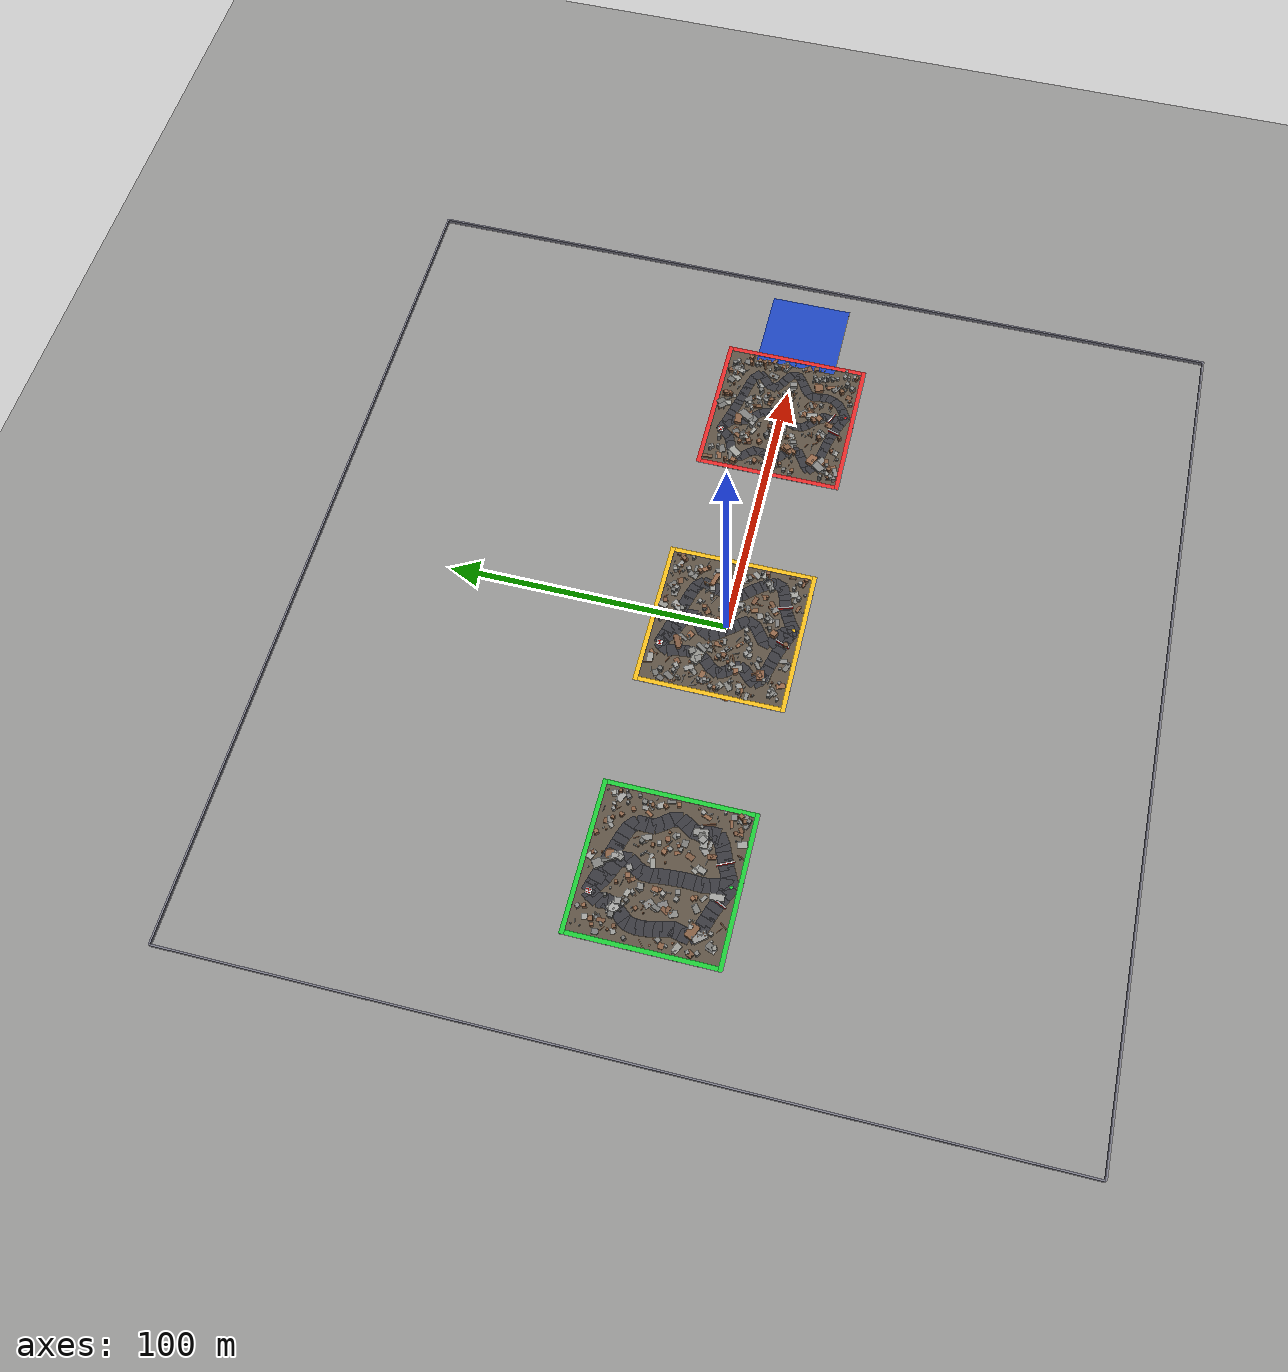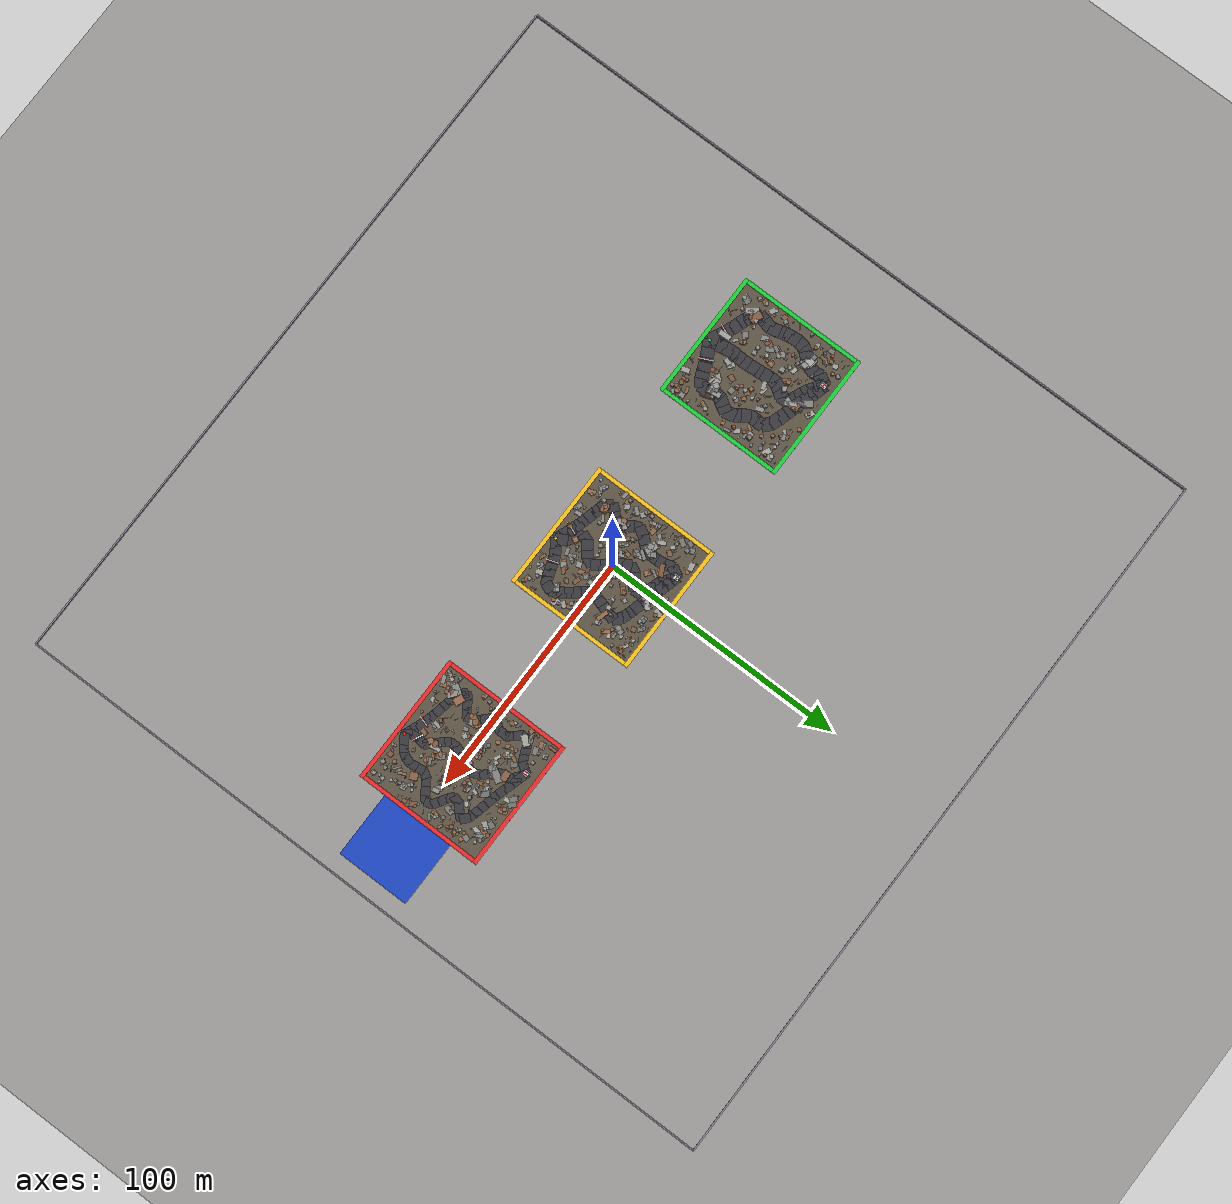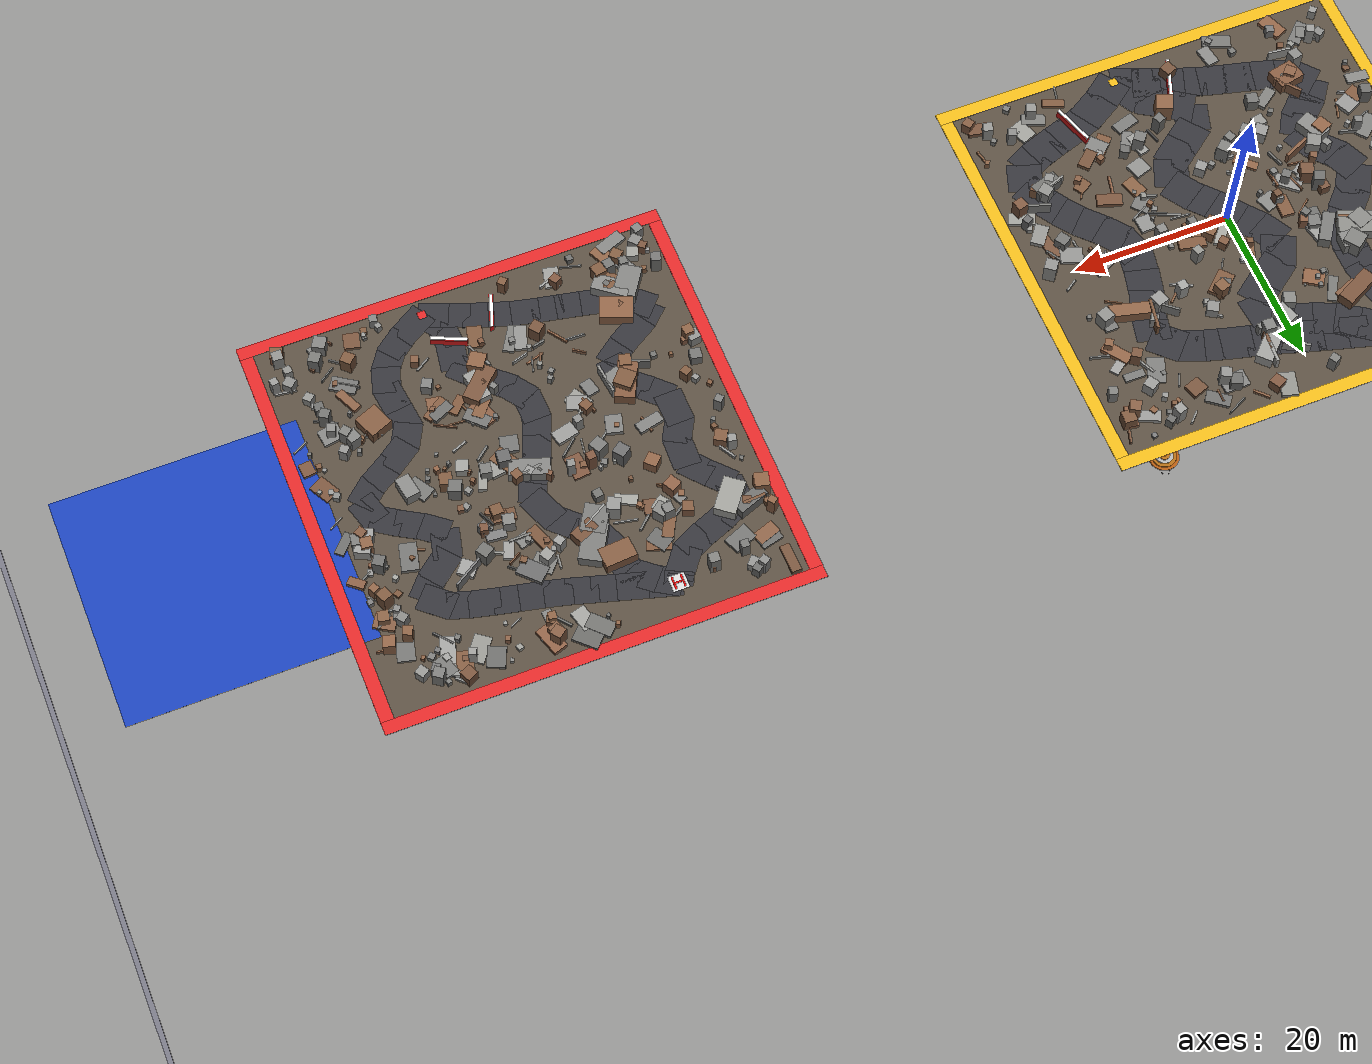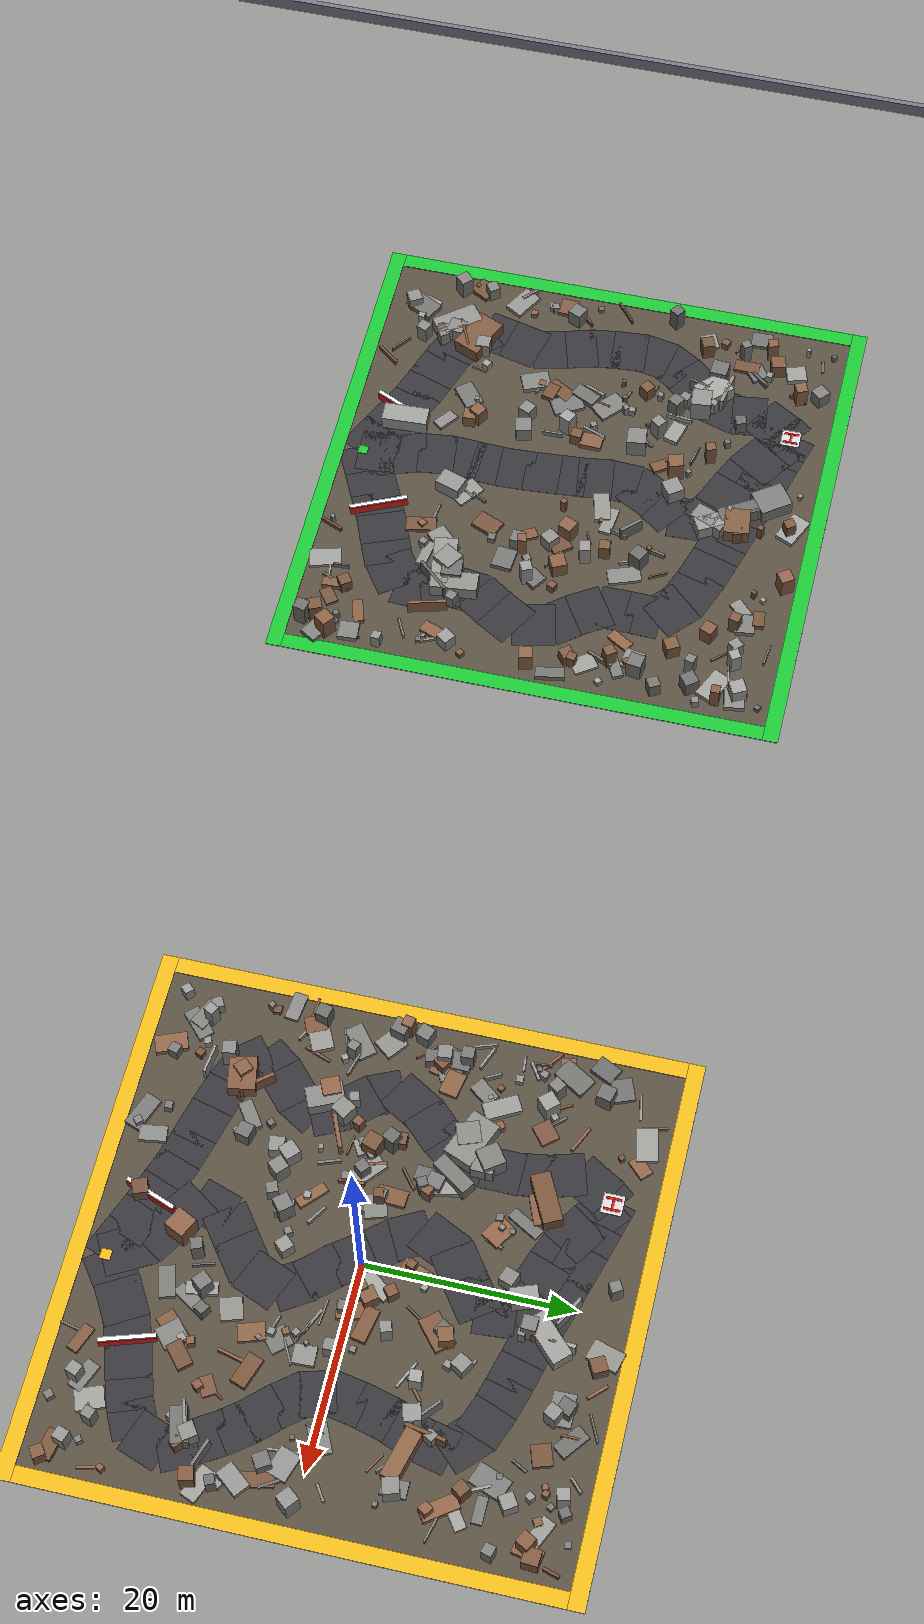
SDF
<sdf version="1.6">
 <world name="navitas_arena">
  <physics type="ode">
   <max_step_size>0.001</max_step_size>
   <real_time_factor>1</real_time_factor>
   <gravity>0 0 -9.8</gravity>
  </physics>
  <wind><linear_velocity>0.5000 0.2000 0.0000</linear_velocity></wind>
  <scene>
   <ambient>0.1200 0.1200 0.1400 1.0000</ambient>
   <background>0.0500 0.0600 0.1000 1.0000</background>
   <shadows>false</shadows>
   <fog>
    <type>exp2</type>
    <color>0.5000 0.5000 0.5500 1.0000</color>
    <start>5.00</start>
    <end>40.00</end>
    <density>0.03500</density>
   </fog>
  </scene>
  <light name="sun" type="directional">
   <cast_shadows>false</cast_shadows>
   <pose>0 0 120 0 0 0</pose>
   <diffuse>0.1500 0.1500 0.1800 1.0000</diffuse>
   <specular>0.1 0.1 0.1 1</specular>
   <attenuation>
    <range>1200</range>
    <constant>0.9</constant>
    <linear>0.01</linear>
    <quadratic>0.001</quadratic>
   </attenuation>
   <direction>-0.3000 0.1000 -0.9500</direction>
  </light>
  <model name="ground_plane">
   <static>true</static>
   <link name="link">
    <collision name="collision">
     <geometry><plane><normal>0 0 1</normal><size>400 400</size></plane></geometry>
     <surface><friction><ode><mu>0.750</mu><mu2>0.750</mu2></ode></friction></surface>
    </collision>
    <visual name="visual">
     <cast_shadows>false</cast_shadows>
     <geometry><plane><normal>0 0 1</normal><size>400 400</size></plane></geometry>
     <material><ambient>0.150 0.140 0.130 1</ambient><diffuse>0.150 0.140 0.130 1</diffuse></material>
    </visual>
   </link>
  </model>
  <model name="ub_N">
   <static>true</static>
   <pose>0.000 150.000 0.750 0 0 0.000</pose>
   <link name="link">
    <collision name="col"><geometry><box><size>300.000 0.600 1.500</size></box></geometry></collision>
    <visual name="vis">
     <geometry><box><size>300.000 0.600 1.500</size></box></geometry>
     <material><ambient>0.45 0.45 0.50 1</ambient><diffuse>0.45 0.45 0.50 1</diffuse></material>
    </visual>
   </link>
  </model>
  <model name="ub_S">
   <static>true</static>
   <pose>0.000 -150.000 0.750 0 0 0.000</pose>
   <link name="link">
    <collision name="col"><geometry><box><size>300.000 0.600 1.500</size></box></geometry></collision>
    <visual name="vis">
     <geometry><box><size>300.000 0.600 1.500</size></box></geometry>
     <material><ambient>0.45 0.45 0.50 1</ambient><diffuse>0.45 0.45 0.50 1</diffuse></material>
    </visual>
   </link>
  </model>
  <model name="ub_W">
   <static>true</static>
   <pose>-150.000 0.000 0.750 0 0 0.000</pose>
   <link name="link">
    <collision name="col"><geometry><box><size>0.600 300.000 1.500</size></box></geometry></collision>
    <visual name="vis">
     <geometry><box><size>0.600 300.000 1.500</size></box></geometry>
     <material><ambient>0.45 0.45 0.50 1</ambient><diffuse>0.45 0.45 0.50 1</diffuse></material>
    </visual>
   </link>
  </model>
  <model name="ub_E">
   <static>true</static>
   <pose>150.000 0.000 0.750 0 0 0.000</pose>
   <link name="link">
    <collision name="col"><geometry><box><size>0.600 300.000 1.500</size></box></geometry></collision>
    <visual name="vis">
     <geometry><box><size>0.600 300.000 1.500</size></box></geometry>
     <material><ambient>0.45 0.45 0.50 1</ambient><diffuse>0.45 0.45 0.50 1</diffuse></material>
    </visual>
   </link>
  </model>
  <model name="landing">
   <static>true</static>
   <pose>128.000 0.000 0.010 0 0 0.000</pose>
   <link name="link">
    <collision name="col"><geometry><box><size>30.000 30.000 0.020</size></box></geometry></collision>
    <visual name="vis">
     <geometry><box><size>30.000 30.000 0.020</size></box></geometry>
     <material><ambient>0.10 0.25 0.70 1</ambient><diffuse>0.10 0.25 0.70 1</diffuse></material>
    </visual>
   </link>
  </model>
  <model name="gd_kolay">
   <static>true</static>
   <pose>-90.000 0.000 0.010 0 0 0.000</pose>
   <link name="link">
    <collision name="col"><geometry><box><size>50.000 50.000 0.020</size></box></geometry></collision>
    <visual name="vis">
     <geometry><box><size>50.000 50.000 0.020</size></box></geometry>
     <material><ambient>0.34 0.30 0.25 1</ambient><diffuse>0.34 0.30 0.25 1</diffuse></material>
    </visual>
   </link>
  </model>
  <model name="brd_kolay_N">
   <static>true</static>
   <pose>-90.000 25.800 0.040 0 0 0.000</pose>
   <link name="link">
    <collision name="col"><geometry><box><size>53.200 1.600 0.080</size></box></geometry></collision>
    <visual name="vis">
     <geometry><box><size>53.200 1.600 0.080</size></box></geometry>
     <material><ambient>0.10 0.75 0.20 1</ambient><diffuse>0.10 0.75 0.20 1</diffuse></material>
    </visual>
   </link>
  </model>
  <model name="brd_kolay_S">
   <static>true</static>
   <pose>-90.000 -25.800 0.040 0 0 0.000</pose>
   <link name="link">
    <collision name="col"><geometry><box><size>53.200 1.600 0.080</size></box></geometry></collision>
    <visual name="vis">
     <geometry><box><size>53.200 1.600 0.080</size></box></geometry>
     <material><ambient>0.10 0.75 0.20 1</ambient><diffuse>0.10 0.75 0.20 1</diffuse></material>
    </visual>
   </link>
  </model>
  <model name="brd_kolay_W">
   <static>true</static>
   <pose>-115.800 0.000 0.040 0 0 0.000</pose>
   <link name="link">
    <collision name="col"><geometry><box><size>1.600 50.000 0.080</size></box></geometry></collision>
    <visual name="vis">
     <geometry><box><size>1.600 50.000 0.080</size></box></geometry>
     <material><ambient>0.10 0.75 0.20 1</ambient><diffuse>0.10 0.75 0.20 1</diffuse></material>
    </visual>
   </link>
  </model>
  <model name="brd_kolay_E">
   <static>true</static>
   <pose>-64.200 0.000 0.040 0 0 0.000</pose>
   <link name="link">
    <collision name="col"><geometry><box><size>1.600 50.000 0.080</size></box></geometry></collision>
    <visual name="vis">
     <geometry><box><size>1.600 50.000 0.080</size></box></geometry>
     <material><ambient>0.10 0.75 0.20 1</ambient><diffuse>0.10 0.75 0.20 1</diffuse></material>
    </visual>
   </link>
  </model>
  <model name="road_kolay_1_0">
   <static>true</static>
   <pose>-91.061 -22.266 0.040 0 0 2.690</pose>
   <link name="link">
    <collision name="col"><geometry><box><size>4.268 5.100 0.020</size></box></geometry></collision>
    <visual name="vis">
     <geometry><box><size>4.268 5.100 0.020</size></box></geometry>
     <material><ambient>0.20 0.20 0.22 1</ambient><diffuse>0.20 0.20 0.22 1</diffuse></material>
    </visual>
   </link>
  </model>
  <model name="road_kolay_1_1">
   <static>true</static>
   <pose>-94.007 -20.856 0.040 0 0 2.701</pose>
   <link name="link">
    <collision name="col"><geometry><box><size>4.063 5.100 0.020</size></box></geometry></collision>
    <visual name="vis">
     <geometry><box><size>4.063 5.100 0.020</size></box></geometry>
     <material><ambient>0.20 0.20 0.22 1</ambient><diffuse>0.20 0.20 0.22 1</diffuse></material>
    </visual>
   </link>
  </model>
  <model name="road_kolay_1_2">
   <static>true</static>
   <pose>-96.749 -19.620 0.040 0 0 2.737</pose>
   <link name="link">
    <collision name="col"><geometry><box><size>3.754 5.100 0.020</size></box></geometry></collision>
    <visual name="vis">
     <geometry><box><size>3.754 5.100 0.020</size></box></geometry>
     <material><ambient>0.20 0.20 0.22 1</ambient><diffuse>0.20 0.20 0.22 1</diffuse></material>
    </visual>
   </link>
  </model>
  <model name="road_kolay_1_3">
   <static>true</static>
   <pose>-99.386 -18.612 0.040 0 0 2.817</pose>
   <link name="link">
    <collision name="col"><geometry><box><size>3.696 5.100 0.020</size></box></geometry></collision>
    <visual name="vis">
     <geometry><box><size>3.696 5.100 0.020</size></box></geometry>
     <material><ambient>0.20 0.20 0.22 1</ambient><diffuse>0.20 0.20 0.22 1</diffuse></material>
    </visual>
   </link>
  </model>
  <model name="road_kolay_1_4">
   <static>true</static>
   <pose>-102.119 -17.697 0.040 0 0 2.819</pose>
   <link name="link">
    <collision name="col"><geometry><box><size>3.868 5.100 0.020</size></box></geometry></collision>
    <visual name="vis">
     <geometry><box><size>3.868 5.100 0.020</size></box></geometry>
     <material><ambient>0.20 0.20 0.22 1</ambient><diffuse>0.20 0.20 0.22 1</diffuse></material>
    </visual>
   </link>
  </model>
  <model name="road_kolay_1_5">
   <static>true</static>
   <pose>-104.772 -16.707 0.040 0 0 2.746</pose>
   <link name="link">
    <collision name="col"><geometry><box><size>3.599 5.100 0.020</size></box></geometry></collision>
    <visual name="vis">
     <geometry><box><size>3.599 5.100 0.020</size></box></geometry>
     <material><ambient>0.20 0.20 0.22 1</ambient><diffuse>0.20 0.20 0.22 1</diffuse></material>
    </visual>
   </link>
  </model>
  <model name="road_kolay_1_6">
   <static>true</static>
   <pose>-107.125 -14.974 0.040 0 0 2.311</pose>
   <link name="link">
    <collision name="col"><geometry><box><size>4.187 5.100 0.020</size></box></geometry></collision>
    <visual name="vis">
     <geometry><box><size>4.187 5.100 0.020</size></box></geometry>
     <material><ambient>0.20 0.20 0.22 1</ambient><diffuse>0.20 0.20 0.22 1</diffuse></material>
    </visual>
   </link>
  </model>
  <model name="road_kolay_1_7">
   <static>true</static>
   <pose>-107.914 -12.340 0.040 0 0 1.349</pose>
   <link name="link">
    <collision name="col"><geometry><box><size>3.811 5.100 0.020</size></box></geometry></collision>
    <visual name="vis">
     <geometry><box><size>3.811 5.100 0.020</size></box></geometry>
     <material><ambient>0.20 0.20 0.22 1</ambient><diffuse>0.20 0.20 0.22 1</diffuse></material>
    </visual>
   </link>
  </model>
  <model name="road_kolay_1_8">
   <static>true</static>
   <pose>-107.250 -9.460 0.040 0 0 1.339</pose>
   <link name="link">
    <collision name="col"><geometry><box><size>3.900 5.100 0.020</size></box></geometry></collision>
    <visual name="vis">
     <geometry><box><size>3.900 5.100 0.020</size></box></geometry>
     <material><ambient>0.20 0.20 0.22 1</ambient><diffuse>0.20 0.20 0.22 1</diffuse></material>
    </visual>
   </link>
  </model>
  <model name="road_kolay_1_9">
   <static>true</static>
   <pose>-107.311 -6.250 0.040 0 0 1.798</pose>
   <link name="link">
    <collision name="col"><geometry><box><size>4.493 5.100 0.020</size></box></geometry></collision>
    <visual name="vis">
     <geometry><box><size>4.493 5.100 0.020</size></box></geometry>
     <material><ambient>0.20 0.20 0.22 1</ambient><diffuse>0.20 0.20 0.22 1</diffuse></material>
    </visual>
   </link>
  </model>
  <model name="road_kolay_1_10">
   <static>true</static>
   <pose>-108.060 -3.333 0.040 0 0 1.857</pose>
   <link name="link">
    <collision name="col"><geometry><box><size>3.332 5.100 0.020</size></box></geometry></collision>
    <visual name="vis">
     <geometry><box><size>3.332 5.100 0.020</size></box></geometry>
     <material><ambient>0.20 0.20 0.22 1</ambient><diffuse>0.20 0.20 0.22 1</diffuse></material>
    </visual>
   </link>
  </model>
  <model name="road_kolay_1_11">
   <static>true</static>
   <pose>-108.597 -0.883 0.040 0 0 1.721</pose>
   <link name="link">
    <collision name="col"><geometry><box><size>3.496 5.100 0.020</size></box></geometry></collision>
    <visual name="vis">
     <geometry><box><size>3.496 5.100 0.020</size></box></geometry>
     <material><ambient>0.20 0.20 0.22 1</ambient><diffuse>0.20 0.20 0.22 1</diffuse></material>
    </visual>
   </link>
  </model>
  <model name="road_kolay_1_12">
   <static>true</static>
   <pose>-108.901 1.800 0.040 0 0 1.649</pose>
   <link name="link">
    <collision name="col"><geometry><box><size>3.709 5.100 0.020</size></box></geometry></collision>
    <visual name="vis">
     <geometry><box><size>3.709 5.100 0.020</size></box></geometry>
     <material><ambient>0.20 0.20 0.22 1</ambient><diffuse>0.20 0.20 0.22 1</diffuse></material>
    </visual>
   </link>
  </model>
  <model name="road_kolay_1_13">
   <static>true</static>
   <pose>-108.763 4.600 0.040 0 0 1.396</pose>
   <link name="link">
    <collision name="col"><geometry><box><size>3.744 5.100 0.020</size></box></geometry></collision>
    <visual name="vis">
     <geometry><box><size>3.744 5.100 0.020</size></box></geometry>
     <material><ambient>0.20 0.20 0.22 1</ambient><diffuse>0.20 0.20 0.22 1</diffuse></material>
    </visual>
   </link>
  </model>
  <model name="road_kolay_1_14">
   <static>true</static>
   <pose>-107.877 7.036 0.040 0 0 1.019</pose>
   <link name="link">
    <collision name="col"><geometry><box><size>3.335 5.100 0.020</size></box></geometry></collision>
    <visual name="vis">
     <geometry><box><size>3.335 5.100 0.020</size></box></geometry>
     <material><ambient>0.20 0.20 0.22 1</ambient><diffuse>0.20 0.20 0.22 1</diffuse></material>
    </visual>
   </link>
  </model>
  <model name="road_kolay_1_15">
   <static>true</static>
   <pose>-106.329 9.124 0.040 0 0 0.858</pose>
   <link name="link">
    <collision name="col"><geometry><box><size>3.680 5.100 0.020</size></box></geometry></collision>
    <visual name="vis">
     <geometry><box><size>3.680 5.100 0.020</size></box></geometry>
     <material><ambient>0.20 0.20 0.22 1</ambient><diffuse>0.20 0.20 0.22 1</diffuse></material>
    </visual>
   </link>
  </model>
  <model name="road_kolay_1_16">
   <static>true</static>
   <pose>-104.605 11.153 0.040 0 0 0.876</pose>
   <link name="link">
    <collision name="col"><geometry><box><size>3.446 5.100 0.020</size></box></geometry></collision>
    <visual name="vis">
     <geometry><box><size>3.446 5.100 0.020</size></box></geometry>
     <material><ambient>0.20 0.20 0.22 1</ambient><diffuse>0.20 0.20 0.22 1</diffuse></material>
    </visual>
   </link>
  </model>
  <model name="road_kolay_1_17">
   <static>true</static>
   <pose>-103.387 13.427 0.040 0 0 1.270</pose>
   <link name="link">
    <collision name="col"><geometry><box><size>3.613 5.100 0.020</size></box></geometry></collision>
    <visual name="vis">
     <geometry><box><size>3.613 5.100 0.020</size></box></geometry>
     <material><ambient>0.20 0.20 0.22 1</ambient><diffuse>0.20 0.20 0.22 1</diffuse></material>
    </visual>
   </link>
  </model>
  <model name="road_kolay_1_18">
   <static>true</static>
   <pose>-103.160 16.111 0.040 0 0 1.696</pose>
   <link name="link">
    <collision name="col"><geometry><box><size>3.700 5.100 0.020</size></box></geometry></collision>
    <visual name="vis">
     <geometry><box><size>3.700 5.100 0.020</size></box></geometry>
     <material><ambient>0.20 0.20 0.22 1</ambient><diffuse>0.20 0.20 0.22 1</diffuse></material>
    </visual>
   </link>
  </model>
  <model name="road_kolay_1_19">
   <static>true</static>
   <pose>-102.569 18.815 0.040 0 0 1.043</pose>
   <link name="link">
    <collision name="col"><geometry><box><size>3.943 5.100 0.020</size></box></geometry></collision>
    <visual name="vis">
     <geometry><box><size>3.943 5.100 0.020</size></box></geometry>
     <material><ambient>0.20 0.20 0.22 1</ambient><diffuse>0.20 0.20 0.22 1</diffuse></material>
    </visual>
   </link>
  </model>
  <model name="road_kolay_1_20">
   <static>true</static>
   <pose>-101.479 20.565 0.040 0 0 0.931</pose>
   <link name="link">
    <collision name="col"><geometry><box><size>1.985 5.100 0.020</size></box></geometry></collision>
    <visual name="vis">
     <geometry><box><size>1.985 5.100 0.020</size></box></geometry>
     <material><ambient>0.20 0.20 0.22 1</ambient><diffuse>0.20 0.20 0.22 1</diffuse></material>
    </visual>
   </link>
  </model>
  <model name="road_kolay_2_0">
   <static>true</static>
   <pose>-89.648 -21.250 0.040 0 0 1.629</pose>
   <link name="link">
    <collision name="col"><geometry><box><size>4.406 5.100 0.020</size></box></geometry></collision>
    <visual name="vis">
     <geometry><box><size>4.406 5.100 0.020</size></box></geometry>
     <material><ambient>0.20 0.20 0.22 1</ambient><diffuse>0.20 0.20 0.22 1</diffuse></material>
    </visual>
   </link>
  </model>
  <model name="road_kolay_2_1">
   <static>true</static>
   <pose>-90.166 -18.111 0.040 0 0 1.862</pose>
   <link name="link">
    <collision name="col"><geometry><box><size>3.800 5.100 0.020</size></box></geometry></collision>
    <visual name="vis">
     <geometry><box><size>3.800 5.100 0.020</size></box></geometry>
     <material><ambient>0.20 0.20 0.22 1</ambient><diffuse>0.20 0.20 0.22 1</diffuse></material>
    </visual>
   </link>
  </model>
  <model name="road_kolay_2_2">
   <static>true</static>
   <pose>-90.755 -15.241 0.040 0 0 1.687</pose>
   <link name="link">
    <collision name="col"><geometry><box><size>3.882 5.100 0.020</size></box></geometry></collision>
    <visual name="vis">
     <geometry><box><size>3.882 5.100 0.020</size></box></geometry>
     <material><ambient>0.20 0.20 0.22 1</ambient><diffuse>0.20 0.20 0.22 1</diffuse></material>
    </visual>
   </link>
  </model>
  <model name="road_kolay_2_3">
   <static>true</static>
   <pose>-90.850 -12.340 0.040 0 0 1.516</pose>
   <link name="link">
    <collision name="col"><geometry><box><size>3.744 5.100 0.020</size></box></geometry></collision>
    <visual name="vis">
     <geometry><box><size>3.744 5.100 0.020</size></box></geometry>
     <material><ambient>0.20 0.20 0.22 1</ambient><diffuse>0.20 0.20 0.22 1</diffuse></material>
    </visual>
   </link>
  </model>
  <model name="road_kolay_2_4">
   <static>true</static>
   <pose>-90.716 -9.460 0.040 0 0 1.532</pose>
   <link name="link">
    <collision name="col"><geometry><box><size>3.822 5.100 0.020</size></box></geometry></collision>
    <visual name="vis">
     <geometry><box><size>3.822 5.100 0.020</size></box></geometry>
     <material><ambient>0.20 0.20 0.22 1</ambient><diffuse>0.20 0.20 0.22 1</diffuse></material>
    </visual>
   </link>
  </model>
  <model name="road_kolay_2_5">
   <static>true</static>
   <pose>-90.721 -6.600 0.040 0 0 1.615</pose>
   <link name="link">
    <collision name="col"><geometry><box><size>3.703 5.100 0.020</size></box></geometry></collision>
    <visual name="vis">
     <geometry><box><size>3.703 5.100 0.020</size></box></geometry>
     <material><ambient>0.20 0.20 0.22 1</ambient><diffuse>0.20 0.20 0.22 1</diffuse></material>
    </visual>
   </link>
  </model>
  <model name="road_kolay_2_6">
   <static>true</static>
   <pose>-90.887 -3.800 0.040 0 0 1.645</pose>
   <link name="link">
    <collision name="col"><geometry><box><size>3.708 5.100 0.020</size></box></geometry></collision>
    <visual name="vis">
     <geometry><box><size>3.708 5.100 0.020</size></box></geometry>
     <material><ambient>0.20 0.20 0.22 1</ambient><diffuse>0.20 0.20 0.22 1</diffuse></material>
    </visual>
   </link>
  </model>
  <model name="road_kolay_2_7">
   <static>true</static>
   <pose>-91.109 -1.000 0.040 0 0 1.655</pose>
   <link name="link">
    <collision name="col"><geometry><box><size>3.710 5.100 0.020</size></box></geometry></collision>
    <visual name="vis">
     <geometry><box><size>3.710 5.100 0.020</size></box></geometry>
     <material><ambient>0.20 0.20 0.22 1</ambient><diffuse>0.20 0.20 0.22 1</diffuse></material>
    </visual>
   </link>
  </model>
  <model name="road_kolay_2_8">
   <static>true</static>
   <pose>-91.413 1.800 0.040 0 0 1.703</pose>
   <link name="link">
    <collision name="col"><geometry><box><size>3.725 5.100 0.020</size></box></geometry></collision>
    <visual name="vis">
     <geometry><box><size>3.725 5.100 0.020</size></box></geometry>
     <material><ambient>0.20 0.20 0.22 1</ambient><diffuse>0.20 0.20 0.22 1</diffuse></material>
    </visual>
   </link>
  </model>
  <model name="road_kolay_2_9">
   <static>true</static>
   <pose>-91.532 4.600 0.040 0 0 1.523</pose>
   <link name="link">
    <collision name="col"><geometry><box><size>3.703 5.100 0.020</size></box></geometry></collision>
    <visual name="vis">
     <geometry><box><size>3.703 5.100 0.020</size></box></geometry>
     <material><ambient>0.20 0.20 0.22 1</ambient><diffuse>0.20 0.20 0.22 1</diffuse></material>
    </visual>
   </link>
  </model>
  <model name="road_kolay_2_10">
   <static>true</static>
   <pose>-90.799 7.213 0.040 0 0 1.069</pose>
   <link name="link">
    <collision name="col"><geometry><box><size>3.668 5.100 0.020</size></box></geometry></collision>
    <visual name="vis">
     <geometry><box><size>3.668 5.100 0.020</size></box></geometry>
     <material><ambient>0.20 0.20 0.22 1</ambient><diffuse>0.20 0.20 0.22 1</diffuse></material>
    </visual>
   </link>
  </model>
  <model name="road_kolay_2_11">
   <static>true</static>
   <pose>-89.248 9.639 0.040 0 0 0.940</pose>
   <link name="link">
    <collision name="col"><geometry><box><size>3.903 5.100 0.020</size></box></geometry></collision>
    <visual name="vis">
     <geometry><box><size>3.903 5.100 0.020</size></box></geometry>
     <material><ambient>0.20 0.20 0.22 1</ambient><diffuse>0.20 0.20 0.22 1</diffuse></material>
    </visual>
   </link>
  </model>
  <model name="road_kolay_2_12">
   <static>true</static>
   <pose>-88.425 12.317 0.040 0 0 1.613</pose>
   <link name="link">
    <collision name="col"><geometry><box><size>3.834 5.100 0.020</size></box></geometry></collision>
    <visual name="vis">
     <geometry><box><size>3.834 5.100 0.020</size></box></geometry>
     <material><ambient>0.20 0.20 0.22 1</ambient><diffuse>0.20 0.20 0.22 1</diffuse></material>
    </visual>
   </link>
  </model>
  <model name="road_kolay_2_13">
   <static>true</static>
   <pose>-89.631 14.469 0.040 0 0 2.601</pose>
   <link name="link">
    <collision name="col"><geometry><box><size>3.567 5.100 0.020</size></box></geometry></collision>
    <visual name="vis">
     <geometry><box><size>3.567 5.100 0.020</size></box></geometry>
     <material><ambient>0.20 0.20 0.22 1</ambient><diffuse>0.20 0.20 0.22 1</diffuse></material>
    </visual>
   </link>
  </model>
  <model name="road_kolay_2_14">
   <static>true</static>
   <pose>-92.224 15.758 0.040 0 0 2.748</pose>
   <link name="link">
    <collision name="col"><geometry><box><size>4.039 5.100 0.020</size></box></geometry></collision>
    <visual name="vis">
     <geometry><box><size>4.039 5.100 0.020</size></box></geometry>
     <material><ambient>0.20 0.20 0.22 1</ambient><diffuse>0.20 0.20 0.22 1</diffuse></material>
    </visual>
   </link>
  </model>
  <model name="road_kolay_2_15">
   <static>true</static>
   <pose>-94.904 16.930 0.040 0 0 2.708</pose>
   <link name="link">
    <collision name="col"><geometry><box><size>3.613 5.100 0.020</size></box></geometry></collision>
    <visual name="vis">
     <geometry><box><size>3.613 5.100 0.020</size></box></geometry>
     <material><ambient>0.20 0.20 0.22 1</ambient><diffuse>0.20 0.20 0.22 1</diffuse></material>
    </visual>
   </link>
  </model>
  <model name="road_kolay_2_16">
   <static>true</static>
   <pose>-97.375 18.320 0.040 0 0 2.557</pose>
   <link name="link">
    <collision name="col"><geometry><box><size>3.873 5.100 0.020</size></box></geometry></collision>
    <visual name="vis">
     <geometry><box><size>3.873 5.100 0.020</size></box></geometry>
     <material><ambient>0.20 0.20 0.22 1</ambient><diffuse>0.20 0.20 0.22 1</diffuse></material>
    </visual>
   </link>
  </model>
  <model name="road_kolay_2_17">
   <static>true</static>
   <pose>-99.885 20.070 0.040 0 0 2.509</pose>
   <link name="link">
    <collision name="col"><geometry><box><size>4.048 5.100 0.020</size></box></geometry></collision>
    <visual name="vis">
     <geometry><box><size>4.048 5.100 0.020</size></box></geometry>
     <material><ambient>0.20 0.20 0.22 1</ambient><diffuse>0.20 0.20 0.22 1</diffuse></material>
    </visual>
   </link>
  </model>
  <model name="road_kolay_3_0">
   <static>true</static>
   <pose>-88.072 -22.266 0.040 0 0 0.462</pose>
   <link name="link">
    <collision name="col"><geometry><box><size>4.193 5.100 0.020</size></box></geometry></collision>
    <visual name="vis">
     <geometry><box><size>4.193 5.100 0.020</size></box></geometry>
     <material><ambient>0.20 0.20 0.22 1</ambient><diffuse>0.20 0.20 0.22 1</diffuse></material>
    </visual>
   </link>
  </model>
  <model name="road_kolay_3_1">
   <static>true</static>
   <pose>-85.250 -20.856 0.040 0 0 0.464</pose>
   <link name="link">
    <collision name="col"><geometry><box><size>3.915 5.100 0.020</size></box></geometry></collision>
    <visual name="vis">
     <geometry><box><size>3.915 5.100 0.020</size></box></geometry>
     <material><ambient>0.20 0.20 0.22 1</ambient><diffuse>0.20 0.20 0.22 1</diffuse></material>
    </visual>
   </link>
  </model>
  <model name="road_kolay_3_2">
   <static>true</static>
   <pose>-82.686 -19.592 0.040 0 0 0.451</pose>
   <link name="link">
    <collision name="col"><geometry><box><size>3.603 5.100 0.020</size></box></geometry></collision>
    <visual name="vis">
     <geometry><box><size>3.603 5.100 0.020</size></box></geometry>
     <material><ambient>0.20 0.20 0.22 1</ambient><diffuse>0.20 0.20 0.22 1</diffuse></material>
    </visual>
   </link>
  </model>
  <model name="road_kolay_3_3">
   <static>true</static>
   <pose>-80.211 -18.499 0.040 0 0 0.380</pose>
   <link name="link">
    <collision name="col"><geometry><box><size>3.611 5.100 0.020</size></box></geometry></collision>
    <visual name="vis">
     <geometry><box><size>3.611 5.100 0.020</size></box></geometry>
     <material><ambient>0.20 0.20 0.22 1</ambient><diffuse>0.20 0.20 0.22 1</diffuse></material>
    </visual>
   </link>
  </model>
  <model name="road_kolay_3_4">
   <static>true</static>
   <pose>-77.682 -17.455 0.040 0 0 0.402</pose>
   <link name="link">
    <collision name="col"><geometry><box><size>3.661 5.100 0.020</size></box></geometry></collision>
    <visual name="vis">
     <geometry><box><size>3.661 5.100 0.020</size></box></geometry>
     <material><ambient>0.20 0.20 0.22 1</ambient><diffuse>0.20 0.20 0.22 1</diffuse></material>
    </visual>
   </link>
  </model>
  <model name="road_kolay_3_5">
   <static>true</static>
   <pose>-75.077 -15.957 0.040 0 0 0.622</pose>
   <link name="link">
    <collision name="col"><geometry><box><size>4.185 5.100 0.020</size></box></geometry></collision>
    <visual name="vis">
     <geometry><box><size>4.185 5.100 0.020</size></box></geometry>
     <material><ambient>0.20 0.20 0.22 1</ambient><diffuse>0.20 0.20 0.22 1</diffuse></material>
    </visual>
   </link>
  </model>
  <model name="road_kolay_3_6">
   <static>true</static>
   <pose>-73.682 -13.690 0.040 0 0 1.525</pose>
   <link name="link">
    <collision name="col"><geometry><box><size>3.523 5.100 0.020</size></box></geometry></collision>
    <visual name="vis">
     <geometry><box><size>3.523 5.100 0.020</size></box></geometry>
     <material><ambient>0.20 0.20 0.22 1</ambient><diffuse>0.20 0.20 0.22 1</diffuse></material>
    </visual>
   </link>
  </model>
  <model name="road_kolay_3_7">
   <static>true</static>
   <pose>-74.116 -10.910 0.040 0 0 1.894</pose>
   <link name="link">
    <collision name="col"><geometry><box><size>4.001 5.100 0.020</size></box></geometry></collision>
    <visual name="vis">
     <geometry><box><size>4.001 5.100 0.020</size></box></geometry>
     <material><ambient>0.20 0.20 0.22 1</ambient><diffuse>0.20 0.20 0.22 1</diffuse></material>
    </visual>
   </link>
  </model>
  <model name="road_kolay_3_8">
   <static>true</static>
   <pose>-74.431 -8.137 0.040 0 0 1.435</pose>
   <link name="link">
    <collision name="col"><geometry><box><size>3.531 5.100 0.020</size></box></geometry></collision>
    <visual name="vis">
     <geometry><box><size>3.531 5.100 0.020</size></box></geometry>
     <material><ambient>0.20 0.20 0.22 1</ambient><diffuse>0.20 0.20 0.22 1</diffuse></material>
    </visual>
   </link>
  </model>
  <model name="road_kolay_3_9">
   <static>true</static>
   <pose>-73.483 -5.667 0.040 0 0 0.988</pose>
   <link name="link">
    <collision name="col"><geometry><box><size>3.695 5.100 0.020</size></box></geometry></collision>
    <visual name="vis">
     <geometry><box><size>3.695 5.100 0.020</size></box></geometry>
     <material><ambient>0.20 0.20 0.22 1</ambient><diffuse>0.20 0.20 0.22 1</diffuse></material>
    </visual>
   </link>
  </model>
  <model name="road_kolay_3_10">
   <static>true</static>
   <pose>-72.039 -3.333 0.040 0 0 1.047</pose>
   <link name="link">
    <collision name="col"><geometry><box><size>3.595 5.100 0.020</size></box></geometry></collision>
    <visual name="vis">
     <geometry><box><size>3.595 5.100 0.020</size></box></geometry>
     <material><ambient>0.20 0.20 0.22 1</ambient><diffuse>0.20 0.20 0.22 1</diffuse></material>
    </visual>
   </link>
  </model>
  <model name="road_kolay_3_11">
   <static>true</static>
   <pose>-71.781 -0.417 0.040 0 0 1.804</pose>
   <link name="link">
    <collision name="col"><geometry><box><size>4.497 5.100 0.020</size></box></geometry></collision>
    <visual name="vis">
     <geometry><box><size>4.497 5.100 0.020</size></box></geometry>
     <material><ambient>0.20 0.20 0.22 1</ambient><diffuse>0.20 0.20 0.22 1</diffuse></material>
    </visual>
   </link>
  </model>
  <model name="road_kolay_3_12">
   <static>true</static>
   <pose>-73.136 2.500 0.040 0 0 2.249</pose>
   <link name="link">
    <collision name="col"><geometry><box><size>3.896 5.100 0.020</size></box></geometry></collision>
    <visual name="vis">
     <geometry><box><size>3.896 5.100 0.020</size></box></geometry>
     <material><ambient>0.20 0.20 0.22 1</ambient><diffuse>0.20 0.20 0.22 1</diffuse></material>
    </visual>
   </link>
  </model>
  <model name="road_kolay_3_13">
   <static>true</static>
   <pose>-74.816 4.833 0.040 0 0 2.136</pose>
   <link name="link">
    <collision name="col"><geometry><box><size>3.663 5.100 0.020</size></box></geometry></collision>
    <visual name="vis">
     <geometry><box><size>3.663 5.100 0.020</size></box></geometry>
     <material><ambient>0.20 0.20 0.22 1</ambient><diffuse>0.20 0.20 0.22 1</diffuse></material>
    </visual>
   </link>
  </model>
  <model name="road_kolay_3_14">
   <static>true</static>
   <pose>-75.554 7.460 0.040 0 0 1.570</pose>
   <link name="link">
    <collision name="col"><geometry><box><size>3.820 5.100 0.020</size></box></geometry></collision>
    <visual name="vis">
     <geometry><box><size>3.820 5.100 0.020</size></box></geometry>
     <material><ambient>0.20 0.20 0.22 1</ambient><diffuse>0.20 0.20 0.22 1</diffuse></material>
    </visual>
   </link>
  </model>
  <model name="road_kolay_3_15">
   <static>true</static>
   <pose>-75.510 10.340 0.040 0 0 1.541</pose>
   <link name="link">
    <collision name="col"><geometry><box><size>3.741 5.100 0.020</size></box></geometry></collision>
    <visual name="vis">
     <geometry><box><size>3.741 5.100 0.020</size></box></geometry>
     <material><ambient>0.20 0.20 0.22 1</ambient><diffuse>0.20 0.20 0.22 1</diffuse></material>
    </visual>
   </link>
  </model>
  <model name="road_kolay_3_16">
   <static>true</static>
   <pose>-76.684 12.872 0.040 0 0 2.401</pose>
   <link name="link">
    <collision name="col"><geometry><box><size>4.195 5.100 0.020</size></box></geometry></collision>
    <visual name="vis">
     <geometry><box><size>4.195 5.100 0.020</size></box></geometry>
     <material><ambient>0.20 0.20 0.22 1</ambient><diffuse>0.20 0.20 0.22 1</diffuse></material>
    </visual>
   </link>
  </model>
  <model name="road_kolay_3_17">
   <static>true</static>
   <pose>-79.588 14.627 0.040 0 0 2.777</pose>
   <link name="link">
    <collision name="col"><geometry><box><size>4.514 5.100 0.020</size></box></geometry></collision>
    <visual name="vis">
     <geometry><box><size>4.514 5.100 0.020</size></box></geometry>
     <material><ambient>0.20 0.20 0.22 1</ambient><diffuse>0.20 0.20 0.22 1</diffuse></material>
    </visual>
   </link>
  </model>
  <model name="road_kolay_3_18">
   <static>true</static>
   <pose>-82.578 15.657 0.040 0 0 2.853</pose>
   <link name="link">
    <collision name="col"><geometry><box><size>3.615 5.100 0.020</size></box></geometry></collision>
    <visual name="vis">
     <geometry><box><size>3.615 5.100 0.020</size></box></geometry>
     <material><ambient>0.20 0.20 0.22 1</ambient><diffuse>0.20 0.20 0.22 1</diffuse></material>
    </visual>
   </link>
  </model>
  <model name="road_kolay_3_19">
   <static>true</static>
   <pose>-85.192 16.409 0.040 0 0 2.869</pose>
   <link name="link">
    <collision name="col"><geometry><box><size>3.627 5.100 0.020</size></box></geometry></collision>
    <visual name="vis">
     <geometry><box><size>3.627 5.100 0.020</size></box></geometry>
     <material><ambient>0.20 0.20 0.22 1</ambient><diffuse>0.20 0.20 0.22 1</diffuse></material>
    </visual>
   </link>
  </model>
  <model name="road_kolay_3_20">
   <static>true</static>
   <pose>-87.720 17.138 0.040 0 0 2.852</pose>
   <link name="link">
    <collision name="col"><geometry><box><size>3.435 5.100 0.020</size></box></geometry></collision>
    <visual name="vis">
     <geometry><box><size>3.435 5.100 0.020</size></box></geometry>
     <material><ambient>0.20 0.20 0.22 1</ambient><diffuse>0.20 0.20 0.22 1</diffuse></material>
    </visual>
   </link>
  </model>
  <model name="road_kolay_3_21">
   <static>true</static>
   <pose>-90.267 17.910 0.040 0 0 2.843</pose>
   <link name="link">
    <collision name="col"><geometry><box><size>3.688 5.100 0.020</size></box></geometry></collision>
    <visual name="vis">
     <geometry><box><size>3.688 5.100 0.020</size></box></geometry>
     <material><ambient>0.20 0.20 0.22 1</ambient><diffuse>0.20 0.20 0.22 1</diffuse></material>
    </visual>
   </link>
  </model>
  <model name="road_kolay_3_22">
   <static>true</static>
   <pose>-93.019 18.730 0.040 0 0 2.860</pose>
   <link name="link">
    <collision name="col"><geometry><box><size>3.854 5.100 0.020</size></box></geometry></collision>
    <visual name="vis">
     <geometry><box><size>3.854 5.100 0.020</size></box></geometry>
     <material><ambient>0.20 0.20 0.22 1</ambient><diffuse>0.20 0.20 0.22 1</diffuse></material>
    </visual>
   </link>
  </model>
  <model name="road_kolay_3_23">
   <static>true</static>
   <pose>-95.802 19.520 0.040 0 0 2.870</pose>
   <link name="link">
    <collision name="col"><geometry><box><size>3.732 5.100 0.020</size></box></geometry></collision>
    <visual name="vis">
     <geometry><box><size>3.732 5.100 0.020</size></box></geometry>
     <material><ambient>0.20 0.20 0.22 1</ambient><diffuse>0.20 0.20 0.22 1</diffuse></material>
    </visual>
   </link>
  </model>
  <model name="road_kolay_3_24">
   <static>true</static>
   <pose>-98.332 20.220 0.040 0 0 2.874</pose>
   <link name="link">
    <collision name="col"><geometry><box><size>3.320 5.100 0.020</size></box></geometry></collision>
    <visual name="vis">
     <geometry><box><size>3.320 5.100 0.020</size></box></geometry>
     <material><ambient>0.20 0.20 0.22 1</ambient><diffuse>0.20 0.20 0.22 1</diffuse></material>
    </visual>
   </link>
  </model>
  <model name="road_kolay_3_25">
   <static>true</static>
   <pose>-100.327 20.770 0.040 0 0 2.871</pose>
   <link name="link">
    <collision name="col"><geometry><box><size>2.618 5.100 0.020</size></box></geometry></collision>
    <visual name="vis">
     <geometry><box><size>2.618 5.100 0.020</size></box></geometry>
     <material><ambient>0.20 0.20 0.22 1</ambient><diffuse>0.20 0.20 0.22 1</diffuse></material>
    </visual>
   </link>
  </model>
  <model name="bar_kolay_1">
   <static>true</static>
   <pose>-95.437 -20.182 0.500 0 0 4.289</pose>
   <link name="link">
    <collision name="col"><geometry><box><size>6.100 0.500 1.000</size></box></geometry></collision>
    <visual name="vis">
     <geometry><box><size>6.100 0.500 1.000</size></box></geometry>
     <material><ambient>0.85 0.10 0.10 1</ambient><diffuse>0.85 0.10 0.10 1</diffuse></material>
    </visual>
   </link>
  </model>
  <model name="bar_kolay_1b">
   <static>true</static>
   <pose>-95.437 -20.182 1.000 0 0 4.289</pose>
   <link name="link">
    <collision name="col"><geometry><box><size>6.100 0.400 0.300</size></box></geometry></collision>
    <visual name="vis">
     <geometry><box><size>6.100 0.400 0.300</size></box></geometry>
     <material><ambient>0.95 0.95 0.95 1</ambient><diffuse>0.95 0.95 0.95 1</diffuse></material>
    </visual>
   </link>
  </model>
  <model name="blk_kolay_1_0_0">
   <static>true</static>
   <pose>-106.695 -17.472 0.800 0 0 2.249</pose>
   <link name="link">
    <collision name="col"><geometry><box><size>3.062 0.418 1.600</size></box></geometry></collision>
    <visual name="vis">
     <geometry><box><size>3.062 0.418 1.600</size></box></geometry>
     <material><ambient>0.49 0.49 0.48 1</ambient><diffuse>0.49 0.49 0.48 1</diffuse></material>
    </visual>
   </link>
  </model>
  <model name="blk_kolay_1_0_1">
   <static>true</static>
   <pose>-105.365 -13.594 0.898 0 0 0.024</pose>
   <link name="link">
    <collision name="col"><geometry><box><size>1.462 1.462 1.797</size></box></geometry></collision>
    <visual name="vis">
     <geometry><box><size>1.462 1.462 1.797</size></box></geometry>
     <material><ambient>0.55 0.55 0.54 1</ambient><diffuse>0.55 0.55 0.54 1</diffuse></material>
    </visual>
   </link>
  </model>
  <model name="blk_kolay_1_0_2">
   <static>true</static>
   <pose>-106.574 -18.451 0.800 0 0 1.519</pose>
   <link name="link">
    <collision name="col"><geometry><box><size>0.954 0.954 1.600</size></box></geometry></collision>
    <visual name="vis">
     <geometry><box><size>0.954 0.954 1.600</size></box></geometry>
     <material><ambient>0.48 0.34 0.24 1</ambient><diffuse>0.48 0.34 0.24 1</diffuse></material>
    </visual>
   </link>
  </model>
  <model name="blk_kolay_1_0_3">
   <static>true</static>
   <pose>-106.473 -14.396 0.800 0 0 2.748</pose>
   <link name="link">
    <collision name="col"><geometry><box><size>4.836 2.939 1.600</size></box></geometry></collision>
    <visual name="vis">
     <geometry><box><size>4.836 2.939 1.600</size></box></geometry>
     <material><ambient>0.48 0.34 0.24 1</ambient><diffuse>0.48 0.34 0.24 1</diffuse></material>
    </visual>
   </link>
  </model>
  <model name="blk_kolay_1_0_4">
   <static>true</static>
   <pose>-106.361 -15.901 0.800 0 0 0.434</pose>
   <link name="link">
    <collision name="col"><geometry><box><size>3.586 0.243 1.600</size></box></geometry></collision>
    <visual name="vis">
     <geometry><box><size>3.586 0.243 1.600</size></box></geometry>
     <material><ambient>0.48 0.34 0.24 1</ambient><diffuse>0.48 0.34 0.24 1</diffuse></material>
    </visual>
   </link>
  </model>
  <model name="blk_kolay_1_0_5">
   <static>true</static>
   <pose>-107.823 -17.091 0.800 0 0 2.238</pose>
   <link name="link">
    <collision name="col"><geometry><box><size>4.949 2.385 1.600</size></box></geometry></collision>
    <visual name="vis">
     <geometry><box><size>4.949 2.385 1.600</size></box></geometry>
     <material><ambient>0.55 0.55 0.54 1</ambient><diffuse>0.55 0.55 0.54 1</diffuse></material>
    </visual>
   </link>
  </model>
  <model name="blk_kolay_1_0_6">
   <static>true</static>
   <pose>-106.975 -16.943 0.800 0 0 1.425</pose>
   <link name="link">
    <collision name="col"><geometry><box><size>1.731 1.731 1.600</size></box></geometry></collision>
    <visual name="vis">
     <geometry><box><size>1.731 1.731 1.600</size></box></geometry>
     <material><ambient>0.52 0.52 0.51 1</ambient><diffuse>0.52 0.52 0.51 1</diffuse></material>
    </visual>
   </link>
  </model>
  <model name="blk_kolay_1_0_7">
   <static>true</static>
   <pose>-105.814 -18.186 0.800 0 0 0.638</pose>
   <link name="link">
    <collision name="col"><geometry><box><size>1.049 1.049 1.600</size></box></geometry></collision>
    <visual name="vis">
     <geometry><box><size>1.049 1.049 1.600</size></box></geometry>
     <material><ambient>0.51 0.51 0.50 1</ambient><diffuse>0.51 0.51 0.50 1</diffuse></material>
    </visual>
   </link>
  </model>
  <model name="blk_kolay_1_1_0">
   <static>true</static>
   <pose>-105.186 10.278 0.800 0 0 1.313</pose>
   <link name="link">
    <collision name="col"><geometry><box><size>2.316 0.255 1.600</size></box></geometry></collision>
    <visual name="vis">
     <geometry><box><size>2.316 0.255 1.600</size></box></geometry>
     <material><ambient>0.42 0.42 0.41 1</ambient><diffuse>0.42 0.42 0.41 1</diffuse></material>
    </visual>
   </link>
  </model>
  <model name="blk_kolay_1_1_1">
   <static>true</static>
   <pose>-102.954 12.226 0.800 0 0 1.133</pose>
   <link name="link">
    <collision name="col"><geometry><box><size>0.742 0.742 1.600</size></box></geometry></collision>
    <visual name="vis">
     <geometry><box><size>0.742 0.742 1.600</size></box></geometry>
     <material><ambient>0.56 0.56 0.55 1</ambient><diffuse>0.56 0.56 0.55 1</diffuse></material>
    </visual>
   </link>
  </model>
  <model name="blk_kolay_1_1_2">
   <static>true</static>
   <pose>-104.341 10.915 0.800 0 0 2.548</pose>
   <link name="link">
    <collision name="col"><geometry><box><size>2.898 0.374 1.600</size></box></geometry></collision>
    <visual name="vis">
     <geometry><box><size>2.898 0.374 1.600</size></box></geometry>
     <material><ambient>0.47 0.47 0.46 1</ambient><diffuse>0.47 0.47 0.46 1</diffuse></material>
    </visual>
   </link>
  </model>
  <model name="blk_kolay_1_1_3">
   <static>true</static>
   <pose>-102.600 10.930 1.268 0 0 0.081</pose>
   <link name="link">
    <collision name="col"><geometry><box><size>2.104 2.104 2.536</size></box></geometry></collision>
    <visual name="vis">
     <geometry><box><size>2.104 2.104 2.536</size></box></geometry>
     <material><ambient>0.55 0.55 0.54 1</ambient><diffuse>0.55 0.55 0.54 1</diffuse></material>
    </visual>
   </link>
  </model>
  <model name="blk_kolay_1_1_4">
   <static>true</static>
   <pose>-105.080 13.261 0.800 0 0 2.980</pose>
   <link name="link">
    <collision name="col"><geometry><box><size>3.709 0.389 1.600</size></box></geometry></collision>
    <visual name="vis">
     <geometry><box><size>3.709 0.389 1.600</size></box></geometry>
     <material><ambient>0.54 0.54 0.53 1</ambient><diffuse>0.54 0.54 0.53 1</diffuse></material>
    </visual>
   </link>
  </model>
  <model name="blk_kolay_1_1_5">
   <static>true</static>
   <pose>-104.911 11.835 0.800 0 0 2.343</pose>
   <link name="link">
    <collision name="col"><geometry><box><size>3.510 2.660 1.600</size></box></geometry></collision>
    <visual name="vis">
     <geometry><box><size>3.510 2.660 1.600</size></box></geometry>
     <material><ambient>0.62 0.62 0.61 1</ambient><diffuse>0.62 0.62 0.61 1</diffuse></material>
    </visual>
   </link>
  </model>
  <model name="blk_kolay_1_1_6">
   <static>true</static>
   <pose>-103.098 9.150 0.800 0 0 1.170</pose>
   <link name="link">
    <collision name="col"><geometry><box><size>0.963 0.963 1.600</size></box></geometry></collision>
    <visual name="vis">
     <geometry><box><size>0.963 0.963 1.600</size></box></geometry>
     <material><ambient>0.52 0.52 0.51 1</ambient><diffuse>0.52 0.52 0.51 1</diffuse></material>
    </visual>
   </link>
  </model>
  <model name="blk_kolay_1_1_7">
   <static>true</static>
   <pose>-107.246 12.018 1.077 0 0 3.065</pose>
   <link name="link">
    <collision name="col"><geometry><box><size>1.801 1.801 2.154</size></box></geometry></collision>
    <visual name="vis">
     <geometry><box><size>1.801 1.801 2.154</size></box></geometry>
     <material><ambient>0.43 0.43 0.42 1</ambient><diffuse>0.43 0.43 0.42 1</diffuse></material>
    </visual>
   </link>
  </model>
  <model name="bar_kolay_3">
   <static>true</static>
   <pose>-82.550 -19.500 0.500 0 0 2.002</pose>
   <link name="link">
    <collision name="col"><geometry><box><size>6.100 0.500 1.000</size></box></geometry></collision>
    <visual name="vis">
     <geometry><box><size>6.100 0.500 1.000</size></box></geometry>
     <material><ambient>0.85 0.10 0.10 1</ambient><diffuse>0.85 0.10 0.10 1</diffuse></material>
    </visual>
   </link>
  </model>
  <model name="bar_kolay_3b">
   <static>true</static>
   <pose>-82.550 -19.500 1.000 0 0 2.002</pose>
   <link name="link">
    <collision name="col"><geometry><box><size>6.100 0.400 0.300</size></box></geometry></collision>
    <visual name="vis">
     <geometry><box><size>6.100 0.400 0.300</size></box></geometry>
     <material><ambient>0.95 0.95 0.95 1</ambient><diffuse>0.95 0.95 0.95 1</diffuse></material>
    </visual>
   </link>
  </model>
  <model name="blk_kolay_3_0_0">
   <static>true</static>
   <pose>-72.522 -9.231 0.800 0 0 2.797</pose>
   <link name="link">
    <collision name="col"><geometry><box><size>0.989 0.989 1.600</size></box></geometry></collision>
    <visual name="vis">
     <geometry><box><size>0.989 0.989 1.600</size></box></geometry>
     <material><ambient>0.49 0.49 0.48 1</ambient><diffuse>0.49 0.49 0.48 1</diffuse></material>
    </visual>
   </link>
  </model>
  <model name="blk_kolay_3_0_1">
   <static>true</static>
   <pose>-74.504 -11.638 0.800 0 0 0.842</pose>
   <link name="link">
    <collision name="col"><geometry><box><size>4.191 0.314 1.600</size></box></geometry></collision>
    <visual name="vis">
     <geometry><box><size>4.191 0.314 1.600</size></box></geometry>
     <material><ambient>0.41 0.41 0.40 1</ambient><diffuse>0.41 0.41 0.40 1</diffuse></material>
    </visual>
   </link>
  </model>
  <model name="blk_kolay_3_0_2">
   <static>true</static>
   <pose>-74.145 -10.344 0.800 0 0 3.007</pose>
   <link name="link">
    <collision name="col"><geometry><box><size>0.618 0.618 1.600</size></box></geometry></collision>
    <visual name="vis">
     <geometry><box><size>0.618 0.618 1.600</size></box></geometry>
     <material><ambient>0.55 0.55 0.53 1</ambient><diffuse>0.55 0.55 0.53 1</diffuse></material>
    </visual>
   </link>
  </model>
  <model name="blk_kolay_3_0_3">
   <static>true</static>
   <pose>-76.757 -10.581 1.089 0 0 1.039</pose>
   <link name="link">
    <collision name="col"><geometry><box><size>2.173 2.173 2.178</size></box></geometry></collision>
    <visual name="vis">
     <geometry><box><size>2.173 2.173 2.178</size></box></geometry>
     <material><ambient>0.55 0.55 0.54 1</ambient><diffuse>0.55 0.55 0.54 1</diffuse></material>
    </visual>
   </link>
  </model>
  <model name="blk_kolay_3_0_4">
   <static>true</static>
   <pose>-75.678 -9.895 1.007 0 0 1.660</pose>
   <link name="link">
    <collision name="col"><geometry><box><size>2.089 2.089 2.014</size></box></geometry></collision>
    <visual name="vis">
     <geometry><box><size>2.089 2.089 2.014</size></box></geometry>
     <material><ambient>0.41 0.41 0.40 1</ambient><diffuse>0.41 0.41 0.40 1</diffuse></material>
    </visual>
   </link>
  </model>
  <model name="blk_kolay_3_0_5">
   <static>true</static>
   <pose>-71.123 -11.456 0.800 0 0 1.843</pose>
   <link name="link">
    <collision name="col"><geometry><box><size>4.054 0.293 1.600</size></box></geometry></collision>
    <visual name="vis">
     <geometry><box><size>4.054 0.293 1.600</size></box></geometry>
     <material><ambient>0.52 0.36 0.26 1</ambient><diffuse>0.52 0.36 0.26 1</diffuse></material>
    </visual>
   </link>
  </model>
  <model name="blk_kolay_3_0_6">
   <static>true</static>
   <pose>-74.360 -9.366 0.800 0 0 1.675</pose>
   <link name="link">
    <collision name="col"><geometry><box><size>4.912 2.156 1.600</size></box></geometry></collision>
    <visual name="vis">
     <geometry><box><size>4.912 2.156 1.600</size></box></geometry>
     <material><ambient>0.54 0.54 0.53 1</ambient><diffuse>0.54 0.54 0.53 1</diffuse></material>
    </visual>
   </link>
  </model>
  <model name="blk_kolay_3_0_7">
   <static>true</static>
   <pose>-77.112 -11.044 0.800 0 0 0.140</pose>
   <link name="link">
    <collision name="col"><geometry><box><size>4.483 2.449 1.600</size></box></geometry></collision>
    <visual name="vis">
     <geometry><box><size>4.483 2.449 1.600</size></box></geometry>
     <material><ambient>0.57 0.57 0.56 1</ambient><diffuse>0.57 0.57 0.56 1</diffuse></material>
    </visual>
   </link>
  </model>
  <model name="blk_kolay_3_1_0">
   <static>true</static>
   <pose>-88.019 15.550 0.800 0 0 2.092</pose>
   <link name="link">
    <collision name="col"><geometry><box><size>4.784 1.679 1.600</size></box></geometry></collision>
    <visual name="vis">
     <geometry><box><size>4.784 1.679 1.600</size></box></geometry>
     <material><ambient>0.58 0.58 0.57 1</ambient><diffuse>0.58 0.58 0.57 1</diffuse></material>
    </visual>
   </link>
  </model>
  <model name="blk_kolay_3_1_1">
   <static>true</static>
   <pose>-87.915 20.172 0.800 0 0 1.062</pose>
   <link name="link">
    <collision name="col"><geometry><box><size>0.560 0.560 1.600</size></box></geometry></collision>
    <visual name="vis">
     <geometry><box><size>0.560 0.560 1.600</size></box></geometry>
     <material><ambient>0.49 0.34 0.24 1</ambient><diffuse>0.49 0.34 0.24 1</diffuse></material>
    </visual>
   </link>
  </model>
  <model name="blk_kolay_3_1_2">
   <static>true</static>
   <pose>-89.333 16.692 0.800 0 0 2.700</pose>
   <link name="link">
    <collision name="col"><geometry><box><size>1.090 1.090 1.600</size></box></geometry></collision>
    <visual name="vis">
     <geometry><box><size>1.090 1.090 1.600</size></box></geometry>
     <material><ambient>0.56 0.56 0.55 1</ambient><diffuse>0.56 0.56 0.55 1</diffuse></material>
    </visual>
   </link>
  </model>
  <model name="blk_kolay_3_1_3">
   <static>true</static>
   <pose>-89.757 17.584 0.800 0 0 2.107</pose>
   <link name="link">
    <collision name="col"><geometry><box><size>4.628 1.579 1.600</size></box></geometry></collision>
    <visual name="vis">
     <geometry><box><size>4.628 1.579 1.600</size></box></geometry>
     <material><ambient>0.41 0.41 0.40 1</ambient><diffuse>0.41 0.41 0.40 1</diffuse></material>
    </visual>
   </link>
  </model>
  <model name="blk_kolay_3_1_4">
   <static>true</static>
   <pose>-89.936 18.940 0.800 0 0 1.960</pose>
   <link name="link">
    <collision name="col"><geometry><box><size>3.393 0.346 1.600</size></box></geometry></collision>
    <visual name="vis">
     <geometry><box><size>3.393 0.346 1.600</size></box></geometry>
     <material><ambient>0.49 0.49 0.48 1</ambient><diffuse>0.49 0.49 0.48 1</diffuse></material>
    </visual>
   </link>
  </model>
  <model name="blk_kolay_3_1_5">
   <static>true</static>
   <pose>-86.971 17.860 0.800 0 0 0.179</pose>
   <link name="link">
    <collision name="col"><geometry><box><size>0.924 0.924 1.600</size></box></geometry></collision>
    <visual name="vis">
     <geometry><box><size>0.924 0.924 1.600</size></box></geometry>
     <material><ambient>0.46 0.32 0.23 1</ambient><diffuse>0.46 0.32 0.23 1</diffuse></material>
    </visual>
   </link>
  </model>
  <model name="blk_kolay_3_1_6">
   <static>true</static>
   <pose>-88.251 17.571 0.800 0 0 0.124</pose>
   <link name="link">
    <collision name="col"><geometry><box><size>3.070 2.653 1.600</size></box></geometry></collision>
    <visual name="vis">
     <geometry><box><size>3.070 2.653 1.600</size></box></geometry>
     <material><ambient>0.50 0.35 0.25 1</ambient><diffuse>0.50 0.35 0.25 1</diffuse></material>
    </visual>
   </link>
  </model>
  <model name="blk_kolay_3_1_7">
   <static>true</static>
   <pose>-88.085 14.722 0.800 0 0 1.194</pose>
   <link name="link">
    <collision name="col"><geometry><box><size>3.651 1.856 1.600</size></box></geometry></collision>
    <visual name="vis">
     <geometry><box><size>3.651 1.856 1.600</size></box></geometry>
     <material><ambient>0.53 0.53 0.52 1</ambient><diffuse>0.53 0.53 0.52 1</diffuse></material>
    </visual>
   </link>
  </model>
  <model name="deb_kolay_0">
   <static>true</static>
   <pose>-70.437 -21.722 0.184 0 0 0.642</pose>
   <link name="link">
    <collision name="col"><geometry><box><size>1.971 1.314 0.368</size></box></geometry></collision>
    <visual name="vis">
     <geometry><box><size>1.971 1.314 0.368</size></box></geometry>
     <material><ambient>0.45 0.32 0.23 1</ambient><diffuse>0.45 0.32 0.23 1</diffuse></material>
    </visual>
   </link>
  </model>
  <model name="deb_kolay_1">
   <static>true</static>
   <pose>-72.517 -22.074 0.303 0 0 1.121</pose>
   <link name="link">
    <collision name="col"><geometry><box><size>1.941 0.267 0.606</size></box></geometry></collision>
    <visual name="vis">
     <geometry><box><size>1.941 0.267 0.606</size></box></geometry>
     <material><ambient>0.43 0.43 0.42 1</ambient><diffuse>0.43 0.43 0.42 1</diffuse></material>
    </visual>
   </link>
  </model>
  <model name="deb_kolay_2">
   <static>true</static>
   <pose>-86.171 4.408 0.188 0 0 3.038</pose>
   <link name="link">
    <collision name="col"><geometry><box><size>3.222 1.344 0.375</size></box></geometry></collision>
    <visual name="vis">
     <geometry><box><size>3.222 1.344 0.375</size></box></geometry>
     <material><ambient>0.57 0.57 0.56 1</ambient><diffuse>0.57 0.57 0.56 1</diffuse></material>
    </visual>
   </link>
  </model>
  <model name="deb_kolay_3">
   <static>true</static>
   <pose>-80.027 -0.167 0.275 0 0 2.551</pose>
   <link name="link">
    <collision name="col"><geometry><box><size>2.510 0.224 0.550</size></box></geometry></collision>
    <visual name="vis">
     <geometry><box><size>2.510 0.224 0.550</size></box></geometry>
     <material><ambient>0.45 0.45 0.44 1</ambient><diffuse>0.45 0.45 0.44 1</diffuse></material>
    </visual>
   </link>
  </model>
  <model name="deb_kolay_4">
   <static>true</static>
   <pose>-81.219 -7.013 0.354 0 0 1.566</pose>
   <link name="link">
    <collision name="col"><geometry><box><size>0.773 0.773 0.708</size></box></geometry></collision>
    <visual name="vis">
     <geometry><box><size>0.773 0.773 0.708</size></box></geometry>
     <material><ambient>0.45 0.45 0.44 1</ambient><diffuse>0.45 0.45 0.44 1</diffuse></material>
    </visual>
   </link>
  </model>
  <model name="deb_kolay_5">
   <static>true</static>
   <pose>-68.653 16.613 0.505 0 0 3.050</pose>
   <link name="link">
    <collision name="col"><geometry><box><size>0.656 0.656 1.011</size></box></geometry></collision>
    <visual name="vis">
     <geometry><box><size>0.656 0.656 1.011</size></box></geometry>
     <material><ambient>0.46 0.33 0.23 1</ambient><diffuse>0.46 0.33 0.23 1</diffuse></material>
    </visual>
   </link>
  </model>
  <model name="deb_kolay_6">
   <static>true</static>
   <pose>-105.926 -20.324 0.974 0 0 1.195</pose>
   <link name="link">
    <collision name="col"><geometry><box><size>1.187 1.187 1.947</size></box></geometry></collision>
    <visual name="vis">
     <geometry><box><size>1.187 1.187 1.947</size></box></geometry>
     <material><ambient>0.52 0.52 0.51 1</ambient><diffuse>0.52 0.52 0.51 1</diffuse></material>
    </visual>
   </link>
  </model>
  <model name="deb_kolay_7">
   <static>true</static>
   <pose>-81.313 -4.267 0.345 0 0 1.541</pose>
   <link name="link">
    <collision name="col"><geometry><box><size>0.589 0.589 0.691</size></box></geometry></collision>
    <visual name="vis">
     <geometry><box><size>0.589 0.589 0.691</size></box></geometry>
     <material><ambient>0.55 0.38 0.27 1</ambient><diffuse>0.55 0.38 0.27 1</diffuse></material>
    </visual>
   </link>
  </model>
  <model name="deb_kolay_8">
   <static>true</static>
   <pose>-82.028 0.072 0.239 0 0 0.648</pose>
   <link name="link">
    <collision name="col"><geometry><box><size>1.871 2.128 0.479</size></box></geometry></collision>
    <visual name="vis">
     <geometry><box><size>1.871 2.128 0.479</size></box></geometry>
     <material><ambient>0.45 0.32 0.23 1</ambient><diffuse>0.45 0.32 0.23 1</diffuse></material>
    </visual>
   </link>
  </model>
  <model name="deb_kolay_9">
   <static>true</static>
   <pose>-113.869 -10.311 0.315 0 0 2.405</pose>
   <link name="link">
    <collision name="col"><geometry><box><size>1.960 0.285 0.629</size></box></geometry></collision>
    <visual name="vis">
     <geometry><box><size>1.960 0.285 0.629</size></box></geometry>
     <material><ambient>0.48 0.48 0.47 1</ambient><diffuse>0.48 0.48 0.47 1</diffuse></material>
    </visual>
   </link>
  </model>
  <model name="deb_kolay_10">
   <static>true</static>
   <pose>-78.828 -13.725 0.549 0 0 1.117</pose>
   <link name="link">
    <collision name="col"><geometry><box><size>0.723 0.723 1.098</size></box></geometry></collision>
    <visual name="vis">
     <geometry><box><size>0.723 0.723 1.098</size></box></geometry>
     <material><ambient>0.52 0.52 0.51 1</ambient><diffuse>0.52 0.52 0.51 1</diffuse></material>
    </visual>
   </link>
  </model>
  <model name="deb_kolay_11">
   <static>true</static>
   <pose>-77.837 -13.266 0.220 0 0 2.984</pose>
   <link name="link">
    <collision name="col"><geometry><box><size>2.991 1.066 0.440</size></box></geometry></collision>
    <visual name="vis">
     <geometry><box><size>2.991 1.066 0.440</size></box></geometry>
     <material><ambient>0.55 0.55 0.54 1</ambient><diffuse>0.55 0.55 0.54 1</diffuse></material>
    </visual>
   </link>
  </model>
  <model name="deb_kolay_12">
   <static>true</static>
   <pose>-106.393 21.015 1.176 0 0 0.397</pose>
   <link name="link">
    <collision name="col"><geometry><box><size>1.200 1.200 2.352</size></box></geometry></collision>
    <visual name="vis">
     <geometry><box><size>1.200 1.200 2.352</size></box></geometry>
     <material><ambient>0.54 0.38 0.27 1</ambient><diffuse>0.54 0.38 0.27 1</diffuse></material>
    </visual>
   </link>
  </model>
  <model name="deb_kolay_13">
   <static>true</static>
   <pose>-112.105 13.782 0.126 0 0 2.513</pose>
   <link name="link">
    <collision name="col"><geometry><box><size>2.224 0.155 0.252</size></box></geometry></collision>
    <visual name="vis">
     <geometry><box><size>2.224 0.155 0.252</size></box></geometry>
     <material><ambient>0.53 0.37 0.26 1</ambient><diffuse>0.53 0.37 0.26 1</diffuse></material>
    </visual>
   </link>
  </model>
  <model name="deb_kolay_14">
   <static>true</static>
   <pose>-94.575 8.540 0.229 0 0 2.175</pose>
   <link name="link">
    <collision name="col"><geometry><box><size>2.787 1.215 0.457</size></box></geometry></collision>
    <visual name="vis">
     <geometry><box><size>2.787 1.215 0.457</size></box></geometry>
     <material><ambient>0.48 0.34 0.24 1</ambient><diffuse>0.48 0.34 0.24 1</diffuse></material>
    </visual>
   </link>
  </model>
  <model name="deb_kolay_15">
   <static>true</static>
   <pose>-83.335 9.286 0.455 0 0 2.254</pose>
   <link name="link">
    <collision name="col"><geometry><box><size>0.468 0.468 0.910</size></box></geometry></collision>
    <visual name="vis">
     <geometry><box><size>0.468 0.468 0.910</size></box></geometry>
     <material><ambient>0.47 0.33 0.24 1</ambient><diffuse>0.47 0.33 0.24 1</diffuse></material>
    </visual>
   </link>
  </model>
  <model name="deb_kolay_16">
   <static>true</static>
   <pose>-112.637 -7.176 0.412 0 0 0.447</pose>
   <link name="link">
    <collision name="col"><geometry><box><size>0.709 0.709 0.825</size></box></geometry></collision>
    <visual name="vis">
     <geometry><box><size>0.709 0.709 0.825</size></box></geometry>
     <material><ambient>0.51 0.51 0.50 1</ambient><diffuse>0.51 0.51 0.50 1</diffuse></material>
    </visual>
   </link>
  </model>
  <model name="deb_kolay_17">
   <static>true</static>
   <pose>-73.475 -22.436 0.172 0 0 0.111</pose>
   <link name="link">
    <collision name="col"><geometry><box><size>2.123 0.252 0.343</size></box></geometry></collision>
    <visual name="vis">
     <geometry><box><size>2.123 0.252 0.343</size></box></geometry>
     <material><ambient>0.58 0.58 0.56 1</ambient><diffuse>0.58 0.58 0.56 1</diffuse></material>
    </visual>
   </link>
  </model>
  <model name="deb_kolay_18">
   <static>true</static>
   <pose>-113.036 -17.517 1.159 0 0 0.818</pose>
   <link name="link">
    <collision name="col"><geometry><box><size>1.365 1.365 2.318</size></box></geometry></collision>
    <visual name="vis">
     <geometry><box><size>1.365 1.365 2.318</size></box></geometry>
     <material><ambient>0.49 0.49 0.48 1</ambient><diffuse>0.49 0.49 0.48 1</diffuse></material>
    </visual>
   </link>
  </model>
  <model name="deb_kolay_19">
   <static>true</static>
   <pose>-72.292 20.242 0.545 0 0 0.140</pose>
   <link name="link">
    <collision name="col"><geometry><box><size>0.613 0.613 1.090</size></box></geometry></collision>
    <visual name="vis">
     <geometry><box><size>0.613 0.613 1.090</size></box></geometry>
     <material><ambient>0.50 0.35 0.25 1</ambient><diffuse>0.50 0.35 0.25 1</diffuse></material>
    </visual>
   </link>
  </model>
  <model name="deb_kolay_20">
   <static>true</static>
   <pose>-68.351 19.086 0.251 0 0 2.710</pose>
   <link name="link">
    <collision name="col"><geometry><box><size>3.457 2.064 0.502</size></box></geometry></collision>
    <visual name="vis">
     <geometry><box><size>3.457 2.064 0.502</size></box></geometry>
     <material><ambient>0.60 0.60 0.59 1</ambient><diffuse>0.60 0.60 0.59 1</diffuse></material>
    </visual>
   </link>
  </model>
  <model name="deb_kolay_21">
   <static>true</static>
   <pose>-81.351 -4.280 0.715 0 0 1.473</pose>
   <link name="link">
    <collision name="col"><geometry><box><size>1.376 1.376 1.430</size></box></geometry></collision>
    <visual name="vis">
     <geometry><box><size>1.376 1.376 1.430</size></box></geometry>
     <material><ambient>0.47 0.47 0.46 1</ambient><diffuse>0.47 0.47 0.46 1</diffuse></material>
    </visual>
   </link>
  </model>
  <model name="deb_kolay_22">
   <static>true</static>
   <pose>-102.012 2.714 0.495 0 0 0.390</pose>
   <link name="link">
    <collision name="col"><geometry><box><size>0.473 0.473 0.990</size></box></geometry></collision>
    <visual name="vis">
     <geometry><box><size>0.473 0.473 0.990</size></box></geometry>
     <material><ambient>0.48 0.34 0.24 1</ambient><diffuse>0.48 0.34 0.24 1</diffuse></material>
    </visual>
   </link>
  </model>
  <model name="deb_kolay_23">
   <static>true</static>
   <pose>-86.592 -11.145 0.186 0 0 0.981</pose>
   <link name="link">
    <collision name="col"><geometry><box><size>2.555 0.196 0.371</size></box></geometry></collision>
    <visual name="vis">
     <geometry><box><size>2.555 0.196 0.371</size></box></geometry>
     <material><ambient>0.55 0.55 0.54 1</ambient><diffuse>0.55 0.55 0.54 1</diffuse></material>
    </visual>
   </link>
  </model>
  <model name="deb_kolay_24">
   <static>true</static>
   <pose>-98.846 6.921 0.208 0 0 1.157</pose>
   <link name="link">
    <collision name="col"><geometry><box><size>2.940 0.157 0.416</size></box></geometry></collision>
    <visual name="vis">
     <geometry><box><size>2.940 0.157 0.416</size></box></geometry>
     <material><ambient>0.52 0.36 0.26 1</ambient><diffuse>0.52 0.36 0.26 1</diffuse></material>
    </visual>
   </link>
  </model>
  <model name="deb_kolay_25">
   <static>true</static>
   <pose>-72.325 19.159 0.150 0 0 2.306</pose>
   <link name="link">
    <collision name="col"><geometry><box><size>2.564 0.171 0.300</size></box></geometry></collision>
    <visual name="vis">
     <geometry><box><size>2.564 0.171 0.300</size></box></geometry>
     <material><ambient>0.48 0.33 0.24 1</ambient><diffuse>0.48 0.33 0.24 1</diffuse></material>
    </visual>
   </link>
  </model>
  <model name="deb_kolay_26">
   <static>true</static>
   <pose>-68.038 4.408 0.749 0 0 1.352</pose>
   <link name="link">
    <collision name="col"><geometry><box><size>0.934 0.934 1.497</size></box></geometry></collision>
    <visual name="vis">
     <geometry><box><size>0.934 0.934 1.497</size></box></geometry>
     <material><ambient>0.47 0.33 0.24 1</ambient><diffuse>0.47 0.33 0.24 1</diffuse></material>
    </visual>
   </link>
  </model>
  <model name="deb_kolay_27">
   <static>true</static>
   <pose>-83.515 0.589 1.078 0 0 2.713</pose>
   <link name="link">
    <collision name="col"><geometry><box><size>1.492 1.492 2.156</size></box></geometry></collision>
    <visual name="vis">
     <geometry><box><size>1.492 1.492 2.156</size></box></geometry>
     <material><ambient>0.54 0.38 0.27 1</ambient><diffuse>0.54 0.38 0.27 1</diffuse></material>
    </visual>
   </link>
  </model>
  <model name="deb_kolay_28">
   <static>true</static>
   <pose>-97.775 0.246 0.456 0 0 0.523</pose>
   <link name="link">
    <collision name="col"><geometry><box><size>0.635 0.635 0.912</size></box></geometry></collision>
    <visual name="vis">
     <geometry><box><size>0.635 0.635 0.912</size></box></geometry>
     <material><ambient>0.53 0.53 0.52 1</ambient><diffuse>0.53 0.53 0.52 1</diffuse></material>
    </visual>
   </link>
  </model>
  <model name="deb_kolay_29">
   <static>true</static>
   <pose>-97.701 -6.977 0.923 0 0 2.722</pose>
   <link name="link">
    <collision name="col"><geometry><box><size>1.381 1.381 1.845</size></box></geometry></collision>
    <visual name="vis">
     <geometry><box><size>1.381 1.381 1.845</size></box></geometry>
     <material><ambient>0.53 0.53 0.52 1</ambient><diffuse>0.53 0.53 0.52 1</diffuse></material>
    </visual>
   </link>
  </model>
  <model name="deb_kolay_30">
   <static>true</static>
   <pose>-68.212 -20.357 0.464 0 0 2.226</pose>
   <link name="link">
    <collision name="col"><geometry><box><size>0.592 0.592 0.929</size></box></geometry></collision>
    <visual name="vis">
     <geometry><box><size>0.592 0.592 0.929</size></box></geometry>
     <material><ambient>0.41 0.41 0.40 1</ambient><diffuse>0.41 0.41 0.40 1</diffuse></material>
    </visual>
   </link>
  </model>
  <model name="deb_kolay_31">
   <static>true</static>
   <pose>-109.481 20.038 0.311 0 0 1.878</pose>
   <link name="link">
    <collision name="col"><geometry><box><size>2.092 1.852 0.621</size></box></geometry></collision>
    <visual name="vis">
     <geometry><box><size>2.092 1.852 0.621</size></box></geometry>
     <material><ambient>0.59 0.59 0.58 1</ambient><diffuse>0.59 0.59 0.58 1</diffuse></material>
    </visual>
   </link>
  </model>
  <model name="deb_kolay_32">
   <static>true</static>
   <pose>-107.945 16.354 0.305 0 0 0.884</pose>
   <link name="link">
    <collision name="col"><geometry><box><size>2.297 0.276 0.609</size></box></geometry></collision>
    <visual name="vis">
     <geometry><box><size>2.297 0.276 0.609</size></box></geometry>
     <material><ambient>0.40 0.40 0.39 1</ambient><diffuse>0.40 0.40 0.39 1</diffuse></material>
    </visual>
   </link>
  </model>
  <model name="deb_kolay_33">
   <static>true</static>
   <pose>-110.346 -21.435 0.195 0 0 1.226</pose>
   <link name="link">
    <collision name="col"><geometry><box><size>3.400 2.049 0.390</size></box></geometry></collision>
    <visual name="vis">
     <geometry><box><size>3.400 2.049 0.390</size></box></geometry>
     <material><ambient>0.62 0.62 0.61 1</ambient><diffuse>0.62 0.62 0.61 1</diffuse></material>
    </visual>
   </link>
  </model>
  <model name="deb_kolay_34">
   <static>true</static>
   <pose>-66.386 -21.004 1.267 0 0 0.920</pose>
   <link name="link">
    <collision name="col"><geometry><box><size>1.505 1.505 2.534</size></box></geometry></collision>
    <visual name="vis">
     <geometry><box><size>1.505 1.505 2.534</size></box></geometry>
     <material><ambient>0.53 0.37 0.26 1</ambient><diffuse>0.53 0.37 0.26 1</diffuse></material>
    </visual>
   </link>
  </model>
  <model name="deb_kolay_35">
   <static>true</static>
   <pose>-81.332 -14.470 0.365 0 0 2.527</pose>
   <link name="link">
    <collision name="col"><geometry><box><size>0.705 0.705 0.730</size></box></geometry></collision>
    <visual name="vis">
     <geometry><box><size>0.705 0.705 0.730</size></box></geometry>
     <material><ambient>0.55 0.38 0.27 1</ambient><diffuse>0.55 0.38 0.27 1</diffuse></material>
    </visual>
   </link>
  </model>
  <model name="deb_kolay_36">
   <static>true</static>
   <pose>-89.301 23.356 0.250 0 0 2.717</pose>
   <link name="link">
    <collision name="col"><geometry><box><size>3.424 2.073 0.500</size></box></geometry></collision>
    <visual name="vis">
     <geometry><box><size>3.424 2.073 0.500</size></box></geometry>
     <material><ambient>0.61 0.61 0.60 1</ambient><diffuse>0.61 0.61 0.60 1</diffuse></material>
    </visual>
   </link>
  </model>
  <model name="deb_kolay_37">
   <static>true</static>
   <pose>-67.834 16.609 0.949 0 0 2.218</pose>
   <link name="link">
    <collision name="col"><geometry><box><size>1.495 1.495 1.898</size></box></geometry></collision>
    <visual name="vis">
     <geometry><box><size>1.495 1.495 1.898</size></box></geometry>
     <material><ambient>0.42 0.42 0.42 1</ambient><diffuse>0.42 0.42 0.42 1</diffuse></material>
    </visual>
   </link>
  </model>
  <model name="deb_kolay_38">
   <static>true</static>
   <pose>-67.847 21.561 1.059 0 0 2.052</pose>
   <link name="link">
    <collision name="col"><geometry><box><size>1.515 1.515 2.118</size></box></geometry></collision>
    <visual name="vis">
     <geometry><box><size>1.515 1.515 2.118</size></box></geometry>
     <material><ambient>0.61 0.61 0.59 1</ambient><diffuse>0.61 0.61 0.59 1</diffuse></material>
    </visual>
   </link>
  </model>
  <model name="deb_kolay_39">
   <static>true</static>
   <pose>-77.326 22.006 0.319 0 0 0.111</pose>
   <link name="link">
    <collision name="col"><geometry><box><size>1.813 1.173 0.638</size></box></geometry></collision>
    <visual name="vis">
     <geometry><box><size>1.813 1.173 0.638</size></box></geometry>
     <material><ambient>0.45 0.32 0.23 1</ambient><diffuse>0.45 0.32 0.23 1</diffuse></material>
    </visual>
   </link>
  </model>
  <model name="deb_kolay_40">
   <static>true</static>
   <pose>-97.088 -2.469 1.219 0 0 1.137</pose>
   <link name="link">
    <collision name="col"><geometry><box><size>1.311 1.311 2.438</size></box></geometry></collision>
    <visual name="vis">
     <geometry><box><size>1.311 1.311 2.438</size></box></geometry>
     <material><ambient>0.61 0.61 0.60 1</ambient><diffuse>0.61 0.61 0.60 1</diffuse></material>
    </visual>
   </link>
  </model>
  <model name="deb_kolay_41">
   <static>true</static>
   <pose>-108.897 15.841 0.199 0 0 2.222</pose>
   <link name="link">
    <collision name="col"><geometry><box><size>1.816 2.076 0.399</size></box></geometry></collision>
    <visual name="vis">
     <geometry><box><size>1.816 2.076 0.399</size></box></geometry>
     <material><ambient>0.46 0.46 0.46 1</ambient><diffuse>0.46 0.46 0.46 1</diffuse></material>
    </visual>
   </link>
  </model>
  <model name="deb_kolay_42">
   <static>true</static>
   <pose>-85.942 3.640 0.271 0 0 1.216</pose>
   <link name="link">
    <collision name="col"><geometry><box><size>0.423 0.423 0.543</size></box></geometry></collision>
    <visual name="vis">
     <geometry><box><size>0.423 0.423 0.543</size></box></geometry>
     <material><ambient>0.51 0.35 0.25 1</ambient><diffuse>0.51 0.35 0.25 1</diffuse></material>
    </visual>
   </link>
  </model>
  <model name="deb_kolay_43">
   <static>true</static>
   <pose>-68.195 -13.481 0.314 0 0 0.472</pose>
   <link name="link">
    <collision name="col"><geometry><box><size>2.260 0.204 0.627</size></box></geometry></collision>
    <visual name="vis">
     <geometry><box><size>2.260 0.204 0.627</size></box></geometry>
     <material><ambient>0.50 0.50 0.49 1</ambient><diffuse>0.50 0.50 0.49 1</diffuse></material>
    </visual>
   </link>
  </model>
  <model name="deb_kolay_44">
   <static>true</static>
   <pose>-81.610 8.485 1.081 0 0 1.096</pose>
   <link name="link">
    <collision name="col"><geometry><box><size>1.454 1.454 2.162</size></box></geometry></collision>
    <visual name="vis">
     <geometry><box><size>1.454 1.454 2.162</size></box></geometry>
     <material><ambient>0.41 0.41 0.40 1</ambient><diffuse>0.41 0.41 0.40 1</diffuse></material>
    </visual>
   </link>
  </model>
  <model name="deb_kolay_45">
   <static>true</static>
   <pose>-96.968 0.477 0.306 0 0 1.216</pose>
   <link name="link">
    <collision name="col"><geometry><box><size>2.595 0.285 0.613</size></box></geometry></collision>
    <visual name="vis">
     <geometry><box><size>2.595 0.285 0.613</size></box></geometry>
     <material><ambient>0.58 0.58 0.56 1</ambient><diffuse>0.58 0.58 0.56 1</diffuse></material>
    </visual>
   </link>
  </model>
  <model name="deb_kolay_46">
   <static>true</static>
   <pose>-88.863 23.003 0.989 0 0 0.575</pose>
   <link name="link">
    <collision name="col"><geometry><box><size>1.059 1.059 1.978</size></box></geometry></collision>
    <visual name="vis">
     <geometry><box><size>1.059 1.059 1.978</size></box></geometry>
     <material><ambient>0.48 0.33 0.24 1</ambient><diffuse>0.48 0.33 0.24 1</diffuse></material>
    </visual>
   </link>
  </model>
  <model name="deb_kolay_47">
   <static>true</static>
   <pose>-95.186 -15.351 0.215 0 0 2.503</pose>
   <link name="link">
    <collision name="col"><geometry><box><size>2.354 1.223 0.429</size></box></geometry></collision>
    <visual name="vis">
     <geometry><box><size>2.354 1.223 0.429</size></box></geometry>
     <material><ambient>0.53 0.53 0.52 1</ambient><diffuse>0.53 0.53 0.52 1</diffuse></material>
    </visual>
   </link>
  </model>
  <model name="deb_kolay_48">
   <static>true</static>
   <pose>-66.776 19.473 1.258 0 0 1.565</pose>
   <link name="link">
    <collision name="col"><geometry><box><size>0.926 0.926 2.517</size></box></geometry></collision>
    <visual name="vis">
     <geometry><box><size>0.926 0.926 2.517</size></box></geometry>
     <material><ambient>0.50 0.35 0.25 1</ambient><diffuse>0.50 0.35 0.25 1</diffuse></material>
    </visual>
   </link>
  </model>
  <model name="deb_kolay_49">
   <static>true</static>
   <pose>-113.675 6.070 1.239 0 0 2.495</pose>
   <link name="link">
    <collision name="col"><geometry><box><size>1.141 1.141 2.478</size></box></geometry></collision>
    <visual name="vis">
     <geometry><box><size>1.141 1.141 2.478</size></box></geometry>
     <material><ambient>0.41 0.41 0.40 1</ambient><diffuse>0.41 0.41 0.40 1</diffuse></material>
    </visual>
   </link>
  </model>
  <model name="deb_kolay_50">
   <static>true</static>
   <pose>-106.804 23.094 0.837 0 0 2.421</pose>
   <link name="link">
    <collision name="col"><geometry><box><size>1.411 1.411 1.673</size></box></geometry></collision>
    <visual name="vis">
     <geometry><box><size>1.411 1.411 1.673</size></box></geometry>
     <material><ambient>0.48 0.48 0.47 1</ambient><diffuse>0.48 0.48 0.47 1</diffuse></material>
    </visual>
   </link>
  </model>
  <model name="deb_kolay_51">
   <static>true</static>
   <pose>-81.613 7.607 0.219 0 0 2.011</pose>
   <link name="link">
    <collision name="col"><geometry><box><size>2.330 0.213 0.439</size></box></geometry></collision>
    <visual name="vis">
     <geometry><box><size>2.330 0.213 0.439</size></box></geometry>
     <material><ambient>0.57 0.57 0.56 1</ambient><diffuse>0.57 0.57 0.56 1</diffuse></material>
    </visual>
   </link>
  </model>
  <model name="deb_kolay_52">
   <static>true</static>
   <pose>-80.684 -3.669 1.158 0 0 0.201</pose>
   <link name="link">
    <collision name="col"><geometry><box><size>0.976 0.976 2.316</size></box></geometry></collision>
    <visual name="vis">
     <geometry><box><size>0.976 0.976 2.316</size></box></geometry>
     <material><ambient>0.52 0.36 0.26 1</ambient><diffuse>0.52 0.36 0.26 1</diffuse></material>
    </visual>
   </link>
  </model>
  <model name="deb_kolay_53">
   <static>true</static>
   <pose>-95.059 8.944 0.269 0 0 2.835</pose>
   <link name="link">
    <collision name="col"><geometry><box><size>0.582 0.582 0.538</size></box></geometry></collision>
    <visual name="vis">
     <geometry><box><size>0.582 0.582 0.538</size></box></geometry>
     <material><ambient>0.46 0.32 0.23 1</ambient><diffuse>0.46 0.32 0.23 1</diffuse></material>
    </visual>
   </link>
  </model>
  <model name="deb_kolay_54">
   <static>true</static>
   <pose>-66.985 -0.149 1.134 0 0 1.764</pose>
   <link name="link">
    <collision name="col"><geometry><box><size>1.357 1.357 2.268</size></box></geometry></collision>
    <visual name="vis">
     <geometry><box><size>1.357 1.357 2.268</size></box></geometry>
     <material><ambient>0.54 0.38 0.27 1</ambient><diffuse>0.54 0.38 0.27 1</diffuse></material>
    </visual>
   </link>
  </model>
  <model name="deb_kolay_55">
   <static>true</static>
   <pose>-72.028 -21.320 0.303 0 0 1.612</pose>
   <link name="link">
    <collision name="col"><geometry><box><size>2.930 1.058 0.606</size></box></geometry></collision>
    <visual name="vis">
     <geometry><box><size>2.930 1.058 0.606</size></box></geometry>
     <material><ambient>0.51 0.36 0.26 1</ambient><diffuse>0.51 0.36 0.26 1</diffuse></material>
    </visual>
   </link>
  </model>
  <model name="deb_kolay_56">
   <static>true</static>
   <pose>-93.909 9.896 1.210 0 0 1.834</pose>
   <link name="link">
    <collision name="col"><geometry><box><size>1.555 1.555 2.421</size></box></geometry></collision>
    <visual name="vis">
     <geometry><box><size>1.555 1.555 2.421</size></box></geometry>
     <material><ambient>0.53 0.37 0.27 1</ambient><diffuse>0.53 0.37 0.27 1</diffuse></material>
    </visual>
   </link>
  </model>
  <model name="deb_kolay_57">
   <static>true</static>
   <pose>-86.055 -9.501 0.208 0 0 1.061</pose>
   <link name="link">
    <collision name="col"><geometry><box><size>1.737 0.166 0.415</size></box></geometry></collision>
    <visual name="vis">
     <geometry><box><size>1.737 0.166 0.415</size></box></geometry>
     <material><ambient>0.53 0.53 0.52 1</ambient><diffuse>0.53 0.53 0.52 1</diffuse></material>
    </visual>
   </link>
  </model>
  <model name="deb_kolay_58">
   <static>true</static>
   <pose>-68.575 10.930 1.090 0 0 1.396</pose>
   <link name="link">
    <collision name="col"><geometry><box><size>1.554 1.554 2.180</size></box></geometry></collision>
    <visual name="vis">
     <geometry><box><size>1.554 1.554 2.180</size></box></geometry>
     <material><ambient>0.45 0.45 0.44 1</ambient><diffuse>0.45 0.45 0.44 1</diffuse></material>
    </visual>
   </link>
  </model>
  <model name="deb_kolay_59">
   <static>true</static>
   <pose>-68.467 -9.803 0.186 0 0 1.217</pose>
   <link name="link">
    <collision name="col"><geometry><box><size>3.468 1.335 0.372</size></box></geometry></collision>
    <visual name="vis">
     <geometry><box><size>3.468 1.335 0.372</size></box></geometry>
     <material><ambient>0.53 0.37 0.26 1</ambient><diffuse>0.53 0.37 0.26 1</diffuse></material>
    </visual>
   </link>
  </model>
  <model name="deb_kolay_60">
   <static>true</static>
   <pose>-98.953 -13.704 0.218 0 0 0.683</pose>
   <link name="link">
    <collision name="col"><geometry><box><size>3.007 1.998 0.436</size></box></geometry></collision>
    <visual name="vis">
     <geometry><box><size>3.007 1.998 0.436</size></box></geometry>
     <material><ambient>0.45 0.45 0.44 1</ambient><diffuse>0.45 0.45 0.44 1</diffuse></material>
    </visual>
   </link>
  </model>
  <model name="deb_kolay_61">
   <static>true</static>
   <pose>-79.746 7.380 0.186 0 0 1.923</pose>
   <link name="link">
    <collision name="col"><geometry><box><size>3.425 1.838 0.372</size></box></geometry></collision>
    <visual name="vis">
     <geometry><box><size>3.425 1.838 0.372</size></box></geometry>
     <material><ambient>0.52 0.52 0.51 1</ambient><diffuse>0.52 0.52 0.51 1</diffuse></material>
    </visual>
   </link>
  </model>
  <model name="deb_kolay_62">
   <static>true</static>
   <pose>-69.167 9.823 0.394 0 0 2.201</pose>
   <link name="link">
    <collision name="col"><geometry><box><size>0.624 0.624 0.789</size></box></geometry></collision>
    <visual name="vis">
     <geometry><box><size>0.624 0.624 0.789</size></box></geometry>
     <material><ambient>0.49 0.34 0.25 1</ambient><diffuse>0.49 0.34 0.25 1</diffuse></material>
    </visual>
   </link>
  </model>
  <model name="deb_kolay_63">
   <static>true</static>
   <pose>-75.032 -23.306 0.179 0 0 1.844</pose>
   <link name="link">
    <collision name="col"><geometry><box><size>3.310 2.071 0.359</size></box></geometry></collision>
    <visual name="vis">
     <geometry><box><size>3.310 2.071 0.359</size></box></geometry>
     <material><ambient>0.59 0.59 0.58 1</ambient><diffuse>0.59 0.59 0.58 1</diffuse></material>
    </visual>
   </link>
  </model>
  <model name="deb_kolay_64">
   <static>true</static>
   <pose>-102.186 -6.325 0.318 0 0 1.486</pose>
   <link name="link">
    <collision name="col"><geometry><box><size>0.692 0.692 0.637</size></box></geometry></collision>
    <visual name="vis">
     <geometry><box><size>0.692 0.692 0.637</size></box></geometry>
     <material><ambient>0.53 0.37 0.27 1</ambient><diffuse>0.53 0.37 0.27 1</diffuse></material>
    </visual>
   </link>
  </model>
  <model name="deb_kolay_65">
   <static>true</static>
   <pose>-67.254 -11.463 0.256 0 0 1.853</pose>
   <link name="link">
    <collision name="col"><geometry><box><size>0.515 0.515 0.511</size></box></geometry></collision>
    <visual name="vis">
     <geometry><box><size>0.515 0.515 0.511</size></box></geometry>
     <material><ambient>0.43 0.43 0.43 1</ambient><diffuse>0.43 0.43 0.43 1</diffuse></material>
    </visual>
   </link>
  </model>
  <model name="deb_kolay_66">
   <static>true</static>
   <pose>-79.755 -11.827 0.243 0 0 0.767</pose>
   <link name="link">
    <collision name="col"><geometry><box><size>3.297 2.008 0.486</size></box></geometry></collision>
    <visual name="vis">
     <geometry><box><size>3.297 2.008 0.486</size></box></geometry>
     <material><ambient>0.55 0.55 0.54 1</ambient><diffuse>0.55 0.55 0.54 1</diffuse></material>
    </visual>
   </link>
  </model>
  <model name="deb_kolay_67">
   <static>true</static>
   <pose>-86.459 -10.977 0.161 0 0 2.484</pose>
   <link name="link">
    <collision name="col"><geometry><box><size>3.134 1.986 0.322</size></box></geometry></collision>
    <visual name="vis">
     <geometry><box><size>3.134 1.986 0.322</size></box></geometry>
     <material><ambient>0.58 0.58 0.56 1</ambient><diffuse>0.58 0.58 0.56 1</diffuse></material>
    </visual>
   </link>
  </model>
  <model name="deb_kolay_68">
   <static>true</static>
   <pose>-111.932 -3.528 0.254 0 0 0.850</pose>
   <link name="link">
    <collision name="col"><geometry><box><size>1.981 0.216 0.509</size></box></geometry></collision>
    <visual name="vis">
     <geometry><box><size>1.981 0.216 0.509</size></box></geometry>
     <material><ambient>0.49 0.34 0.25 1</ambient><diffuse>0.49 0.34 0.25 1</diffuse></material>
    </visual>
   </link>
  </model>
  <model name="deb_kolay_69">
   <static>true</static>
   <pose>-66.308 7.524 0.302 0 0 2.441</pose>
   <link name="link">
    <collision name="col"><geometry><box><size>0.602 0.602 0.604</size></box></geometry></collision>
    <visual name="vis">
     <geometry><box><size>0.602 0.602 0.604</size></box></geometry>
     <material><ambient>0.60 0.60 0.59 1</ambient><diffuse>0.60 0.60 0.59 1</diffuse></material>
    </visual>
   </link>
  </model>
  <model name="deb_kolay_70">
   <static>true</static>
   <pose>-79.258 -23.719 0.260 0 0 1.177</pose>
   <link name="link">
    <collision name="col"><geometry><box><size>2.574 0.263 0.520</size></box></geometry></collision>
    <visual name="vis">
     <geometry><box><size>2.574 0.263 0.520</size></box></geometry>
     <material><ambient>0.47 0.33 0.24 1</ambient><diffuse>0.47 0.33 0.24 1</diffuse></material>
    </visual>
   </link>
  </model>
  <model name="deb_kolay_71">
   <static>true</static>
   <pose>-67.532 -10.427 0.159 0 0 1.993</pose>
   <link name="link">
    <collision name="col"><geometry><box><size>2.015 0.279 0.317</size></box></geometry></collision>
    <visual name="vis">
     <geometry><box><size>2.015 0.279 0.317</size></box></geometry>
     <material><ambient>0.55 0.55 0.54 1</ambient><diffuse>0.55 0.55 0.54 1</diffuse></material>
    </visual>
   </link>
  </model>
  <model name="deb_kolay_72">
   <static>true</static>
   <pose>-98.347 -12.657 0.486 0 0 0.090</pose>
   <link name="link">
    <collision name="col"><geometry><box><size>0.442 0.442 0.971</size></box></geometry></collision>
    <visual name="vis">
     <geometry><box><size>0.442 0.442 0.971</size></box></geometry>
     <material><ambient>0.52 0.52 0.51 1</ambient><diffuse>0.52 0.52 0.51 1</diffuse></material>
    </visual>
   </link>
  </model>
  <model name="deb_kolay_73">
   <static>true</static>
   <pose>-113.857 0.399 0.200 0 0 0.702</pose>
   <link name="link">
    <collision name="col"><geometry><box><size>2.997 0.203 0.401</size></box></geometry></collision>
    <visual name="vis">
     <geometry><box><size>2.997 0.203 0.401</size></box></geometry>
     <material><ambient>0.45 0.32 0.23 1</ambient><diffuse>0.45 0.32 0.23 1</diffuse></material>
    </visual>
   </link>
  </model>
  <model name="deb_kolay_74">
   <static>true</static>
   <pose>-80.530 10.797 0.211 0 0 2.076</pose>
   <link name="link">
    <collision name="col"><geometry><box><size>2.082 0.164 0.423</size></box></geometry></collision>
    <visual name="vis">
     <geometry><box><size>2.082 0.164 0.423</size></box></geometry>
     <material><ambient>0.49 0.34 0.24 1</ambient><diffuse>0.49 0.34 0.24 1</diffuse></material>
    </visual>
   </link>
  </model>
  <model name="deb_kolay_75">
   <static>true</static>
   <pose>-81.334 -14.614 0.222 0 0 1.764</pose>
   <link name="link">
    <collision name="col"><geometry><box><size>3.192 1.636 0.444</size></box></geometry></collision>
    <visual name="vis">
     <geometry><box><size>3.192 1.636 0.444</size></box></geometry>
     <material><ambient>0.46 0.32 0.23 1</ambient><diffuse>0.46 0.32 0.23 1</diffuse></material>
    </visual>
   </link>
  </model>
  <model name="deb_kolay_76">
   <static>true</static>
   <pose>-100.708 3.830 0.392 0 0 3.033</pose>
   <link name="link">
    <collision name="col"><geometry><box><size>0.656 0.656 0.784</size></box></geometry></collision>
    <visual name="vis">
     <geometry><box><size>0.656 0.656 0.784</size></box></geometry>
     <material><ambient>0.55 0.55 0.54 1</ambient><diffuse>0.55 0.55 0.54 1</diffuse></material>
    </visual>
   </link>
  </model>
  <model name="deb_kolay_77">
   <static>true</static>
   <pose>-76.031 19.770 1.062 0 0 1.299</pose>
   <link name="link">
    <collision name="col"><geometry><box><size>1.069 1.069 2.125</size></box></geometry></collision>
    <visual name="vis">
     <geometry><box><size>1.069 1.069 2.125</size></box></geometry>
     <material><ambient>0.48 0.34 0.24 1</ambient><diffuse>0.48 0.34 0.24 1</diffuse></material>
    </visual>
   </link>
  </model>
  <model name="deb_kolay_78">
   <static>true</static>
   <pose>-66.627 -18.637 0.300 0 0 0.064</pose>
   <link name="link">
    <collision name="col"><geometry><box><size>1.993 2.034 0.600</size></box></geometry></collision>
    <visual name="vis">
     <geometry><box><size>1.993 2.034 0.600</size></box></geometry>
     <material><ambient>0.49 0.49 0.48 1</ambient><diffuse>0.49 0.49 0.48 1</diffuse></material>
    </visual>
   </link>
  </model>
  <model name="deb_kolay_79">
   <static>true</static>
   <pose>-83.307 -13.432 0.138 0 0 3.005</pose>
   <link name="link">
    <collision name="col"><geometry><box><size>2.016 0.261 0.276</size></box></geometry></collision>
    <visual name="vis">
     <geometry><box><size>2.016 0.261 0.276</size></box></geometry>
     <material><ambient>0.47 0.47 0.46 1</ambient><diffuse>0.47 0.47 0.46 1</diffuse></material>
    </visual>
   </link>
  </model>
  <model name="deb_kolay_80">
   <static>true</static>
   <pose>-71.698 13.984 0.872 0 0 2.097</pose>
   <link name="link">
    <collision name="col"><geometry><box><size>1.388 1.388 1.744</size></box></geometry></collision>
    <visual name="vis">
     <geometry><box><size>1.388 1.388 1.744</size></box></geometry>
     <material><ambient>0.50 0.35 0.25 1</ambient><diffuse>0.50 0.35 0.25 1</diffuse></material>
    </visual>
   </link>
  </model>
  <model name="deb_kolay_81">
   <static>true</static>
   <pose>-100.866 1.294 0.189 0 0 2.404</pose>
   <link name="link">
    <collision name="col"><geometry><box><size>3.322 2.189 0.379</size></box></geometry></collision>
    <visual name="vis">
     <geometry><box><size>3.322 2.189 0.379</size></box></geometry>
     <material><ambient>0.49 0.49 0.48 1</ambient><diffuse>0.49 0.49 0.48 1</diffuse></material>
    </visual>
   </link>
  </model>
  <model name="deb_kolay_82">
   <static>true</static>
   <pose>-112.814 -7.509 0.317 0 0 1.705</pose>
   <link name="link">
    <collision name="col"><geometry><box><size>0.739 0.739 0.635</size></box></geometry></collision>
    <visual name="vis">
     <geometry><box><size>0.739 0.739 0.635</size></box></geometry>
     <material><ambient>0.54 0.54 0.53 1</ambient><diffuse>0.54 0.54 0.53 1</diffuse></material>
    </visual>
   </link>
  </model>
  <model name="deb_kolay_83">
   <static>true</static>
   <pose>-100.142 -3.156 0.201 0 0 2.088</pose>
   <link name="link">
    <collision name="col"><geometry><box><size>3.329 2.061 0.402</size></box></geometry></collision>
    <visual name="vis">
     <geometry><box><size>3.329 2.061 0.402</size></box></geometry>
     <material><ambient>0.46 0.46 0.46 1</ambient><diffuse>0.46 0.46 0.46 1</diffuse></material>
    </visual>
   </link>
  </model>
  <model name="deb_kolay_84">
   <static>true</static>
   <pose>-101.732 8.354 1.234 0 0 2.609</pose>
   <link name="link">
    <collision name="col"><geometry><box><size>1.259 1.259 2.468</size></box></geometry></collision>
    <visual name="vis">
     <geometry><box><size>1.259 1.259 2.468</size></box></geometry>
     <material><ambient>0.44 0.44 0.43 1</ambient><diffuse>0.44 0.44 0.43 1</diffuse></material>
    </visual>
   </link>
  </model>
  <model name="deb_kolay_85">
   <static>true</static>
   <pose>-100.594 3.166 0.549 0 0 2.199</pose>
   <link name="link">
    <collision name="col"><geometry><box><size>0.556 0.556 1.098</size></box></geometry></collision>
    <visual name="vis">
     <geometry><box><size>0.556 0.556 1.098</size></box></geometry>
     <material><ambient>0.53 0.53 0.52 1</ambient><diffuse>0.53 0.53 0.52 1</diffuse></material>
    </visual>
   </link>
  </model>
  <model name="deb_kolay_86">
   <static>true</static>
   <pose>-104.154 2.200 0.462 0 0 0.018</pose>
   <link name="link">
    <collision name="col"><geometry><box><size>0.424 0.424 0.924</size></box></geometry></collision>
    <visual name="vis">
     <geometry><box><size>0.424 0.424 0.924</size></box></geometry>
     <material><ambient>0.46 0.32 0.23 1</ambient><diffuse>0.46 0.32 0.23 1</diffuse></material>
    </visual>
   </link>
  </model>
  <model name="deb_kolay_87">
   <static>true</static>
   <pose>-68.078 22.090 0.432 0 0 2.072</pose>
   <link name="link">
    <collision name="col"><geometry><box><size>0.745 0.745 0.863</size></box></geometry></collision>
    <visual name="vis">
     <geometry><box><size>0.745 0.745 0.863</size></box></geometry>
     <material><ambient>0.55 0.38 0.27 1</ambient><diffuse>0.55 0.38 0.27 1</diffuse></material>
    </visual>
   </link>
  </model>
  <model name="deb_kolay_88">
   <static>true</static>
   <pose>-66.550 -21.655 0.275 0 0 2.586</pose>
   <link name="link">
    <collision name="col"><geometry><box><size>3.594 1.857 0.550</size></box></geometry></collision>
    <visual name="vis">
     <geometry><box><size>3.594 1.857 0.550</size></box></geometry>
     <material><ambient>0.48 0.48 0.47 1</ambient><diffuse>0.48 0.48 0.47 1</diffuse></material>
    </visual>
   </link>
  </model>
  <model name="deb_kolay_89">
   <static>true</static>
   <pose>-71.444 20.539 1.126 0 0 2.154</pose>
   <link name="link">
    <collision name="col"><geometry><box><size>1.079 1.079 2.252</size></box></geometry></collision>
    <visual name="vis">
     <geometry><box><size>1.079 1.079 2.252</size></box></geometry>
     <material><ambient>0.61 0.61 0.60 1</ambient><diffuse>0.61 0.61 0.60 1</diffuse></material>
    </visual>
   </link>
  </model>
  <model name="deb_kolay_90">
   <static>true</static>
   <pose>-79.551 -2.891 0.270 0 0 2.262</pose>
   <link name="link">
    <collision name="col"><geometry><box><size>0.768 0.768 0.540</size></box></geometry></collision>
    <visual name="vis">
     <geometry><box><size>0.768 0.768 0.540</size></box></geometry>
     <material><ambient>0.49 0.49 0.48 1</ambient><diffuse>0.49 0.49 0.48 1</diffuse></material>
    </visual>
   </link>
  </model>
  <model name="deb_kolay_91">
   <static>true</static>
   <pose>-100.965 0.669 0.207 0 0 1.333</pose>
   <link name="link">
    <collision name="col"><geometry><box><size>1.611 0.199 0.414</size></box></geometry></collision>
    <visual name="vis">
     <geometry><box><size>1.611 0.199 0.414</size></box></geometry>
     <material><ambient>0.55 0.38 0.27 1</ambient><diffuse>0.55 0.38 0.27 1</diffuse></material>
    </visual>
   </link>
  </model>
  <model name="deb_kolay_92">
   <static>true</static>
   <pose>-113.056 -5.855 0.258 0 0 1.501</pose>
   <link name="link">
    <collision name="col"><geometry><box><size>1.849 2.028 0.516</size></box></geometry></collision>
    <visual name="vis">
     <geometry><box><size>1.849 2.028 0.516</size></box></geometry>
     <material><ambient>0.49 0.34 0.24 1</ambient><diffuse>0.49 0.34 0.24 1</diffuse></material>
    </visual>
   </link>
  </model>
  <model name="deb_kolay_93">
   <static>true</static>
   <pose>-79.075 0.507 0.871 0 0 2.036</pose>
   <link name="link">
    <collision name="col"><geometry><box><size>1.588 1.588 1.742</size></box></geometry></collision>
    <visual name="vis">
     <geometry><box><size>1.588 1.588 1.742</size></box></geometry>
     <material><ambient>0.52 0.36 0.26 1</ambient><diffuse>0.52 0.36 0.26 1</diffuse></material>
    </visual>
   </link>
  </model>
  <model name="deb_kolay_94">
   <static>true</static>
   <pose>-95.751 -12.819 0.721 0 0 0.044</pose>
   <link name="link">
    <collision name="col"><geometry><box><size>1.322 1.322 1.443</size></box></geometry></collision>
    <visual name="vis">
     <geometry><box><size>1.322 1.322 1.443</size></box></geometry>
     <material><ambient>0.52 0.37 0.26 1</ambient><diffuse>0.52 0.37 0.26 1</diffuse></material>
    </visual>
   </link>
  </model>
  <model name="deb_kolay_95">
   <static>true</static>
   <pose>-101.329 -5.172 0.292 0 0 2.899</pose>
   <link name="link">
    <collision name="col"><geometry><box><size>1.952 1.341 0.585</size></box></geometry></collision>
    <visual name="vis">
     <geometry><box><size>1.952 1.341 0.585</size></box></geometry>
     <material><ambient>0.45 0.32 0.23 1</ambient><diffuse>0.45 0.32 0.23 1</diffuse></material>
    </visual>
   </link>
  </model>
  <model name="deb_kolay_96">
   <static>true</static>
   <pose>-98.682 7.088 1.155 0 0 0.924</pose>
   <link name="link">
    <collision name="col"><geometry><box><size>1.209 1.209 2.310</size></box></geometry></collision>
    <visual name="vis">
     <geometry><box><size>1.209 1.209 2.310</size></box></geometry>
     <material><ambient>0.54 0.54 0.53 1</ambient><diffuse>0.54 0.54 0.53 1</diffuse></material>
    </visual>
   </link>
  </model>
  <model name="deb_kolay_97">
   <static>true</static>
   <pose>-93.623 23.374 0.280 0 0 2.651</pose>
   <link name="link">
    <collision name="col"><geometry><box><size>0.435 0.435 0.559</size></box></geometry></collision>
    <visual name="vis">
     <geometry><box><size>0.435 0.435 0.559</size></box></geometry>
     <material><ambient>0.60 0.60 0.59 1</ambient><diffuse>0.60 0.60 0.59 1</diffuse></material>
    </visual>
   </link>
  </model>
  <model name="deb_kolay_98">
   <static>true</static>
   <pose>-77.275 -1.646 0.232 0 0 0.962</pose>
   <link name="link">
    <collision name="col"><geometry><box><size>1.878 1.817 0.463</size></box></geometry></collision>
    <visual name="vis">
     <geometry><box><size>1.878 1.817 0.463</size></box></geometry>
     <material><ambient>0.44 0.44 0.43 1</ambient><diffuse>0.44 0.44 0.43 1</diffuse></material>
    </visual>
   </link>
  </model>
  <model name="deb_kolay_99">
   <static>true</static>
   <pose>-108.467 17.307 0.468 0 0 2.912</pose>
   <link name="link">
    <collision name="col"><geometry><box><size>0.656 0.656 0.936</size></box></geometry></collision>
    <visual name="vis">
     <geometry><box><size>0.656 0.656 0.936</size></box></geometry>
     <material><ambient>0.57 0.57 0.55 1</ambient><diffuse>0.57 0.57 0.55 1</diffuse></material>
    </visual>
   </link>
  </model>
  <model name="deb_kolay_100">
   <static>true</static>
   <pose>-98.664 14.551 0.471 0 0 2.082</pose>
   <link name="link">
    <collision name="col"><geometry><box><size>0.573 0.573 0.942</size></box></geometry></collision>
    <visual name="vis">
     <geometry><box><size>0.573 0.573 0.942</size></box></geometry>
     <material><ambient>0.44 0.44 0.43 1</ambient><diffuse>0.44 0.44 0.43 1</diffuse></material>
    </visual>
   </link>
  </model>
  <model name="deb_kolay_101">
   <static>true</static>
   <pose>-66.173 2.561 0.313 0 0 1.741</pose>
   <link name="link">
    <collision name="col"><geometry><box><size>3.005 1.191 0.627</size></box></geometry></collision>
    <visual name="vis">
     <geometry><box><size>3.005 1.191 0.627</size></box></geometry>
     <material><ambient>0.43 0.43 0.42 1</ambient><diffuse>0.43 0.43 0.42 1</diffuse></material>
    </visual>
   </link>
  </model>
  <model name="deb_kolay_102">
   <static>true</static>
   <pose>-102.389 2.832 0.142 0 0 2.846</pose>
   <link name="link">
    <collision name="col"><geometry><box><size>2.137 0.278 0.284</size></box></geometry></collision>
    <visual name="vis">
     <geometry><box><size>2.137 0.278 0.284</size></box></geometry>
     <material><ambient>0.53 0.37 0.27 1</ambient><diffuse>0.53 0.37 0.27 1</diffuse></material>
    </visual>
   </link>
  </model>
  <model name="deb_kolay_103">
   <static>true</static>
   <pose>-104.160 -22.483 0.227 0 0 2.509</pose>
   <link name="link">
    <collision name="col"><geometry><box><size>2.481 0.174 0.454</size></box></geometry></collision>
    <visual name="vis">
     <geometry><box><size>2.481 0.174 0.454</size></box></geometry>
     <material><ambient>0.51 0.36 0.25 1</ambient><diffuse>0.51 0.36 0.25 1</diffuse></material>
    </visual>
   </link>
  </model>
  <model name="deb_kolay_104">
   <static>true</static>
   <pose>-113.492 -15.390 0.239 0 0 1.055</pose>
   <link name="link">
    <collision name="col"><geometry><box><size>2.223 2.016 0.478</size></box></geometry></collision>
    <visual name="vis">
     <geometry><box><size>2.223 2.016 0.478</size></box></geometry>
     <material><ambient>0.45 0.32 0.23 1</ambient><diffuse>0.45 0.32 0.23 1</diffuse></material>
    </visual>
   </link>
  </model>
  <model name="deb_kolay_105">
   <static>true</static>
   <pose>-82.050 4.816 0.938 0 0 1.646</pose>
   <link name="link">
    <collision name="col"><geometry><box><size>1.138 1.138 1.876</size></box></geometry></collision>
    <visual name="vis">
     <geometry><box><size>1.138 1.138 1.876</size></box></geometry>
     <material><ambient>0.48 0.34 0.24 1</ambient><diffuse>0.48 0.34 0.24 1</diffuse></material>
    </visual>
   </link>
  </model>
  <model name="deb_kolay_106">
   <static>true</static>
   <pose>-102.510 -0.640 0.299 0 0 1.196</pose>
   <link name="link">
    <collision name="col"><geometry><box><size>2.481 0.273 0.598</size></box></geometry></collision>
    <visual name="vis">
     <geometry><box><size>2.481 0.273 0.598</size></box></geometry>
     <material><ambient>0.59 0.59 0.58 1</ambient><diffuse>0.59 0.59 0.58 1</diffuse></material>
    </visual>
   </link>
  </model>
  <model name="deb_kolay_107">
   <static>true</static>
   <pose>-111.890 11.874 0.398 0 0 1.220</pose>
   <link name="link">
    <collision name="col"><geometry><box><size>0.764 0.764 0.796</size></box></geometry></collision>
    <visual name="vis">
     <geometry><box><size>0.764 0.764 0.796</size></box></geometry>
     <material><ambient>0.49 0.35 0.25 1</ambient><diffuse>0.49 0.35 0.25 1</diffuse></material>
    </visual>
   </link>
  </model>
  <model name="deb_kolay_108">
   <static>true</static>
   <pose>-95.827 0.429 0.300 0 0 1.542</pose>
   <link name="link">
    <collision name="col"><geometry><box><size>2.337 1.728 0.599</size></box></geometry></collision>
    <visual name="vis">
     <geometry><box><size>2.337 1.728 0.599</size></box></geometry>
     <material><ambient>0.53 0.37 0.27 1</ambient><diffuse>0.53 0.37 0.27 1</diffuse></material>
    </visual>
   </link>
  </model>
  <model name="deb_kolay_109">
   <static>true</static>
   <pose>-67.161 -17.862 0.255 0 0 0.302</pose>
   <link name="link">
    <collision name="col"><geometry><box><size>2.323 0.244 0.510</size></box></geometry></collision>
    <visual name="vis">
     <geometry><box><size>2.323 0.244 0.510</size></box></geometry>
     <material><ambient>0.44 0.44 0.43 1</ambient><diffuse>0.44 0.44 0.43 1</diffuse></material>
    </visual>
   </link>
  </model>
  <model name="deb_kolay_110">
   <static>true</static>
   <pose>-82.020 23.831 1.146 0 0 2.177</pose>
   <link name="link">
    <collision name="col"><geometry><box><size>1.403 1.403 2.292</size></box></geometry></collision>
    <visual name="vis">
     <geometry><box><size>1.403 1.403 2.292</size></box></geometry>
     <material><ambient>0.54 0.38 0.27 1</ambient><diffuse>0.54 0.38 0.27 1</diffuse></material>
    </visual>
   </link>
  </model>
  <model name="deb_kolay_111">
   <static>true</static>
   <pose>-110.812 14.218 1.218 0 0 2.221</pose>
   <link name="link">
    <collision name="col"><geometry><box><size>0.917 0.917 2.437</size></box></geometry></collision>
    <visual name="vis">
     <geometry><box><size>0.917 0.917 2.437</size></box></geometry>
     <material><ambient>0.48 0.48 0.47 1</ambient><diffuse>0.48 0.48 0.47 1</diffuse></material>
    </visual>
   </link>
  </model>
  <model name="deb_kolay_112">
   <static>true</static>
   <pose>-70.390 20.216 0.279 0 0 0.141</pose>
   <link name="link">
    <collision name="col"><geometry><box><size>2.862 0.153 0.559</size></box></geometry></collision>
    <visual name="vis">
     <geometry><box><size>2.862 0.153 0.559</size></box></geometry>
     <material><ambient>0.61 0.61 0.60 1</ambient><diffuse>0.61 0.61 0.60 1</diffuse></material>
    </visual>
   </link>
  </model>
  <model name="deb_kolay_113">
   <static>true</static>
   <pose>-96.537 13.127 1.202 0 0 1.905</pose>
   <link name="link">
    <collision name="col"><geometry><box><size>1.016 1.016 2.403</size></box></geometry></collision>
    <visual name="vis">
     <geometry><box><size>1.016 1.016 2.403</size></box></geometry>
     <material><ambient>0.50 0.35 0.25 1</ambient><diffuse>0.50 0.35 0.25 1</diffuse></material>
    </visual>
   </link>
  </model>
  <model name="deb_kolay_114">
   <static>true</static>
   <pose>-110.596 10.063 0.954 0 0 1.960</pose>
   <link name="link">
    <collision name="col"><geometry><box><size>1.318 1.318 1.908</size></box></geometry></collision>
    <visual name="vis">
     <geometry><box><size>1.318 1.318 1.908</size></box></geometry>
     <material><ambient>0.45 0.32 0.23 1</ambient><diffuse>0.45 0.32 0.23 1</diffuse></material>
    </visual>
   </link>
  </model>
  <model name="deb_kolay_115">
   <static>true</static>
   <pose>-69.108 8.091 1.157 0 0 0.643</pose>
   <link name="link">
    <collision name="col"><geometry><box><size>1.137 1.137 2.314</size></box></geometry></collision>
    <visual name="vis">
     <geometry><box><size>1.137 1.137 2.314</size></box></geometry>
     <material><ambient>0.48 0.34 0.24 1</ambient><diffuse>0.48 0.34 0.24 1</diffuse></material>
    </visual>
   </link>
  </model>
  <model name="deb_kolay_116">
   <static>true</static>
   <pose>-71.774 8.660 0.166 0 0 1.031</pose>
   <link name="link">
    <collision name="col"><geometry><box><size>2.548 1.172 0.332</size></box></geometry></collision>
    <visual name="vis">
     <geometry><box><size>2.548 1.172 0.332</size></box></geometry>
     <material><ambient>0.55 0.38 0.27 1</ambient><diffuse>0.55 0.38 0.27 1</diffuse></material>
    </visual>
   </link>
  </model>
  <model name="deb_kolay_117">
   <static>true</static>
   <pose>-66.027 17.586 0.527 0 0 0.232</pose>
   <link name="link">
    <collision name="col"><geometry><box><size>0.739 0.739 1.054</size></box></geometry></collision>
    <visual name="vis">
     <geometry><box><size>0.739 0.739 1.054</size></box></geometry>
     <material><ambient>0.53 0.53 0.52 1</ambient><diffuse>0.53 0.53 0.52 1</diffuse></material>
    </visual>
   </link>
  </model>
  <model name="deb_kolay_118">
   <static>true</static>
   <pose>-66.004 -15.526 0.812 0 0 3.070</pose>
   <link name="link">
    <collision name="col"><geometry><box><size>0.912 0.912 1.625</size></box></geometry></collision>
    <visual name="vis">
     <geometry><box><size>0.912 0.912 1.625</size></box></geometry>
     <material><ambient>0.56 0.56 0.55 1</ambient><diffuse>0.56 0.56 0.55 1</diffuse></material>
    </visual>
   </link>
  </model>
  <model name="deb_kolay_119">
   <static>true</static>
   <pose>-80.210 20.955 0.513 0 0 1.016</pose>
   <link name="link">
    <collision name="col"><geometry><box><size>0.442 0.442 1.026</size></box></geometry></collision>
    <visual name="vis">
     <geometry><box><size>0.442 0.442 1.026</size></box></geometry>
     <material><ambient>0.48 0.34 0.24 1</ambient><diffuse>0.48 0.34 0.24 1</diffuse></material>
    </visual>
   </link>
  </model>
  <model name="deb_kolay_120">
   <static>true</static>
   <pose>-112.657 -10.869 0.235 0 0 2.625</pose>
   <link name="link">
    <collision name="col"><geometry><box><size>3.329 2.028 0.470</size></box></geometry></collision>
    <visual name="vis">
     <geometry><box><size>3.329 2.028 0.470</size></box></geometry>
     <material><ambient>0.56 0.56 0.54 1</ambient><diffuse>0.56 0.56 0.54 1</diffuse></material>
    </visual>
   </link>
  </model>
  <model name="deb_kolay_121">
   <static>true</static>
   <pose>-95.841 -1.209 0.719 0 0 3.098</pose>
   <link name="link">
    <collision name="col"><geometry><box><size>1.167 1.167 1.439</size></box></geometry></collision>
    <visual name="vis">
     <geometry><box><size>1.167 1.167 1.439</size></box></geometry>
     <material><ambient>0.47 0.33 0.23 1</ambient><diffuse>0.47 0.33 0.23 1</diffuse></material>
    </visual>
   </link>
  </model>
  <model name="deb_kolay_122">
   <static>true</static>
   <pose>-68.180 5.614 0.162 0 0 2.175</pose>
   <link name="link">
    <collision name="col"><geometry><box><size>2.504 1.900 0.324</size></box></geometry></collision>
    <visual name="vis">
     <geometry><box><size>2.504 1.900 0.324</size></box></geometry>
     <material><ambient>0.59 0.59 0.58 1</ambient><diffuse>0.59 0.59 0.58 1</diffuse></material>
    </visual>
   </link>
  </model>
  <model name="deb_kolay_123">
   <static>true</static>
   <pose>-68.811 8.636 0.232 0 0 0.474</pose>
   <link name="link">
    <collision name="col"><geometry><box><size>3.285 1.125 0.465</size></box></geometry></collision>
    <visual name="vis">
     <geometry><box><size>3.285 1.125 0.465</size></box></geometry>
     <material><ambient>0.47 0.47 0.46 1</ambient><diffuse>0.47 0.47 0.46 1</diffuse></material>
    </visual>
   </link>
  </model>
  <model name="deb_kolay_124">
   <static>true</static>
   <pose>-95.936 -3.861 0.287 0 0 1.590</pose>
   <link name="link">
    <collision name="col"><geometry><box><size>2.185 0.252 0.573</size></box></geometry></collision>
    <visual name="vis">
     <geometry><box><size>2.185 0.252 0.573</size></box></geometry>
     <material><ambient>0.50 0.50 0.49 1</ambient><diffuse>0.50 0.50 0.49 1</diffuse></material>
    </visual>
   </link>
  </model>
  <model name="deb_kolay_125">
   <static>true</static>
   <pose>-111.434 -9.293 0.309 0 0 0.013</pose>
   <link name="link">
    <collision name="col"><geometry><box><size>0.673 0.673 0.618</size></box></geometry></collision>
    <visual name="vis">
     <geometry><box><size>0.673 0.673 0.618</size></box></geometry>
     <material><ambient>0.55 0.38 0.27 1</ambient><diffuse>0.55 0.38 0.27 1</diffuse></material>
    </visual>
   </link>
  </model>
  <model name="deb_kolay_126">
   <static>true</static>
   <pose>-109.727 -21.239 0.318 0 0 1.091</pose>
   <link name="link">
    <collision name="col"><geometry><box><size>2.944 2.171 0.636</size></box></geometry></collision>
    <visual name="vis">
     <geometry><box><size>2.944 2.171 0.636</size></box></geometry>
     <material><ambient>0.43 0.43 0.42 1</ambient><diffuse>0.43 0.43 0.42 1</diffuse></material>
    </visual>
   </link>
  </model>
  <model name="deb_kolay_127">
   <static>true</static>
   <pose>-69.735 10.386 0.201 0 0 2.979</pose>
   <link name="link">
    <collision name="col"><geometry><box><size>2.195 2.010 0.402</size></box></geometry></collision>
    <visual name="vis">
     <geometry><box><size>2.195 2.010 0.402</size></box></geometry>
     <material><ambient>0.54 0.54 0.53 1</ambient><diffuse>0.54 0.54 0.53 1</diffuse></material>
    </visual>
   </link>
  </model>
  <model name="deb_kolay_128">
   <static>true</static>
   <pose>-96.234 -12.023 0.922 0 0 2.599</pose>
   <link name="link">
    <collision name="col"><geometry><box><size>1.287 1.287 1.843</size></box></geometry></collision>
    <visual name="vis">
     <geometry><box><size>1.287 1.287 1.843</size></box></geometry>
     <material><ambient>0.54 0.38 0.27 1</ambient><diffuse>0.54 0.38 0.27 1</diffuse></material>
    </visual>
   </link>
  </model>
  <model name="deb_kolay_129">
   <static>true</static>
   <pose>-96.352 11.507 0.304 0 0 2.931</pose>
   <link name="link">
    <collision name="col"><geometry><box><size>2.234 0.216 0.608</size></box></geometry></collision>
    <visual name="vis">
     <geometry><box><size>2.234 0.216 0.608</size></box></geometry>
     <material><ambient>0.41 0.41 0.40 1</ambient><diffuse>0.41 0.41 0.40 1</diffuse></material>
    </visual>
   </link>
  </model>
  <model name="deb_kolay_130">
   <static>true</static>
   <pose>-102.358 -23.495 0.275 0 0 0.932</pose>
   <link name="link">
    <collision name="col"><geometry><box><size>2.835 0.264 0.550</size></box></geometry></collision>
    <visual name="vis">
     <geometry><box><size>2.835 0.264 0.550</size></box></geometry>
     <material><ambient>0.53 0.37 0.26 1</ambient><diffuse>0.53 0.37 0.26 1</diffuse></material>
    </visual>
   </link>
  </model>
  <model name="deb_kolay_131">
   <static>true</static>
   <pose>-98.612 -2.753 0.184 0 0 1.076</pose>
   <link name="link">
    <collision name="col"><geometry><box><size>2.446 0.208 0.367</size></box></geometry></collision>
    <visual name="vis">
     <geometry><box><size>2.446 0.208 0.367</size></box></geometry>
     <material><ambient>0.60 0.60 0.58 1</ambient><diffuse>0.60 0.60 0.58 1</diffuse></material>
    </visual>
   </link>
  </model>
  <model name="deb_kolay_132">
   <static>true</static>
   <pose>-102.349 -7.126 0.279 0 0 1.965</pose>
   <link name="link">
    <collision name="col"><geometry><box><size>2.986 2.098 0.559</size></box></geometry></collision>
    <visual name="vis">
     <geometry><box><size>2.986 2.098 0.559</size></box></geometry>
     <material><ambient>0.50 0.50 0.49 1</ambient><diffuse>0.50 0.50 0.49 1</diffuse></material>
    </visual>
   </link>
  </model>
  <model name="deb_kolay_133">
   <static>true</static>
   <pose>-76.542 0.470 0.469 0 0 1.191</pose>
   <link name="link">
    <collision name="col"><geometry><box><size>0.789 0.789 0.938</size></box></geometry></collision>
    <visual name="vis">
     <geometry><box><size>0.789 0.789 0.938</size></box></geometry>
     <material><ambient>0.48 0.34 0.24 1</ambient><diffuse>0.48 0.34 0.24 1</diffuse></material>
    </visual>
   </link>
  </model>
  <model name="deb_kolay_134">
   <static>true</static>
   <pose>-67.375 21.370 0.286 0 0 0.185</pose>
   <link name="link">
    <collision name="col"><geometry><box><size>2.406 2.076 0.572</size></box></geometry></collision>
    <visual name="vis">
     <geometry><box><size>2.406 2.076 0.572</size></box></geometry>
     <material><ambient>0.53 0.53 0.52 1</ambient><diffuse>0.53 0.53 0.52 1</diffuse></material>
    </visual>
   </link>
  </model>
  <model name="deb_kolay_135">
   <static>true</static>
   <pose>-87.681 3.334 0.249 0 0 0.243</pose>
   <link name="link">
    <collision name="col"><geometry><box><size>3.422 1.678 0.499</size></box></geometry></collision>
    <visual name="vis">
     <geometry><box><size>3.422 1.678 0.499</size></box></geometry>
     <material><ambient>0.57 0.57 0.55 1</ambient><diffuse>0.57 0.57 0.55 1</diffuse></material>
    </visual>
   </link>
  </model>
  <model name="deb_kolay_136">
   <static>true</static>
   <pose>-100.966 8.913 0.304 0 0 1.464</pose>
   <link name="link">
    <collision name="col"><geometry><box><size>2.759 0.236 0.608</size></box></geometry></collision>
    <visual name="vis">
     <geometry><box><size>2.759 0.236 0.608</size></box></geometry>
     <material><ambient>0.61 0.61 0.60 1</ambient><diffuse>0.61 0.61 0.60 1</diffuse></material>
    </visual>
   </link>
  </model>
  <model name="deb_kolay_137">
   <static>true</static>
   <pose>-68.597 -23.801 0.318 0 0 2.767</pose>
   <link name="link">
    <collision name="col"><geometry><box><size>2.277 0.167 0.636</size></box></geometry></collision>
    <visual name="vis">
     <geometry><box><size>2.277 0.167 0.636</size></box></geometry>
     <material><ambient>0.59 0.59 0.58 1</ambient><diffuse>0.59 0.59 0.58 1</diffuse></material>
    </visual>
   </link>
  </model>
  <model name="deb_kolay_138">
   <static>true</static>
   <pose>-111.925 10.064 0.181 0 0 0.438</pose>
   <link name="link">
    <collision name="col"><geometry><box><size>1.930 1.717 0.362</size></box></geometry></collision>
    <visual name="vis">
     <geometry><box><size>1.930 1.717 0.362</size></box></geometry>
     <material><ambient>0.56 0.56 0.55 1</ambient><diffuse>0.56 0.56 0.55 1</diffuse></material>
    </visual>
   </link>
  </model>
  <model name="deb_kolay_139">
   <static>true</static>
   <pose>-73.307 23.610 0.247 0 0 3.038</pose>
   <link name="link">
    <collision name="col"><geometry><box><size>2.288 0.199 0.494</size></box></geometry></collision>
    <visual name="vis">
     <geometry><box><size>2.288 0.199 0.494</size></box></geometry>
     <material><ambient>0.41 0.41 0.40 1</ambient><diffuse>0.41 0.41 0.40 1</diffuse></material>
    </visual>
   </link>
  </model>
  <model name="deb_kolay_140">
   <static>true</static>
   <pose>-113.191 -14.352 0.783 0 0 2.183</pose>
   <link name="link">
    <collision name="col"><geometry><box><size>1.201 1.201 1.567</size></box></geometry></collision>
    <visual name="vis">
     <geometry><box><size>1.201 1.201 1.567</size></box></geometry>
     <material><ambient>0.50 0.50 0.49 1</ambient><diffuse>0.50 0.50 0.49 1</diffuse></material>
    </visual>
   </link>
  </model>
  <model name="deb_kolay_141">
   <static>true</static>
   <pose>-66.482 -6.878 0.326 0 0 0.937</pose>
   <link name="link">
    <collision name="col"><geometry><box><size>0.641 0.641 0.653</size></box></geometry></collision>
    <visual name="vis">
     <geometry><box><size>0.641 0.641 0.653</size></box></geometry>
     <material><ambient>0.48 0.34 0.24 1</ambient><diffuse>0.48 0.34 0.24 1</diffuse></material>
    </visual>
   </link>
  </model>
  <model name="deb_kolay_142">
   <static>true</static>
   <pose>-74.311 17.313 0.928 0 0 2.747</pose>
   <link name="link">
    <collision name="col"><geometry><box><size>1.335 1.335 1.856</size></box></geometry></collision>
    <visual name="vis">
     <geometry><box><size>1.335 1.335 1.856</size></box></geometry>
     <material><ambient>0.51 0.36 0.26 1</ambient><diffuse>0.51 0.36 0.26 1</diffuse></material>
    </visual>
   </link>
  </model>
  <model name="deb_kolay_143">
   <static>true</static>
   <pose>-76.474 20.729 0.274 0 0 0.115</pose>
   <link name="link">
    <collision name="col"><geometry><box><size>2.252 2.033 0.547</size></box></geometry></collision>
    <visual name="vis">
     <geometry><box><size>2.252 2.033 0.547</size></box></geometry>
     <material><ambient>0.48 0.48 0.47 1</ambient><diffuse>0.48 0.48 0.47 1</diffuse></material>
    </visual>
   </link>
  </model>
  <model name="deb_kolay_144">
   <static>true</static>
   <pose>-113.803 -16.130 0.277 0 0 2.392</pose>
   <link name="link">
    <collision name="col"><geometry><box><size>0.430 0.430 0.555</size></box></geometry></collision>
    <visual name="vis">
     <geometry><box><size>0.430 0.430 0.555</size></box></geometry>
     <material><ambient>0.45 0.32 0.23 1</ambient><diffuse>0.45 0.32 0.23 1</diffuse></material>
    </visual>
   </link>
  </model>
  <model name="deb_kolay_145">
   <static>true</static>
   <pose>-82.007 -0.975 0.798 0 0 2.487</pose>
   <link name="link">
    <collision name="col"><geometry><box><size>1.389 1.389 1.596</size></box></geometry></collision>
    <visual name="vis">
     <geometry><box><size>1.389 1.389 1.596</size></box></geometry>
     <material><ambient>0.54 0.54 0.53 1</ambient><diffuse>0.54 0.54 0.53 1</diffuse></material>
    </visual>
   </link>
  </model>
  <model name="deb_kolay_146">
   <static>true</static>
   <pose>-68.406 3.797 0.734 0 0 2.276</pose>
   <link name="link">
    <collision name="col"><geometry><box><size>1.284 1.284 1.469</size></box></geometry></collision>
    <visual name="vis">
     <geometry><box><size>1.284 1.284 1.469</size></box></geometry>
     <material><ambient>0.48 0.34 0.24 1</ambient><diffuse>0.48 0.34 0.24 1</diffuse></material>
    </visual>
   </link>
  </model>
  <model name="deb_kolay_147">
   <static>true</static>
   <pose>-101.639 -1.411 0.309 0 0 1.120</pose>
   <link name="link">
    <collision name="col"><geometry><box><size>2.748 1.540 0.618</size></box></geometry></collision>
    <visual name="vis">
     <geometry><box><size>2.748 1.540 0.618</size></box></geometry>
     <material><ambient>0.43 0.43 0.42 1</ambient><diffuse>0.43 0.43 0.42 1</diffuse></material>
    </visual>
   </link>
  </model>
  <model name="deb_kolay_148">
   <static>true</static>
   <pose>-103.277 6.386 0.444 0 0 2.962</pose>
   <link name="link">
    <collision name="col"><geometry><box><size>0.578 0.578 0.888</size></box></geometry></collision>
    <visual name="vis">
     <geometry><box><size>0.578 0.578 0.888</size></box></geometry>
     <material><ambient>0.51 0.51 0.50 1</ambient><diffuse>0.51 0.51 0.50 1</diffuse></material>
    </visual>
   </link>
  </model>
  <model name="deb_kolay_149">
   <static>true</static>
   <pose>-83.485 2.818 0.209 0 0 0.441</pose>
   <link name="link">
    <collision name="col"><geometry><box><size>1.556 0.155 0.417</size></box></geometry></collision>
    <visual name="vis">
     <geometry><box><size>1.556 0.155 0.417</size></box></geometry>
     <material><ambient>0.41 0.41 0.40 1</ambient><diffuse>0.41 0.41 0.40 1</diffuse></material>
    </visual>
   </link>
  </model>
  <model name="deb_kolay_150">
   <static>true</static>
   <pose>-68.995 7.169 0.305 0 0 1.145</pose>
   <link name="link">
    <collision name="col"><geometry><box><size>2.922 0.279 0.609</size></box></geometry></collision>
    <visual name="vis">
     <geometry><box><size>2.922 0.279 0.609</size></box></geometry>
     <material><ambient>0.46 0.46 0.45 1</ambient><diffuse>0.46 0.46 0.45 1</diffuse></material>
    </visual>
   </link>
  </model>
  <model name="deb_kolay_151">
   <static>true</static>
   <pose>-111.294 22.623 0.169 0 0 0.151</pose>
   <link name="link">
    <collision name="col"><geometry><box><size>1.501 0.263 0.339</size></box></geometry></collision>
    <visual name="vis">
     <geometry><box><size>1.501 0.263 0.339</size></box></geometry>
     <material><ambient>0.40 0.40 0.40 1</ambient><diffuse>0.40 0.40 0.40 1</diffuse></material>
    </visual>
   </link>
  </model>
  <model name="deb_kolay_152">
   <static>true</static>
   <pose>-73.042 20.391 0.901 0 0 2.390</pose>
   <link name="link">
    <collision name="col"><geometry><box><size>1.153 1.153 1.803</size></box></geometry></collision>
    <visual name="vis">
     <geometry><box><size>1.153 1.153 1.803</size></box></geometry>
     <material><ambient>0.55 0.55 0.54 1</ambient><diffuse>0.55 0.55 0.54 1</diffuse></material>
    </visual>
   </link>
  </model>
  <model name="deb_kolay_153">
   <static>true</static>
   <pose>-108.123 -21.147 0.476 0 0 3.051</pose>
   <link name="link">
    <collision name="col"><geometry><box><size>0.656 0.656 0.953</size></box></geometry></collision>
    <visual name="vis">
     <geometry><box><size>0.656 0.656 0.953</size></box></geometry>
     <material><ambient>0.61 0.61 0.60 1</ambient><diffuse>0.61 0.61 0.60 1</diffuse></material>
    </visual>
   </link>
  </model>
  <model name="deb_kolay_154">
   <static>true</static>
   <pose>-84.718 5.737 0.288 0 0 1.267</pose>
   <link name="link">
    <collision name="col"><geometry><box><size>1.921 0.199 0.575</size></box></geometry></collision>
    <visual name="vis">
     <geometry><box><size>1.921 0.199 0.575</size></box></geometry>
     <material><ambient>0.59 0.59 0.58 1</ambient><diffuse>0.59 0.59 0.58 1</diffuse></material>
    </visual>
   </link>
  </model>
  <model name="deb_kolay_155">
   <static>true</static>
   <pose>-67.354 -23.699 1.273 0 0 2.921</pose>
   <link name="link">
    <collision name="col"><geometry><box><size>1.304 1.304 2.546</size></box></geometry></collision>
    <visual name="vis">
     <geometry><box><size>1.304 1.304 2.546</size></box></geometry>
     <material><ambient>0.42 0.42 0.41 1</ambient><diffuse>0.42 0.42 0.41 1</diffuse></material>
    </visual>
   </link>
  </model>
  <model name="deb_kolay_156">
   <static>true</static>
   <pose>-111.696 17.001 1.165 0 0 1.806</pose>
   <link name="link">
    <collision name="col"><geometry><box><size>1.065 1.065 2.329</size></box></geometry></collision>
    <visual name="vis">
     <geometry><box><size>1.065 1.065 2.329</size></box></geometry>
     <material><ambient>0.51 0.36 0.26 1</ambient><diffuse>0.51 0.36 0.26 1</diffuse></material>
    </visual>
   </link>
  </model>
  <model name="deb_kolay_157">
   <static>true</static>
   <pose>-78.259 19.977 0.193 0 0 0.777</pose>
   <link name="link">
    <collision name="col"><geometry><box><size>2.173 1.329 0.387</size></box></geometry></collision>
    <visual name="vis">
     <geometry><box><size>2.173 1.329 0.387</size></box></geometry>
     <material><ambient>0.55 0.55 0.54 1</ambient><diffuse>0.55 0.55 0.54 1</diffuse></material>
    </visual>
   </link>
  </model>
  <model name="deb_kolay_158">
   <static>true</static>
   <pose>-67.812 -22.425 1.236 0 0 2.001</pose>
   <link name="link">
    <collision name="col"><geometry><box><size>1.363 1.363 2.471</size></box></geometry></collision>
    <visual name="vis">
     <geometry><box><size>1.363 1.363 2.471</size></box></geometry>
     <material><ambient>0.47 0.33 0.23 1</ambient><diffuse>0.47 0.33 0.23 1</diffuse></material>
    </visual>
   </link>
  </model>
  <model name="deb_kolay_159">
   <static>true</static>
   <pose>-74.336 -21.396 0.298 0 0 1.622</pose>
   <link name="link">
    <collision name="col"><geometry><box><size>1.626 0.172 0.595</size></box></geometry></collision>
    <visual name="vis">
     <geometry><box><size>1.626 0.172 0.595</size></box></geometry>
     <material><ambient>0.42 0.42 0.42 1</ambient><diffuse>0.42 0.42 0.42 1</diffuse></material>
    </visual>
   </link>
  </model>
  <model name="deb_kolay_160">
   <static>true</static>
   <pose>-67.531 -10.990 0.421 0 0 1.484</pose>
   <link name="link">
    <collision name="col"><geometry><box><size>0.401 0.401 0.843</size></box></geometry></collision>
    <visual name="vis">
     <geometry><box><size>0.401 0.401 0.843</size></box></geometry>
     <material><ambient>0.57 0.57 0.56 1</ambient><diffuse>0.57 0.57 0.56 1</diffuse></material>
    </visual>
   </link>
  </model>
  <model name="deb_kolay_161">
   <static>true</static>
   <pose>-102.785 -13.474 0.179 0 0 1.333</pose>
   <link name="link">
    <collision name="col"><geometry><box><size>1.646 0.157 0.359</size></box></geometry></collision>
    <visual name="vis">
     <geometry><box><size>1.646 0.157 0.359</size></box></geometry>
     <material><ambient>0.57 0.57 0.55 1</ambient><diffuse>0.57 0.57 0.55 1</diffuse></material>
    </visual>
   </link>
  </model>
  <model name="deb_kolay_162">
   <static>true</static>
   <pose>-82.848 -7.842 0.248 0 0 1.173</pose>
   <link name="link">
    <collision name="col"><geometry><box><size>2.741 1.976 0.495</size></box></geometry></collision>
    <visual name="vis">
     <geometry><box><size>2.741 1.976 0.495</size></box></geometry>
     <material><ambient>0.45 0.32 0.23 1</ambient><diffuse>0.45 0.32 0.23 1</diffuse></material>
    </visual>
   </link>
  </model>
  <model name="deb_kolay_163">
   <static>true</static>
   <pose>-72.053 -20.440 0.735 0 0 0.623</pose>
   <link name="link">
    <collision name="col"><geometry><box><size>1.225 1.225 1.470</size></box></geometry></collision>
    <visual name="vis">
     <geometry><box><size>1.225 1.225 1.470</size></box></geometry>
     <material><ambient>0.46 0.32 0.23 1</ambient><diffuse>0.46 0.32 0.23 1</diffuse></material>
    </visual>
   </link>
  </model>
  <model name="deb_kolay_164">
   <static>true</static>
   <pose>-77.202 -2.446 1.245 0 0 2.018</pose>
   <link name="link">
    <collision name="col"><geometry><box><size>1.167 1.167 2.489</size></box></geometry></collision>
    <visual name="vis">
     <geometry><box><size>1.167 1.167 2.489</size></box></geometry>
     <material><ambient>0.58 0.58 0.57 1</ambient><diffuse>0.58 0.58 0.57 1</diffuse></material>
    </visual>
   </link>
  </model>
  <model name="deb_kolay_165">
   <static>true</static>
   <pose>-81.084 2.912 1.176 0 0 1.799</pose>
   <link name="link">
    <collision name="col"><geometry><box><size>1.182 1.182 2.352</size></box></geometry></collision>
    <visual name="vis">
     <geometry><box><size>1.182 1.182 2.352</size></box></geometry>
     <material><ambient>0.58 0.58 0.57 1</ambient><diffuse>0.58 0.58 0.57 1</diffuse></material>
    </visual>
   </link>
  </model>
  <model name="deb_kolay_166">
   <static>true</static>
   <pose>-98.966 8.864 0.279 0 0 2.876</pose>
   <link name="link">
    <collision name="col"><geometry><box><size>2.528 1.570 0.558</size></box></geometry></collision>
    <visual name="vis">
     <geometry><box><size>2.528 1.570 0.558</size></box></geometry>
     <material><ambient>0.60 0.60 0.58 1</ambient><diffuse>0.60 0.60 0.58 1</diffuse></material>
    </visual>
   </link>
  </model>
  <model name="deb_kolay_167">
   <static>true</static>
   <pose>-103.812 5.503 0.243 0 0 2.714</pose>
   <link name="link">
    <collision name="col"><geometry><box><size>1.992 0.192 0.487</size></box></geometry></collision>
    <visual name="vis">
     <geometry><box><size>1.992 0.192 0.487</size></box></geometry>
     <material><ambient>0.46 0.46 0.45 1</ambient><diffuse>0.46 0.46 0.45 1</diffuse></material>
    </visual>
   </link>
  </model>
  <model name="deb_kolay_168">
   <static>true</static>
   <pose>-67.965 -22.472 0.187 0 0 0.544</pose>
   <link name="link">
    <collision name="col"><geometry><box><size>3.509 1.615 0.373</size></box></geometry></collision>
    <visual name="vis">
     <geometry><box><size>3.509 1.615 0.373</size></box></geometry>
     <material><ambient>0.44 0.44 0.43 1</ambient><diffuse>0.44 0.44 0.43 1</diffuse></material>
    </visual>
   </link>
  </model>
  <model name="deb_kolay_169">
   <static>true</static>
   <pose>-113.362 15.578 0.216 0 0 1.605</pose>
   <link name="link">
    <collision name="col"><geometry><box><size>2.235 1.837 0.433</size></box></geometry></collision>
    <visual name="vis">
     <geometry><box><size>2.235 1.837 0.433</size></box></geometry>
     <material><ambient>0.43 0.43 0.43 1</ambient><diffuse>0.43 0.43 0.43 1</diffuse></material>
    </visual>
   </link>
  </model>
  <model name="deb_kolay_170">
   <static>true</static>
   <pose>-109.789 17.945 0.877 0 0 1.805</pose>
   <link name="link">
    <collision name="col"><geometry><box><size>1.497 1.497 1.755</size></box></geometry></collision>
    <visual name="vis">
     <geometry><box><size>1.497 1.497 1.755</size></box></geometry>
     <material><ambient>0.48 0.34 0.24 1</ambient><diffuse>0.48 0.34 0.24 1</diffuse></material>
    </visual>
   </link>
  </model>
  <model name="deb_kolay_171">
   <static>true</static>
   <pose>-79.922 -23.758 0.427 0 0 2.277</pose>
   <link name="link">
    <collision name="col"><geometry><box><size>0.419 0.419 0.854</size></box></geometry></collision>
    <visual name="vis">
     <geometry><box><size>0.419 0.419 0.854</size></box></geometry>
     <material><ambient>0.49 0.49 0.48 1</ambient><diffuse>0.49 0.49 0.48 1</diffuse></material>
    </visual>
   </link>
  </model>
  <model name="deb_kolay_172">
   <static>true</static>
   <pose>-66.792 23.879 0.273 0 0 2.725</pose>
   <link name="link">
    <collision name="col"><geometry><box><size>0.526 0.526 0.545</size></box></geometry></collision>
    <visual name="vis">
     <geometry><box><size>0.526 0.526 0.545</size></box></geometry>
     <material><ambient>0.41 0.41 0.40 1</ambient><diffuse>0.41 0.41 0.40 1</diffuse></material>
    </visual>
   </link>
  </model>
  <model name="deb_kolay_173">
   <static>true</static>
   <pose>-106.350 20.810 0.224 0 0 1.252</pose>
   <link name="link">
    <collision name="col"><geometry><box><size>2.001 0.194 0.449</size></box></geometry></collision>
    <visual name="vis">
     <geometry><box><size>2.001 0.194 0.449</size></box></geometry>
     <material><ambient>0.45 0.32 0.23 1</ambient><diffuse>0.45 0.32 0.23 1</diffuse></material>
    </visual>
   </link>
  </model>
  <model name="deb_kolay_174">
   <static>true</static>
   <pose>-82.518 -3.489 0.203 0 0 2.081</pose>
   <link name="link">
    <collision name="col"><geometry><box><size>2.015 1.199 0.405</size></box></geometry></collision>
    <visual name="vis">
     <geometry><box><size>2.015 1.199 0.405</size></box></geometry>
     <material><ambient>0.51 0.35 0.25 1</ambient><diffuse>0.51 0.35 0.25 1</diffuse></material>
    </visual>
   </link>
  </model>
  <model name="deb_kolay_175">
   <static>true</static>
   <pose>-83.200 10.045 0.301 0 0 1.336</pose>
   <link name="link">
    <collision name="col"><geometry><box><size>2.059 0.261 0.602</size></box></geometry></collision>
    <visual name="vis">
     <geometry><box><size>2.059 0.261 0.602</size></box></geometry>
     <material><ambient>0.46 0.46 0.45 1</ambient><diffuse>0.46 0.46 0.45 1</diffuse></material>
    </visual>
   </link>
  </model>
  <model name="deb_kolay_176">
   <static>true</static>
   <pose>-103.420 4.903 0.811 0 0 0.927</pose>
   <link name="link">
    <collision name="col"><geometry><box><size>1.188 1.188 1.622</size></box></geometry></collision>
    <visual name="vis">
     <geometry><box><size>1.188 1.188 1.622</size></box></geometry>
     <material><ambient>0.49 0.34 0.24 1</ambient><diffuse>0.49 0.34 0.24 1</diffuse></material>
    </visual>
   </link>
  </model>
  <model name="deb_kolay_177">
   <static>true</static>
   <pose>-79.808 22.004 0.274 0 0 0.759</pose>
   <link name="link">
    <collision name="col"><geometry><box><size>0.473 0.473 0.548</size></box></geometry></collision>
    <visual name="vis">
     <geometry><box><size>0.473 0.473 0.548</size></box></geometry>
     <material><ambient>0.62 0.62 0.60 1</ambient><diffuse>0.62 0.62 0.60 1</diffuse></material>
    </visual>
   </link>
  </model>
  <model name="deb_kolay_178">
   <static>true</static>
   <pose>-93.941 11.298 0.416 0 0 0.827</pose>
   <link name="link">
    <collision name="col"><geometry><box><size>0.486 0.486 0.833</size></box></geometry></collision>
    <visual name="vis">
     <geometry><box><size>0.486 0.486 0.833</size></box></geometry>
     <material><ambient>0.52 0.52 0.51 1</ambient><diffuse>0.52 0.52 0.51 1</diffuse></material>
    </visual>
   </link>
  </model>
  <model name="deb_kolay_179">
   <static>true</static>
   <pose>-109.409 14.664 0.214 0 0 1.550</pose>
   <link name="link">
    <collision name="col"><geometry><box><size>2.698 1.398 0.428</size></box></geometry></collision>
    <visual name="vis">
     <geometry><box><size>2.698 1.398 0.428</size></box></geometry>
     <material><ambient>0.46 0.32 0.23 1</ambient><diffuse>0.46 0.32 0.23 1</diffuse></material>
    </visual>
   </link>
  </model>
  <model name="deb_kolay_180">
   <static>true</static>
   <pose>-113.653 -2.337 0.251 0 0 1.910</pose>
   <link name="link">
    <collision name="col"><geometry><box><size>0.595 0.595 0.501</size></box></geometry></collision>
    <visual name="vis">
     <geometry><box><size>0.595 0.595 0.501</size></box></geometry>
     <material><ambient>0.52 0.36 0.26 1</ambient><diffuse>0.52 0.36 0.26 1</diffuse></material>
    </visual>
   </link>
  </model>
  <model name="deb_kolay_181">
   <static>true</static>
   <pose>-69.169 -18.299 0.264 0 0 0.306</pose>
   <link name="link">
    <collision name="col"><geometry><box><size>2.631 1.102 0.527</size></box></geometry></collision>
    <visual name="vis">
     <geometry><box><size>2.631 1.102 0.527</size></box></geometry>
     <material><ambient>0.51 0.36 0.26 1</ambient><diffuse>0.51 0.36 0.26 1</diffuse></material>
    </visual>
   </link>
  </model>
  <model name="deb_kolay_182">
   <static>true</static>
   <pose>-70.015 16.304 1.114 0 0 2.879</pose>
   <link name="link">
    <collision name="col"><geometry><box><size>0.949 0.949 2.228</size></box></geometry></collision>
    <visual name="vis">
     <geometry><box><size>0.949 0.949 2.228</size></box></geometry>
     <material><ambient>0.50 0.50 0.49 1</ambient><diffuse>0.50 0.50 0.49 1</diffuse></material>
    </visual>
   </link>
  </model>
  <model name="deb_kolay_183">
   <static>true</static>
   <pose>-112.620 20.837 0.554 0 0 1.470</pose>
   <link name="link">
    <collision name="col"><geometry><box><size>0.409 0.409 1.109</size></box></geometry></collision>
    <visual name="vis">
     <geometry><box><size>0.409 0.409 1.109</size></box></geometry>
     <material><ambient>0.57 0.57 0.56 1</ambient><diffuse>0.57 0.57 0.56 1</diffuse></material>
    </visual>
   </link>
  </model>
  <model name="deb_kolay_184">
   <static>true</static>
   <pose>-98.835 -14.292 0.209 0 0 1.457</pose>
   <link name="link">
    <collision name="col"><geometry><box><size>1.888 0.167 0.417</size></box></geometry></collision>
    <visual name="vis">
     <geometry><box><size>1.888 0.167 0.417</size></box></geometry>
     <material><ambient>0.54 0.38 0.27 1</ambient><diffuse>0.54 0.38 0.27 1</diffuse></material>
    </visual>
   </link>
  </model>
  <model name="deb_kolay_185">
   <static>true</static>
   <pose>-78.958 -5.154 0.290 0 0 3.056</pose>
   <link name="link">
    <collision name="col"><geometry><box><size>2.472 2.141 0.580</size></box></geometry></collision>
    <visual name="vis">
     <geometry><box><size>2.472 2.141 0.580</size></box></geometry>
     <material><ambient>0.44 0.44 0.43 1</ambient><diffuse>0.44 0.44 0.43 1</diffuse></material>
    </visual>
   </link>
  </model>
  <model name="deb_kolay_186">
   <static>true</static>
   <pose>-103.281 -12.751 0.416 0 0 1.106</pose>
   <link name="link">
    <collision name="col"><geometry><box><size>0.756 0.756 0.832</size></box></geometry></collision>
    <visual name="vis">
     <geometry><box><size>0.756 0.756 0.832</size></box></geometry>
     <material><ambient>0.62 0.62 0.61 1</ambient><diffuse>0.62 0.62 0.61 1</diffuse></material>
    </visual>
   </link>
  </model>
  <model name="deb_kolay_187">
   <static>true</static>
   <pose>-101.778 -4.252 0.204 0 0 1.047</pose>
   <link name="link">
    <collision name="col"><geometry><box><size>2.949 1.584 0.407</size></box></geometry></collision>
    <visual name="vis">
     <geometry><box><size>2.949 1.584 0.407</size></box></geometry>
     <material><ambient>0.46 0.32 0.23 1</ambient><diffuse>0.46 0.32 0.23 1</diffuse></material>
    </visual>
   </link>
  </model>
  <model name="deb_kolay_188">
   <static>true</static>
   <pose>-112.625 23.622 0.347 0 0 2.285</pose>
   <link name="link">
    <collision name="col"><geometry><box><size>0.442 0.442 0.693</size></box></geometry></collision>
    <visual name="vis">
     <geometry><box><size>0.442 0.442 0.693</size></box></geometry>
     <material><ambient>0.42 0.42 0.41 1</ambient><diffuse>0.42 0.42 0.41 1</diffuse></material>
    </visual>
   </link>
  </model>
  <model name="deb_kolay_189">
   <static>true</static>
   <pose>-97.324 5.873 0.148 0 0 1.016</pose>
   <link name="link">
    <collision name="col"><geometry><box><size>2.377 0.207 0.297</size></box></geometry></collision>
    <visual name="vis">
     <geometry><box><size>2.377 0.207 0.297</size></box></geometry>
     <material><ambient>0.52 0.52 0.51 1</ambient><diffuse>0.52 0.52 0.51 1</diffuse></material>
    </visual>
   </link>
  </model>
  <model name="deb_kolay_190">
   <static>true</static>
   <pose>-67.516 -8.583 0.804 0 0 2.513</pose>
   <link name="link">
    <collision name="col"><geometry><box><size>1.388 1.388 1.609</size></box></geometry></collision>
    <visual name="vis">
     <geometry><box><size>1.388 1.388 1.609</size></box></geometry>
     <material><ambient>0.58 0.58 0.57 1</ambient><diffuse>0.58 0.58 0.57 1</diffuse></material>
    </visual>
   </link>
  </model>
  <model name="deb_kolay_191">
   <static>true</static>
   <pose>-101.616 -6.469 0.225 0 0 2.774</pose>
   <link name="link">
    <collision name="col"><geometry><box><size>1.549 0.179 0.449</size></box></geometry></collision>
    <visual name="vis">
     <geometry><box><size>1.549 0.179 0.449</size></box></geometry>
     <material><ambient>0.54 0.54 0.53 1</ambient><diffuse>0.54 0.54 0.53 1</diffuse></material>
    </visual>
   </link>
  </model>
  <model name="deb_kolay_192">
   <static>true</static>
   <pose>-111.732 -4.555 0.932 0 0 2.722</pose>
   <link name="link">
    <collision name="col"><geometry><box><size>1.482 1.482 1.863</size></box></geometry></collision>
    <visual name="vis">
     <geometry><box><size>1.482 1.482 1.863</size></box></geometry>
     <material><ambient>0.47 0.47 0.46 1</ambient><diffuse>0.47 0.47 0.46 1</diffuse></material>
    </visual>
   </link>
  </model>
  <model name="deb_kolay_193">
   <static>true</static>
   <pose>-66.699 13.128 0.860 0 0 2.108</pose>
   <link name="link">
    <collision name="col"><geometry><box><size>1.188 1.188 1.719</size></box></geometry></collision>
    <visual name="vis">
     <geometry><box><size>1.188 1.188 1.719</size></box></geometry>
     <material><ambient>0.43 0.43 0.42 1</ambient><diffuse>0.43 0.43 0.42 1</diffuse></material>
    </visual>
   </link>
  </model>
  <model name="deb_kolay_194">
   <static>true</static>
   <pose>-110.056 -22.429 0.797 0 0 2.119</pose>
   <link name="link">
    <collision name="col"><geometry><box><size>1.420 1.420 1.593</size></box></geometry></collision>
    <visual name="vis">
     <geometry><box><size>1.420 1.420 1.593</size></box></geometry>
     <material><ambient>0.54 0.54 0.52 1</ambient><diffuse>0.54 0.54 0.52 1</diffuse></material>
    </visual>
   </link>
  </model>
  <model name="chic_kolay_0">
   <static>true</static>
   <pose>-94.076 -19.451 0.800 0 0 1.623</pose>
   <link name="link">
    <collision name="col"><geometry><box><size>4.780 2.135 1.600</size></box></geometry></collision>
    <visual name="vis">
     <geometry><box><size>4.780 2.135 1.600</size></box></geometry>
     <material><ambient>0.59 0.59 0.58 1</ambient><diffuse>0.59 0.59 0.58 1</diffuse></material>
    </visual>
   </link>
  </model>
  <model name="chic_kolay_1">
   <static>true</static>
   <pose>-86.647 -12.660 0.800 0 0 1.250</pose>
   <link name="link">
    <collision name="col"><geometry><box><size>2.684 1.925 1.600</size></box></geometry></collision>
    <visual name="vis">
     <geometry><box><size>2.684 1.925 1.600</size></box></geometry>
     <material><ambient>0.56 0.56 0.55 1</ambient><diffuse>0.56 0.56 0.55 1</diffuse></material>
    </visual>
   </link>
  </model>
  <model name="chic_kolay_2">
   <static>true</static>
   <pose>-95.430 -6.874 0.857 0 0 1.804</pose>
   <link name="link">
    <collision name="col"><geometry><box><size>1.683 1.683 1.715</size></box></geometry></collision>
    <visual name="vis">
     <geometry><box><size>1.683 1.683 1.715</size></box></geometry>
     <material><ambient>0.50 0.50 0.49 1</ambient><diffuse>0.50 0.50 0.49 1</diffuse></material>
    </visual>
   </link>
  </model>
  <model name="chic_kolay_3">
   <static>true</static>
   <pose>-86.725 -0.557 0.800 0 0 2.864</pose>
   <link name="link">
    <collision name="col"><geometry><box><size>0.583 0.583 1.600</size></box></geometry></collision>
    <visual name="vis">
     <geometry><box><size>0.583 0.583 1.600</size></box></geometry>
     <material><ambient>0.50 0.35 0.25 1</ambient><diffuse>0.50 0.35 0.25 1</diffuse></material>
    </visual>
   </link>
  </model>
  <model name="chic_kolay_4">
   <static>true</static>
   <pose>-96.348 5.194 1.088 0 0 0.116</pose>
   <link name="link">
    <collision name="col"><geometry><box><size>2.026 2.026 2.177</size></box></geometry></collision>
    <visual name="vis">
     <geometry><box><size>2.026 2.026 2.177</size></box></geometry>
     <material><ambient>0.51 0.51 0.50 1</ambient><diffuse>0.51 0.51 0.50 1</diffuse></material>
    </visual>
   </link>
  </model>
  <model name="chic_kolay_5">
   <static>true</static>
   <pose>-85.272 6.931 0.800 0 0 2.338</pose>
   <link name="link">
    <collision name="col"><geometry><box><size>2.575 0.415 1.600</size></box></geometry></collision>
    <visual name="vis">
     <geometry><box><size>2.575 0.415 1.600</size></box></geometry>
     <material><ambient>0.43 0.43 0.42 1</ambient><diffuse>0.43 0.43 0.42 1</diffuse></material>
    </visual>
   </link>
  </model>
  <model name="chic_kolay_6">
   <static>true</static>
   <pose>-91.061 10.176 0.864 0 0 2.186</pose>
   <link name="link">
    <collision name="col"><geometry><box><size>1.822 1.822 1.728</size></box></geometry></collision>
    <visual name="vis">
     <geometry><box><size>1.822 1.822 1.728</size></box></geometry>
     <material><ambient>0.55 0.55 0.54 1</ambient><diffuse>0.55 0.55 0.54 1</diffuse></material>
    </visual>
   </link>
  </model>
  <model name="chic_kolay_7">
   <static>true</static>
   <pose>-91.900 20.552 0.800 0 0 2.188</pose>
   <link name="link">
    <collision name="col"><geometry><box><size>3.470 2.874 1.600</size></box></geometry></collision>
    <visual name="vis">
     <geometry><box><size>3.470 2.874 1.600</size></box></geometry>
     <material><ambient>0.47 0.47 0.46 1</ambient><diffuse>0.47 0.47 0.46 1</diffuse></material>
    </visual>
   </link>
  </model>
  <model name="chic_kolay_8">
   <static>true</static>
   <pose>-101.284 15.463 0.800 0 0 1.877</pose>
   <link name="link">
    <collision name="col"><geometry><box><size>1.099 1.099 1.600</size></box></geometry></collision>
    <visual name="vis">
     <geometry><box><size>1.099 1.099 1.600</size></box></geometry>
     <material><ambient>0.40 0.40 0.39 1</ambient><diffuse>0.40 0.40 0.39 1</diffuse></material>
    </visual>
   </link>
  </model>
  <model name="kb_kolay">
   <static>true</static>
   <pose>-89.546 -23.000 0.070 0 0 0.000</pose>
   <link name="link">
    <collision name="col"><geometry><box><size>1.000 1.000 0.040</size></box></geometry></collision>
    <visual name="vis">
     <geometry><box><size>1.000 1.000 0.040</size></box></geometry>
     <material><ambient>0.10 0.75 0.20 1</ambient><diffuse>0.10 0.75 0.20 1</diffuse></material>
    </visual>
   </link>
  </model>
  <model name="hbpad_kolay">
   <static>true</static>
   <pose>-101.154 21.000 0.070 0 0 0.000</pose>
   <link name="link">
    <collision name="col"><geometry><box><size>2.000 2.000 0.040</size></box></geometry></collision>
    <visual name="vis">
     <geometry><box><size>2.000 2.000 0.040</size></box></geometry>
     <material><ambient>0.82 0.82 0.82 1</ambient><diffuse>0.82 0.82 0.82 1</diffuse></material>
    </visual>
   </link>
  </model>
  <model name="H_kolay_l">
   <static>true</static>
   <pose>-101.704 21.000 0.100 0 0 0.000</pose>
   <link name="link">
    <collision name="col"><geometry><box><size>0.220 1.550 0.100</size></box></geometry></collision>
    <visual name="vis">
     <geometry><box><size>0.220 1.550 0.100</size></box></geometry>
     <material><ambient>0.90 0.05 0.05 1</ambient><diffuse>0.90 0.05 0.05 1</diffuse></material>
    </visual>
   </link>
  </model>
  <model name="H_kolay_r">
   <static>true</static>
   <pose>-100.604 21.000 0.100 0 0 0.000</pose>
   <link name="link">
    <collision name="col"><geometry><box><size>0.220 1.550 0.100</size></box></geometry></collision>
    <visual name="vis">
     <geometry><box><size>0.220 1.550 0.100</size></box></geometry>
     <material><ambient>0.90 0.05 0.05 1</ambient><diffuse>0.90 0.05 0.05 1</diffuse></material>
    </visual>
   </link>
  </model>
  <model name="H_kolay_b">
   <static>true</static>
   <pose>-101.154 21.000 0.100 0 0 0.000</pose>
   <link name="link">
    <collision name="col"><geometry><box><size>1.100 0.220 0.100</size></box></geometry></collision>
    <visual name="vis">
     <geometry><box><size>1.100 0.220 0.100</size></box></geometry>
     <material><ambient>0.90 0.05 0.05 1</ambient><diffuse>0.90 0.05 0.05 1</diffuse></material>
    </visual>
   </link>
  </model>
  <model name="gd_orta">
   <static>true</static>
   <pose>0.000 0.000 0.010 0 0 0.000</pose>
   <link name="link">
    <collision name="col"><geometry><box><size>50.000 50.000 0.020</size></box></geometry></collision>
    <visual name="vis">
     <geometry><box><size>50.000 50.000 0.020</size></box></geometry>
     <material><ambient>0.34 0.30 0.25 1</ambient><diffuse>0.34 0.30 0.25 1</diffuse></material>
    </visual>
   </link>
  </model>
  <model name="brd_orta_N">
   <static>true</static>
   <pose>0.000 25.800 0.040 0 0 0.000</pose>
   <link name="link">
    <collision name="col"><geometry><box><size>53.200 1.600 0.080</size></box></geometry></collision>
    <visual name="vis">
     <geometry><box><size>53.200 1.600 0.080</size></box></geometry>
     <material><ambient>0.90 0.70 0.10 1</ambient><diffuse>0.90 0.70 0.10 1</diffuse></material>
    </visual>
   </link>
  </model>
  <model name="brd_orta_S">
   <static>true</static>
   <pose>0.000 -25.800 0.040 0 0 0.000</pose>
   <link name="link">
    <collision name="col"><geometry><box><size>53.200 1.600 0.080</size></box></geometry></collision>
    <visual name="vis">
     <geometry><box><size>53.200 1.600 0.080</size></box></geometry>
     <material><ambient>0.90 0.70 0.10 1</ambient><diffuse>0.90 0.70 0.10 1</diffuse></material>
    </visual>
   </link>
  </model>
  <model name="brd_orta_W">
   <static>true</static>
   <pose>-25.800 0.000 0.040 0 0 0.000</pose>
   <link name="link">
    <collision name="col"><geometry><box><size>1.600 50.000 0.080</size></box></geometry></collision>
    <visual name="vis">
     <geometry><box><size>1.600 50.000 0.080</size></box></geometry>
     <material><ambient>0.90 0.70 0.10 1</ambient><diffuse>0.90 0.70 0.10 1</diffuse></material>
    </visual>
   </link>
  </model>
  <model name="brd_orta_E">
   <static>true</static>
   <pose>25.800 0.000 0.040 0 0 0.000</pose>
   <link name="link">
    <collision name="col"><geometry><box><size>1.600 50.000 0.080</size></box></geometry></collision>
    <visual name="vis">
     <geometry><box><size>1.600 50.000 0.080</size></box></geometry>
     <material><ambient>0.90 0.70 0.10 1</ambient><diffuse>0.90 0.70 0.10 1</diffuse></material>
    </visual>
   </link>
  </model>
  <model name="road_orta_1_0">
   <static>true</static>
   <pose>2.955 -22.494 0.040 0 0 2.765</pose>
   <link name="link">
    <collision name="col"><geometry><box><size>3.653 4.250 0.020</size></box></geometry></collision>
    <visual name="vis">
     <geometry><box><size>3.653 4.250 0.020</size></box></geometry>
     <material><ambient>0.20 0.20 0.22 1</ambient><diffuse>0.20 0.20 0.22 1</diffuse></material>
    </visual>
   </link>
  </model>
  <model name="road_orta_1_1">
   <static>true</static>
   <pose>0.465 -21.514 0.040 0 0 2.768</pose>
   <link name="link">
    <collision name="col"><geometry><box><size>3.497 4.250 0.020</size></box></geometry></collision>
    <visual name="vis">
     <geometry><box><size>3.497 4.250 0.020</size></box></geometry>
     <material><ambient>0.20 0.20 0.22 1</ambient><diffuse>0.20 0.20 0.22 1</diffuse></material>
    </visual>
   </link>
  </model>
  <model name="road_orta_1_2">
   <static>true</static>
   <pose>-2.105 -20.524 0.040 0 0 2.780</pose>
   <link name="link">
    <collision name="col"><geometry><box><size>3.811 4.250 0.020</size></box></geometry></collision>
    <visual name="vis">
     <geometry><box><size>3.811 4.250 0.020</size></box></geometry>
     <material><ambient>0.20 0.20 0.22 1</ambient><diffuse>0.20 0.20 0.22 1</diffuse></material>
    </visual>
   </link>
  </model>
  <model name="road_orta_1_3">
   <static>true</static>
   <pose>-4.730 -19.574 0.040 0 0 2.810</pose>
   <link name="link">
    <collision name="col"><geometry><box><size>3.574 4.250 0.020</size></box></geometry></collision>
    <visual name="vis">
     <geometry><box><size>3.574 4.250 0.020</size></box></geometry>
     <material><ambient>0.20 0.20 0.22 1</ambient><diffuse>0.20 0.20 0.22 1</diffuse></material>
    </visual>
   </link>
  </model>
  <model name="road_orta_1_4">
   <static>true</static>
   <pose>-7.347 -18.775 0.040 0 0 2.880</pose>
   <link name="link">
    <collision name="col"><geometry><box><size>3.702 4.250 0.020</size></box></geometry></collision>
    <visual name="vis">
     <geometry><box><size>3.702 4.250 0.020</size></box></geometry>
     <material><ambient>0.20 0.20 0.22 1</ambient><diffuse>0.20 0.20 0.22 1</diffuse></material>
    </visual>
   </link>
  </model>
  <model name="road_orta_1_5">
   <static>true</static>
   <pose>-10.191 -18.038 0.040 0 0 2.895</pose>
   <link name="link">
    <collision name="col"><geometry><box><size>3.975 4.250 0.020</size></box></geometry></collision>
    <visual name="vis">
     <geometry><box><size>3.975 4.250 0.020</size></box></geometry>
     <material><ambient>0.20 0.20 0.22 1</ambient><diffuse>0.20 0.20 0.22 1</diffuse></material>
    </visual>
   </link>
  </model>
  <model name="road_orta_1_6">
   <static>true</static>
   <pose>-13.109 -17.263 0.040 0 0 2.868</pose>
   <link name="link">
    <collision name="col"><geometry><box><size>3.864 4.250 0.020</size></box></geometry></collision>
    <visual name="vis">
     <geometry><box><size>3.864 4.250 0.020</size></box></geometry>
     <material><ambient>0.20 0.20 0.22 1</ambient><diffuse>0.20 0.20 0.22 1</diffuse></material>
    </visual>
   </link>
  </model>
  <model name="road_orta_1_7">
   <static>true</static>
   <pose>-15.696 -16.423 0.040 0 0 2.780</pose>
   <link name="link">
    <collision name="col"><geometry><box><size>3.382 4.250 0.020</size></box></geometry></collision>
    <visual name="vis">
     <geometry><box><size>3.382 4.250 0.020</size></box></geometry>
     <material><ambient>0.20 0.20 0.22 1</ambient><diffuse>0.20 0.20 0.22 1</diffuse></material>
    </visual>
   </link>
  </model>
  <model name="road_orta_1_8">
   <static>true</static>
   <pose>-17.645 -15.058 0.040 0 0 2.276</pose>
   <link name="link">
    <collision name="col"><geometry><box><size>3.333 4.250 0.020</size></box></geometry></collision>
    <visual name="vis">
     <geometry><box><size>3.333 4.250 0.020</size></box></geometry>
     <material><ambient>0.20 0.20 0.22 1</ambient><diffuse>0.20 0.20 0.22 1</diffuse></material>
    </visual>
   </link>
  </model>
  <model name="road_orta_1_9">
   <static>true</static>
   <pose>-17.714 -13.153 0.040 0 0 0.937</pose>
   <link name="link">
    <collision name="col"><geometry><box><size>3.328 4.250 0.020</size></box></geometry></collision>
    <visual name="vis">
     <geometry><box><size>3.328 4.250 0.020</size></box></geometry>
     <material><ambient>0.20 0.20 0.22 1</ambient><diffuse>0.20 0.20 0.22 1</diffuse></material>
    </visual>
   </link>
  </model>
  <model name="road_orta_1_10">
   <static>true</static>
   <pose>-15.852 -11.124 0.040 0 0 0.743</pose>
   <link name="link">
    <collision name="col"><geometry><box><size>4.006 4.250 0.020</size></box></geometry></collision>
    <visual name="vis">
     <geometry><box><size>4.006 4.250 0.020</size></box></geometry>
     <material><ambient>0.20 0.20 0.22 1</ambient><diffuse>0.20 0.20 0.22 1</diffuse></material>
    </visual>
   </link>
  </model>
  <model name="road_orta_1_11">
   <static>true</static>
   <pose>-14.089 -9.036 0.040 0 0 1.032</pose>
   <link name="link">
    <collision name="col"><geometry><box><size>3.315 4.250 0.020</size></box></geometry></collision>
    <visual name="vis">
     <geometry><box><size>3.315 4.250 0.020</size></box></geometry>
     <material><ambient>0.20 0.20 0.22 1</ambient><diffuse>0.20 0.20 0.22 1</diffuse></material>
    </visual>
   </link>
  </model>
  <model name="road_orta_1_12">
   <static>true</static>
   <pose>-14.009 -6.833 0.040 0 0 2.003</pose>
   <link name="link">
    <collision name="col"><geometry><box><size>3.470 4.250 0.020</size></box></geometry></collision>
    <visual name="vis">
     <geometry><box><size>3.470 4.250 0.020</size></box></geometry>
     <material><ambient>0.20 0.20 0.22 1</ambient><diffuse>0.20 0.20 0.22 1</diffuse></material>
    </visual>
   </link>
  </model>
  <model name="road_orta_1_13">
   <static>true</static>
   <pose>-15.585 -4.500 0.040 0 0 2.297</pose>
   <link name="link">
    <collision name="col"><geometry><box><size>4.022 4.250 0.020</size></box></geometry></collision>
    <visual name="vis">
     <geometry><box><size>4.022 4.250 0.020</size></box></geometry>
     <material><ambient>0.20 0.20 0.22 1</ambient><diffuse>0.20 0.20 0.22 1</diffuse></material>
    </visual>
   </link>
  </model>
  <model name="road_orta_1_14">
   <static>true</static>
   <pose>-17.144 -2.167 0.040 0 0 1.992</pose>
   <link name="link">
    <collision name="col"><geometry><box><size>3.456 4.250 0.020</size></box></geometry></collision>
    <visual name="vis">
     <geometry><box><size>3.456 4.250 0.020</size></box></geometry>
     <material><ambient>0.20 0.20 0.22 1</ambient><diffuse>0.20 0.20 0.22 1</diffuse></material>
    </visual>
   </link>
  </model>
  <model name="road_orta_1_15">
   <static>true</static>
   <pose>-16.786 0.500 0.040 0 0 1.040</pose>
   <link name="link">
    <collision name="col"><geometry><box><size>4.378 4.250 0.020</size></box></geometry></collision>
    <visual name="vis">
     <geometry><box><size>4.378 4.250 0.020</size></box></geometry>
     <material><ambient>0.20 0.20 0.22 1</ambient><diffuse>0.20 0.20 0.22 1</diffuse></material>
    </visual>
   </link>
  </model>
  <model name="road_orta_1_16">
   <static>true</static>
   <pose>-14.947 3.000 0.040 0 0 0.806</pose>
   <link name="link">
    <collision name="col"><geometry><box><size>3.672 4.250 0.020</size></box></geometry></collision>
    <visual name="vis">
     <geometry><box><size>3.672 4.250 0.020</size></box></geometry>
     <material><ambient>0.20 0.20 0.22 1</ambient><diffuse>0.20 0.20 0.22 1</diffuse></material>
    </visual>
   </link>
  </model>
  <model name="road_orta_1_17">
   <static>true</static>
   <pose>-13.290 5.000 0.040 0 0 0.962</pose>
   <link name="link">
    <collision name="col"><geometry><box><size>3.337 4.250 0.020</size></box></geometry></collision>
    <visual name="vis">
     <geometry><box><size>3.337 4.250 0.020</size></box></geometry>
     <material><ambient>0.20 0.20 0.22 1</ambient><diffuse>0.20 0.20 0.22 1</diffuse></material>
    </visual>
   </link>
  </model>
  <model name="road_orta_1_18">
   <static>true</static>
   <pose>-12.270 7.460 0.040 0 0 1.352</pose>
   <link name="link">
    <collision name="col"><geometry><box><size>3.891 4.250 0.020</size></box></geometry></collision>
    <visual name="vis">
     <geometry><box><size>3.891 4.250 0.020</size></box></geometry>
     <material><ambient>0.20 0.20 0.22 1</ambient><diffuse>0.20 0.20 0.22 1</diffuse></material>
    </visual>
   </link>
  </model>
  <model name="road_orta_1_19">
   <static>true</static>
   <pose>-11.937 10.340 0.040 0 0 1.565</pose>
   <link name="link">
    <collision name="col"><geometry><box><size>3.740 4.250 0.020</size></box></geometry></collision>
    <visual name="vis">
     <geometry><box><size>3.740 4.250 0.020</size></box></geometry>
     <material><ambient>0.20 0.20 0.22 1</ambient><diffuse>0.20 0.20 0.22 1</diffuse></material>
    </visual>
   </link>
  </model>
  <model name="road_orta_1_20">
   <static>true</static>
   <pose>-12.162 13.241 0.040 0 0 1.728</pose>
   <link name="link">
    <collision name="col"><geometry><box><size>3.899 4.250 0.020</size></box></geometry></collision>
    <visual name="vis">
     <geometry><box><size>3.899 4.250 0.020</size></box></geometry>
     <material><ambient>0.20 0.20 0.22 1</ambient><diffuse>0.20 0.20 0.22 1</diffuse></material>
    </visual>
   </link>
  </model>
  <model name="road_orta_1_21">
   <static>true</static>
   <pose>-12.805 16.111 0.040 0 0 1.857</pose>
   <link name="link">
    <collision name="col"><geometry><box><size>3.795 4.250 0.020</size></box></geometry></collision>
    <visual name="vis">
     <geometry><box><size>3.795 4.250 0.020</size></box></geometry>
     <material><ambient>0.20 0.20 0.22 1</ambient><diffuse>0.20 0.20 0.22 1</diffuse></material>
    </visual>
   </link>
  </model>
  <model name="road_orta_1_22">
   <static>true</static>
   <pose>-12.434 18.815 0.040 0 0 1.036</pose>
   <link name="link">
    <collision name="col"><geometry><box><size>3.957 4.250 0.020</size></box></geometry></collision>
    <visual name="vis">
     <geometry><box><size>3.957 4.250 0.020</size></box></geometry>
     <material><ambient>0.20 0.20 0.22 1</ambient><diffuse>0.20 0.20 0.22 1</diffuse></material>
    </visual>
   </link>
  </model>
  <model name="road_orta_1_23">
   <static>true</static>
   <pose>-11.294 20.565 0.040 0 0 0.879</pose>
   <link name="link">
    <collision name="col"><geometry><box><size>2.030 4.250 0.020</size></box></geometry></collision>
    <visual name="vis">
     <geometry><box><size>2.030 4.250 0.020</size></box></geometry>
     <material><ambient>0.20 0.20 0.22 1</ambient><diffuse>0.20 0.20 0.22 1</diffuse></material>
    </visual>
   </link>
  </model>
  <model name="road_orta_2_0">
   <static>true</static>
   <pose>3.282 -21.250 0.040 0 0 2.069</pose>
   <link name="link">
    <collision name="col"><geometry><box><size>4.885 4.250 0.020</size></box></geometry></collision>
    <visual name="vis">
     <geometry><box><size>4.885 4.250 0.020</size></box></geometry>
     <material><ambient>0.20 0.20 0.22 1</ambient><diffuse>0.20 0.20 0.22 1</diffuse></material>
    </visual>
   </link>
  </model>
  <model name="road_orta_2_1">
   <static>true</static>
   <pose>1.040 -18.696 0.040 0 0 2.584</pose>
   <link name="link">
    <collision name="col"><geometry><box><size>3.938 4.250 0.020</size></box></geometry></collision>
    <visual name="vis">
     <geometry><box><size>3.938 4.250 0.020</size></box></geometry>
     <material><ambient>0.20 0.20 0.22 1</ambient><diffuse>0.20 0.20 0.22 1</diffuse></material>
    </visual>
   </link>
  </model>
  <model name="road_orta_2_2">
   <static>true</static>
   <pose>-1.566 -16.984 0.040 0 0 2.538</pose>
   <link name="link">
    <collision name="col"><geometry><box><size>4.099 4.250 0.020</size></box></geometry></collision>
    <visual name="vis">
     <geometry><box><size>4.099 4.250 0.020</size></box></geometry>
     <material><ambient>0.20 0.20 0.22 1</ambient><diffuse>0.20 0.20 0.22 1</diffuse></material>
    </visual>
   </link>
  </model>
  <model name="road_orta_2_3">
   <static>true</static>
   <pose>-2.454 -14.751 0.040 0 0 1.259</pose>
   <link name="link">
    <collision name="col"><geometry><box><size>3.685 4.250 0.020</size></box></geometry></collision>
    <visual name="vis">
     <geometry><box><size>3.685 4.250 0.020</size></box></geometry>
     <material><ambient>0.20 0.20 0.22 1</ambient><diffuse>0.20 0.20 0.22 1</diffuse></material>
    </visual>
   </link>
  </model>
  <model name="road_orta_2_4">
   <static>true</static>
   <pose>-0.830 -12.541 0.040 0 0 0.637</pose>
   <link name="link">
    <collision name="col"><geometry><box><size>3.876 4.250 0.020</size></box></geometry></collision>
    <visual name="vis">
     <geometry><box><size>3.876 4.250 0.020</size></box></geometry>
     <material><ambient>0.20 0.20 0.22 1</ambient><diffuse>0.20 0.20 0.22 1</diffuse></material>
    </visual>
   </link>
  </model>
  <model name="road_orta_2_5">
   <static>true</static>
   <pose>1.578 -10.732 0.040 0 0 0.651</pose>
   <link name="link">
    <collision name="col"><geometry><box><size>3.948 4.250 0.020</size></box></geometry></collision>
    <visual name="vis">
     <geometry><box><size>3.948 4.250 0.020</size></box></geometry>
     <material><ambient>0.20 0.20 0.22 1</ambient><diffuse>0.20 0.20 0.22 1</diffuse></material>
    </visual>
   </link>
  </model>
  <model name="road_orta_2_6">
   <static>true</static>
   <pose>3.400 -8.321 0.040 0 0 1.182</pose>
   <link name="link">
    <collision name="col"><geometry><box><size>4.116 4.250 0.020</size></box></geometry></collision>
    <visual name="vis">
     <geometry><box><size>4.116 4.250 0.020</size></box></geometry>
     <material><ambient>0.20 0.20 0.22 1</ambient><diffuse>0.20 0.20 0.22 1</diffuse></material>
    </visual>
   </link>
  </model>
  <model name="road_orta_2_7">
   <static>true</static>
   <pose>3.268 -5.667 0.040 0 0 2.138</pose>
   <link name="link">
    <collision name="col"><geometry><box><size>3.666 4.250 0.020</size></box></geometry></collision>
    <visual name="vis">
     <geometry><box><size>3.666 4.250 0.020</size></box></geometry>
     <material><ambient>0.20 0.20 0.22 1</ambient><diffuse>0.20 0.20 0.22 1</diffuse></material>
    </visual>
   </link>
  </model>
  <model name="road_orta_2_8">
   <static>true</static>
   <pose>1.467 -3.333 0.040 0 0 2.307</pose>
   <link name="link">
    <collision name="col"><geometry><box><size>4.049 4.250 0.020</size></box></geometry></collision>
    <visual name="vis">
     <geometry><box><size>4.049 4.250 0.020</size></box></geometry>
     <material><ambient>0.20 0.20 0.22 1</ambient><diffuse>0.20 0.20 0.22 1</diffuse></material>
    </visual>
   </link>
  </model>
  <model name="road_orta_2_9">
   <static>true</static>
   <pose>-0.436 -1.000 0.040 0 0 2.198</pose>
   <link name="link">
    <collision name="col"><geometry><box><size>3.782 4.250 0.020</size></box></geometry></collision>
    <visual name="vis">
     <geometry><box><size>3.782 4.250 0.020</size></box></geometry>
     <material><ambient>0.20 0.20 0.22 1</ambient><diffuse>0.20 0.20 0.22 1</diffuse></material>
    </visual>
   </link>
  </model>
  <model name="road_orta_2_10">
   <static>true</static>
   <pose>-2.240 1.333 0.040 0 0 2.258</pose>
   <link name="link">
    <collision name="col"><geometry><box><size>3.919 4.250 0.020</size></box></geometry></collision>
    <visual name="vis">
     <geometry><box><size>3.919 4.250 0.020</size></box></geometry>
     <material><ambient>0.20 0.20 0.22 1</ambient><diffuse>0.20 0.20 0.22 1</diffuse></material>
    </visual>
   </link>
  </model>
  <model name="road_orta_2_11">
   <static>true</static>
   <pose>-3.825 3.667 0.040 0 0 2.064</pose>
   <link name="link">
    <collision name="col"><geometry><box><size>3.549 4.250 0.020</size></box></geometry></collision>
    <visual name="vis">
     <geometry><box><size>3.549 4.250 0.020</size></box></geometry>
     <material><ambient>0.20 0.20 0.22 1</ambient><diffuse>0.20 0.20 0.22 1</diffuse></material>
    </visual>
   </link>
  </model>
  <model name="road_orta_2_12">
   <static>true</static>
   <pose>-3.737 6.321 0.040 0 0 1.123</pose>
   <link name="link">
    <collision name="col"><geometry><box><size>4.200 4.250 0.020</size></box></geometry></collision>
    <visual name="vis">
     <geometry><box><size>4.200 4.250 0.020</size></box></geometry>
     <material><ambient>0.20 0.20 0.22 1</ambient><diffuse>0.20 0.20 0.22 1</diffuse></material>
    </visual>
   </link>
  </model>
  <model name="road_orta_2_13">
   <static>true</static>
   <pose>-1.736 8.732 0.040 0 0 0.623</pose>
   <link name="link">
    <collision name="col"><geometry><box><size>4.069 4.250 0.020</size></box></geometry></collision>
    <visual name="vis">
     <geometry><box><size>4.069 4.250 0.020</size></box></geometry>
     <material><ambient>0.20 0.20 0.22 1</ambient><diffuse>0.20 0.20 0.22 1</diffuse></material>
    </visual>
   </link>
  </model>
  <model name="road_orta_2_14">
   <static>true</static>
   <pose>0.761 10.541 0.040 0 0 0.631</pose>
   <link name="link">
    <collision name="col"><geometry><box><size>3.898 4.250 0.020</size></box></geometry></collision>
    <visual name="vis">
     <geometry><box><size>3.898 4.250 0.020</size></box></geometry>
     <material><ambient>0.20 0.20 0.22 1</ambient><diffuse>0.20 0.20 0.22 1</diffuse></material>
    </visual>
   </link>
  </model>
  <model name="road_orta_2_15">
   <static>true</static>
   <pose>1.862 12.875 0.040 0 0 1.646</pose>
   <link name="link">
    <collision name="col"><geometry><box><size>3.807 4.250 0.020</size></box></geometry></collision>
    <visual name="vis">
     <geometry><box><size>3.807 4.250 0.020</size></box></geometry>
     <material><ambient>0.20 0.20 0.22 1</ambient><diffuse>0.20 0.20 0.22 1</diffuse></material>
    </visual>
   </link>
  </model>
  <model name="road_orta_2_16">
   <static>true</static>
   <pose>0.492 14.896 0.040 0 0 2.716</pose>
   <link name="link">
    <collision name="col"><geometry><box><size>3.670 4.250 0.020</size></box></geometry></collision>
    <visual name="vis">
     <geometry><box><size>3.670 4.250 0.020</size></box></geometry>
     <material><ambient>0.20 0.20 0.22 1</ambient><diffuse>0.20 0.20 0.22 1</diffuse></material>
    </visual>
   </link>
  </model>
  <model name="road_orta_2_17">
   <static>true</static>
   <pose>-2.223 15.986 0.040 0 0 2.799</pose>
   <link name="link">
    <collision name="col"><geometry><box><size>3.986 4.250 0.020</size></box></geometry></collision>
    <visual name="vis">
     <geometry><box><size>3.986 4.250 0.020</size></box></geometry>
     <material><ambient>0.20 0.20 0.22 1</ambient><diffuse>0.20 0.20 0.22 1</diffuse></material>
    </visual>
   </link>
  </model>
  <model name="road_orta_2_18">
   <static>true</static>
   <pose>-4.845 17.002 0.040 0 0 2.739</pose>
   <link name="link">
    <collision name="col"><geometry><box><size>3.440 4.250 0.020</size></box></geometry></collision>
    <visual name="vis">
     <geometry><box><size>3.440 4.250 0.020</size></box></geometry>
     <material><ambient>0.20 0.20 0.22 1</ambient><diffuse>0.20 0.20 0.22 1</diffuse></material>
    </visual>
   </link>
  </model>
  <model name="road_orta_2_19">
   <static>true</static>
   <pose>-7.261 18.320 0.040 0 0 2.560</pose>
   <link name="link">
    <collision name="col"><geometry><box><size>3.885 4.250 0.020</size></box></geometry></collision>
    <visual name="vis">
     <geometry><box><size>3.885 4.250 0.020</size></box></geometry>
     <material><ambient>0.20 0.20 0.22 1</ambient><diffuse>0.20 0.20 0.22 1</diffuse></material>
    </visual>
   </link>
  </model>
  <model name="road_orta_2_20">
   <static>true</static>
   <pose>-9.721 20.070 0.040 0 0 2.487</pose>
   <link name="link">
    <collision name="col"><geometry><box><size>3.957 4.250 0.020</size></box></geometry></collision>
    <visual name="vis">
     <geometry><box><size>3.957 4.250 0.020</size></box></geometry>
     <material><ambient>0.20 0.20 0.22 1</ambient><diffuse>0.20 0.20 0.22 1</diffuse></material>
    </visual>
   </link>
  </model>
  <model name="road_orta_3_0">
   <static>true</static>
   <pose>5.495 -22.070 0.040 0 0 0.636</pose>
   <link name="link">
    <collision name="col"><geometry><box><size>4.033 4.250 0.020</size></box></geometry></collision>
    <visual name="vis">
     <geometry><box><size>4.033 4.250 0.020</size></box></geometry>
     <material><ambient>0.20 0.20 0.22 1</ambient><diffuse>0.20 0.20 0.22 1</diffuse></material>
    </visual>
   </link>
  </model>
  <model name="road_orta_3_1">
   <static>true</static>
   <pose>8.142 -20.320 0.040 0 0 0.534</pose>
   <link name="link">
    <collision name="col"><geometry><box><size>4.122 4.250 0.020</size></box></geometry></collision>
    <visual name="vis">
     <geometry><box><size>4.122 4.250 0.020</size></box></geometry>
     <material><ambient>0.20 0.20 0.22 1</ambient><diffuse>0.20 0.20 0.22 1</diffuse></material>
    </visual>
   </link>
  </model>
  <model name="road_orta_3_2">
   <static>true</static>
   <pose>10.676 -19.058 0.040 0 0 0.368</pose>
   <link name="link">
    <collision name="col"><geometry><box><size>3.359 4.250 0.020</size></box></geometry></collision>
    <visual name="vis">
     <geometry><box><size>3.359 4.250 0.020</size></box></geometry>
     <material><ambient>0.20 0.20 0.22 1</ambient><diffuse>0.20 0.20 0.22 1</diffuse></material>
    </visual>
   </link>
  </model>
  <model name="road_orta_3_3">
   <static>true</static>
   <pose>13.263 -18.160 0.040 0 0 0.306</pose>
   <link name="link">
    <collision name="col"><geometry><box><size>3.919 4.250 0.020</size></box></geometry></collision>
    <visual name="vis">
     <geometry><box><size>3.919 4.250 0.020</size></box></geometry>
     <material><ambient>0.20 0.20 0.22 1</ambient><diffuse>0.20 0.20 0.22 1</diffuse></material>
    </visual>
   </link>
  </model>
  <model name="road_orta_3_4">
   <static>true</static>
   <pose>16.125 -17.214 0.040 0 0 0.333</pose>
   <link name="link">
    <collision name="col"><geometry><box><size>3.910 4.250 0.020</size></box></geometry></collision>
    <visual name="vis">
     <geometry><box><size>3.910 4.250 0.020</size></box></geometry>
     <material><ambient>0.20 0.20 0.22 1</ambient><diffuse>0.20 0.20 0.22 1</diffuse></material>
    </visual>
   </link>
  </model>
  <model name="road_orta_3_5">
   <static>true</static>
   <pose>18.643 -16.169 0.040 0 0 0.468</pose>
   <link name="link">
    <collision name="col"><geometry><box><size>3.356 4.250 0.020</size></box></geometry></collision>
    <visual name="vis">
     <geometry><box><size>3.356 4.250 0.020</size></box></geometry>
     <material><ambient>0.20 0.20 0.22 1</ambient><diffuse>0.20 0.20 0.22 1</diffuse></material>
    </visual>
   </link>
  </model>
  <model name="road_orta_3_6">
   <static>true</static>
   <pose>20.226 -14.234 0.040 0 0 1.232</pose>
   <link name="link">
    <collision name="col"><geometry><box><size>3.830 4.250 0.020</size></box></geometry></collision>
    <visual name="vis">
     <geometry><box><size>3.830 4.250 0.020</size></box></geometry>
     <material><ambient>0.20 0.20 0.22 1</ambient><diffuse>0.20 0.20 0.22 1</diffuse></material>
    </visual>
   </link>
  </model>
  <model name="road_orta_3_7">
   <static>true</static>
   <pose>20.137 -11.639 0.040 0 0 2.014</pose>
   <link name="link">
    <collision name="col"><geometry><box><size>3.586 4.250 0.020</size></box></geometry></collision>
    <visual name="vis">
     <geometry><box><size>3.586 4.250 0.020</size></box></geometry>
     <material><ambient>0.20 0.20 0.22 1</ambient><diffuse>0.20 0.20 0.22 1</diffuse></material>
    </visual>
   </link>
  </model>
  <model name="road_orta_3_8">
   <static>true</static>
   <pose>18.810 -9.213 0.040 0 0 2.125</pose>
   <link name="link">
    <collision name="col"><geometry><box><size>3.753 4.250 0.020</size></box></geometry></collision>
    <visual name="vis">
     <geometry><box><size>3.753 4.250 0.020</size></box></geometry>
     <material><ambient>0.20 0.20 0.22 1</ambient><diffuse>0.20 0.20 0.22 1</diffuse></material>
    </visual>
   </link>
  </model>
  <model name="road_orta_3_9">
   <static>true</static>
   <pose>17.297 -7.000 0.040 0 0 2.222</pose>
   <link name="link">
    <collision name="col"><geometry><box><size>3.414 4.250 0.020</size></box></geometry></collision>
    <visual name="vis">
     <geometry><box><size>3.414 4.250 0.020</size></box></geometry>
     <material><ambient>0.20 0.20 0.22 1</ambient><diffuse>0.20 0.20 0.22 1</diffuse></material>
    </visual>
   </link>
  </model>
  <model name="road_orta_3_10">
   <static>true</static>
   <pose>15.589 -5.000 0.040 0 0 2.328</pose>
   <link name="link">
    <collision name="col"><geometry><box><size>3.653 4.250 0.020</size></box></geometry></collision>
    <visual name="vis">
     <geometry><box><size>3.653 4.250 0.020</size></box></geometry>
     <material><ambient>0.20 0.20 0.22 1</ambient><diffuse>0.20 0.20 0.22 1</diffuse></material>
    </visual>
   </link>
  </model>
  <model name="road_orta_3_11">
   <static>true</static>
   <pose>13.849 -3.000 0.040 0 0 2.242</pose>
   <link name="link">
    <collision name="col"><geometry><box><size>3.454 4.250 0.020</size></box></geometry></collision>
    <visual name="vis">
     <geometry><box><size>3.454 4.250 0.020</size></box></geometry>
     <material><ambient>0.20 0.20 0.22 1</ambient><diffuse>0.20 0.20 0.22 1</diffuse></material>
    </visual>
   </link>
  </model>
  <model name="road_orta_3_12">
   <static>true</static>
   <pose>12.713 -0.800 0.040 0 0 1.849</pose>
   <link name="link">
    <collision name="col"><geometry><box><size>3.396 4.250 0.020</size></box></geometry></collision>
    <visual name="vis">
     <geometry><box><size>3.396 4.250 0.020</size></box></geometry>
     <material><ambient>0.20 0.20 0.22 1</ambient><diffuse>0.20 0.20 0.22 1</diffuse></material>
    </visual>
   </link>
  </model>
  <model name="road_orta_3_13">
   <static>true</static>
   <pose>12.618 1.800 0.040 0 0 1.395</pose>
   <link name="link">
    <collision name="col"><geometry><box><size>3.744 4.250 0.020</size></box></geometry></collision>
    <visual name="vis">
     <geometry><box><size>3.744 4.250 0.020</size></box></geometry>
     <material><ambient>0.20 0.20 0.22 1</ambient><diffuse>0.20 0.20 0.22 1</diffuse></material>
    </visual>
   </link>
  </model>
  <model name="road_orta_3_14">
   <static>true</static>
   <pose>13.224 4.600 0.040 0 0 1.321</pose>
   <link name="link">
    <collision name="col"><geometry><box><size>3.789 4.250 0.020</size></box></geometry></collision>
    <visual name="vis">
     <geometry><box><size>3.789 4.250 0.020</size></box></geometry>
     <material><ambient>0.20 0.20 0.22 1</ambient><diffuse>0.20 0.20 0.22 1</diffuse></material>
    </visual>
   </link>
  </model>
  <model name="road_orta_3_15">
   <static>true</static>
   <pose>14.140 7.460 0.040 0 0 1.205</pose>
   <link name="link">
    <collision name="col"><geometry><box><size>4.027 4.250 0.020</size></box></geometry></collision>
    <visual name="vis">
     <geometry><box><size>4.027 4.250 0.020</size></box></geometry>
     <material><ambient>0.20 0.20 0.22 1</ambient><diffuse>0.20 0.20 0.22 1</diffuse></material>
    </visual>
   </link>
  </model>
  <model name="road_orta_3_16">
   <static>true</static>
   <pose>15.031 10.340 0.040 0 0 1.341</pose>
   <link name="link">
    <collision name="col"><geometry><box><size>3.816 4.250 0.020</size></box></geometry></collision>
    <visual name="vis">
     <geometry><box><size>3.816 4.250 0.020</size></box></geometry>
     <material><ambient>0.20 0.20 0.22 1</ambient><diffuse>0.20 0.20 0.22 1</diffuse></material>
    </visual>
   </link>
  </model>
  <model name="road_orta_3_17">
   <static>true</static>
   <pose>14.214 12.872 0.040 0 0 2.372</pose>
   <link name="link">
    <collision name="col"><geometry><box><size>4.097 4.250 0.020</size></box></geometry></collision>
    <visual name="vis">
     <geometry><box><size>4.097 4.250 0.020</size></box></geometry>
     <material><ambient>0.20 0.20 0.22 1</ambient><diffuse>0.20 0.20 0.22 1</diffuse></material>
    </visual>
   </link>
  </model>
  <model name="road_orta_3_18">
   <static>true</static>
   <pose>11.915 14.423 0.040 0 0 2.777</pose>
   <link name="link">
    <collision name="col"><geometry><box><size>3.362 4.250 0.020</size></box></geometry></collision>
    <visual name="vis">
     <geometry><box><size>3.362 4.250 0.020</size></box></geometry>
     <material><ambient>0.20 0.20 0.22 1</ambient><diffuse>0.20 0.20 0.22 1</diffuse></material>
    </visual>
   </link>
  </model>
  <model name="road_orta_3_19">
   <static>true</static>
   <pose>9.399 15.263 0.040 0 0 2.857</pose>
   <link name="link">
    <collision name="col"><geometry><box><size>3.747 4.250 0.020</size></box></geometry></collision>
    <visual name="vis">
     <geometry><box><size>3.747 4.250 0.020</size></box></geometry>
     <material><ambient>0.20 0.20 0.22 1</ambient><diffuse>0.20 0.20 0.22 1</diffuse></material>
    </visual>
   </link>
  </model>
  <model name="road_orta_3_20">
   <static>true</static>
   <pose>6.593 16.038 0.040 0 0 2.887</pose>
   <link name="link">
    <collision name="col"><geometry><box><size>3.875 4.250 0.020</size></box></geometry></collision>
    <visual name="vis">
     <geometry><box><size>3.875 4.250 0.020</size></box></geometry>
     <material><ambient>0.20 0.20 0.22 1</ambient><diffuse>0.20 0.20 0.22 1</diffuse></material>
    </visual>
   </link>
  </model>
  <model name="road_orta_3_21">
   <static>true</static>
   <pose>3.784 16.775 0.040 0 0 2.883</pose>
   <link name="link">
    <collision name="col"><geometry><box><size>3.734 4.250 0.020</size></box></geometry></collision>
    <visual name="vis">
     <geometry><box><size>3.734 4.250 0.020</size></box></geometry>
     <material><ambient>0.20 0.20 0.22 1</ambient><diffuse>0.20 0.20 0.22 1</diffuse></material>
    </visual>
   </link>
  </model>
  <model name="road_orta_3_22">
   <static>true</static>
   <pose>1.140 17.522 0.040 0 0 2.849</pose>
   <link name="link">
    <collision name="col"><geometry><box><size>3.562 4.250 0.020</size></box></geometry></collision>
    <visual name="vis">
     <geometry><box><size>3.562 4.250 0.020</size></box></geometry>
     <material><ambient>0.20 0.20 0.22 1</ambient><diffuse>0.20 0.20 0.22 1</diffuse></material>
    </visual>
   </link>
  </model>
  <model name="road_orta_3_23">
   <static>true</static>
   <pose>-1.532 18.320 0.040 0 0 2.854</pose>
   <link name="link">
    <collision name="col"><geometry><box><size>3.815 4.250 0.020</size></box></geometry></collision>
    <visual name="vis">
     <geometry><box><size>3.815 4.250 0.020</size></box></geometry>
     <material><ambient>0.20 0.20 0.22 1</ambient><diffuse>0.20 0.20 0.22 1</diffuse></material>
    </visual>
   </link>
  </model>
  <model name="road_orta_3_24">
   <static>true</static>
   <pose>-4.322 19.133 0.040 0 0 2.863</pose>
   <link name="link">
    <collision name="col"><geometry><box><size>3.797 4.250 0.020</size></box></geometry></collision>
    <visual name="vis">
     <geometry><box><size>3.797 4.250 0.020</size></box></geometry>
     <material><ambient>0.20 0.20 0.22 1</ambient><diffuse>0.20 0.20 0.22 1</diffuse></material>
    </visual>
   </link>
  </model>
  <model name="road_orta_3_25">
   <static>true</static>
   <pose>-6.973 19.885 0.040 0 0 2.867</pose>
   <link name="link">
    <collision name="col"><geometry><box><size>3.513 4.250 0.020</size></box></geometry></collision>
    <visual name="vis">
     <geometry><box><size>3.513 4.250 0.020</size></box></geometry>
     <material><ambient>0.20 0.20 0.22 1</ambient><diffuse>0.20 0.20 0.22 1</diffuse></material>
    </visual>
   </link>
  </model>
  <model name="road_orta_3_26">
   <static>true</static>
   <pose>-9.582 20.619 0.040 0 0 2.867</pose>
   <link name="link">
    <collision name="col"><geometry><box><size>3.708 4.250 0.020</size></box></geometry></collision>
    <visual name="vis">
     <geometry><box><size>3.708 4.250 0.020</size></box></geometry>
     <material><ambient>0.20 0.20 0.22 1</ambient><diffuse>0.20 0.20 0.22 1</diffuse></material>
    </visual>
   </link>
  </model>
  <model name="bar_orta_1">
   <static>true</static>
   <pose>-2.081 -20.527 0.500 0 0 4.354</pose>
   <link name="link">
    <collision name="col"><geometry><box><size>5.250 0.500 1.000</size></box></geometry></collision>
    <visual name="vis">
     <geometry><box><size>5.250 0.500 1.000</size></box></geometry>
     <material><ambient>0.85 0.10 0.10 1</ambient><diffuse>0.85 0.10 0.10 1</diffuse></material>
    </visual>
   </link>
  </model>
  <model name="bar_orta_1b">
   <static>true</static>
   <pose>-2.081 -20.527 1.000 0 0 4.354</pose>
   <link name="link">
    <collision name="col"><geometry><box><size>5.250 0.400 0.300</size></box></geometry></collision>
    <visual name="vis">
     <geometry><box><size>5.250 0.400 0.300</size></box></geometry>
     <material><ambient>0.95 0.95 0.95 1</ambient><diffuse>0.95 0.95 0.95 1</diffuse></material>
    </visual>
   </link>
  </model>
  <model name="blk_orta_1_0_0">
   <static>true</static>
   <pose>-15.111 -15.424 0.800 0 0 2.405</pose>
   <link name="link">
    <collision name="col"><geometry><box><size>0.711 0.711 1.600</size></box></geometry></collision>
    <visual name="vis">
     <geometry><box><size>0.711 0.711 1.600</size></box></geometry>
     <material><ambient>0.44 0.44 0.43 1</ambient><diffuse>0.44 0.44 0.43 1</diffuse></material>
    </visual>
   </link>
  </model>
  <model name="blk_orta_1_0_1">
   <static>true</static>
   <pose>-14.967 -13.961 0.800 0 0 2.249</pose>
   <link name="link">
    <collision name="col"><geometry><box><size>3.618 0.363 1.600</size></box></geometry></collision>
    <visual name="vis">
     <geometry><box><size>3.618 0.363 1.600</size></box></geometry>
     <material><ambient>0.51 0.36 0.26 1</ambient><diffuse>0.51 0.36 0.26 1</diffuse></material>
    </visual>
   </link>
  </model>
  <model name="blk_orta_1_0_2">
   <static>true</static>
   <pose>-15.949 -15.507 1.005 0 0 2.392</pose>
   <link name="link">
    <collision name="col"><geometry><box><size>1.354 1.354 2.010</size></box></geometry></collision>
    <visual name="vis">
     <geometry><box><size>1.354 1.354 2.010</size></box></geometry>
     <material><ambient>0.53 0.37 0.27 1</ambient><diffuse>0.53 0.37 0.27 1</diffuse></material>
    </visual>
   </link>
  </model>
  <model name="blk_orta_1_0_3">
   <static>true</static>
   <pose>-15.522 -15.498 0.800 0 0 0.198</pose>
   <link name="link">
    <collision name="col"><geometry><box><size>3.401 2.647 1.600</size></box></geometry></collision>
    <visual name="vis">
     <geometry><box><size>3.401 2.647 1.600</size></box></geometry>
     <material><ambient>0.51 0.35 0.25 1</ambient><diffuse>0.51 0.35 0.25 1</diffuse></material>
    </visual>
   </link>
  </model>
  <model name="blk_orta_1_0_4">
   <static>true</static>
   <pose>-17.407 -17.217 1.279 0 0 1.732</pose>
   <link name="link">
    <collision name="col"><geometry><box><size>1.310 1.310 2.557</size></box></geometry></collision>
    <visual name="vis">
     <geometry><box><size>1.310 1.310 2.557</size></box></geometry>
     <material><ambient>0.52 0.52 0.51 1</ambient><diffuse>0.52 0.52 0.51 1</diffuse></material>
    </visual>
   </link>
  </model>
  <model name="blk_orta_1_0_5">
   <static>true</static>
   <pose>-16.272 -18.886 0.800 0 0 3.028</pose>
   <link name="link">
    <collision name="col"><geometry><box><size>2.858 0.256 1.600</size></box></geometry></collision>
    <visual name="vis">
     <geometry><box><size>2.858 0.256 1.600</size></box></geometry>
     <material><ambient>0.61 0.61 0.60 1</ambient><diffuse>0.61 0.61 0.60 1</diffuse></material>
    </visual>
   </link>
  </model>
  <model name="blk_orta_1_1_0">
   <static>true</static>
   <pose>-13.185 -3.632 0.800 0 0 1.074</pose>
   <link name="link">
    <collision name="col"><geometry><box><size>0.835 0.835 1.600</size></box></geometry></collision>
    <visual name="vis">
     <geometry><box><size>0.835 0.835 1.600</size></box></geometry>
     <material><ambient>0.51 0.36 0.26 1</ambient><diffuse>0.51 0.36 0.26 1</diffuse></material>
    </visual>
   </link>
  </model>
  <model name="blk_orta_1_1_1">
   <static>true</static>
   <pose>-14.069 -5.321 0.980 0 0 2.590</pose>
   <link name="link">
    <collision name="col"><geometry><box><size>1.676 1.676 1.960</size></box></geometry></collision>
    <visual name="vis">
     <geometry><box><size>1.676 1.676 1.960</size></box></geometry>
     <material><ambient>0.54 0.54 0.53 1</ambient><diffuse>0.54 0.54 0.53 1</diffuse></material>
    </visual>
   </link>
  </model>
  <model name="blk_orta_1_1_2">
   <static>true</static>
   <pose>-15.537 -4.665 0.800 0 0 0.366</pose>
   <link name="link">
    <collision name="col"><geometry><box><size>0.915 0.915 1.600</size></box></geometry></collision>
    <visual name="vis">
     <geometry><box><size>0.915 0.915 1.600</size></box></geometry>
     <material><ambient>0.54 0.54 0.53 1</ambient><diffuse>0.54 0.54 0.53 1</diffuse></material>
    </visual>
   </link>
  </model>
  <model name="blk_orta_1_1_3">
   <static>true</static>
   <pose>-11.820 -5.348 0.800 0 0 0.410</pose>
   <link name="link">
    <collision name="col"><geometry><box><size>3.514 0.388 1.600</size></box></geometry></collision>
    <visual name="vis">
     <geometry><box><size>3.514 0.388 1.600</size></box></geometry>
     <material><ambient>0.53 0.37 0.27 1</ambient><diffuse>0.53 0.37 0.27 1</diffuse></material>
    </visual>
   </link>
  </model>
  <model name="blk_orta_1_1_4">
   <static>true</static>
   <pose>-15.984 -7.047 0.911 0 0 0.433</pose>
   <link name="link">
    <collision name="col"><geometry><box><size>1.765 1.765 1.823</size></box></geometry></collision>
    <visual name="vis">
     <geometry><box><size>1.765 1.765 1.823</size></box></geometry>
     <material><ambient>0.55 0.38 0.27 1</ambient><diffuse>0.55 0.38 0.27 1</diffuse></material>
    </visual>
   </link>
  </model>
  <model name="blk_orta_1_1_5">
   <static>true</static>
   <pose>-15.084 -7.385 0.800 0 0 2.002</pose>
   <link name="link">
    <collision name="col"><geometry><box><size>3.557 2.144 1.600</size></box></geometry></collision>
    <visual name="vis">
     <geometry><box><size>3.557 2.144 1.600</size></box></geometry>
     <material><ambient>0.52 0.52 0.51 1</ambient><diffuse>0.52 0.52 0.51 1</diffuse></material>
    </visual>
   </link>
  </model>
  <model name="blk_orta_1_2_0">
   <static>true</static>
   <pose>-10.029 6.190 0.800 0 0 0.971</pose>
   <link name="link">
    <collision name="col"><geometry><box><size>4.072 1.485 1.600</size></box></geometry></collision>
    <visual name="vis">
     <geometry><box><size>4.072 1.485 1.600</size></box></geometry>
     <material><ambient>0.46 0.46 0.45 1</ambient><diffuse>0.46 0.46 0.45 1</diffuse></material>
    </visual>
   </link>
  </model>
  <model name="blk_orta_1_2_1">
   <static>true</static>
   <pose>-12.877 5.772 0.800 0 0 2.706</pose>
   <link name="link">
    <collision name="col"><geometry><box><size>2.246 0.358 1.600</size></box></geometry></collision>
    <visual name="vis">
     <geometry><box><size>2.246 0.358 1.600</size></box></geometry>
     <material><ambient>0.54 0.38 0.27 1</ambient><diffuse>0.54 0.38 0.27 1</diffuse></material>
    </visual>
   </link>
  </model>
  <model name="blk_orta_1_2_2">
   <static>true</static>
   <pose>-14.282 6.585 0.839 0 0 0.350</pose>
   <link name="link">
    <collision name="col"><geometry><box><size>2.232 2.232 1.677</size></box></geometry></collision>
    <visual name="vis">
     <geometry><box><size>2.232 2.232 1.677</size></box></geometry>
     <material><ambient>0.51 0.51 0.50 1</ambient><diffuse>0.51 0.51 0.50 1</diffuse></material>
    </visual>
   </link>
  </model>
  <model name="blk_orta_1_2_3">
   <static>true</static>
   <pose>-12.210 9.180 1.094 0 0 0.632</pose>
   <link name="link">
    <collision name="col"><geometry><box><size>2.191 2.191 2.188</size></box></geometry></collision>
    <visual name="vis">
     <geometry><box><size>2.191 2.191 2.188</size></box></geometry>
     <material><ambient>0.48 0.48 0.47 1</ambient><diffuse>0.48 0.48 0.47 1</diffuse></material>
    </visual>
   </link>
  </model>
  <model name="blk_orta_1_2_4">
   <static>true</static>
   <pose>-11.975 8.691 0.800 0 0 3.094</pose>
   <link name="link">
    <collision name="col"><geometry><box><size>2.535 2.123 1.600</size></box></geometry></collision>
    <visual name="vis">
     <geometry><box><size>2.535 2.123 1.600</size></box></geometry>
     <material><ambient>0.52 0.52 0.51 1</ambient><diffuse>0.52 0.52 0.51 1</diffuse></material>
    </visual>
   </link>
  </model>
  <model name="blk_orta_1_2_5">
   <static>true</static>
   <pose>-13.823 6.991 0.800 0 0 2.759</pose>
   <link name="link">
    <collision name="col"><geometry><box><size>4.916 2.947 1.600</size></box></geometry></collision>
    <visual name="vis">
     <geometry><box><size>4.916 2.947 1.600</size></box></geometry>
     <material><ambient>0.53 0.53 0.51 1</ambient><diffuse>0.53 0.53 0.51 1</diffuse></material>
    </visual>
   </link>
  </model>
  <model name="bar_orta_3">
   <static>true</static>
   <pose>11.823 -18.615 0.500 0 0 1.880</pose>
   <link name="link">
    <collision name="col"><geometry><box><size>5.250 0.500 1.000</size></box></geometry></collision>
    <visual name="vis">
     <geometry><box><size>5.250 0.500 1.000</size></box></geometry>
     <material><ambient>0.85 0.10 0.10 1</ambient><diffuse>0.85 0.10 0.10 1</diffuse></material>
    </visual>
   </link>
  </model>
  <model name="bar_orta_3b">
   <static>true</static>
   <pose>11.823 -18.615 1.000 0 0 1.880</pose>
   <link name="link">
    <collision name="col"><geometry><box><size>5.250 0.400 0.300</size></box></geometry></collision>
    <visual name="vis">
     <geometry><box><size>5.250 0.400 0.300</size></box></geometry>
     <material><ambient>0.95 0.95 0.95 1</ambient><diffuse>0.95 0.95 0.95 1</diffuse></material>
    </visual>
   </link>
  </model>
  <model name="blk_orta_3_0_0">
   <static>true</static>
   <pose>20.239 -11.630 0.800 0 0 0.845</pose>
   <link name="link">
    <collision name="col"><geometry><box><size>0.922 0.922 1.600</size></box></geometry></collision>
    <visual name="vis">
     <geometry><box><size>0.922 0.922 1.600</size></box></geometry>
     <material><ambient>0.49 0.34 0.24 1</ambient><diffuse>0.49 0.34 0.24 1</diffuse></material>
    </visual>
   </link>
  </model>
  <model name="blk_orta_3_0_1">
   <static>true</static>
   <pose>19.127 -10.837 0.913 0 0 2.197</pose>
   <link name="link">
    <collision name="col"><geometry><box><size>1.467 1.467 1.826</size></box></geometry></collision>
    <visual name="vis">
     <geometry><box><size>1.467 1.467 1.826</size></box></geometry>
     <material><ambient>0.54 0.54 0.53 1</ambient><diffuse>0.54 0.54 0.53 1</diffuse></material>
    </visual>
   </link>
  </model>
  <model name="blk_orta_3_0_2">
   <static>true</static>
   <pose>17.962 -12.429 0.800 0 0 2.540</pose>
   <link name="link">
    <collision name="col"><geometry><box><size>1.068 1.068 1.600</size></box></geometry></collision>
    <visual name="vis">
     <geometry><box><size>1.068 1.068 1.600</size></box></geometry>
     <material><ambient>0.55 0.55 0.54 1</ambient><diffuse>0.55 0.55 0.54 1</diffuse></material>
    </visual>
   </link>
  </model>
  <model name="blk_orta_3_0_3">
   <static>true</static>
   <pose>20.696 -9.235 0.800 0 0 2.827</pose>
   <link name="link">
    <collision name="col"><geometry><box><size>2.745 0.277 1.600</size></box></geometry></collision>
    <visual name="vis">
     <geometry><box><size>2.745 0.277 1.600</size></box></geometry>
     <material><ambient>0.48 0.48 0.47 1</ambient><diffuse>0.48 0.48 0.47 1</diffuse></material>
    </visual>
   </link>
  </model>
  <model name="blk_orta_3_0_4">
   <static>true</static>
   <pose>17.828 -11.493 0.800 0 0 0.327</pose>
   <link name="link">
    <collision name="col"><geometry><box><size>3.101 0.288 1.600</size></box></geometry></collision>
    <visual name="vis">
     <geometry><box><size>3.101 0.288 1.600</size></box></geometry>
     <material><ambient>0.56 0.56 0.55 1</ambient><diffuse>0.56 0.56 0.55 1</diffuse></material>
    </visual>
   </link>
  </model>
  <model name="blk_orta_3_0_5">
   <static>true</static>
   <pose>18.655 -11.759 0.800 0 0 0.289</pose>
   <link name="link">
    <collision name="col"><geometry><box><size>3.460 1.591 1.600</size></box></geometry></collision>
    <visual name="vis">
     <geometry><box><size>3.460 1.591 1.600</size></box></geometry>
     <material><ambient>0.43 0.43 0.42 1</ambient><diffuse>0.43 0.43 0.42 1</diffuse></material>
    </visual>
   </link>
  </model>
  <model name="blk_orta_3_1_0">
   <static>true</static>
   <pose>14.470 9.561 0.800 0 0 1.386</pose>
   <link name="link">
    <collision name="col"><geometry><box><size>3.939 0.383 1.600</size></box></geometry></collision>
    <visual name="vis">
     <geometry><box><size>3.939 0.383 1.600</size></box></geometry>
     <material><ambient>0.47 0.33 0.23 1</ambient><diffuse>0.47 0.33 0.23 1</diffuse></material>
    </visual>
   </link>
  </model>
  <model name="blk_orta_3_1_1">
   <static>true</static>
   <pose>14.665 10.102 0.800 0 0 1.044</pose>
   <link name="link">
    <collision name="col"><geometry><box><size>0.938 0.938 1.600</size></box></geometry></collision>
    <visual name="vis">
     <geometry><box><size>0.938 0.938 1.600</size></box></geometry>
     <material><ambient>0.54 0.54 0.53 1</ambient><diffuse>0.54 0.54 0.53 1</diffuse></material>
    </visual>
   </link>
  </model>
  <model name="blk_orta_3_1_2">
   <static>true</static>
   <pose>16.909 7.972 0.800 0 0 2.888</pose>
   <link name="link">
    <collision name="col"><geometry><box><size>4.891 1.601 1.600</size></box></geometry></collision>
    <visual name="vis">
     <geometry><box><size>4.891 1.601 1.600</size></box></geometry>
     <material><ambient>0.54 0.38 0.27 1</ambient><diffuse>0.54 0.38 0.27 1</diffuse></material>
    </visual>
   </link>
  </model>
  <model name="blk_orta_3_1_3">
   <static>true</static>
   <pose>12.672 9.115 0.800 0 0 2.434</pose>
   <link name="link">
    <collision name="col"><geometry><box><size>3.417 0.253 1.600</size></box></geometry></collision>
    <visual name="vis">
     <geometry><box><size>3.417 0.253 1.600</size></box></geometry>
     <material><ambient>0.48 0.48 0.47 1</ambient><diffuse>0.48 0.48 0.47 1</diffuse></material>
    </visual>
   </link>
  </model>
  <model name="blk_orta_3_1_4">
   <static>true</static>
   <pose>13.255 8.412 0.800 0 0 1.700</pose>
   <link name="link">
    <collision name="col"><geometry><box><size>0.698 0.698 1.600</size></box></geometry></collision>
    <visual name="vis">
     <geometry><box><size>0.698 0.698 1.600</size></box></geometry>
     <material><ambient>0.57 0.57 0.55 1</ambient><diffuse>0.57 0.57 0.55 1</diffuse></material>
    </visual>
   </link>
  </model>
  <model name="blk_orta_3_1_5">
   <static>true</static>
   <pose>13.051 7.985 0.886 0 0 0.287</pose>
   <link name="link">
    <collision name="col"><geometry><box><size>1.626 1.626 1.772</size></box></geometry></collision>
    <visual name="vis">
     <geometry><box><size>1.626 1.626 1.772</size></box></geometry>
     <material><ambient>0.58 0.58 0.57 1</ambient><diffuse>0.58 0.58 0.57 1</diffuse></material>
    </visual>
   </link>
  </model>
  <model name="blk_orta_3_2_0">
   <static>true</static>
   <pose>3.565 15.712 0.800 0 0 1.520</pose>
   <link name="link">
    <collision name="col"><geometry><box><size>0.675 0.675 1.600</size></box></geometry></collision>
    <visual name="vis">
     <geometry><box><size>0.675 0.675 1.600</size></box></geometry>
     <material><ambient>0.52 0.52 0.51 1</ambient><diffuse>0.52 0.52 0.51 1</diffuse></material>
    </visual>
   </link>
  </model>
  <model name="blk_orta_3_2_1">
   <static>true</static>
   <pose>3.709 19.483 0.800 0 0 1.490</pose>
   <link name="link">
    <collision name="col"><geometry><box><size>2.583 0.400 1.600</size></box></geometry></collision>
    <visual name="vis">
     <geometry><box><size>2.583 0.400 1.600</size></box></geometry>
     <material><ambient>0.61 0.61 0.60 1</ambient><diffuse>0.61 0.61 0.60 1</diffuse></material>
    </visual>
   </link>
  </model>
  <model name="blk_orta_3_2_2">
   <static>true</static>
   <pose>3.475 18.196 0.800 0 0 0.775</pose>
   <link name="link">
    <collision name="col"><geometry><box><size>4.833 2.029 1.600</size></box></geometry></collision>
    <visual name="vis">
     <geometry><box><size>4.833 2.029 1.600</size></box></geometry>
     <material><ambient>0.60 0.60 0.59 1</ambient><diffuse>0.60 0.60 0.59 1</diffuse></material>
    </visual>
   </link>
  </model>
  <model name="blk_orta_3_2_3">
   <static>true</static>
   <pose>3.565 17.745 0.800 0 0 1.488</pose>
   <link name="link">
    <collision name="col"><geometry><box><size>2.397 0.398 1.600</size></box></geometry></collision>
    <visual name="vis">
     <geometry><box><size>2.397 0.398 1.600</size></box></geometry>
     <material><ambient>0.47 0.33 0.24 1</ambient><diffuse>0.47 0.33 0.24 1</diffuse></material>
    </visual>
   </link>
  </model>
  <model name="blk_orta_3_2_4">
   <static>true</static>
   <pose>0.049 15.176 0.800 0 0 1.920</pose>
   <link name="link">
    <collision name="col"><geometry><box><size>2.591 1.643 1.600</size></box></geometry></collision>
    <visual name="vis">
     <geometry><box><size>2.591 1.643 1.600</size></box></geometry>
     <material><ambient>0.60 0.60 0.59 1</ambient><diffuse>0.60 0.60 0.59 1</diffuse></material>
    </visual>
   </link>
  </model>
  <model name="blk_orta_3_2_5">
   <static>true</static>
   <pose>2.847 16.316 1.238 0 0 3.096</pose>
   <link name="link">
    <collision name="col"><geometry><box><size>1.408 1.408 2.475</size></box></geometry></collision>
    <visual name="vis">
     <geometry><box><size>1.408 1.408 2.475</size></box></geometry>
     <material><ambient>0.49 0.49 0.48 1</ambient><diffuse>0.49 0.49 0.48 1</diffuse></material>
    </visual>
   </link>
  </model>
  <model name="deb_orta_0">
   <static>true</static>
   <pose>-23.897 5.934 0.262 0 0 1.899</pose>
   <link name="link">
    <collision name="col"><geometry><box><size>2.258 0.210 0.525</size></box></geometry></collision>
    <visual name="vis">
     <geometry><box><size>2.258 0.210 0.525</size></box></geometry>
     <material><ambient>0.56 0.56 0.55 1</ambient><diffuse>0.56 0.56 0.55 1</diffuse></material>
    </visual>
   </link>
  </model>
  <model name="deb_orta_1">
   <static>true</static>
   <pose>23.546 17.395 0.951 0 0 2.859</pose>
   <link name="link">
    <collision name="col"><geometry><box><size>1.044 1.044 1.901</size></box></geometry></collision>
    <visual name="vis">
     <geometry><box><size>1.044 1.044 1.901</size></box></geometry>
     <material><ambient>0.48 0.48 0.47 1</ambient><diffuse>0.48 0.48 0.47 1</diffuse></material>
    </visual>
   </link>
  </model>
  <model name="deb_orta_2">
   <static>true</static>
   <pose>22.963 -7.736 0.950 0 0 2.007</pose>
   <link name="link">
    <collision name="col"><geometry><box><size>0.940 0.940 1.900</size></box></geometry></collision>
    <visual name="vis">
     <geometry><box><size>0.940 0.940 1.900</size></box></geometry>
     <material><ambient>0.41 0.41 0.41 1</ambient><diffuse>0.41 0.41 0.41 1</diffuse></material>
    </visual>
   </link>
  </model>
  <model name="deb_orta_3">
   <static>true</static>
   <pose>9.289 6.531 0.168 0 0 2.697</pose>
   <link name="link">
    <collision name="col"><geometry><box><size>2.876 0.236 0.335</size></box></geometry></collision>
    <visual name="vis">
     <geometry><box><size>2.876 0.236 0.335</size></box></geometry>
     <material><ambient>0.62 0.62 0.61 1</ambient><diffuse>0.62 0.62 0.61 1</diffuse></material>
    </visual>
   </link>
  </model>
  <model name="deb_orta_4">
   <static>true</static>
   <pose>9.332 20.753 0.192 0 0 0.024</pose>
   <link name="link">
    <collision name="col"><geometry><box><size>3.191 2.165 0.384</size></box></geometry></collision>
    <visual name="vis">
     <geometry><box><size>3.191 2.165 0.384</size></box></geometry>
     <material><ambient>0.49 0.49 0.48 1</ambient><diffuse>0.49 0.49 0.48 1</diffuse></material>
    </visual>
   </link>
  </model>
  <model name="deb_orta_5">
   <static>true</static>
   <pose>-22.137 -2.837 0.236 0 0 2.482</pose>
   <link name="link">
    <collision name="col"><geometry><box><size>2.312 2.183 0.472</size></box></geometry></collision>
    <visual name="vis">
     <geometry><box><size>2.312 2.183 0.472</size></box></geometry>
     <material><ambient>0.54 0.54 0.52 1</ambient><diffuse>0.54 0.54 0.52 1</diffuse></material>
    </visual>
   </link>
  </model>
  <model name="deb_orta_6">
   <static>true</static>
   <pose>7.511 11.151 0.743 0 0 1.013</pose>
   <link name="link">
    <collision name="col"><geometry><box><size>1.412 1.412 1.487</size></box></geometry></collision>
    <visual name="vis">
     <geometry><box><size>1.412 1.412 1.487</size></box></geometry>
     <material><ambient>0.55 0.55 0.54 1</ambient><diffuse>0.55 0.55 0.54 1</diffuse></material>
    </visual>
   </link>
  </model>
  <model name="deb_orta_7">
   <static>true</static>
   <pose>-3.162 -8.784 0.524 0 0 1.964</pose>
   <link name="link">
    <collision name="col"><geometry><box><size>0.658 0.658 1.048</size></box></geometry></collision>
    <visual name="vis">
     <geometry><box><size>0.658 0.658 1.048</size></box></geometry>
     <material><ambient>0.50 0.50 0.49 1</ambient><diffuse>0.50 0.50 0.49 1</diffuse></material>
    </visual>
   </link>
  </model>
  <model name="deb_orta_8">
   <static>true</static>
   <pose>17.171 16.040 0.204 0 0 1.208</pose>
   <link name="link">
    <collision name="col"><geometry><box><size>3.343 2.144 0.408</size></box></geometry></collision>
    <visual name="vis">
     <geometry><box><size>3.343 2.144 0.408</size></box></geometry>
     <material><ambient>0.47 0.47 0.46 1</ambient><diffuse>0.47 0.47 0.46 1</diffuse></material>
    </visual>
   </link>
  </model>
  <model name="deb_orta_9">
   <static>true</static>
   <pose>8.596 -0.686 0.944 0 0 0.043</pose>
   <link name="link">
    <collision name="col"><geometry><box><size>1.121 1.121 1.889</size></box></geometry></collision>
    <visual name="vis">
     <geometry><box><size>1.121 1.121 1.889</size></box></geometry>
     <material><ambient>0.52 0.52 0.51 1</ambient><diffuse>0.52 0.52 0.51 1</diffuse></material>
    </visual>
   </link>
  </model>
  <model name="deb_orta_10">
   <static>true</static>
   <pose>-3.645 -5.215 0.297 0 0 2.566</pose>
   <link name="link">
    <collision name="col"><geometry><box><size>2.227 0.234 0.593</size></box></geometry></collision>
    <visual name="vis">
     <geometry><box><size>2.227 0.234 0.593</size></box></geometry>
     <material><ambient>0.54 0.54 0.53 1</ambient><diffuse>0.54 0.54 0.53 1</diffuse></material>
    </visual>
   </link>
  </model>
  <model name="deb_orta_11">
   <static>true</static>
   <pose>-21.003 18.196 1.010 0 0 1.329</pose>
   <link name="link">
    <collision name="col"><geometry><box><size>1.507 1.507 2.019</size></box></geometry></collision>
    <visual name="vis">
     <geometry><box><size>1.507 1.507 2.019</size></box></geometry>
     <material><ambient>0.43 0.43 0.42 1</ambient><diffuse>0.43 0.43 0.42 1</diffuse></material>
    </visual>
   </link>
  </model>
  <model name="deb_orta_12">
   <static>true</static>
   <pose>-17.110 -20.086 0.386 0 0 1.194</pose>
   <link name="link">
    <collision name="col"><geometry><box><size>0.724 0.724 0.772</size></box></geometry></collision>
    <visual name="vis">
     <geometry><box><size>0.724 0.724 0.772</size></box></geometry>
     <material><ambient>0.46 0.32 0.23 1</ambient><diffuse>0.46 0.32 0.23 1</diffuse></material>
    </visual>
   </link>
  </model>
  <model name="deb_orta_13">
   <static>true</static>
   <pose>-23.464 0.221 0.840 0 0 1.223</pose>
   <link name="link">
    <collision name="col"><geometry><box><size>1.376 1.376 1.679</size></box></geometry></collision>
    <visual name="vis">
     <geometry><box><size>1.376 1.376 1.679</size></box></geometry>
     <material><ambient>0.47 0.47 0.46 1</ambient><diffuse>0.47 0.47 0.46 1</diffuse></material>
    </visual>
   </link>
  </model>
  <model name="deb_orta_14">
   <static>true</static>
   <pose>-15.448 20.869 0.330 0 0 2.167</pose>
   <link name="link">
    <collision name="col"><geometry><box><size>0.508 0.508 0.660</size></box></geometry></collision>
    <visual name="vis">
     <geometry><box><size>0.508 0.508 0.660</size></box></geometry>
     <material><ambient>0.46 0.32 0.23 1</ambient><diffuse>0.46 0.32 0.23 1</diffuse></material>
    </visual>
   </link>
  </model>
  <model name="deb_orta_15">
   <static>true</static>
   <pose>-21.774 3.699 0.298 0 0 1.542</pose>
   <link name="link">
    <collision name="col"><geometry><box><size>2.696 1.844 0.597</size></box></geometry></collision>
    <visual name="vis">
     <geometry><box><size>2.696 1.844 0.597</size></box></geometry>
     <material><ambient>0.43 0.43 0.43 1</ambient><diffuse>0.43 0.43 0.43 1</diffuse></material>
    </visual>
   </link>
  </model>
  <model name="deb_orta_16">
   <static>true</static>
   <pose>19.561 -19.754 1.066 0 0 2.823</pose>
   <link name="link">
    <collision name="col"><geometry><box><size>1.029 1.029 2.132</size></box></geometry></collision>
    <visual name="vis">
     <geometry><box><size>1.029 1.029 2.132</size></box></geometry>
     <material><ambient>0.52 0.52 0.51 1</ambient><diffuse>0.52 0.52 0.51 1</diffuse></material>
    </visual>
   </link>
  </model>
  <model name="deb_orta_17">
   <static>true</static>
   <pose>17.772 -20.385 0.184 0 0 1.941</pose>
   <link name="link">
    <collision name="col"><geometry><box><size>2.702 2.080 0.369</size></box></geometry></collision>
    <visual name="vis">
     <geometry><box><size>2.702 2.080 0.369</size></box></geometry>
     <material><ambient>0.60 0.60 0.58 1</ambient><diffuse>0.60 0.60 0.58 1</diffuse></material>
    </visual>
   </link>
  </model>
  <model name="deb_orta_18">
   <static>true</static>
   <pose>-21.128 12.942 0.213 0 0 2.842</pose>
   <link name="link">
    <collision name="col"><geometry><box><size>2.436 0.160 0.426</size></box></geometry></collision>
    <visual name="vis">
     <geometry><box><size>2.436 0.160 0.426</size></box></geometry>
     <material><ambient>0.55 0.55 0.54 1</ambient><diffuse>0.55 0.55 0.54 1</diffuse></material>
    </visual>
   </link>
  </model>
  <model name="deb_orta_19">
   <static>true</static>
   <pose>22.089 -5.935 0.313 0 0 0.904</pose>
   <link name="link">
    <collision name="col"><geometry><box><size>2.754 1.700 0.625</size></box></geometry></collision>
    <visual name="vis">
     <geometry><box><size>2.754 1.700 0.625</size></box></geometry>
     <material><ambient>0.56 0.56 0.55 1</ambient><diffuse>0.56 0.56 0.55 1</diffuse></material>
    </visual>
   </link>
  </model>
  <model name="deb_orta_20">
   <static>true</static>
   <pose>2.574 0.529 1.008 0 0 2.235</pose>
   <link name="link">
    <collision name="col"><geometry><box><size>1.199 1.199 2.016</size></box></geometry></collision>
    <visual name="vis">
     <geometry><box><size>1.199 1.199 2.016</size></box></geometry>
     <material><ambient>0.50 0.35 0.25 1</ambient><diffuse>0.50 0.35 0.25 1</diffuse></material>
    </visual>
   </link>
  </model>
  <model name="deb_orta_21">
   <static>true</static>
   <pose>-11.141 -21.466 0.444 0 0 1.639</pose>
   <link name="link">
    <collision name="col"><geometry><box><size>0.762 0.762 0.888</size></box></geometry></collision>
    <visual name="vis">
     <geometry><box><size>0.762 0.762 0.888</size></box></geometry>
     <material><ambient>0.45 0.45 0.44 1</ambient><diffuse>0.45 0.45 0.44 1</diffuse></material>
    </visual>
   </link>
  </model>
  <model name="deb_orta_22">
   <static>true</static>
   <pose>-12.104 -0.181 1.240 0 0 1.145</pose>
   <link name="link">
    <collision name="col"><geometry><box><size>1.293 1.293 2.480</size></box></geometry></collision>
    <visual name="vis">
     <geometry><box><size>1.293 1.293 2.480</size></box></geometry>
     <material><ambient>0.41 0.41 0.40 1</ambient><diffuse>0.41 0.41 0.40 1</diffuse></material>
    </visual>
   </link>
  </model>
  <model name="deb_orta_23">
   <static>true</static>
   <pose>15.841 -21.474 0.209 0 0 2.748</pose>
   <link name="link">
    <collision name="col"><geometry><box><size>2.918 1.380 0.418</size></box></geometry></collision>
    <visual name="vis">
     <geometry><box><size>2.918 1.380 0.418</size></box></geometry>
     <material><ambient>0.48 0.48 0.47 1</ambient><diffuse>0.48 0.48 0.47 1</diffuse></material>
    </visual>
   </link>
  </model>
  <model name="deb_orta_24">
   <static>true</static>
   <pose>-23.400 -2.149 1.035 0 0 2.879</pose>
   <link name="link">
    <collision name="col"><geometry><box><size>1.496 1.496 2.069</size></box></geometry></collision>
    <visual name="vis">
     <geometry><box><size>1.496 1.496 2.069</size></box></geometry>
     <material><ambient>0.44 0.44 0.43 1</ambient><diffuse>0.44 0.44 0.43 1</diffuse></material>
    </visual>
   </link>
  </model>
  <model name="deb_orta_25">
   <static>true</static>
   <pose>15.208 18.198 0.176 0 0 1.074</pose>
   <link name="link">
    <collision name="col"><geometry><box><size>1.665 0.217 0.351</size></box></geometry></collision>
    <visual name="vis">
     <geometry><box><size>1.665 0.217 0.351</size></box></geometry>
     <material><ambient>0.45 0.45 0.44 1</ambient><diffuse>0.45 0.45 0.44 1</diffuse></material>
    </visual>
   </link>
  </model>
  <model name="deb_orta_26">
   <static>true</static>
   <pose>-23.920 -12.589 0.193 0 0 3.027</pose>
   <link name="link">
    <collision name="col"><geometry><box><size>2.818 1.349 0.386</size></box></geometry></collision>
    <visual name="vis">
     <geometry><box><size>2.818 1.349 0.386</size></box></geometry>
     <material><ambient>0.51 0.51 0.50 1</ambient><diffuse>0.51 0.51 0.50 1</diffuse></material>
    </visual>
   </link>
  </model>
  <model name="deb_orta_27">
   <static>true</static>
   <pose>-11.625 -2.870 0.459 0 0 0.429</pose>
   <link name="link">
    <collision name="col"><geometry><box><size>0.763 0.763 0.918</size></box></geometry></collision>
    <visual name="vis">
     <geometry><box><size>0.763 0.763 0.918</size></box></geometry>
     <material><ambient>0.49 0.49 0.48 1</ambient><diffuse>0.49 0.49 0.48 1</diffuse></material>
    </visual>
   </link>
  </model>
  <model name="deb_orta_28">
   <static>true</static>
   <pose>6.822 -10.383 0.206 0 0 0.314</pose>
   <link name="link">
    <collision name="col"><geometry><box><size>2.205 2.105 0.412</size></box></geometry></collision>
    <visual name="vis">
     <geometry><box><size>2.205 2.105 0.412</size></box></geometry>
     <material><ambient>0.54 0.54 0.53 1</ambient><diffuse>0.54 0.54 0.53 1</diffuse></material>
    </visual>
   </link>
  </model>
  <model name="deb_orta_29">
   <static>true</static>
   <pose>1.752 1.912 0.270 0 0 0.944</pose>
   <link name="link">
    <collision name="col"><geometry><box><size>3.099 1.271 0.539</size></box></geometry></collision>
    <visual name="vis">
     <geometry><box><size>3.099 1.271 0.539</size></box></geometry>
     <material><ambient>0.62 0.62 0.60 1</ambient><diffuse>0.62 0.62 0.60 1</diffuse></material>
    </visual>
   </link>
  </model>
  <model name="deb_orta_30">
   <static>true</static>
   <pose>21.057 13.911 0.175 0 0 0.624</pose>
   <link name="link">
    <collision name="col"><geometry><box><size>2.163 1.128 0.351</size></box></geometry></collision>
    <visual name="vis">
     <geometry><box><size>2.163 1.128 0.351</size></box></geometry>
     <material><ambient>0.61 0.61 0.60 1</ambient><diffuse>0.61 0.61 0.60 1</diffuse></material>
    </visual>
   </link>
  </model>
  <model name="deb_orta_31">
   <static>true</static>
   <pose>3.756 6.189 0.123 0 0 0.998</pose>
   <link name="link">
    <collision name="col"><geometry><box><size>2.865 0.181 0.246</size></box></geometry></collision>
    <visual name="vis">
     <geometry><box><size>2.865 0.181 0.246</size></box></geometry>
     <material><ambient>0.40 0.40 0.39 1</ambient><diffuse>0.40 0.40 0.39 1</diffuse></material>
    </visual>
   </link>
  </model>
  <model name="deb_orta_32">
   <static>true</static>
   <pose>4.963 23.095 0.752 0 0 2.059</pose>
   <link name="link">
    <collision name="col"><geometry><box><size>1.445 1.445 1.503</size></box></geometry></collision>
    <visual name="vis">
     <geometry><box><size>1.445 1.445 1.503</size></box></geometry>
     <material><ambient>0.48 0.33 0.24 1</ambient><diffuse>0.48 0.33 0.24 1</diffuse></material>
    </visual>
   </link>
  </model>
  <model name="deb_orta_33">
   <static>true</static>
   <pose>-23.216 -14.211 0.249 0 0 0.016</pose>
   <link name="link">
    <collision name="col"><geometry><box><size>0.761 0.761 0.498</size></box></geometry></collision>
    <visual name="vis">
     <geometry><box><size>0.761 0.761 0.498</size></box></geometry>
     <material><ambient>0.45 0.32 0.23 1</ambient><diffuse>0.45 0.32 0.23 1</diffuse></material>
    </visual>
   </link>
  </model>
  <model name="deb_orta_34">
   <static>true</static>
   <pose>-2.387 23.051 1.032 0 0 0.532</pose>
   <link name="link">
    <collision name="col"><geometry><box><size>1.060 1.060 2.064</size></box></geometry></collision>
    <visual name="vis">
     <geometry><box><size>1.060 1.060 2.064</size></box></geometry>
     <material><ambient>0.48 0.48 0.47 1</ambient><diffuse>0.48 0.48 0.47 1</diffuse></material>
    </visual>
   </link>
  </model>
  <model name="deb_orta_35">
   <static>true</static>
   <pose>3.278 -13.989 0.241 0 0 1.854</pose>
   <link name="link">
    <collision name="col"><geometry><box><size>2.072 0.193 0.483</size></box></geometry></collision>
    <visual name="vis">
     <geometry><box><size>2.072 0.193 0.483</size></box></geometry>
     <material><ambient>0.41 0.41 0.41 1</ambient><diffuse>0.41 0.41 0.41 1</diffuse></material>
    </visual>
   </link>
  </model>
  <model name="deb_orta_36">
   <static>true</static>
   <pose>-19.397 3.827 0.227 0 0 2.953</pose>
   <link name="link">
    <collision name="col"><geometry><box><size>2.503 1.797 0.453</size></box></geometry></collision>
    <visual name="vis">
     <geometry><box><size>2.503 1.797 0.453</size></box></geometry>
     <material><ambient>0.52 0.37 0.26 1</ambient><diffuse>0.52 0.37 0.26 1</diffuse></material>
    </visual>
   </link>
  </model>
  <model name="deb_orta_37">
   <static>true</static>
   <pose>9.437 21.170 0.882 0 0 2.792</pose>
   <link name="link">
    <collision name="col"><geometry><box><size>1.428 1.428 1.764</size></box></geometry></collision>
    <visual name="vis">
     <geometry><box><size>1.428 1.428 1.764</size></box></geometry>
     <material><ambient>0.41 0.41 0.40 1</ambient><diffuse>0.41 0.41 0.40 1</diffuse></material>
    </visual>
   </link>
  </model>
  <model name="deb_orta_38">
   <static>true</static>
   <pose>5.993 3.838 1.123 0 0 0.279</pose>
   <link name="link">
    <collision name="col"><geometry><box><size>1.069 1.069 2.245</size></box></geometry></collision>
    <visual name="vis">
     <geometry><box><size>1.069 1.069 2.245</size></box></geometry>
     <material><ambient>0.56 0.56 0.54 1</ambient><diffuse>0.56 0.56 0.54 1</diffuse></material>
    </visual>
   </link>
  </model>
  <model name="deb_orta_39">
   <static>true</static>
   <pose>7.339 -6.154 0.229 0 0 2.861</pose>
   <link name="link">
    <collision name="col"><geometry><box><size>1.776 0.245 0.457</size></box></geometry></collision>
    <visual name="vis">
     <geometry><box><size>1.776 0.245 0.457</size></box></geometry>
     <material><ambient>0.48 0.48 0.47 1</ambient><diffuse>0.48 0.48 0.47 1</diffuse></material>
    </visual>
   </link>
  </model>
  <model name="deb_orta_40">
   <static>true</static>
   <pose>7.972 -4.964 0.494 0 0 2.142</pose>
   <link name="link">
    <collision name="col"><geometry><box><size>0.619 0.619 0.988</size></box></geometry></collision>
    <visual name="vis">
     <geometry><box><size>0.619 0.619 0.988</size></box></geometry>
     <material><ambient>0.53 0.37 0.26 1</ambient><diffuse>0.53 0.37 0.26 1</diffuse></material>
    </visual>
   </link>
  </model>
  <model name="deb_orta_41">
   <static>true</static>
   <pose>-0.358 5.063 0.259 0 0 1.212</pose>
   <link name="link">
    <collision name="col"><geometry><box><size>2.947 1.291 0.519</size></box></geometry></collision>
    <visual name="vis">
     <geometry><box><size>2.947 1.291 0.519</size></box></geometry>
     <material><ambient>0.52 0.37 0.26 1</ambient><diffuse>0.52 0.37 0.26 1</diffuse></material>
    </visual>
   </link>
  </model>
  <model name="deb_orta_42">
   <static>true</static>
   <pose>19.861 15.731 0.185 0 0 3.128</pose>
   <link name="link">
    <collision name="col"><geometry><box><size>2.571 1.011 0.370</size></box></geometry></collision>
    <visual name="vis">
     <geometry><box><size>2.571 1.011 0.370</size></box></geometry>
     <material><ambient>0.46 0.46 0.45 1</ambient><diffuse>0.46 0.46 0.45 1</diffuse></material>
    </visual>
   </link>
  </model>
  <model name="deb_orta_43">
   <static>true</static>
   <pose>-11.558 -2.389 0.199 0 0 2.107</pose>
   <link name="link">
    <collision name="col"><geometry><box><size>2.421 1.606 0.398</size></box></geometry></collision>
    <visual name="vis">
     <geometry><box><size>2.421 1.606 0.398</size></box></geometry>
     <material><ambient>0.57 0.57 0.56 1</ambient><diffuse>0.57 0.57 0.56 1</diffuse></material>
    </visual>
   </link>
  </model>
  <model name="deb_orta_44">
   <static>true</static>
   <pose>-7.445 -9.554 0.363 0 0 2.101</pose>
   <link name="link">
    <collision name="col"><geometry><box><size>0.759 0.759 0.727</size></box></geometry></collision>
    <visual name="vis">
     <geometry><box><size>0.759 0.759 0.727</size></box></geometry>
     <material><ambient>0.47 0.47 0.46 1</ambient><diffuse>0.47 0.47 0.46 1</diffuse></material>
    </visual>
   </link>
  </model>
  <model name="deb_orta_45">
   <static>true</static>
   <pose>12.102 -13.717 0.280 0 0 0.722</pose>
   <link name="link">
    <collision name="col"><geometry><box><size>2.625 1.500 0.561</size></box></geometry></collision>
    <visual name="vis">
     <geometry><box><size>2.625 1.500 0.561</size></box></geometry>
     <material><ambient>0.45 0.32 0.23 1</ambient><diffuse>0.45 0.32 0.23 1</diffuse></material>
    </visual>
   </link>
  </model>
  <model name="deb_orta_46">
   <static>true</static>
   <pose>22.564 11.991 0.248 0 0 2.888</pose>
   <link name="link">
    <collision name="col"><geometry><box><size>2.402 0.191 0.496</size></box></geometry></collision>
    <visual name="vis">
     <geometry><box><size>2.402 0.191 0.496</size></box></geometry>
     <material><ambient>0.50 0.50 0.49 1</ambient><diffuse>0.50 0.50 0.49 1</diffuse></material>
    </visual>
   </link>
  </model>
  <model name="deb_orta_47">
   <static>true</static>
   <pose>18.112 15.088 0.274 0 0 2.021</pose>
   <link name="link">
    <collision name="col"><geometry><box><size>2.539 0.265 0.548</size></box></geometry></collision>
    <visual name="vis">
     <geometry><box><size>2.539 0.265 0.548</size></box></geometry>
     <material><ambient>0.61 0.61 0.60 1</ambient><diffuse>0.61 0.61 0.60 1</diffuse></material>
    </visual>
   </link>
  </model>
  <model name="deb_orta_48">
   <static>true</static>
   <pose>7.869 -3.993 0.539 0 0 2.595</pose>
   <link name="link">
    <collision name="col"><geometry><box><size>0.635 0.635 1.078</size></box></geometry></collision>
    <visual name="vis">
     <geometry><box><size>0.635 0.635 1.078</size></box></geometry>
     <material><ambient>0.53 0.53 0.52 1</ambient><diffuse>0.53 0.53 0.52 1</diffuse></material>
    </visual>
   </link>
  </model>
  <model name="deb_orta_49">
   <static>true</static>
   <pose>-20.621 13.588 1.129 0 0 2.513</pose>
   <link name="link">
    <collision name="col"><geometry><box><size>1.194 1.194 2.257</size></box></geometry></collision>
    <visual name="vis">
     <geometry><box><size>1.194 1.194 2.257</size></box></geometry>
     <material><ambient>0.49 0.49 0.48 1</ambient><diffuse>0.49 0.49 0.48 1</diffuse></material>
    </visual>
   </link>
  </model>
  <model name="deb_orta_50">
   <static>true</static>
   <pose>10.521 7.528 0.199 0 0 0.698</pose>
   <link name="link">
    <collision name="col"><geometry><box><size>2.435 0.281 0.398</size></box></geometry></collision>
    <visual name="vis">
     <geometry><box><size>2.435 0.281 0.398</size></box></geometry>
     <material><ambient>0.50 0.35 0.25 1</ambient><diffuse>0.50 0.35 0.25 1</diffuse></material>
    </visual>
   </link>
  </model>
  <model name="deb_orta_51">
   <static>true</static>
   <pose>20.430 -3.486 0.465 0 0 2.616</pose>
   <link name="link">
    <collision name="col"><geometry><box><size>0.566 0.566 0.931</size></box></geometry></collision>
    <visual name="vis">
     <geometry><box><size>0.566 0.566 0.931</size></box></geometry>
     <material><ambient>0.54 0.54 0.53 1</ambient><diffuse>0.54 0.54 0.53 1</diffuse></material>
    </visual>
   </link>
  </model>
  <model name="deb_orta_52">
   <static>true</static>
   <pose>-19.148 6.928 0.267 0 0 0.912</pose>
   <link name="link">
    <collision name="col"><geometry><box><size>2.445 1.516 0.534</size></box></geometry></collision>
    <visual name="vis">
     <geometry><box><size>2.445 1.516 0.534</size></box></geometry>
     <material><ambient>0.48 0.48 0.47 1</ambient><diffuse>0.48 0.48 0.47 1</diffuse></material>
    </visual>
   </link>
  </model>
  <model name="deb_orta_53">
   <static>true</static>
   <pose>7.080 23.462 0.193 0 0 2.350</pose>
   <link name="link">
    <collision name="col"><geometry><box><size>2.125 0.297 0.385</size></box></geometry></collision>
    <visual name="vis">
     <geometry><box><size>2.125 0.297 0.385</size></box></geometry>
     <material><ambient>0.54 0.38 0.27 1</ambient><diffuse>0.54 0.38 0.27 1</diffuse></material>
    </visual>
   </link>
  </model>
  <model name="deb_orta_54">
   <static>true</static>
   <pose>-17.728 14.255 0.184 0 0 2.315</pose>
   <link name="link">
    <collision name="col"><geometry><box><size>1.967 0.247 0.368</size></box></geometry></collision>
    <visual name="vis">
     <geometry><box><size>1.967 0.247 0.368</size></box></geometry>
     <material><ambient>0.42 0.42 0.41 1</ambient><diffuse>0.42 0.42 0.41 1</diffuse></material>
    </visual>
   </link>
  </model>
  <model name="deb_orta_55">
   <static>true</static>
   <pose>16.877 0.513 0.198 0 0 0.431</pose>
   <link name="link">
    <collision name="col"><geometry><box><size>2.830 1.833 0.395</size></box></geometry></collision>
    <visual name="vis">
     <geometry><box><size>2.830 1.833 0.395</size></box></geometry>
     <material><ambient>0.50 0.50 0.49 1</ambient><diffuse>0.50 0.50 0.49 1</diffuse></material>
    </visual>
   </link>
  </model>
  <model name="deb_orta_56">
   <static>true</static>
   <pose>8.679 -5.523 0.166 0 0 0.714</pose>
   <link name="link">
    <collision name="col"><geometry><box><size>2.101 2.167 0.332</size></box></geometry></collision>
    <visual name="vis">
     <geometry><box><size>2.101 2.167 0.332</size></box></geometry>
     <material><ambient>0.46 0.46 0.45 1</ambient><diffuse>0.46 0.46 0.45 1</diffuse></material>
    </visual>
   </link>
  </model>
  <model name="deb_orta_57">
   <static>true</static>
   <pose>-12.312 -0.735 0.257 0 0 0.644</pose>
   <link name="link">
    <collision name="col"><geometry><box><size>1.704 0.160 0.514</size></box></geometry></collision>
    <visual name="vis">
     <geometry><box><size>1.704 0.160 0.514</size></box></geometry>
     <material><ambient>0.54 0.38 0.27 1</ambient><diffuse>0.54 0.38 0.27 1</diffuse></material>
    </visual>
   </link>
  </model>
  <model name="deb_orta_58">
   <static>true</static>
   <pose>3.653 23.469 0.245 0 0 1.293</pose>
   <link name="link">
    <collision name="col"><geometry><box><size>3.099 2.005 0.491</size></box></geometry></collision>
    <visual name="vis">
     <geometry><box><size>3.099 2.005 0.491</size></box></geometry>
     <material><ambient>0.55 0.55 0.53 1</ambient><diffuse>0.55 0.55 0.53 1</diffuse></material>
    </visual>
   </link>
  </model>
  <model name="deb_orta_59">
   <static>true</static>
   <pose>-22.073 12.054 0.432 0 0 1.210</pose>
   <link name="link">
    <collision name="col"><geometry><box><size>0.692 0.692 0.863</size></box></geometry></collision>
    <visual name="vis">
     <geometry><box><size>0.692 0.692 0.863</size></box></geometry>
     <material><ambient>0.51 0.51 0.50 1</ambient><diffuse>0.51 0.51 0.50 1</diffuse></material>
    </visual>
   </link>
  </model>
  <model name="deb_orta_60">
   <static>true</static>
   <pose>18.254 21.709 0.285 0 0 2.683</pose>
   <link name="link">
    <collision name="col"><geometry><box><size>0.582 0.582 0.569</size></box></geometry></collision>
    <visual name="vis">
     <geometry><box><size>0.582 0.582 0.569</size></box></geometry>
     <material><ambient>0.44 0.44 0.43 1</ambient><diffuse>0.44 0.44 0.43 1</diffuse></material>
    </visual>
   </link>
  </model>
  <model name="deb_orta_61">
   <static>true</static>
   <pose>-18.780 7.614 0.275 0 0 2.264</pose>
   <link name="link">
    <collision name="col"><geometry><box><size>0.435 0.435 0.550</size></box></geometry></collision>
    <visual name="vis">
     <geometry><box><size>0.435 0.435 0.550</size></box></geometry>
     <material><ambient>0.56 0.56 0.55 1</ambient><diffuse>0.56 0.56 0.55 1</diffuse></material>
    </visual>
   </link>
  </model>
  <model name="deb_orta_62">
   <static>true</static>
   <pose>-9.809 3.743 0.279 0 0 1.507</pose>
   <link name="link">
    <collision name="col"><geometry><box><size>2.340 1.439 0.559</size></box></geometry></collision>
    <visual name="vis">
     <geometry><box><size>2.340 1.439 0.559</size></box></geometry>
     <material><ambient>0.42 0.42 0.41 1</ambient><diffuse>0.42 0.42 0.41 1</diffuse></material>
    </visual>
   </link>
  </model>
  <model name="deb_orta_63">
   <static>true</static>
   <pose>7.296 11.864 0.218 0 0 2.552</pose>
   <link name="link">
    <collision name="col"><geometry><box><size>1.629 0.207 0.436</size></box></geometry></collision>
    <visual name="vis">
     <geometry><box><size>1.629 0.207 0.436</size></box></geometry>
     <material><ambient>0.60 0.60 0.59 1</ambient><diffuse>0.60 0.60 0.59 1</diffuse></material>
    </visual>
   </link>
  </model>
  <model name="deb_orta_64">
   <static>true</static>
   <pose>-21.308 -11.075 0.254 0 0 2.665</pose>
   <link name="link">
    <collision name="col"><geometry><box><size>1.545 0.208 0.509</size></box></geometry></collision>
    <visual name="vis">
     <geometry><box><size>1.545 0.208 0.509</size></box></geometry>
     <material><ambient>0.57 0.57 0.56 1</ambient><diffuse>0.57 0.57 0.56 1</diffuse></material>
    </visual>
   </link>
  </model>
  <model name="deb_orta_65">
   <static>true</static>
   <pose>-22.449 -10.277 0.312 0 0 2.000</pose>
   <link name="link">
    <collision name="col"><geometry><box><size>2.047 1.652 0.623</size></box></geometry></collision>
    <visual name="vis">
     <geometry><box><size>2.047 1.652 0.623</size></box></geometry>
     <material><ambient>0.49 0.34 0.24 1</ambient><diffuse>0.49 0.34 0.24 1</diffuse></material>
    </visual>
   </link>
  </model>
  <model name="deb_orta_66">
   <static>true</static>
   <pose>11.633 -23.953 0.167 0 0 1.352</pose>
   <link name="link">
    <collision name="col"><geometry><box><size>2.230 0.159 0.334</size></box></geometry></collision>
    <visual name="vis">
     <geometry><box><size>2.230 0.159 0.334</size></box></geometry>
     <material><ambient>0.59 0.59 0.58 1</ambient><diffuse>0.59 0.59 0.58 1</diffuse></material>
    </visual>
   </link>
  </model>
  <model name="deb_orta_67">
   <static>true</static>
   <pose>-20.811 3.122 0.182 0 0 2.029</pose>
   <link name="link">
    <collision name="col"><geometry><box><size>2.181 2.175 0.364</size></box></geometry></collision>
    <visual name="vis">
     <geometry><box><size>2.181 2.175 0.364</size></box></geometry>
     <material><ambient>0.50 0.50 0.49 1</ambient><diffuse>0.50 0.50 0.49 1</diffuse></material>
    </visual>
   </link>
  </model>
  <model name="deb_orta_68">
   <static>true</static>
   <pose>11.713 22.010 0.269 0 0 1.554</pose>
   <link name="link">
    <collision name="col"><geometry><box><size>1.702 0.204 0.537</size></box></geometry></collision>
    <visual name="vis">
     <geometry><box><size>1.702 0.204 0.537</size></box></geometry>
     <material><ambient>0.50 0.35 0.25 1</ambient><diffuse>0.50 0.35 0.25 1</diffuse></material>
    </visual>
   </link>
  </model>
  <model name="deb_orta_69">
   <static>true</static>
   <pose>17.777 6.798 0.253 0 0 2.402</pose>
   <link name="link">
    <collision name="col"><geometry><box><size>2.191 0.223 0.506</size></box></geometry></collision>
    <visual name="vis">
     <geometry><box><size>2.191 0.223 0.506</size></box></geometry>
     <material><ambient>0.47 0.47 0.46 1</ambient><diffuse>0.47 0.47 0.46 1</diffuse></material>
    </visual>
   </link>
  </model>
  <model name="deb_orta_70">
   <static>true</static>
   <pose>0.983 6.136 0.307 0 0 1.333</pose>
   <link name="link">
    <collision name="col"><geometry><box><size>0.588 0.588 0.614</size></box></geometry></collision>
    <visual name="vis">
     <geometry><box><size>0.588 0.588 0.614</size></box></geometry>
     <material><ambient>0.60 0.60 0.59 1</ambient><diffuse>0.60 0.60 0.59 1</diffuse></material>
    </visual>
   </link>
  </model>
  <model name="deb_orta_71">
   <static>true</static>
   <pose>-15.032 22.740 0.171 0 0 0.794</pose>
   <link name="link">
    <collision name="col"><geometry><box><size>2.101 1.340 0.341</size></box></geometry></collision>
    <visual name="vis">
     <geometry><box><size>2.101 1.340 0.341</size></box></geometry>
     <material><ambient>0.54 0.38 0.27 1</ambient><diffuse>0.54 0.38 0.27 1</diffuse></material>
    </visual>
   </link>
  </model>
  <model name="deb_orta_72">
   <static>true</static>
   <pose>-21.657 -7.115 0.220 0 0 0.353</pose>
   <link name="link">
    <collision name="col"><geometry><box><size>2.467 0.178 0.440</size></box></geometry></collision>
    <visual name="vis">
     <geometry><box><size>2.467 0.178 0.440</size></box></geometry>
     <material><ambient>0.45 0.45 0.44 1</ambient><diffuse>0.45 0.45 0.44 1</diffuse></material>
    </visual>
   </link>
  </model>
  <model name="deb_orta_73">
   <static>true</static>
   <pose>5.403 9.180 1.007 0 0 0.316</pose>
   <link name="link">
    <collision name="col"><geometry><box><size>1.405 1.405 2.015</size></box></geometry></collision>
    <visual name="vis">
     <geometry><box><size>1.405 1.405 2.015</size></box></geometry>
     <material><ambient>0.52 0.37 0.26 1</ambient><diffuse>0.52 0.37 0.26 1</diffuse></material>
    </visual>
   </link>
  </model>
  <model name="deb_orta_74">
   <static>true</static>
   <pose>10.690 -13.657 0.219 0 0 1.756</pose>
   <link name="link">
    <collision name="col"><geometry><box><size>1.774 0.300 0.438</size></box></geometry></collision>
    <visual name="vis">
     <geometry><box><size>1.774 0.300 0.438</size></box></geometry>
     <material><ambient>0.41 0.41 0.40 1</ambient><diffuse>0.41 0.41 0.40 1</diffuse></material>
    </visual>
   </link>
  </model>
  <model name="deb_orta_75">
   <static>true</static>
   <pose>16.671 20.872 0.406 0 0 2.095</pose>
   <link name="link">
    <collision name="col"><geometry><box><size>0.545 0.545 0.813</size></box></geometry></collision>
    <visual name="vis">
     <geometry><box><size>0.545 0.545 0.813</size></box></geometry>
     <material><ambient>0.54 0.38 0.27 1</ambient><diffuse>0.54 0.38 0.27 1</diffuse></material>
    </visual>
   </link>
  </model>
  <model name="deb_orta_76">
   <static>true</static>
   <pose>21.166 23.896 0.254 0 0 1.741</pose>
   <link name="link">
    <collision name="col"><geometry><box><size>0.588 0.588 0.508</size></box></geometry></collision>
    <visual name="vis">
     <geometry><box><size>0.588 0.588 0.508</size></box></geometry>
     <material><ambient>0.46 0.46 0.46 1</ambient><diffuse>0.46 0.46 0.46 1</diffuse></material>
    </visual>
   </link>
  </model>
  <model name="deb_orta_77">
   <static>true</static>
   <pose>-19.216 -5.728 0.297 0 0 2.878</pose>
   <link name="link">
    <collision name="col"><geometry><box><size>2.313 0.240 0.595</size></box></geometry></collision>
    <visual name="vis">
     <geometry><box><size>2.313 0.240 0.595</size></box></geometry>
     <material><ambient>0.49 0.49 0.48 1</ambient><diffuse>0.49 0.49 0.48 1</diffuse></material>
    </visual>
   </link>
  </model>
  <model name="deb_orta_78">
   <static>true</static>
   <pose>-21.723 -5.702 0.197 0 0 0.678</pose>
   <link name="link">
    <collision name="col"><geometry><box><size>3.462 1.772 0.395</size></box></geometry></collision>
    <visual name="vis">
     <geometry><box><size>3.462 1.772 0.395</size></box></geometry>
     <material><ambient>0.48 0.48 0.47 1</ambient><diffuse>0.48 0.48 0.47 1</diffuse></material>
    </visual>
   </link>
  </model>
  <model name="deb_orta_79">
   <static>true</static>
   <pose>21.541 -2.526 0.188 0 0 2.113</pose>
   <link name="link">
    <collision name="col"><geometry><box><size>2.663 0.287 0.375</size></box></geometry></collision>
    <visual name="vis">
     <geometry><box><size>2.663 0.287 0.375</size></box></geometry>
     <material><ambient>0.42 0.42 0.41 1</ambient><diffuse>0.42 0.42 0.41 1</diffuse></material>
    </visual>
   </link>
  </model>
  <model name="deb_orta_80">
   <static>true</static>
   <pose>-16.463 13.424 0.198 0 0 2.259</pose>
   <link name="link">
    <collision name="col"><geometry><box><size>1.827 2.161 0.397</size></box></geometry></collision>
    <visual name="vis">
     <geometry><box><size>1.827 2.161 0.397</size></box></geometry>
     <material><ambient>0.47 0.33 0.24 1</ambient><diffuse>0.47 0.33 0.24 1</diffuse></material>
    </visual>
   </link>
  </model>
  <model name="deb_orta_81">
   <static>true</static>
   <pose>-7.059 -9.670 1.046 0 0 0.827</pose>
   <link name="link">
    <collision name="col"><geometry><box><size>1.434 1.434 2.091</size></box></geometry></collision>
    <visual name="vis">
     <geometry><box><size>1.434 1.434 2.091</size></box></geometry>
     <material><ambient>0.51 0.51 0.50 1</ambient><diffuse>0.51 0.51 0.50 1</diffuse></material>
    </visual>
   </link>
  </model>
  <model name="deb_orta_82">
   <static>true</static>
   <pose>-6.151 11.689 0.456 0 0 1.111</pose>
   <link name="link">
    <collision name="col"><geometry><box><size>0.502 0.502 0.913</size></box></geometry></collision>
    <visual name="vis">
     <geometry><box><size>0.502 0.502 0.913</size></box></geometry>
     <material><ambient>0.51 0.51 0.50 1</ambient><diffuse>0.51 0.51 0.50 1</diffuse></material>
    </visual>
   </link>
  </model>
  <model name="deb_orta_83">
   <static>true</static>
   <pose>4.500 0.434 0.267 0 0 1.768</pose>
   <link name="link">
    <collision name="col"><geometry><box><size>3.257 1.654 0.535</size></box></geometry></collision>
    <visual name="vis">
     <geometry><box><size>3.257 1.654 0.535</size></box></geometry>
     <material><ambient>0.50 0.35 0.25 1</ambient><diffuse>0.50 0.35 0.25 1</diffuse></material>
    </visual>
   </link>
  </model>
  <model name="deb_orta_84">
   <static>true</static>
   <pose>17.489 22.656 1.241 0 0 1.837</pose>
   <link name="link">
    <collision name="col"><geometry><box><size>1.167 1.167 2.482</size></box></geometry></collision>
    <visual name="vis">
     <geometry><box><size>1.167 1.167 2.482</size></box></geometry>
     <material><ambient>0.59 0.59 0.58 1</ambient><diffuse>0.59 0.59 0.58 1</diffuse></material>
    </visual>
   </link>
  </model>
  <model name="deb_orta_85">
   <static>true</static>
   <pose>23.872 -18.874 0.137 0 0 1.773</pose>
   <link name="link">
    <collision name="col"><geometry><box><size>1.757 0.277 0.275</size></box></geometry></collision>
    <visual name="vis">
     <geometry><box><size>1.757 0.277 0.275</size></box></geometry>
     <material><ambient>0.52 0.37 0.26 1</ambient><diffuse>0.52 0.37 0.26 1</diffuse></material>
    </visual>
   </link>
  </model>
  <model name="deb_orta_86">
   <static>true</static>
   <pose>10.345 -14.946 0.231 0 0 2.290</pose>
   <link name="link">
    <collision name="col"><geometry><box><size>2.448 2.180 0.463</size></box></geometry></collision>
    <visual name="vis">
     <geometry><box><size>2.448 2.180 0.463</size></box></geometry>
     <material><ambient>0.50 0.50 0.49 1</ambient><diffuse>0.50 0.50 0.49 1</diffuse></material>
    </visual>
   </link>
  </model>
  <model name="deb_orta_87">
   <static>true</static>
   <pose>21.503 1.806 0.222 0 0 0.587</pose>
   <link name="link">
    <collision name="col"><geometry><box><size>1.777 0.239 0.443</size></box></geometry></collision>
    <visual name="vis">
     <geometry><box><size>1.777 0.239 0.443</size></box></geometry>
     <material><ambient>0.54 0.54 0.53 1</ambient><diffuse>0.54 0.54 0.53 1</diffuse></material>
    </visual>
   </link>
  </model>
  <model name="deb_orta_88">
   <static>true</static>
   <pose>-5.815 11.425 0.229 0 0 2.570</pose>
   <link name="link">
    <collision name="col"><geometry><box><size>2.548 2.031 0.458</size></box></geometry></collision>
    <visual name="vis">
     <geometry><box><size>2.548 2.031 0.458</size></box></geometry>
     <material><ambient>0.55 0.38 0.27 1</ambient><diffuse>0.55 0.38 0.27 1</diffuse></material>
    </visual>
   </link>
  </model>
  <model name="deb_orta_89">
   <static>true</static>
   <pose>-5.005 -9.775 0.768 0 0 1.978</pose>
   <link name="link">
    <collision name="col"><geometry><box><size>1.086 1.086 1.535</size></box></geometry></collision>
    <visual name="vis">
     <geometry><box><size>1.086 1.086 1.535</size></box></geometry>
     <material><ambient>0.48 0.48 0.47 1</ambient><diffuse>0.48 0.48 0.47 1</diffuse></material>
    </visual>
   </link>
  </model>
  <model name="deb_orta_90">
   <static>true</static>
   <pose>6.272 -2.953 0.135 0 0 2.723</pose>
   <link name="link">
    <collision name="col"><geometry><box><size>2.797 0.286 0.271</size></box></geometry></collision>
    <visual name="vis">
     <geometry><box><size>2.797 0.286 0.271</size></box></geometry>
     <material><ambient>0.53 0.53 0.52 1</ambient><diffuse>0.53 0.53 0.52 1</diffuse></material>
    </visual>
   </link>
  </model>
  <model name="deb_orta_91">
   <static>true</static>
   <pose>-11.155 -3.942 0.209 0 0 3.006</pose>
   <link name="link">
    <collision name="col"><geometry><box><size>1.925 0.178 0.417</size></box></geometry></collision>
    <visual name="vis">
     <geometry><box><size>1.925 0.178 0.417</size></box></geometry>
     <material><ambient>0.51 0.36 0.26 1</ambient><diffuse>0.51 0.36 0.26 1</diffuse></material>
    </visual>
   </link>
  </model>
  <model name="deb_orta_92">
   <static>true</static>
   <pose>23.887 23.005 0.300 0 0 1.282</pose>
   <link name="link">
    <collision name="col"><geometry><box><size>1.625 0.269 0.600</size></box></geometry></collision>
    <visual name="vis">
     <geometry><box><size>1.625 0.269 0.600</size></box></geometry>
     <material><ambient>0.46 0.32 0.23 1</ambient><diffuse>0.46 0.32 0.23 1</diffuse></material>
    </visual>
   </link>
  </model>
  <model name="deb_orta_93">
   <static>true</static>
   <pose>-7.925 4.222 0.837 0 0 2.783</pose>
   <link name="link">
    <collision name="col"><geometry><box><size>0.923 0.923 1.674</size></box></geometry></collision>
    <visual name="vis">
     <geometry><box><size>0.923 0.923 1.674</size></box></geometry>
     <material><ambient>0.52 0.36 0.26 1</ambient><diffuse>0.52 0.36 0.26 1</diffuse></material>
    </visual>
   </link>
  </model>
  <model name="deb_orta_94">
   <static>true</static>
   <pose>19.603 8.001 0.190 0 0 1.578</pose>
   <link name="link">
    <collision name="col"><geometry><box><size>2.433 1.619 0.381</size></box></geometry></collision>
    <visual name="vis">
     <geometry><box><size>2.433 1.619 0.381</size></box></geometry>
     <material><ambient>0.46 0.46 0.45 1</ambient><diffuse>0.46 0.46 0.45 1</diffuse></material>
    </visual>
   </link>
  </model>
  <model name="deb_orta_95">
   <static>true</static>
   <pose>-20.998 2.484 0.743 0 0 0.968</pose>
   <link name="link">
    <collision name="col"><geometry><box><size>1.255 1.255 1.485</size></box></geometry></collision>
    <visual name="vis">
     <geometry><box><size>1.255 1.255 1.485</size></box></geometry>
     <material><ambient>0.47 0.33 0.24 1</ambient><diffuse>0.47 0.33 0.24 1</diffuse></material>
    </visual>
   </link>
  </model>
  <model name="deb_orta_96">
   <static>true</static>
   <pose>7.661 -12.869 0.743 0 0 2.607</pose>
   <link name="link">
    <collision name="col"><geometry><box><size>1.070 1.070 1.486</size></box></geometry></collision>
    <visual name="vis">
     <geometry><box><size>1.070 1.070 1.486</size></box></geometry>
     <material><ambient>0.42 0.42 0.41 1</ambient><diffuse>0.42 0.42 0.41 1</diffuse></material>
    </visual>
   </link>
  </model>
  <model name="deb_orta_97">
   <static>true</static>
   <pose>-8.817 14.675 0.272 0 0 0.379</pose>
   <link name="link">
    <collision name="col"><geometry><box><size>3.063 1.753 0.544</size></box></geometry></collision>
    <visual name="vis">
     <geometry><box><size>3.063 1.753 0.544</size></box></geometry>
     <material><ambient>0.51 0.36 0.26 1</ambient><diffuse>0.51 0.36 0.26 1</diffuse></material>
    </visual>
   </link>
  </model>
  <model name="deb_orta_98">
   <static>true</static>
   <pose>-23.912 17.571 0.287 0 0 1.113</pose>
   <link name="link">
    <collision name="col"><geometry><box><size>2.330 1.810 0.574</size></box></geometry></collision>
    <visual name="vis">
     <geometry><box><size>2.330 1.810 0.574</size></box></geometry>
     <material><ambient>0.40 0.40 0.40 1</ambient><diffuse>0.40 0.40 0.40 1</diffuse></material>
    </visual>
   </link>
  </model>
  <model name="deb_orta_99">
   <static>true</static>
   <pose>-23.545 -2.237 0.336 0 0 1.798</pose>
   <link name="link">
    <collision name="col"><geometry><box><size>0.441 0.441 0.673</size></box></geometry></collision>
    <visual name="vis">
     <geometry><box><size>0.441 0.441 0.673</size></box></geometry>
     <material><ambient>0.45 0.45 0.45 1</ambient><diffuse>0.45 0.45 0.45 1</diffuse></material>
    </visual>
   </link>
  </model>
  <model name="deb_orta_100">
   <static>true</static>
   <pose>-20.925 -19.993 1.255 0 0 1.089</pose>
   <link name="link">
    <collision name="col"><geometry><box><size>1.009 1.009 2.510</size></box></geometry></collision>
    <visual name="vis">
     <geometry><box><size>1.009 1.009 2.510</size></box></geometry>
     <material><ambient>0.58 0.58 0.57 1</ambient><diffuse>0.58 0.58 0.57 1</diffuse></material>
    </visual>
   </link>
  </model>
  <model name="deb_orta_101">
   <static>true</static>
   <pose>5.590 1.788 0.280 0 0 2.944</pose>
   <link name="link">
    <collision name="col"><geometry><box><size>3.335 1.412 0.561</size></box></geometry></collision>
    <visual name="vis">
     <geometry><box><size>3.335 1.412 0.561</size></box></geometry>
     <material><ambient>0.49 0.34 0.24 1</ambient><diffuse>0.49 0.34 0.24 1</diffuse></material>
    </visual>
   </link>
  </model>
  <model name="deb_orta_102">
   <static>true</static>
   <pose>4.771 8.857 0.802 0 0 1.061</pose>
   <link name="link">
    <collision name="col"><geometry><box><size>1.303 1.303 1.604</size></box></geometry></collision>
    <visual name="vis">
     <geometry><box><size>1.303 1.303 1.604</size></box></geometry>
     <material><ambient>0.41 0.41 0.40 1</ambient><diffuse>0.41 0.41 0.40 1</diffuse></material>
    </visual>
   </link>
  </model>
  <model name="deb_orta_103">
   <static>true</static>
   <pose>-16.753 -22.465 0.661 0 0 2.857</pose>
   <link name="link">
    <collision name="col"><geometry><box><size>0.988 0.988 1.321</size></box></geometry></collision>
    <visual name="vis">
     <geometry><box><size>0.988 0.988 1.321</size></box></geometry>
     <material><ambient>0.46 0.46 0.46 1</ambient><diffuse>0.46 0.46 0.46 1</diffuse></material>
    </visual>
   </link>
  </model>
  <model name="deb_orta_104">
   <static>true</static>
   <pose>-9.770 -1.344 0.269 0 0 1.873</pose>
   <link name="link">
    <collision name="col"><geometry><box><size>2.380 0.257 0.538</size></box></geometry></collision>
    <visual name="vis">
     <geometry><box><size>2.380 0.257 0.538</size></box></geometry>
     <material><ambient>0.51 0.36 0.26 1</ambient><diffuse>0.51 0.36 0.26 1</diffuse></material>
    </visual>
   </link>
  </model>
  <model name="deb_orta_105">
   <static>true</static>
   <pose>-11.310 -1.786 1.100 0 0 1.247</pose>
   <link name="link">
    <collision name="col"><geometry><box><size>1.593 1.593 2.200</size></box></geometry></collision>
    <visual name="vis">
     <geometry><box><size>1.593 1.593 2.200</size></box></geometry>
     <material><ambient>0.47 0.33 0.24 1</ambient><diffuse>0.47 0.33 0.24 1</diffuse></material>
    </visual>
   </link>
  </model>
  <model name="deb_orta_106">
   <static>true</static>
   <pose>23.778 -17.514 0.475 0 0 2.601</pose>
   <link name="link">
    <collision name="col"><geometry><box><size>0.546 0.546 0.950</size></box></geometry></collision>
    <visual name="vis">
     <geometry><box><size>0.546 0.546 0.950</size></box></geometry>
     <material><ambient>0.52 0.37 0.26 1</ambient><diffuse>0.52 0.37 0.26 1</diffuse></material>
    </visual>
   </link>
  </model>
  <model name="deb_orta_107">
   <static>true</static>
   <pose>18.302 -23.975 0.377 0 0 2.346</pose>
   <link name="link">
    <collision name="col"><geometry><box><size>0.778 0.778 0.753</size></box></geometry></collision>
    <visual name="vis">
     <geometry><box><size>0.778 0.778 0.753</size></box></geometry>
     <material><ambient>0.47 0.47 0.46 1</ambient><diffuse>0.47 0.47 0.46 1</diffuse></material>
    </visual>
   </link>
  </model>
  <model name="deb_orta_108">
   <static>true</static>
   <pose>-21.185 -20.629 0.302 0 0 2.685</pose>
   <link name="link">
    <collision name="col"><geometry><box><size>3.050 1.585 0.604</size></box></geometry></collision>
    <visual name="vis">
     <geometry><box><size>3.050 1.585 0.604</size></box></geometry>
     <material><ambient>0.48 0.48 0.47 1</ambient><diffuse>0.48 0.48 0.47 1</diffuse></material>
    </visual>
   </link>
  </model>
  <model name="deb_orta_109">
   <static>true</static>
   <pose>22.856 -7.123 0.384 0 0 2.705</pose>
   <link name="link">
    <collision name="col"><geometry><box><size>0.647 0.647 0.767</size></box></geometry></collision>
    <visual name="vis">
     <geometry><box><size>0.647 0.647 0.767</size></box></geometry>
     <material><ambient>0.57 0.57 0.56 1</ambient><diffuse>0.57 0.57 0.56 1</diffuse></material>
    </visual>
   </link>
  </model>
  <model name="deb_orta_110">
   <static>true</static>
   <pose>-3.408 -8.232 1.215 0 0 0.698</pose>
   <link name="link">
    <collision name="col"><geometry><box><size>1.505 1.505 2.431</size></box></geometry></collision>
    <visual name="vis">
     <geometry><box><size>1.505 1.505 2.431</size></box></geometry>
     <material><ambient>0.48 0.48 0.47 1</ambient><diffuse>0.48 0.48 0.47 1</diffuse></material>
    </visual>
   </link>
  </model>
  <model name="deb_orta_111">
   <static>true</static>
   <pose>17.264 -1.897 0.334 0 0 0.295</pose>
   <link name="link">
    <collision name="col"><geometry><box><size>0.423 0.423 0.669</size></box></geometry></collision>
    <visual name="vis">
     <geometry><box><size>0.423 0.423 0.669</size></box></geometry>
     <material><ambient>0.50 0.35 0.25 1</ambient><diffuse>0.50 0.35 0.25 1</diffuse></material>
    </visual>
   </link>
  </model>
  <model name="deb_orta_112">
   <static>true</static>
   <pose>23.264 21.140 0.920 0 0 3.088</pose>
   <link name="link">
    <collision name="col"><geometry><box><size>1.557 1.557 1.840</size></box></geometry></collision>
    <visual name="vis">
     <geometry><box><size>1.557 1.557 1.840</size></box></geometry>
     <material><ambient>0.48 0.34 0.24 1</ambient><diffuse>0.48 0.34 0.24 1</diffuse></material>
    </visual>
   </link>
  </model>
  <model name="deb_orta_113">
   <static>true</static>
   <pose>9.845 7.532 1.097 0 0 1.637</pose>
   <link name="link">
    <collision name="col"><geometry><box><size>1.148 1.148 2.194</size></box></geometry></collision>
    <visual name="vis">
     <geometry><box><size>1.148 1.148 2.194</size></box></geometry>
     <material><ambient>0.62 0.62 0.61 1</ambient><diffuse>0.62 0.62 0.61 1</diffuse></material>
    </visual>
   </link>
  </model>
  <model name="deb_orta_114">
   <static>true</static>
   <pose>-23.157 11.720 0.300 0 0 1.643</pose>
   <link name="link">
    <collision name="col"><geometry><box><size>1.512 0.153 0.601</size></box></geometry></collision>
    <visual name="vis">
     <geometry><box><size>1.512 0.153 0.601</size></box></geometry>
     <material><ambient>0.42 0.42 0.41 1</ambient><diffuse>0.42 0.42 0.41 1</diffuse></material>
    </visual>
   </link>
  </model>
  <model name="deb_orta_115">
   <static>true</static>
   <pose>-22.498 14.205 0.229 0 0 0.846</pose>
   <link name="link">
    <collision name="col"><geometry><box><size>1.620 0.231 0.457</size></box></geometry></collision>
    <visual name="vis">
     <geometry><box><size>1.620 0.231 0.457</size></box></geometry>
     <material><ambient>0.40 0.40 0.39 1</ambient><diffuse>0.40 0.40 0.39 1</diffuse></material>
    </visual>
   </link>
  </model>
  <model name="deb_orta_116">
   <static>true</static>
   <pose>2.197 -14.816 1.227 0 0 0.381</pose>
   <link name="link">
    <collision name="col"><geometry><box><size>1.118 1.118 2.454</size></box></geometry></collision>
    <visual name="vis">
     <geometry><box><size>1.118 1.118 2.454</size></box></geometry>
     <material><ambient>0.44 0.44 0.43 1</ambient><diffuse>0.44 0.44 0.43 1</diffuse></material>
    </visual>
   </link>
  </model>
  <model name="deb_orta_117">
   <static>true</static>
   <pose>10.744 -13.014 0.530 0 0 0.339</pose>
   <link name="link">
    <collision name="col"><geometry><box><size>0.720 0.720 1.059</size></box></geometry></collision>
    <visual name="vis">
     <geometry><box><size>0.720 0.720 1.059</size></box></geometry>
     <material><ambient>0.53 0.37 0.26 1</ambient><diffuse>0.53 0.37 0.26 1</diffuse></material>
    </visual>
   </link>
  </model>
  <model name="deb_orta_118">
   <static>true</static>
   <pose>-9.223 -10.441 0.870 0 0 1.714</pose>
   <link name="link">
    <collision name="col"><geometry><box><size>1.462 1.462 1.740</size></box></geometry></collision>
    <visual name="vis">
     <geometry><box><size>1.462 1.462 1.740</size></box></geometry>
     <material><ambient>0.56 0.56 0.55 1</ambient><diffuse>0.56 0.56 0.55 1</diffuse></material>
    </visual>
   </link>
  </model>
  <model name="deb_orta_119">
   <static>true</static>
   <pose>-5.491 -6.177 0.219 0 0 2.386</pose>
   <link name="link">
    <collision name="col"><geometry><box><size>3.052 1.050 0.439</size></box></geometry></collision>
    <visual name="vis">
     <geometry><box><size>3.052 1.050 0.439</size></box></geometry>
     <material><ambient>0.54 0.38 0.27 1</ambient><diffuse>0.54 0.38 0.27 1</diffuse></material>
    </visual>
   </link>
  </model>
  <model name="deb_orta_120">
   <static>true</static>
   <pose>-22.669 6.421 0.305 0 0 2.762</pose>
   <link name="link">
    <collision name="col"><geometry><box><size>2.477 0.256 0.611</size></box></geometry></collision>
    <visual name="vis">
     <geometry><box><size>2.477 0.256 0.611</size></box></geometry>
     <material><ambient>0.56 0.56 0.55 1</ambient><diffuse>0.56 0.56 0.55 1</diffuse></material>
    </visual>
   </link>
  </model>
  <model name="deb_orta_121">
   <static>true</static>
   <pose>-21.663 2.563 1.122 0 0 1.683</pose>
   <link name="link">
    <collision name="col"><geometry><box><size>1.354 1.354 2.245</size></box></geometry></collision>
    <visual name="vis">
     <geometry><box><size>1.354 1.354 2.245</size></box></geometry>
     <material><ambient>0.53 0.53 0.52 1</ambient><diffuse>0.53 0.53 0.52 1</diffuse></material>
    </visual>
   </link>
  </model>
  <model name="deb_orta_122">
   <static>true</static>
   <pose>-8.735 5.407 0.245 0 0 2.082</pose>
   <link name="link">
    <collision name="col"><geometry><box><size>2.920 0.166 0.490</size></box></geometry></collision>
    <visual name="vis">
     <geometry><box><size>2.920 0.166 0.490</size></box></geometry>
     <material><ambient>0.44 0.44 0.43 1</ambient><diffuse>0.44 0.44 0.43 1</diffuse></material>
    </visual>
   </link>
  </model>
  <model name="deb_orta_123">
   <static>true</static>
   <pose>-22.018 4.688 1.142 0 0 0.030</pose>
   <link name="link">
    <collision name="col"><geometry><box><size>1.197 1.197 2.284</size></box></geometry></collision>
    <visual name="vis">
     <geometry><box><size>1.197 1.197 2.284</size></box></geometry>
     <material><ambient>0.45 0.45 0.44 1</ambient><diffuse>0.45 0.45 0.44 1</diffuse></material>
    </visual>
   </link>
  </model>
  <model name="deb_orta_124">
   <static>true</static>
   <pose>18.942 18.056 0.876 0 0 0.581</pose>
   <link name="link">
    <collision name="col"><geometry><box><size>1.392 1.392 1.752</size></box></geometry></collision>
    <visual name="vis">
     <geometry><box><size>1.392 1.392 1.752</size></box></geometry>
     <material><ambient>0.58 0.58 0.57 1</ambient><diffuse>0.58 0.58 0.57 1</diffuse></material>
    </visual>
   </link>
  </model>
  <model name="deb_orta_125">
   <static>true</static>
   <pose>-18.376 -19.727 0.443 0 0 0.405</pose>
   <link name="link">
    <collision name="col"><geometry><box><size>0.666 0.666 0.886</size></box></geometry></collision>
    <visual name="vis">
     <geometry><box><size>0.666 0.666 0.886</size></box></geometry>
     <material><ambient>0.58 0.58 0.56 1</ambient><diffuse>0.58 0.58 0.56 1</diffuse></material>
    </visual>
   </link>
  </model>
  <model name="deb_orta_126">
   <static>true</static>
   <pose>13.895 19.924 0.287 0 0 1.892</pose>
   <link name="link">
    <collision name="col"><geometry><box><size>1.843 2.079 0.573</size></box></geometry></collision>
    <visual name="vis">
     <geometry><box><size>1.843 2.079 0.573</size></box></geometry>
     <material><ambient>0.45 0.32 0.23 1</ambient><diffuse>0.45 0.32 0.23 1</diffuse></material>
    </visual>
   </link>
  </model>
  <model name="deb_orta_127">
   <static>true</static>
   <pose>-21.194 9.860 0.335 0 0 0.041</pose>
   <link name="link">
    <collision name="col"><geometry><box><size>0.700 0.700 0.670</size></box></geometry></collision>
    <visual name="vis">
     <geometry><box><size>0.700 0.700 0.670</size></box></geometry>
     <material><ambient>0.54 0.54 0.53 1</ambient><diffuse>0.54 0.54 0.53 1</diffuse></material>
    </visual>
   </link>
  </model>
  <model name="deb_orta_128">
   <static>true</static>
   <pose>23.106 -8.813 0.211 0 0 2.754</pose>
   <link name="link">
    <collision name="col"><geometry><box><size>3.241 1.553 0.422</size></box></geometry></collision>
    <visual name="vis">
     <geometry><box><size>3.241 1.553 0.422</size></box></geometry>
     <material><ambient>0.60 0.60 0.58 1</ambient><diffuse>0.60 0.60 0.58 1</diffuse></material>
    </visual>
   </link>
  </model>
  <model name="deb_orta_129">
   <static>true</static>
   <pose>15.846 23.449 0.312 0 0 0.777</pose>
   <link name="link">
    <collision name="col"><geometry><box><size>1.670 0.240 0.624</size></box></geometry></collision>
    <visual name="vis">
     <geometry><box><size>1.670 0.240 0.624</size></box></geometry>
     <material><ambient>0.54 0.54 0.53 1</ambient><diffuse>0.54 0.54 0.53 1</diffuse></material>
    </visual>
   </link>
  </model>
  <model name="deb_orta_130">
   <static>true</static>
   <pose>-23.045 14.142 0.215 0 0 0.185</pose>
   <link name="link">
    <collision name="col"><geometry><box><size>2.719 1.424 0.429</size></box></geometry></collision>
    <visual name="vis">
     <geometry><box><size>2.719 1.424 0.429</size></box></geometry>
     <material><ambient>0.53 0.37 0.27 1</ambient><diffuse>0.53 0.37 0.27 1</diffuse></material>
    </visual>
   </link>
  </model>
  <model name="deb_orta_131">
   <static>true</static>
   <pose>-17.948 13.960 0.473 0 0 2.225</pose>
   <link name="link">
    <collision name="col"><geometry><box><size>0.598 0.598 0.945</size></box></geometry></collision>
    <visual name="vis">
     <geometry><box><size>0.598 0.598 0.945</size></box></geometry>
     <material><ambient>0.58 0.58 0.57 1</ambient><diffuse>0.58 0.58 0.57 1</diffuse></material>
    </visual>
   </link>
  </model>
  <model name="deb_orta_132">
   <static>true</static>
   <pose>9.681 -4.364 0.218 0 0 0.500</pose>
   <link name="link">
    <collision name="col"><geometry><box><size>2.427 0.206 0.437</size></box></geometry></collision>
    <visual name="vis">
     <geometry><box><size>2.427 0.206 0.437</size></box></geometry>
     <material><ambient>0.49 0.49 0.48 1</ambient><diffuse>0.49 0.49 0.48 1</diffuse></material>
    </visual>
   </link>
  </model>
  <model name="deb_orta_133">
   <static>true</static>
   <pose>-23.262 -9.618 1.102 0 0 1.347</pose>
   <link name="link">
    <collision name="col"><geometry><box><size>1.318 1.318 2.204</size></box></geometry></collision>
    <visual name="vis">
     <geometry><box><size>1.318 1.318 2.204</size></box></geometry>
     <material><ambient>0.41 0.41 0.40 1</ambient><diffuse>0.41 0.41 0.40 1</diffuse></material>
    </visual>
   </link>
  </model>
  <model name="deb_orta_134">
   <static>true</static>
   <pose>-10.468 -1.726 0.483 0 0 0.741</pose>
   <link name="link">
    <collision name="col"><geometry><box><size>0.683 0.683 0.965</size></box></geometry></collision>
    <visual name="vis">
     <geometry><box><size>0.683 0.683 0.965</size></box></geometry>
     <material><ambient>0.54 0.54 0.53 1</ambient><diffuse>0.54 0.54 0.53 1</diffuse></material>
    </visual>
   </link>
  </model>
  <model name="deb_orta_135">
   <static>true</static>
   <pose>-4.662 11.279 0.159 0 0 1.241</pose>
   <link name="link">
    <collision name="col"><geometry><box><size>1.732 0.246 0.319</size></box></geometry></collision>
    <visual name="vis">
     <geometry><box><size>1.732 0.246 0.319</size></box></geometry>
     <material><ambient>0.46 0.46 0.45 1</ambient><diffuse>0.46 0.46 0.45 1</diffuse></material>
    </visual>
   </link>
  </model>
  <model name="deb_orta_136">
   <static>true</static>
   <pose>12.105 22.202 0.220 0 0 2.484</pose>
   <link name="link">
    <collision name="col"><geometry><box><size>3.004 1.524 0.440</size></box></geometry></collision>
    <visual name="vis">
     <geometry><box><size>3.004 1.524 0.440</size></box></geometry>
     <material><ambient>0.42 0.42 0.41 1</ambient><diffuse>0.42 0.42 0.41 1</diffuse></material>
    </visual>
   </link>
  </model>
  <model name="deb_orta_137">
   <static>true</static>
   <pose>-7.563 -2.945 0.288 0 0 1.634</pose>
   <link name="link">
    <collision name="col"><geometry><box><size>2.497 0.280 0.577</size></box></geometry></collision>
    <visual name="vis">
     <geometry><box><size>2.497 0.280 0.577</size></box></geometry>
     <material><ambient>0.53 0.37 0.27 1</ambient><diffuse>0.53 0.37 0.27 1</diffuse></material>
    </visual>
   </link>
  </model>
  <model name="deb_orta_138">
   <static>true</static>
   <pose>-12.509 0.532 0.650 0 0 1.613</pose>
   <link name="link">
    <collision name="col"><geometry><box><size>1.209 1.209 1.299</size></box></geometry></collision>
    <visual name="vis">
     <geometry><box><size>1.209 1.209 1.299</size></box></geometry>
     <material><ambient>0.47 0.33 0.24 1</ambient><diffuse>0.47 0.33 0.24 1</diffuse></material>
    </visual>
   </link>
  </model>
  <model name="deb_orta_139">
   <static>true</static>
   <pose>-5.040 -1.433 0.503 0 0 1.794</pose>
   <link name="link">
    <collision name="col"><geometry><box><size>0.518 0.518 1.007</size></box></geometry></collision>
    <visual name="vis">
     <geometry><box><size>0.518 0.518 1.007</size></box></geometry>
     <material><ambient>0.45 0.45 0.44 1</ambient><diffuse>0.45 0.45 0.44 1</diffuse></material>
    </visual>
   </link>
  </model>
  <model name="deb_orta_140">
   <static>true</static>
   <pose>5.519 -13.484 0.239 0 0 1.761</pose>
   <link name="link">
    <collision name="col"><geometry><box><size>2.984 1.261 0.477</size></box></geometry></collision>
    <visual name="vis">
     <geometry><box><size>2.984 1.261 0.477</size></box></geometry>
     <material><ambient>0.59 0.59 0.58 1</ambient><diffuse>0.59 0.59 0.58 1</diffuse></material>
    </visual>
   </link>
  </model>
  <model name="deb_orta_141">
   <static>true</static>
   <pose>21.485 6.726 0.377 0 0 1.345</pose>
   <link name="link">
    <collision name="col"><geometry><box><size>0.489 0.489 0.753</size></box></geometry></collision>
    <visual name="vis">
     <geometry><box><size>0.489 0.489 0.753</size></box></geometry>
     <material><ambient>0.45 0.45 0.44 1</ambient><diffuse>0.45 0.45 0.44 1</diffuse></material>
    </visual>
   </link>
  </model>
  <model name="deb_orta_142">
   <static>true</static>
   <pose>-3.744 -7.643 0.269 0 0 3.119</pose>
   <link name="link">
    <collision name="col"><geometry><box><size>1.732 0.276 0.539</size></box></geometry></collision>
    <visual name="vis">
     <geometry><box><size>1.732 0.276 0.539</size></box></geometry>
     <material><ambient>0.56 0.56 0.55 1</ambient><diffuse>0.56 0.56 0.55 1</diffuse></material>
    </visual>
   </link>
  </model>
  <model name="deb_orta_143">
   <static>true</static>
   <pose>-8.827 -9.113 0.921 0 0 0.819</pose>
   <link name="link">
    <collision name="col"><geometry><box><size>1.535 1.535 1.842</size></box></geometry></collision>
    <visual name="vis">
     <geometry><box><size>1.535 1.535 1.842</size></box></geometry>
     <material><ambient>0.57 0.57 0.56 1</ambient><diffuse>0.57 0.57 0.56 1</diffuse></material>
    </visual>
   </link>
  </model>
  <model name="deb_orta_144">
   <static>true</static>
   <pose>-19.933 8.342 0.258 0 0 2.584</pose>
   <link name="link">
    <collision name="col"><geometry><box><size>0.524 0.524 0.517</size></box></geometry></collision>
    <visual name="vis">
     <geometry><box><size>0.524 0.524 0.517</size></box></geometry>
     <material><ambient>0.48 0.33 0.24 1</ambient><diffuse>0.48 0.33 0.24 1</diffuse></material>
    </visual>
   </link>
  </model>
  <model name="deb_orta_145">
   <static>true</static>
   <pose>4.846 8.232 0.297 0 0 0.711</pose>
   <link name="link">
    <collision name="col"><geometry><box><size>3.410 2.068 0.593</size></box></geometry></collision>
    <visual name="vis">
     <geometry><box><size>3.410 2.068 0.593</size></box></geometry>
     <material><ambient>0.48 0.34 0.24 1</ambient><diffuse>0.48 0.34 0.24 1</diffuse></material>
    </visual>
   </link>
  </model>
  <model name="deb_orta_146">
   <static>true</static>
   <pose>10.349 20.147 1.136 0 0 1.096</pose>
   <link name="link">
    <collision name="col"><geometry><box><size>1.287 1.287 2.271</size></box></geometry></collision>
    <visual name="vis">
     <geometry><box><size>1.287 1.287 2.271</size></box></geometry>
     <material><ambient>0.55 0.55 0.54 1</ambient><diffuse>0.55 0.55 0.54 1</diffuse></material>
    </visual>
   </link>
  </model>
  <model name="deb_orta_147">
   <static>true</static>
   <pose>-23.315 -14.753 0.550 0 0 2.637</pose>
   <link name="link">
    <collision name="col"><geometry><box><size>0.538 0.538 1.099</size></box></geometry></collision>
    <visual name="vis">
     <geometry><box><size>0.538 0.538 1.099</size></box></geometry>
     <material><ambient>0.46 0.46 0.45 1</ambient><diffuse>0.46 0.46 0.45 1</diffuse></material>
    </visual>
   </link>
  </model>
  <model name="deb_orta_148">
   <static>true</static>
   <pose>-22.278 19.539 0.245 0 0 0.382</pose>
   <link name="link">
    <collision name="col"><geometry><box><size>2.297 2.001 0.490</size></box></geometry></collision>
    <visual name="vis">
     <geometry><box><size>2.297 2.001 0.490</size></box></geometry>
     <material><ambient>0.42 0.42 0.41 1</ambient><diffuse>0.42 0.42 0.41 1</diffuse></material>
    </visual>
   </link>
  </model>
  <model name="deb_orta_149">
   <static>true</static>
   <pose>-9.026 -1.750 0.241 0 0 2.423</pose>
   <link name="link">
    <collision name="col"><geometry><box><size>3.344 1.619 0.482</size></box></geometry></collision>
    <visual name="vis">
     <geometry><box><size>3.344 1.619 0.482</size></box></geometry>
     <material><ambient>0.57 0.57 0.56 1</ambient><diffuse>0.57 0.57 0.56 1</diffuse></material>
    </visual>
   </link>
  </model>
  <model name="deb_orta_150">
   <static>true</static>
   <pose>-21.538 3.255 0.222 0 0 2.822</pose>
   <link name="link">
    <collision name="col"><geometry><box><size>2.801 1.538 0.443</size></box></geometry></collision>
    <visual name="vis">
     <geometry><box><size>2.801 1.538 0.443</size></box></geometry>
     <material><ambient>0.53 0.37 0.27 1</ambient><diffuse>0.53 0.37 0.27 1</diffuse></material>
    </visual>
   </link>
  </model>
  <model name="deb_orta_151">
   <static>true</static>
   <pose>-20.362 -5.955 1.105 0 0 2.771</pose>
   <link name="link">
    <collision name="col"><geometry><box><size>0.939 0.939 2.210</size></box></geometry></collision>
    <visual name="vis">
     <geometry><box><size>0.939 0.939 2.210</size></box></geometry>
     <material><ambient>0.50 0.50 0.49 1</ambient><diffuse>0.50 0.50 0.49 1</diffuse></material>
    </visual>
   </link>
  </model>
  <model name="deb_orta_152">
   <static>true</static>
   <pose>-11.558 -11.693 0.430 0 0 0.848</pose>
   <link name="link">
    <collision name="col"><geometry><box><size>0.622 0.622 0.860</size></box></geometry></collision>
    <visual name="vis">
     <geometry><box><size>0.622 0.622 0.860</size></box></geometry>
     <material><ambient>0.43 0.43 0.42 1</ambient><diffuse>0.43 0.43 0.42 1</diffuse></material>
    </visual>
   </link>
  </model>
  <model name="deb_orta_153">
   <static>true</static>
   <pose>-9.089 15.376 0.193 0 0 0.482</pose>
   <link name="link">
    <collision name="col"><geometry><box><size>3.300 1.687 0.385</size></box></geometry></collision>
    <visual name="vis">
     <geometry><box><size>3.300 1.687 0.385</size></box></geometry>
     <material><ambient>0.44 0.44 0.44 1</ambient><diffuse>0.44 0.44 0.44 1</diffuse></material>
    </visual>
   </link>
  </model>
  <model name="deb_orta_154">
   <static>true</static>
   <pose>20.521 12.249 0.312 0 0 2.189</pose>
   <link name="link">
    <collision name="col"><geometry><box><size>3.559 1.481 0.624</size></box></geometry></collision>
    <visual name="vis">
     <geometry><box><size>3.559 1.481 0.624</size></box></geometry>
     <material><ambient>0.55 0.38 0.27 1</ambient><diffuse>0.55 0.38 0.27 1</diffuse></material>
    </visual>
   </link>
  </model>
  <model name="deb_orta_155">
   <static>true</static>
   <pose>-9.115 -5.478 0.225 0 0 1.901</pose>
   <link name="link">
    <collision name="col"><geometry><box><size>2.237 0.285 0.449</size></box></geometry></collision>
    <visual name="vis">
     <geometry><box><size>2.237 0.285 0.449</size></box></geometry>
     <material><ambient>0.46 0.46 0.45 1</ambient><diffuse>0.46 0.46 0.45 1</diffuse></material>
    </visual>
   </link>
  </model>
  <model name="deb_orta_156">
   <static>true</static>
   <pose>-10.237 -6.566 0.433 0 0 0.301</pose>
   <link name="link">
    <collision name="col"><geometry><box><size>0.467 0.467 0.866</size></box></geometry></collision>
    <visual name="vis">
     <geometry><box><size>0.467 0.467 0.866</size></box></geometry>
     <material><ambient>0.55 0.55 0.54 1</ambient><diffuse>0.55 0.55 0.54 1</diffuse></material>
    </visual>
   </link>
  </model>
  <model name="deb_orta_157">
   <static>true</static>
   <pose>-21.384 1.374 0.671 0 0 0.182</pose>
   <link name="link">
    <collision name="col"><geometry><box><size>1.304 1.304 1.342</size></box></geometry></collision>
    <visual name="vis">
     <geometry><box><size>1.304 1.304 1.342</size></box></geometry>
     <material><ambient>0.42 0.42 0.41 1</ambient><diffuse>0.42 0.42 0.41 1</diffuse></material>
    </visual>
   </link>
  </model>
  <model name="deb_orta_158">
   <static>true</static>
   <pose>-7.359 11.313 0.326 0 0 2.954</pose>
   <link name="link">
    <collision name="col"><geometry><box><size>0.539 0.539 0.651</size></box></geometry></collision>
    <visual name="vis">
     <geometry><box><size>0.539 0.539 0.651</size></box></geometry>
     <material><ambient>0.59 0.59 0.57 1</ambient><diffuse>0.59 0.59 0.57 1</diffuse></material>
    </visual>
   </link>
  </model>
  <model name="deb_orta_159">
   <static>true</static>
   <pose>-5.298 -6.513 0.446 0 0 1.674</pose>
   <link name="link">
    <collision name="col"><geometry><box><size>0.649 0.649 0.892</size></box></geometry></collision>
    <visual name="vis">
     <geometry><box><size>0.649 0.649 0.892</size></box></geometry>
     <material><ambient>0.61 0.61 0.60 1</ambient><diffuse>0.61 0.61 0.60 1</diffuse></material>
    </visual>
   </link>
  </model>
  <model name="deb_orta_160">
   <static>true</static>
   <pose>17.303 21.068 0.475 0 0 1.175</pose>
   <link name="link">
    <collision name="col"><geometry><box><size>0.567 0.567 0.949</size></box></geometry></collision>
    <visual name="vis">
     <geometry><box><size>0.567 0.567 0.949</size></box></geometry>
     <material><ambient>0.50 0.35 0.25 1</ambient><diffuse>0.50 0.35 0.25 1</diffuse></material>
    </visual>
   </link>
  </model>
  <model name="deb_orta_161">
   <static>true</static>
   <pose>14.581 -11.289 0.531 0 0 2.397</pose>
   <link name="link">
    <collision name="col"><geometry><box><size>0.791 0.791 1.061</size></box></geometry></collision>
    <visual name="vis">
     <geometry><box><size>0.791 0.791 1.061</size></box></geometry>
     <material><ambient>0.51 0.36 0.26 1</ambient><diffuse>0.51 0.36 0.26 1</diffuse></material>
    </visual>
   </link>
  </model>
  <model name="deb_orta_162">
   <static>true</static>
   <pose>12.174 -7.430 0.291 0 0 2.817</pose>
   <link name="link">
    <collision name="col"><geometry><box><size>3.109 1.543 0.583</size></box></geometry></collision>
    <visual name="vis">
     <geometry><box><size>3.109 1.543 0.583</size></box></geometry>
     <material><ambient>0.46 0.32 0.23 1</ambient><diffuse>0.46 0.32 0.23 1</diffuse></material>
    </visual>
   </link>
  </model>
  <model name="deb_orta_163">
   <static>true</static>
   <pose>-7.041 1.059 0.243 0 0 1.513</pose>
   <link name="link">
    <collision name="col"><geometry><box><size>2.837 1.630 0.486</size></box></geometry></collision>
    <visual name="vis">
     <geometry><box><size>2.837 1.630 0.486</size></box></geometry>
     <material><ambient>0.50 0.35 0.25 1</ambient><diffuse>0.50 0.35 0.25 1</diffuse></material>
    </visual>
   </link>
  </model>
  <model name="deb_orta_164">
   <static>true</static>
   <pose>-8.753 -2.151 1.000 0 0 2.433</pose>
   <link name="link">
    <collision name="col"><geometry><box><size>1.116 1.116 2.000</size></box></geometry></collision>
    <visual name="vis">
     <geometry><box><size>1.116 1.116 2.000</size></box></geometry>
     <material><ambient>0.44 0.44 0.43 1</ambient><diffuse>0.44 0.44 0.43 1</diffuse></material>
    </visual>
   </link>
  </model>
  <model name="deb_orta_165">
   <static>true</static>
   <pose>-20.137 -21.146 0.216 0 0 0.753</pose>
   <link name="link">
    <collision name="col"><geometry><box><size>3.276 1.527 0.432</size></box></geometry></collision>
    <visual name="vis">
     <geometry><box><size>3.276 1.527 0.432</size></box></geometry>
     <material><ambient>0.46 0.46 0.45 1</ambient><diffuse>0.46 0.46 0.45 1</diffuse></material>
    </visual>
   </link>
  </model>
  <model name="deb_orta_166">
   <static>true</static>
   <pose>18.740 23.083 0.740 0 0 0.593</pose>
   <link name="link">
    <collision name="col"><geometry><box><size>0.941 0.941 1.479</size></box></geometry></collision>
    <visual name="vis">
     <geometry><box><size>0.941 0.941 1.479</size></box></geometry>
     <material><ambient>0.42 0.42 0.41 1</ambient><diffuse>0.42 0.42 0.41 1</diffuse></material>
    </visual>
   </link>
  </model>
  <model name="deb_orta_167">
   <static>true</static>
   <pose>22.601 20.657 0.280 0 0 1.394</pose>
   <link name="link">
    <collision name="col"><geometry><box><size>2.764 1.180 0.560</size></box></geometry></collision>
    <visual name="vis">
     <geometry><box><size>2.764 1.180 0.560</size></box></geometry>
     <material><ambient>0.52 0.36 0.26 1</ambient><diffuse>0.52 0.36 0.26 1</diffuse></material>
    </visual>
   </link>
  </model>
  <model name="deb_orta_168">
   <static>true</static>
   <pose>15.959 -22.153 1.114 0 0 2.784</pose>
   <link name="link">
    <collision name="col"><geometry><box><size>1.165 1.165 2.228</size></box></geometry></collision>
    <visual name="vis">
     <geometry><box><size>1.165 1.165 2.228</size></box></geometry>
     <material><ambient>0.56 0.56 0.55 1</ambient><diffuse>0.56 0.56 0.55 1</diffuse></material>
    </visual>
   </link>
  </model>
  <model name="deb_orta_169">
   <static>true</static>
   <pose>-1.432 -7.299 0.488 0 0 0.624</pose>
   <link name="link">
    <collision name="col"><geometry><box><size>0.665 0.665 0.975</size></box></geometry></collision>
    <visual name="vis">
     <geometry><box><size>0.665 0.665 0.975</size></box></geometry>
     <material><ambient>0.50 0.50 0.49 1</ambient><diffuse>0.50 0.50 0.49 1</diffuse></material>
    </visual>
   </link>
  </model>
  <model name="deb_orta_170">
   <static>true</static>
   <pose>-22.117 0.748 0.217 0 0 2.345</pose>
   <link name="link">
    <collision name="col"><geometry><box><size>2.490 0.156 0.434</size></box></geometry></collision>
    <visual name="vis">
     <geometry><box><size>2.490 0.156 0.434</size></box></geometry>
     <material><ambient>0.53 0.37 0.27 1</ambient><diffuse>0.53 0.37 0.27 1</diffuse></material>
    </visual>
   </link>
  </model>
  <model name="deb_orta_171">
   <static>true</static>
   <pose>-19.050 23.044 0.252 0 0 1.827</pose>
   <link name="link">
    <collision name="col"><geometry><box><size>2.952 0.197 0.504</size></box></geometry></collision>
    <visual name="vis">
     <geometry><box><size>2.952 0.197 0.504</size></box></geometry>
     <material><ambient>0.53 0.37 0.27 1</ambient><diffuse>0.53 0.37 0.27 1</diffuse></material>
    </visual>
   </link>
  </model>
  <model name="deb_orta_172">
   <static>true</static>
   <pose>21.575 -3.963 0.177 0 0 1.768</pose>
   <link name="link">
    <collision name="col"><geometry><box><size>3.172 1.427 0.354</size></box></geometry></collision>
    <visual name="vis">
     <geometry><box><size>3.172 1.427 0.354</size></box></geometry>
     <material><ambient>0.47 0.33 0.24 1</ambient><diffuse>0.47 0.33 0.24 1</diffuse></material>
    </visual>
   </link>
  </model>
  <model name="deb_orta_173">
   <static>true</static>
   <pose>20.137 -3.815 0.831 0 0 2.122</pose>
   <link name="link">
    <collision name="col"><geometry><box><size>1.454 1.454 1.662</size></box></geometry></collision>
    <visual name="vis">
     <geometry><box><size>1.454 1.454 1.662</size></box></geometry>
     <material><ambient>0.44 0.44 0.43 1</ambient><diffuse>0.44 0.44 0.43 1</diffuse></material>
    </visual>
   </link>
  </model>
  <model name="deb_orta_174">
   <static>true</static>
   <pose>-7.877 -3.542 0.550 0 0 1.680</pose>
   <link name="link">
    <collision name="col"><geometry><box><size>0.751 0.751 1.100</size></box></geometry></collision>
    <visual name="vis">
     <geometry><box><size>0.751 0.751 1.100</size></box></geometry>
     <material><ambient>0.49 0.49 0.48 1</ambient><diffuse>0.49 0.49 0.48 1</diffuse></material>
    </visual>
   </link>
  </model>
  <model name="deb_orta_175">
   <static>true</static>
   <pose>19.863 20.924 0.382 0 0 2.071</pose>
   <link name="link">
    <collision name="col"><geometry><box><size>0.761 0.761 0.763</size></box></geometry></collision>
    <visual name="vis">
     <geometry><box><size>0.761 0.761 0.763</size></box></geometry>
     <material><ambient>0.53 0.37 0.26 1</ambient><diffuse>0.53 0.37 0.26 1</diffuse></material>
    </visual>
   </link>
  </model>
  <model name="deb_orta_176">
   <static>true</static>
   <pose>5.196 -2.206 0.180 0 0 3.048</pose>
   <link name="link">
    <collision name="col"><geometry><box><size>2.592 0.179 0.361</size></box></geometry></collision>
    <visual name="vis">
     <geometry><box><size>2.592 0.179 0.361</size></box></geometry>
     <material><ambient>0.51 0.51 0.50 1</ambient><diffuse>0.51 0.51 0.50 1</diffuse></material>
    </visual>
   </link>
  </model>
  <model name="deb_orta_177">
   <static>true</static>
   <pose>-10.100 -23.684 0.244 0 0 2.781</pose>
   <link name="link">
    <collision name="col"><geometry><box><size>3.543 1.626 0.487</size></box></geometry></collision>
    <visual name="vis">
     <geometry><box><size>3.543 1.626 0.487</size></box></geometry>
     <material><ambient>0.45 0.45 0.44 1</ambient><diffuse>0.45 0.45 0.44 1</diffuse></material>
    </visual>
   </link>
  </model>
  <model name="deb_orta_178">
   <static>true</static>
   <pose>10.465 -13.983 0.277 0 0 2.401</pose>
   <link name="link">
    <collision name="col"><geometry><box><size>0.715 0.715 0.553</size></box></geometry></collision>
    <visual name="vis">
     <geometry><box><size>0.715 0.715 0.553</size></box></geometry>
     <material><ambient>0.60 0.60 0.59 1</ambient><diffuse>0.60 0.60 0.59 1</diffuse></material>
    </visual>
   </link>
  </model>
  <model name="deb_orta_179">
   <static>true</static>
   <pose>-18.800 13.196 1.171 0 0 0.744</pose>
   <link name="link">
    <collision name="col"><geometry><box><size>1.565 1.565 2.343</size></box></geometry></collision>
    <visual name="vis">
     <geometry><box><size>1.565 1.565 2.343</size></box></geometry>
     <material><ambient>0.59 0.59 0.58 1</ambient><diffuse>0.59 0.59 0.58 1</diffuse></material>
    </visual>
   </link>
  </model>
  <model name="deb_orta_180">
   <static>true</static>
   <pose>21.127 11.199 0.820 0 0 2.516</pose>
   <link name="link">
    <collision name="col"><geometry><box><size>0.976 0.976 1.640</size></box></geometry></collision>
    <visual name="vis">
     <geometry><box><size>0.976 0.976 1.640</size></box></geometry>
     <material><ambient>0.54 0.38 0.27 1</ambient><diffuse>0.54 0.38 0.27 1</diffuse></material>
    </visual>
   </link>
  </model>
  <model name="deb_orta_181">
   <static>true</static>
   <pose>14.532 -9.985 0.158 0 0 1.008</pose>
   <link name="link">
    <collision name="col"><geometry><box><size>2.545 0.197 0.317</size></box></geometry></collision>
    <visual name="vis">
     <geometry><box><size>2.545 0.197 0.317</size></box></geometry>
     <material><ambient>0.48 0.34 0.24 1</ambient><diffuse>0.48 0.34 0.24 1</diffuse></material>
    </visual>
   </link>
  </model>
  <model name="deb_orta_182">
   <static>true</static>
   <pose>-20.946 7.358 0.297 0 0 2.077</pose>
   <link name="link">
    <collision name="col"><geometry><box><size>1.640 0.235 0.593</size></box></geometry></collision>
    <visual name="vis">
     <geometry><box><size>1.640 0.235 0.593</size></box></geometry>
     <material><ambient>0.51 0.51 0.50 1</ambient><diffuse>0.51 0.51 0.50 1</diffuse></material>
    </visual>
   </link>
  </model>
  <model name="deb_orta_183">
   <static>true</static>
   <pose>-8.397 3.617 1.055 0 0 0.506</pose>
   <link name="link">
    <collision name="col"><geometry><box><size>0.934 0.934 2.109</size></box></geometry></collision>
    <visual name="vis">
     <geometry><box><size>0.934 0.934 2.109</size></box></geometry>
     <material><ambient>0.43 0.43 0.42 1</ambient><diffuse>0.43 0.43 0.42 1</diffuse></material>
    </visual>
   </link>
  </model>
  <model name="deb_orta_184">
   <static>true</static>
   <pose>-8.187 -22.140 0.233 0 0 1.722</pose>
   <link name="link">
    <collision name="col"><geometry><box><size>2.614 1.569 0.466</size></box></geometry></collision>
    <visual name="vis">
     <geometry><box><size>2.614 1.569 0.466</size></box></geometry>
     <material><ambient>0.52 0.52 0.51 1</ambient><diffuse>0.52 0.52 0.51 1</diffuse></material>
    </visual>
   </link>
  </model>
  <model name="deb_orta_185">
   <static>true</static>
   <pose>6.652 -14.336 0.202 0 0 1.030</pose>
   <link name="link">
    <collision name="col"><geometry><box><size>3.015 1.256 0.403</size></box></geometry></collision>
    <visual name="vis">
     <geometry><box><size>3.015 1.256 0.403</size></box></geometry>
     <material><ambient>0.49 0.49 0.48 1</ambient><diffuse>0.49 0.49 0.48 1</diffuse></material>
    </visual>
   </link>
  </model>
  <model name="deb_orta_186">
   <static>true</static>
   <pose>9.587 -2.820 0.231 0 0 0.032</pose>
   <link name="link">
    <collision name="col"><geometry><box><size>1.867 2.106 0.461</size></box></geometry></collision>
    <visual name="vis">
     <geometry><box><size>1.867 2.106 0.461</size></box></geometry>
     <material><ambient>0.55 0.55 0.54 1</ambient><diffuse>0.55 0.55 0.54 1</diffuse></material>
    </visual>
   </link>
  </model>
  <model name="deb_orta_187">
   <static>true</static>
   <pose>16.069 -0.150 0.272 0 0 1.231</pose>
   <link name="link">
    <collision name="col"><geometry><box><size>1.867 0.214 0.544</size></box></geometry></collision>
    <visual name="vis">
     <geometry><box><size>1.867 0.214 0.544</size></box></geometry>
     <material><ambient>0.42 0.42 0.42 1</ambient><diffuse>0.42 0.42 0.42 1</diffuse></material>
    </visual>
   </link>
  </model>
  <model name="deb_orta_188">
   <static>true</static>
   <pose>-23.869 -10.781 0.135 0 0 3.054</pose>
   <link name="link">
    <collision name="col"><geometry><box><size>2.804 0.226 0.270</size></box></geometry></collision>
    <visual name="vis">
     <geometry><box><size>2.804 0.226 0.270</size></box></geometry>
     <material><ambient>0.50 0.35 0.25 1</ambient><diffuse>0.50 0.35 0.25 1</diffuse></material>
    </visual>
   </link>
  </model>
  <model name="deb_orta_189">
   <static>true</static>
   <pose>2.254 3.363 0.719 0 0 0.676</pose>
   <link name="link">
    <collision name="col"><geometry><box><size>1.077 1.077 1.437</size></box></geometry></collision>
    <visual name="vis">
     <geometry><box><size>1.077 1.077 1.437</size></box></geometry>
     <material><ambient>0.49 0.34 0.25 1</ambient><diffuse>0.49 0.34 0.25 1</diffuse></material>
    </visual>
   </link>
  </model>
  <model name="deb_orta_190">
   <static>true</static>
   <pose>18.989 -20.265 0.281 0 0 0.064</pose>
   <link name="link">
    <collision name="col"><geometry><box><size>1.507 0.170 0.561</size></box></geometry></collision>
    <visual name="vis">
     <geometry><box><size>1.507 0.170 0.561</size></box></geometry>
     <material><ambient>0.57 0.57 0.56 1</ambient><diffuse>0.57 0.57 0.56 1</diffuse></material>
    </visual>
   </link>
  </model>
  <model name="deb_orta_191">
   <static>true</static>
   <pose>-22.941 9.898 0.172 0 0 0.088</pose>
   <link name="link">
    <collision name="col"><geometry><box><size>1.598 0.241 0.343</size></box></geometry></collision>
    <visual name="vis">
     <geometry><box><size>1.598 0.241 0.343</size></box></geometry>
     <material><ambient>0.55 0.55 0.54 1</ambient><diffuse>0.55 0.55 0.54 1</diffuse></material>
    </visual>
   </link>
  </model>
  <model name="deb_orta_192">
   <static>true</static>
   <pose>8.598 -2.894 0.497 0 0 0.742</pose>
   <link name="link">
    <collision name="col"><geometry><box><size>0.403 0.403 0.994</size></box></geometry></collision>
    <visual name="vis">
     <geometry><box><size>0.403 0.403 0.994</size></box></geometry>
     <material><ambient>0.47 0.47 0.46 1</ambient><diffuse>0.47 0.47 0.46 1</diffuse></material>
    </visual>
   </link>
  </model>
  <model name="deb_orta_193">
   <static>true</static>
   <pose>9.821 -14.920 0.175 0 0 0.806</pose>
   <link name="link">
    <collision name="col"><geometry><box><size>3.392 1.768 0.349</size></box></geometry></collision>
    <visual name="vis">
     <geometry><box><size>3.392 1.768 0.349</size></box></geometry>
     <material><ambient>0.50 0.35 0.25 1</ambient><diffuse>0.50 0.35 0.25 1</diffuse></material>
    </visual>
   </link>
  </model>
  <model name="deb_orta_194">
   <static>true</static>
   <pose>12.552 -22.791 0.222 0 0 2.768</pose>
   <link name="link">
    <collision name="col"><geometry><box><size>2.697 1.105 0.444</size></box></geometry></collision>
    <visual name="vis">
     <geometry><box><size>2.697 1.105 0.444</size></box></geometry>
     <material><ambient>0.48 0.34 0.24 1</ambient><diffuse>0.48 0.34 0.24 1</diffuse></material>
    </visual>
   </link>
  </model>
  <model name="deb_orta_195">
   <static>true</static>
   <pose>-19.572 -9.326 0.157 0 0 1.215</pose>
   <link name="link">
    <collision name="col"><geometry><box><size>2.722 0.250 0.314</size></box></geometry></collision>
    <visual name="vis">
     <geometry><box><size>2.722 0.250 0.314</size></box></geometry>
     <material><ambient>0.52 0.37 0.26 1</ambient><diffuse>0.52 0.37 0.26 1</diffuse></material>
    </visual>
   </link>
  </model>
  <model name="deb_orta_196">
   <static>true</static>
   <pose>23.031 -9.783 1.214 0 0 0.249</pose>
   <link name="link">
    <collision name="col"><geometry><box><size>1.353 1.353 2.428</size></box></geometry></collision>
    <visual name="vis">
     <geometry><box><size>1.353 1.353 2.428</size></box></geometry>
     <material><ambient>0.49 0.34 0.25 1</ambient><diffuse>0.49 0.34 0.25 1</diffuse></material>
    </visual>
   </link>
  </model>
  <model name="deb_orta_197">
   <static>true</static>
   <pose>18.816 13.836 0.998 0 0 0.943</pose>
   <link name="link">
    <collision name="col"><geometry><box><size>1.225 1.225 1.995</size></box></geometry></collision>
    <visual name="vis">
     <geometry><box><size>1.225 1.225 1.995</size></box></geometry>
     <material><ambient>0.47 0.33 0.24 1</ambient><diffuse>0.47 0.33 0.24 1</diffuse></material>
    </visual>
   </link>
  </model>
  <model name="deb_orta_198">
   <static>true</static>
   <pose>-10.044 -14.603 0.519 0 0 0.981</pose>
   <link name="link">
    <collision name="col"><geometry><box><size>0.470 0.470 1.039</size></box></geometry></collision>
    <visual name="vis">
     <geometry><box><size>0.470 0.470 1.039</size></box></geometry>
     <material><ambient>0.55 0.55 0.54 1</ambient><diffuse>0.55 0.55 0.54 1</diffuse></material>
    </visual>
   </link>
  </model>
  <model name="deb_orta_199">
   <static>true</static>
   <pose>-11.937 -13.811 0.319 0 0 0.613</pose>
   <link name="link">
    <collision name="col"><geometry><box><size>2.951 1.313 0.638</size></box></geometry></collision>
    <visual name="vis">
     <geometry><box><size>2.951 1.313 0.638</size></box></geometry>
     <material><ambient>0.48 0.48 0.47 1</ambient><diffuse>0.48 0.48 0.47 1</diffuse></material>
    </visual>
   </link>
  </model>
  <model name="deb_orta_200">
   <static>true</static>
   <pose>7.700 9.923 0.452 0 0 2.811</pose>
   <link name="link">
    <collision name="col"><geometry><box><size>0.669 0.669 0.903</size></box></geometry></collision>
    <visual name="vis">
     <geometry><box><size>0.669 0.669 0.903</size></box></geometry>
     <material><ambient>0.56 0.56 0.55 1</ambient><diffuse>0.56 0.56 0.55 1</diffuse></material>
    </visual>
   </link>
  </model>
  <model name="deb_orta_201">
   <static>true</static>
   <pose>16.544 16.726 0.240 0 0 0.062</pose>
   <link name="link">
    <collision name="col"><geometry><box><size>0.546 0.546 0.480</size></box></geometry></collision>
    <visual name="vis">
     <geometry><box><size>0.546 0.546 0.480</size></box></geometry>
     <material><ambient>0.44 0.44 0.43 1</ambient><diffuse>0.44 0.44 0.43 1</diffuse></material>
    </visual>
   </link>
  </model>
  <model name="deb_orta_202">
   <static>true</static>
   <pose>7.607 -3.581 0.255 0 0 2.763</pose>
   <link name="link">
    <collision name="col"><geometry><box><size>2.381 0.178 0.509</size></box></geometry></collision>
    <visual name="vis">
     <geometry><box><size>2.381 0.178 0.509</size></box></geometry>
     <material><ambient>0.43 0.43 0.42 1</ambient><diffuse>0.43 0.43 0.42 1</diffuse></material>
    </visual>
   </link>
  </model>
  <model name="deb_orta_203">
   <static>true</static>
   <pose>-23.879 -1.514 1.159 0 0 2.923</pose>
   <link name="link">
    <collision name="col"><geometry><box><size>1.071 1.071 2.317</size></box></geometry></collision>
    <visual name="vis">
     <geometry><box><size>1.071 1.071 2.317</size></box></geometry>
     <material><ambient>0.54 0.38 0.27 1</ambient><diffuse>0.54 0.38 0.27 1</diffuse></material>
    </visual>
   </link>
  </model>
  <model name="deb_orta_204">
   <static>true</static>
   <pose>-19.354 14.436 0.150 0 0 2.124</pose>
   <link name="link">
    <collision name="col"><geometry><box><size>1.929 0.197 0.299</size></box></geometry></collision>
    <visual name="vis">
     <geometry><box><size>1.929 0.197 0.299</size></box></geometry>
     <material><ambient>0.53 0.37 0.26 1</ambient><diffuse>0.53 0.37 0.26 1</diffuse></material>
    </visual>
   </link>
  </model>
  <model name="deb_orta_205">
   <static>true</static>
   <pose>-22.511 14.857 0.262 0 0 1.022</pose>
   <link name="link">
    <collision name="col"><geometry><box><size>3.366 2.069 0.523</size></box></geometry></collision>
    <visual name="vis">
     <geometry><box><size>3.366 2.069 0.523</size></box></geometry>
     <material><ambient>0.43 0.43 0.42 1</ambient><diffuse>0.43 0.43 0.42 1</diffuse></material>
    </visual>
   </link>
  </model>
  <model name="deb_orta_206">
   <static>true</static>
   <pose>10.446 23.882 0.302 0 0 0.445</pose>
   <link name="link">
    <collision name="col"><geometry><box><size>2.634 0.173 0.603</size></box></geometry></collision>
    <visual name="vis">
     <geometry><box><size>2.634 0.173 0.603</size></box></geometry>
     <material><ambient>0.44 0.44 0.43 1</ambient><diffuse>0.44 0.44 0.43 1</diffuse></material>
    </visual>
   </link>
  </model>
  <model name="deb_orta_207">
   <static>true</static>
   <pose>-17.968 8.894 0.297 0 0 2.069</pose>
   <link name="link">
    <collision name="col"><geometry><box><size>3.494 1.727 0.594</size></box></geometry></collision>
    <visual name="vis">
     <geometry><box><size>3.494 1.727 0.594</size></box></geometry>
     <material><ambient>0.58 0.58 0.57 1</ambient><diffuse>0.58 0.58 0.57 1</diffuse></material>
    </visual>
   </link>
  </model>
  <model name="deb_orta_208">
   <static>true</static>
   <pose>14.296 -10.544 0.162 0 0 0.535</pose>
   <link name="link">
    <collision name="col"><geometry><box><size>1.911 1.424 0.323</size></box></geometry></collision>
    <visual name="vis">
     <geometry><box><size>1.911 1.424 0.323</size></box></geometry>
     <material><ambient>0.48 0.34 0.24 1</ambient><diffuse>0.48 0.34 0.24 1</diffuse></material>
    </visual>
   </link>
  </model>
  <model name="deb_orta_209">
   <static>true</static>
   <pose>23.818 -23.181 0.847 0 0 0.598</pose>
   <link name="link">
    <collision name="col"><geometry><box><size>1.171 1.171 1.695</size></box></geometry></collision>
    <visual name="vis">
     <geometry><box><size>1.171 1.171 1.695</size></box></geometry>
     <material><ambient>0.50 0.35 0.25 1</ambient><diffuse>0.50 0.35 0.25 1</diffuse></material>
    </visual>
   </link>
  </model>
  <model name="deb_orta_210">
   <static>true</static>
   <pose>18.530 -2.396 0.133 0 0 1.651</pose>
   <link name="link">
    <collision name="col"><geometry><box><size>2.920 0.220 0.267</size></box></geometry></collision>
    <visual name="vis">
     <geometry><box><size>2.920 0.220 0.267</size></box></geometry>
     <material><ambient>0.58 0.58 0.57 1</ambient><diffuse>0.58 0.58 0.57 1</diffuse></material>
    </visual>
   </link>
  </model>
  <model name="deb_orta_211">
   <static>true</static>
   <pose>-9.128 5.755 0.273 0 0 1.768</pose>
   <link name="link">
    <collision name="col"><geometry><box><size>2.750 1.744 0.547</size></box></geometry></collision>
    <visual name="vis">
     <geometry><box><size>2.750 1.744 0.547</size></box></geometry>
     <material><ambient>0.59 0.59 0.58 1</ambient><diffuse>0.59 0.59 0.58 1</diffuse></material>
    </visual>
   </link>
  </model>
  <model name="deb_orta_212">
   <static>true</static>
   <pose>23.218 -0.588 1.279 0 0 0.888</pose>
   <link name="link">
    <collision name="col"><geometry><box><size>1.499 1.499 2.559</size></box></geometry></collision>
    <visual name="vis">
     <geometry><box><size>1.499 1.499 2.559</size></box></geometry>
     <material><ambient>0.55 0.55 0.54 1</ambient><diffuse>0.55 0.55 0.54 1</diffuse></material>
    </visual>
   </link>
  </model>
  <model name="deb_orta_213">
   <static>true</static>
   <pose>8.551 -8.031 0.213 0 0 1.887</pose>
   <link name="link">
    <collision name="col"><geometry><box><size>2.551 1.739 0.426</size></box></geometry></collision>
    <visual name="vis">
     <geometry><box><size>2.551 1.739 0.426</size></box></geometry>
     <material><ambient>0.52 0.37 0.26 1</ambient><diffuse>0.52 0.37 0.26 1</diffuse></material>
    </visual>
   </link>
  </model>
  <model name="deb_orta_214">
   <static>true</static>
   <pose>-7.100 11.204 0.413 0 0 0.100</pose>
   <link name="link">
    <collision name="col"><geometry><box><size>0.661 0.661 0.826</size></box></geometry></collision>
    <visual name="vis">
     <geometry><box><size>0.661 0.661 0.826</size></box></geometry>
     <material><ambient>0.45 0.45 0.44 1</ambient><diffuse>0.45 0.45 0.44 1</diffuse></material>
    </visual>
   </link>
  </model>
  <model name="deb_orta_215">
   <static>true</static>
   <pose>-22.424 11.094 0.196 0 0 0.590</pose>
   <link name="link">
    <collision name="col"><geometry><box><size>1.954 0.276 0.392</size></box></geometry></collision>
    <visual name="vis">
     <geometry><box><size>1.954 0.276 0.392</size></box></geometry>
     <material><ambient>0.59 0.59 0.58 1</ambient><diffuse>0.59 0.59 0.58 1</diffuse></material>
    </visual>
   </link>
  </model>
  <model name="deb_orta_216">
   <static>true</static>
   <pose>-20.938 -9.366 0.299 0 0 2.010</pose>
   <link name="link">
    <collision name="col"><geometry><box><size>2.109 2.107 0.598</size></box></geometry></collision>
    <visual name="vis">
     <geometry><box><size>2.109 2.107 0.598</size></box></geometry>
     <material><ambient>0.57 0.57 0.56 1</ambient><diffuse>0.57 0.57 0.56 1</diffuse></material>
    </visual>
   </link>
  </model>
  <model name="deb_orta_217">
   <static>true</static>
   <pose>-22.168 -19.810 0.718 0 0 2.093</pose>
   <link name="link">
    <collision name="col"><geometry><box><size>1.078 1.078 1.436</size></box></geometry></collision>
    <visual name="vis">
     <geometry><box><size>1.078 1.078 1.436</size></box></geometry>
     <material><ambient>0.52 0.52 0.51 1</ambient><diffuse>0.52 0.52 0.51 1</diffuse></material>
    </visual>
   </link>
  </model>
  <model name="deb_orta_218">
   <static>true</static>
   <pose>-9.094 2.102 0.251 0 0 0.679</pose>
   <link name="link">
    <collision name="col"><geometry><box><size>2.425 0.217 0.502</size></box></geometry></collision>
    <visual name="vis">
     <geometry><box><size>2.425 0.217 0.502</size></box></geometry>
     <material><ambient>0.50 0.35 0.25 1</ambient><diffuse>0.50 0.35 0.25 1</diffuse></material>
    </visual>
   </link>
  </model>
  <model name="deb_orta_219">
   <static>true</static>
   <pose>-5.775 -0.229 0.175 0 0 0.307</pose>
   <link name="link">
    <collision name="col"><geometry><box><size>2.304 2.135 0.349</size></box></geometry></collision>
    <visual name="vis">
     <geometry><box><size>2.304 2.135 0.349</size></box></geometry>
     <material><ambient>0.51 0.51 0.50 1</ambient><diffuse>0.51 0.51 0.50 1</diffuse></material>
    </visual>
   </link>
  </model>
  <model name="deb_orta_220">
   <static>true</static>
   <pose>-6.105 12.646 0.263 0 0 2.970</pose>
   <link name="link">
    <collision name="col"><geometry><box><size>0.511 0.511 0.525</size></box></geometry></collision>
    <visual name="vis">
     <geometry><box><size>0.511 0.511 0.525</size></box></geometry>
     <material><ambient>0.46 0.46 0.45 1</ambient><diffuse>0.46 0.46 0.45 1</diffuse></material>
    </visual>
   </link>
  </model>
  <model name="deb_orta_221">
   <static>true</static>
   <pose>8.110 1.262 0.279 0 0 1.500</pose>
   <link name="link">
    <collision name="col"><geometry><box><size>0.574 0.574 0.558</size></box></geometry></collision>
    <visual name="vis">
     <geometry><box><size>0.574 0.574 0.558</size></box></geometry>
     <material><ambient>0.50 0.50 0.49 1</ambient><diffuse>0.50 0.50 0.49 1</diffuse></material>
    </visual>
   </link>
  </model>
  <model name="deb_orta_222">
   <static>true</static>
   <pose>1.812 1.570 0.259 0 0 0.242</pose>
   <link name="link">
    <collision name="col"><geometry><box><size>2.983 0.283 0.519</size></box></geometry></collision>
    <visual name="vis">
     <geometry><box><size>2.983 0.283 0.519</size></box></geometry>
     <material><ambient>0.41 0.41 0.40 1</ambient><diffuse>0.41 0.41 0.40 1</diffuse></material>
    </visual>
   </link>
  </model>
  <model name="deb_orta_223">
   <static>true</static>
   <pose>-20.981 2.672 0.173 0 0 1.319</pose>
   <link name="link">
    <collision name="col"><geometry><box><size>2.311 2.180 0.346</size></box></geometry></collision>
    <visual name="vis">
     <geometry><box><size>2.311 2.180 0.346</size></box></geometry>
     <material><ambient>0.51 0.36 0.26 1</ambient><diffuse>0.51 0.36 0.26 1</diffuse></material>
    </visual>
   </link>
  </model>
  <model name="deb_orta_224">
   <static>true</static>
   <pose>20.903 21.211 0.270 0 0 2.707</pose>
   <link name="link">
    <collision name="col"><geometry><box><size>3.354 1.358 0.540</size></box></geometry></collision>
    <visual name="vis">
     <geometry><box><size>3.354 1.358 0.540</size></box></geometry>
     <material><ambient>0.58 0.58 0.57 1</ambient><diffuse>0.58 0.58 0.57 1</diffuse></material>
    </visual>
   </link>
  </model>
  <model name="deb_orta_225">
   <static>true</static>
   <pose>-19.583 -6.675 0.441 0 0 0.606</pose>
   <link name="link">
    <collision name="col"><geometry><box><size>0.581 0.581 0.883</size></box></geometry></collision>
    <visual name="vis">
     <geometry><box><size>0.581 0.581 0.883</size></box></geometry>
     <material><ambient>0.62 0.62 0.61 1</ambient><diffuse>0.62 0.62 0.61 1</diffuse></material>
    </visual>
   </link>
  </model>
  <model name="deb_orta_226">
   <static>true</static>
   <pose>-22.451 11.474 0.477 0 0 0.140</pose>
   <link name="link">
    <collision name="col"><geometry><box><size>0.441 0.441 0.955</size></box></geometry></collision>
    <visual name="vis">
     <geometry><box><size>0.441 0.441 0.955</size></box></geometry>
     <material><ambient>0.42 0.42 0.41 1</ambient><diffuse>0.42 0.42 0.41 1</diffuse></material>
    </visual>
   </link>
  </model>
  <model name="deb_orta_227">
   <static>true</static>
   <pose>3.174 1.475 0.835 0 0 0.664</pose>
   <link name="link">
    <collision name="col"><geometry><box><size>1.453 1.453 1.670</size></box></geometry></collision>
    <visual name="vis">
     <geometry><box><size>1.453 1.453 1.670</size></box></geometry>
     <material><ambient>0.52 0.37 0.26 1</ambient><diffuse>0.52 0.37 0.26 1</diffuse></material>
    </visual>
   </link>
  </model>
  <model name="deb_orta_228">
   <static>true</static>
   <pose>-22.951 -22.998 0.737 0 0 2.399</pose>
   <link name="link">
    <collision name="col"><geometry><box><size>0.908 0.908 1.474</size></box></geometry></collision>
    <visual name="vis">
     <geometry><box><size>0.908 0.908 1.474</size></box></geometry>
     <material><ambient>0.58 0.58 0.57 1</ambient><diffuse>0.58 0.58 0.57 1</diffuse></material>
    </visual>
   </link>
  </model>
  <model name="deb_orta_229">
   <static>true</static>
   <pose>-9.929 -13.712 0.871 0 0 2.925</pose>
   <link name="link">
    <collision name="col"><geometry><box><size>1.406 1.406 1.742</size></box></geometry></collision>
    <visual name="vis">
     <geometry><box><size>1.406 1.406 1.742</size></box></geometry>
     <material><ambient>0.44 0.44 0.43 1</ambient><diffuse>0.44 0.44 0.43 1</diffuse></material>
    </visual>
   </link>
  </model>
  <model name="deb_orta_230">
   <static>true</static>
   <pose>8.911 -7.291 0.301 0 0 2.625</pose>
   <link name="link">
    <collision name="col"><geometry><box><size>0.443 0.443 0.602</size></box></geometry></collision>
    <visual name="vis">
     <geometry><box><size>0.443 0.443 0.602</size></box></geometry>
     <material><ambient>0.48 0.48 0.47 1</ambient><diffuse>0.48 0.48 0.47 1</diffuse></material>
    </visual>
   </link>
  </model>
  <model name="deb_orta_231">
   <static>true</static>
   <pose>-8.980 -23.774 0.521 0 0 0.671</pose>
   <link name="link">
    <collision name="col"><geometry><box><size>0.738 0.738 1.041</size></box></geometry></collision>
    <visual name="vis">
     <geometry><box><size>0.738 0.738 1.041</size></box></geometry>
     <material><ambient>0.49 0.49 0.48 1</ambient><diffuse>0.49 0.49 0.48 1</diffuse></material>
    </visual>
   </link>
  </model>
  <model name="deb_orta_232">
   <static>true</static>
   <pose>-17.294 22.878 0.274 0 0 0.214</pose>
   <link name="link">
    <collision name="col"><geometry><box><size>3.279 2.063 0.548</size></box></geometry></collision>
    <visual name="vis">
     <geometry><box><size>3.279 2.063 0.548</size></box></geometry>
     <material><ambient>0.59 0.59 0.58 1</ambient><diffuse>0.59 0.59 0.58 1</diffuse></material>
    </visual>
   </link>
  </model>
  <model name="deb_orta_233">
   <static>true</static>
   <pose>17.847 5.767 0.191 0 0 2.623</pose>
   <link name="link">
    <collision name="col"><geometry><box><size>2.090 0.163 0.382</size></box></geometry></collision>
    <visual name="vis">
     <geometry><box><size>2.090 0.163 0.382</size></box></geometry>
     <material><ambient>0.54 0.38 0.27 1</ambient><diffuse>0.54 0.38 0.27 1</diffuse></material>
    </visual>
   </link>
  </model>
  <model name="deb_orta_234">
   <static>true</static>
   <pose>-17.525 -23.098 0.289 0 0 1.957</pose>
   <link name="link">
    <collision name="col"><geometry><box><size>3.109 1.771 0.578</size></box></geometry></collision>
    <visual name="vis">
     <geometry><box><size>3.109 1.771 0.578</size></box></geometry>
     <material><ambient>0.55 0.38 0.27 1</ambient><diffuse>0.55 0.38 0.27 1</diffuse></material>
    </visual>
   </link>
  </model>
  <model name="deb_orta_235">
   <static>true</static>
   <pose>-20.977 21.506 0.216 0 0 0.195</pose>
   <link name="link">
    <collision name="col"><geometry><box><size>2.630 0.203 0.431</size></box></geometry></collision>
    <visual name="vis">
     <geometry><box><size>2.630 0.203 0.431</size></box></geometry>
     <material><ambient>0.57 0.57 0.56 1</ambient><diffuse>0.57 0.57 0.56 1</diffuse></material>
    </visual>
   </link>
  </model>
  <model name="deb_orta_236">
   <static>true</static>
   <pose>11.089 -9.243 0.240 0 0 1.336</pose>
   <link name="link">
    <collision name="col"><geometry><box><size>2.606 0.298 0.481</size></box></geometry></collision>
    <visual name="vis">
     <geometry><box><size>2.606 0.298 0.481</size></box></geometry>
     <material><ambient>0.54 0.37 0.27 1</ambient><diffuse>0.54 0.37 0.27 1</diffuse></material>
    </visual>
   </link>
  </model>
  <model name="deb_orta_237">
   <static>true</static>
   <pose>-23.519 12.343 0.222 0 0 2.507</pose>
   <link name="link">
    <collision name="col"><geometry><box><size>2.927 0.270 0.444</size></box></geometry></collision>
    <visual name="vis">
     <geometry><box><size>2.927 0.270 0.444</size></box></geometry>
     <material><ambient>0.53 0.37 0.27 1</ambient><diffuse>0.53 0.37 0.27 1</diffuse></material>
    </visual>
   </link>
  </model>
  <model name="deb_orta_238">
   <static>true</static>
   <pose>19.989 7.804 1.048 0 0 0.312</pose>
   <link name="link">
    <collision name="col"><geometry><box><size>1.555 1.555 2.095</size></box></geometry></collision>
    <visual name="vis">
     <geometry><box><size>1.555 1.555 2.095</size></box></geometry>
     <material><ambient>0.54 0.54 0.53 1</ambient><diffuse>0.54 0.54 0.53 1</diffuse></material>
    </visual>
   </link>
  </model>
  <model name="deb_orta_239">
   <static>true</static>
   <pose>17.909 19.799 0.557 0 0 2.557</pose>
   <link name="link">
    <collision name="col"><geometry><box><size>0.642 0.642 1.113</size></box></geometry></collision>
    <visual name="vis">
     <geometry><box><size>0.642 0.642 1.113</size></box></geometry>
     <material><ambient>0.58 0.58 0.57 1</ambient><diffuse>0.58 0.58 0.57 1</diffuse></material>
    </visual>
   </link>
  </model>
  <model name="deb_orta_240">
   <static>true</static>
   <pose>21.990 -21.529 1.044 0 0 1.286</pose>
   <link name="link">
    <collision name="col"><geometry><box><size>1.178 1.178 2.088</size></box></geometry></collision>
    <visual name="vis">
     <geometry><box><size>1.178 1.178 2.088</size></box></geometry>
     <material><ambient>0.56 0.56 0.55 1</ambient><diffuse>0.56 0.56 0.55 1</diffuse></material>
    </visual>
   </link>
  </model>
  <model name="deb_orta_241">
   <static>true</static>
   <pose>0.058 5.949 0.403 0 0 2.140</pose>
   <link name="link">
    <collision name="col"><geometry><box><size>0.688 0.688 0.806</size></box></geometry></collision>
    <visual name="vis">
     <geometry><box><size>0.688 0.688 0.806</size></box></geometry>
     <material><ambient>0.54 0.54 0.53 1</ambient><diffuse>0.54 0.54 0.53 1</diffuse></material>
    </visual>
   </link>
  </model>
  <model name="deb_orta_242">
   <static>true</static>
   <pose>-7.184 13.638 0.183 0 0 1.054</pose>
   <link name="link">
    <collision name="col"><geometry><box><size>3.428 1.124 0.366</size></box></geometry></collision>
    <visual name="vis">
     <geometry><box><size>3.428 1.124 0.366</size></box></geometry>
     <material><ambient>0.45 0.45 0.44 1</ambient><diffuse>0.45 0.45 0.44 1</diffuse></material>
    </visual>
   </link>
  </model>
  <model name="deb_orta_243">
   <static>true</static>
   <pose>-16.532 16.747 0.188 0 0 2.706</pose>
   <link name="link">
    <collision name="col"><geometry><box><size>2.773 0.296 0.376</size></box></geometry></collision>
    <visual name="vis">
     <geometry><box><size>2.773 0.296 0.376</size></box></geometry>
     <material><ambient>0.52 0.37 0.26 1</ambient><diffuse>0.52 0.37 0.26 1</diffuse></material>
    </visual>
   </link>
  </model>
  <model name="deb_orta_244">
   <static>true</static>
   <pose>-9.086 4.678 0.661 0 0 2.953</pose>
   <link name="link">
    <collision name="col"><geometry><box><size>1.524 1.524 1.322</size></box></geometry></collision>
    <visual name="vis">
     <geometry><box><size>1.524 1.524 1.322</size></box></geometry>
     <material><ambient>0.47 0.47 0.46 1</ambient><diffuse>0.47 0.47 0.46 1</diffuse></material>
    </visual>
   </link>
  </model>
  <model name="deb_orta_245">
   <static>true</static>
   <pose>21.705 -20.171 0.413 0 0 2.298</pose>
   <link name="link">
    <collision name="col"><geometry><box><size>0.586 0.586 0.826</size></box></geometry></collision>
    <visual name="vis">
     <geometry><box><size>0.586 0.586 0.826</size></box></geometry>
     <material><ambient>0.48 0.48 0.47 1</ambient><diffuse>0.48 0.48 0.47 1</diffuse></material>
    </visual>
   </link>
  </model>
  <model name="deb_orta_246">
   <static>true</static>
   <pose>5.506 -13.331 1.180 0 0 2.449</pose>
   <link name="link">
    <collision name="col"><geometry><box><size>1.402 1.402 2.360</size></box></geometry></collision>
    <visual name="vis">
     <geometry><box><size>1.402 1.402 2.360</size></box></geometry>
     <material><ambient>0.47 0.47 0.46 1</ambient><diffuse>0.47 0.47 0.46 1</diffuse></material>
    </visual>
   </link>
  </model>
  <model name="deb_orta_247">
   <static>true</static>
   <pose>5.614 -16.783 0.221 0 0 0.296</pose>
   <link name="link">
    <collision name="col"><geometry><box><size>3.047 1.488 0.442</size></box></geometry></collision>
    <visual name="vis">
     <geometry><box><size>3.047 1.488 0.442</size></box></geometry>
     <material><ambient>0.46 0.46 0.45 1</ambient><diffuse>0.46 0.46 0.45 1</diffuse></material>
    </visual>
   </link>
  </model>
  <model name="deb_orta_248">
   <static>true</static>
   <pose>22.164 20.388 1.235 0 0 1.058</pose>
   <link name="link">
    <collision name="col"><geometry><box><size>1.347 1.347 2.470</size></box></geometry></collision>
    <visual name="vis">
     <geometry><box><size>1.347 1.347 2.470</size></box></geometry>
     <material><ambient>0.51 0.36 0.26 1</ambient><diffuse>0.51 0.36 0.26 1</diffuse></material>
    </visual>
   </link>
  </model>
  <model name="deb_orta_249">
   <static>true</static>
   <pose>19.720 -2.033 0.198 0 0 2.824</pose>
   <link name="link">
    <collision name="col"><geometry><box><size>2.725 2.095 0.397</size></box></geometry></collision>
    <visual name="vis">
     <geometry><box><size>2.725 2.095 0.397</size></box></geometry>
     <material><ambient>0.55 0.55 0.54 1</ambient><diffuse>0.55 0.55 0.54 1</diffuse></material>
    </visual>
   </link>
  </model>
  <model name="deb_orta_250">
   <static>true</static>
   <pose>-6.480 -0.025 1.034 0 0 1.709</pose>
   <link name="link">
    <collision name="col"><geometry><box><size>0.932 0.932 2.069</size></box></geometry></collision>
    <visual name="vis">
     <geometry><box><size>0.932 0.932 2.069</size></box></geometry>
     <material><ambient>0.45 0.32 0.23 1</ambient><diffuse>0.45 0.32 0.23 1</diffuse></material>
    </visual>
   </link>
  </model>
  <model name="deb_orta_251">
   <static>true</static>
   <pose>-21.639 3.868 0.161 0 0 0.801</pose>
   <link name="link">
    <collision name="col"><geometry><box><size>2.119 1.049 0.321</size></box></geometry></collision>
    <visual name="vis">
     <geometry><box><size>2.119 1.049 0.321</size></box></geometry>
     <material><ambient>0.41 0.41 0.40 1</ambient><diffuse>0.41 0.41 0.40 1</diffuse></material>
    </visual>
   </link>
  </model>
  <model name="deb_orta_252">
   <static>true</static>
   <pose>22.644 -22.535 0.318 0 0 2.947</pose>
   <link name="link">
    <collision name="col"><geometry><box><size>2.737 1.493 0.636</size></box></geometry></collision>
    <visual name="vis">
     <geometry><box><size>2.737 1.493 0.636</size></box></geometry>
     <material><ambient>0.46 0.32 0.23 1</ambient><diffuse>0.46 0.32 0.23 1</diffuse></material>
    </visual>
   </link>
  </model>
  <model name="deb_orta_253">
   <static>true</static>
   <pose>8.259 -6.224 0.505 0 0 1.376</pose>
   <link name="link">
    <collision name="col"><geometry><box><size>0.659 0.659 1.009</size></box></geometry></collision>
    <visual name="vis">
     <geometry><box><size>0.659 0.659 1.009</size></box></geometry>
     <material><ambient>0.56 0.56 0.54 1</ambient><diffuse>0.56 0.56 0.54 1</diffuse></material>
    </visual>
   </link>
  </model>
  <model name="deb_orta_254">
   <static>true</static>
   <pose>-16.001 9.164 0.429 0 0 2.207</pose>
   <link name="link">
    <collision name="col"><geometry><box><size>0.789 0.789 0.857</size></box></geometry></collision>
    <visual name="vis">
     <geometry><box><size>0.789 0.789 0.857</size></box></geometry>
     <material><ambient>0.53 0.37 0.27 1</ambient><diffuse>0.53 0.37 0.27 1</diffuse></material>
    </visual>
   </link>
  </model>
  <model name="chic_orta_0">
   <static>true</static>
   <pose>-2.362 -21.581 0.800 0 0 0.373</pose>
   <link name="link">
    <collision name="col"><geometry><box><size>1.458 1.458 1.600</size></box></geometry></collision>
    <visual name="vis">
     <geometry><box><size>1.458 1.458 1.600</size></box></geometry>
     <material><ambient>0.45 0.32 0.23 1</ambient><diffuse>0.45 0.32 0.23 1</diffuse></material>
    </visual>
   </link>
  </model>
  <model name="chic_orta_1">
   <static>true</static>
   <pose>0.558 -16.762 1.233 0 0 2.701</pose>
   <link name="link">
    <collision name="col"><geometry><box><size>2.074 2.074 2.466</size></box></geometry></collision>
    <visual name="vis">
     <geometry><box><size>2.074 2.074 2.466</size></box></geometry>
     <material><ambient>0.54 0.38 0.27 1</ambient><diffuse>0.54 0.38 0.27 1</diffuse></material>
    </visual>
   </link>
  </model>
  <model name="chic_orta_2">
   <static>true</static>
   <pose>0.158 -7.188 0.800 0 0 0.803</pose>
   <link name="link">
    <collision name="col"><geometry><box><size>1.313 1.313 1.600</size></box></geometry></collision>
    <visual name="vis">
     <geometry><box><size>1.313 1.313 1.600</size></box></geometry>
     <material><ambient>0.57 0.57 0.56 1</ambient><diffuse>0.57 0.57 0.56 1</diffuse></material>
    </visual>
   </link>
  </model>
  <model name="chic_orta_3">
   <static>true</static>
   <pose>4.627 -0.483 0.800 0 0 1.603</pose>
   <link name="link">
    <collision name="col"><geometry><box><size>0.977 0.977 1.600</size></box></geometry></collision>
    <visual name="vis">
     <geometry><box><size>0.977 0.977 1.600</size></box></geometry>
     <material><ambient>0.44 0.44 0.43 1</ambient><diffuse>0.44 0.44 0.43 1</diffuse></material>
    </visual>
   </link>
  </model>
  <model name="chic_orta_4">
   <static>true</static>
   <pose>-6.668 0.166 0.800 0 0 1.446</pose>
   <link name="link">
    <collision name="col"><geometry><box><size>0.953 0.953 1.600</size></box></geometry></collision>
    <visual name="vis">
     <geometry><box><size>0.953 0.953 1.600</size></box></geometry>
     <material><ambient>0.51 0.51 0.50 1</ambient><diffuse>0.51 0.51 0.50 1</diffuse></material>
    </visual>
   </link>
  </model>
  <model name="chic_orta_5">
   <static>true</static>
   <pose>-0.576 4.572 0.800 0 0 1.193</pose>
   <link name="link">
    <collision name="col"><geometry><box><size>0.806 0.806 1.600</size></box></geometry></collision>
    <visual name="vis">
     <geometry><box><size>0.806 0.806 1.600</size></box></geometry>
     <material><ambient>0.48 0.34 0.24 1</ambient><diffuse>0.48 0.34 0.24 1</diffuse></material>
    </visual>
   </link>
  </model>
  <model name="chic_orta_6">
   <static>true</static>
   <pose>-1.382 13.436 0.800 0 0 2.800</pose>
   <link name="link">
    <collision name="col"><geometry><box><size>1.454 1.454 1.600</size></box></geometry></collision>
    <visual name="vis">
     <geometry><box><size>1.454 1.454 1.600</size></box></geometry>
     <material><ambient>0.51 0.51 0.50 1</ambient><diffuse>0.51 0.51 0.50 1</diffuse></material>
    </visual>
   </link>
  </model>
  <model name="chic_orta_7">
   <static>true</static>
   <pose>0.658 19.439 0.800 0 0 2.648</pose>
   <link name="link">
    <collision name="col"><geometry><box><size>3.267 0.297 1.600</size></box></geometry></collision>
    <visual name="vis">
     <geometry><box><size>3.267 0.297 1.600</size></box></geometry>
     <material><ambient>0.55 0.55 0.54 1</ambient><diffuse>0.55 0.55 0.54 1</diffuse></material>
    </visual>
   </link>
  </model>
  <model name="chic_orta_8">
   <static>true</static>
   <pose>-9.628 15.036 0.800 0 0 0.468</pose>
   <link name="link">
    <collision name="col"><geometry><box><size>4.939 1.882 1.600</size></box></geometry></collision>
    <visual name="vis">
     <geometry><box><size>4.939 1.882 1.600</size></box></geometry>
     <material><ambient>0.46 0.32 0.23 1</ambient><diffuse>0.46 0.32 0.23 1</diffuse></material>
    </visual>
   </link>
  </model>
  <model name="kb_orta">
   <static>true</static>
   <pose>4.235 -23.000 0.070 0 0 0.000</pose>
   <link name="link">
    <collision name="col"><geometry><box><size>1.000 1.000 0.040</size></box></geometry></collision>
    <visual name="vis">
     <geometry><box><size>1.000 1.000 0.040</size></box></geometry>
     <material><ambient>0.90 0.70 0.10 1</ambient><diffuse>0.90 0.70 0.10 1</diffuse></material>
    </visual>
   </link>
  </model>
  <model name="hbpad_orta">
   <static>true</static>
   <pose>-10.933 21.000 0.070 0 0 0.000</pose>
   <link name="link">
    <collision name="col"><geometry><box><size>2.000 2.000 0.040</size></box></geometry></collision>
    <visual name="vis">
     <geometry><box><size>2.000 2.000 0.040</size></box></geometry>
     <material><ambient>0.82 0.82 0.82 1</ambient><diffuse>0.82 0.82 0.82 1</diffuse></material>
    </visual>
   </link>
  </model>
  <model name="H_orta_l">
   <static>true</static>
   <pose>-11.483 21.000 0.100 0 0 0.000</pose>
   <link name="link">
    <collision name="col"><geometry><box><size>0.220 1.550 0.100</size></box></geometry></collision>
    <visual name="vis">
     <geometry><box><size>0.220 1.550 0.100</size></box></geometry>
     <material><ambient>0.90 0.05 0.05 1</ambient><diffuse>0.90 0.05 0.05 1</diffuse></material>
    </visual>
   </link>
  </model>
  <model name="H_orta_r">
   <static>true</static>
   <pose>-10.383 21.000 0.100 0 0 0.000</pose>
   <link name="link">
    <collision name="col"><geometry><box><size>0.220 1.550 0.100</size></box></geometry></collision>
    <visual name="vis">
     <geometry><box><size>0.220 1.550 0.100</size></box></geometry>
     <material><ambient>0.90 0.05 0.05 1</ambient><diffuse>0.90 0.05 0.05 1</diffuse></material>
    </visual>
   </link>
  </model>
  <model name="H_orta_b">
   <static>true</static>
   <pose>-10.933 21.000 0.100 0 0 0.000</pose>
   <link name="link">
    <collision name="col"><geometry><box><size>1.100 0.220 0.100</size></box></geometry></collision>
    <visual name="vis">
     <geometry><box><size>1.100 0.220 0.100</size></box></geometry>
     <material><ambient>0.90 0.05 0.05 1</ambient><diffuse>0.90 0.05 0.05 1</diffuse></material>
    </visual>
   </link>
  </model>
  <model name="gd_zor">
   <static>true</static>
   <pose>90.000 0.000 0.010 0 0 0.000</pose>
   <link name="link">
    <collision name="col"><geometry><box><size>50.000 50.000 0.020</size></box></geometry></collision>
    <visual name="vis">
     <geometry><box><size>50.000 50.000 0.020</size></box></geometry>
     <material><ambient>0.34 0.30 0.25 1</ambient><diffuse>0.34 0.30 0.25 1</diffuse></material>
    </visual>
   </link>
  </model>
  <model name="brd_zor_N">
   <static>true</static>
   <pose>90.000 25.800 0.040 0 0 0.000</pose>
   <link name="link">
    <collision name="col"><geometry><box><size>53.200 1.600 0.080</size></box></geometry></collision>
    <visual name="vis">
     <geometry><box><size>53.200 1.600 0.080</size></box></geometry>
     <material><ambient>0.85 0.15 0.15 1</ambient><diffuse>0.85 0.15 0.15 1</diffuse></material>
    </visual>
   </link>
  </model>
  <model name="brd_zor_S">
   <static>true</static>
   <pose>90.000 -25.800 0.040 0 0 0.000</pose>
   <link name="link">
    <collision name="col"><geometry><box><size>53.200 1.600 0.080</size></box></geometry></collision>
    <visual name="vis">
     <geometry><box><size>53.200 1.600 0.080</size></box></geometry>
     <material><ambient>0.85 0.15 0.15 1</ambient><diffuse>0.85 0.15 0.15 1</diffuse></material>
    </visual>
   </link>
  </model>
  <model name="brd_zor_W">
   <static>true</static>
   <pose>64.200 0.000 0.040 0 0 0.000</pose>
   <link name="link">
    <collision name="col"><geometry><box><size>1.600 50.000 0.080</size></box></geometry></collision>
    <visual name="vis">
     <geometry><box><size>1.600 50.000 0.080</size></box></geometry>
     <material><ambient>0.85 0.15 0.15 1</ambient><diffuse>0.85 0.15 0.15 1</diffuse></material>
    </visual>
   </link>
  </model>
  <model name="brd_zor_E">
   <static>true</static>
   <pose>115.800 0.000 0.040 0 0 0.000</pose>
   <link name="link">
    <collision name="col"><geometry><box><size>1.600 50.000 0.080</size></box></geometry></collision>
    <visual name="vis">
     <geometry><box><size>1.600 50.000 0.080</size></box></geometry>
     <material><ambient>0.85 0.15 0.15 1</ambient><diffuse>0.85 0.15 0.15 1</diffuse></material>
    </visual>
   </link>
  </model>
  <model name="road_zor_1_0">
   <static>true</static>
   <pose>93.369 -22.494 0.040 0 0 2.756</pose>
   <link name="link">
    <collision name="col"><geometry><box><size>3.590 3.400 0.020</size></box></geometry></collision>
    <visual name="vis">
     <geometry><box><size>3.590 3.400 0.020</size></box></geometry>
     <material><ambient>0.20 0.20 0.22 1</ambient><diffuse>0.20 0.20 0.22 1</diffuse></material>
    </visual>
   </link>
  </model>
  <model name="road_zor_1_1">
   <static>true</static>
   <pose>90.930 -21.514 0.040 0 0 2.763</pose>
   <link name="link">
    <collision name="col"><geometry><box><size>3.468 3.400 0.020</size></box></geometry></collision>
    <visual name="vis">
     <geometry><box><size>3.468 3.400 0.020</size></box></geometry>
     <material><ambient>0.20 0.20 0.22 1</ambient><diffuse>0.20 0.20 0.22 1</diffuse></material>
    </visual>
   </link>
  </model>
  <model name="road_zor_1_2">
   <static>true</static>
   <pose>88.316 -20.524 0.040 0 0 2.794</pose>
   <link name="link">
    <collision name="col"><geometry><box><size>3.922 3.400 0.020</size></box></geometry></collision>
    <visual name="vis">
     <geometry><box><size>3.922 3.400 0.020</size></box></geometry>
     <material><ambient>0.20 0.20 0.22 1</ambient><diffuse>0.20 0.20 0.22 1</diffuse></material>
    </visual>
   </link>
  </model>
  <model name="road_zor_1_3">
   <static>true</static>
   <pose>85.616 -19.612 0.040 0 0 2.841</pose>
   <link name="link">
    <collision name="col"><geometry><box><size>3.580 3.400 0.020</size></box></geometry></collision>
    <visual name="vis">
     <geometry><box><size>3.580 3.400 0.020</size></box></geometry>
     <material><ambient>0.20 0.20 0.22 1</ambient><diffuse>0.20 0.20 0.22 1</diffuse></material>
    </visual>
   </link>
  </model>
  <model name="road_zor_1_4">
   <static>true</static>
   <pose>83.111 -18.931 0.040 0 0 2.914</pose>
   <link name="link">
    <collision name="col"><geometry><box><size>3.414 3.400 0.020</size></box></geometry></collision>
    <visual name="vis">
     <geometry><box><size>3.414 3.400 0.020</size></box></geometry>
     <material><ambient>0.20 0.20 0.22 1</ambient><diffuse>0.20 0.20 0.22 1</diffuse></material>
    </visual>
   </link>
  </model>
  <model name="road_zor_1_5">
   <static>true</static>
   <pose>80.479 -18.358 0.040 0 0 2.939</pose>
   <link name="link">
    <collision name="col"><geometry><box><size>3.775 3.400 0.020</size></box></geometry></collision>
    <visual name="vis">
     <geometry><box><size>3.775 3.400 0.020</size></box></geometry>
     <material><ambient>0.20 0.20 0.22 1</ambient><diffuse>0.20 0.20 0.22 1</diffuse></material>
    </visual>
   </link>
  </model>
  <model name="road_zor_1_6">
   <static>true</static>
   <pose>77.614 -17.769 0.040 0 0 2.938</pose>
   <link name="link">
    <collision name="col"><geometry><box><size>3.875 3.400 0.020</size></box></geometry></collision>
    <visual name="vis">
     <geometry><box><size>3.875 3.400 0.020</size></box></geometry>
     <material><ambient>0.20 0.20 0.22 1</ambient><diffuse>0.20 0.20 0.22 1</diffuse></material>
    </visual>
   </link>
  </model>
  <model name="road_zor_1_7">
   <static>true</static>
   <pose>74.786 -17.151 0.040 0 0 2.914</pose>
   <link name="link">
    <collision name="col"><geometry><box><size>3.715 3.400 0.020</size></box></geometry></collision>
    <visual name="vis">
     <geometry><box><size>3.715 3.400 0.020</size></box></geometry>
     <material><ambient>0.20 0.20 0.22 1</ambient><diffuse>0.20 0.20 0.22 1</diffuse></material>
    </visual>
   </link>
  </model>
  <model name="road_zor_1_8">
   <static>true</static>
   <pose>72.265 -16.490 0.040 0 0 2.852</pose>
   <link name="link">
    <collision name="col"><geometry><box><size>3.300 3.400 0.020</size></box></geometry></collision>
    <visual name="vis">
     <geometry><box><size>3.300 3.400 0.020</size></box></geometry>
     <material><ambient>0.20 0.20 0.22 1</ambient><diffuse>0.20 0.20 0.22 1</diffuse></material>
    </visual>
   </link>
  </model>
  <model name="road_zor_1_9">
   <static>true</static>
   <pose>70.047 -15.196 0.040 0 0 2.414</pose>
   <link name="link">
    <collision name="col"><geometry><box><size>3.761 3.400 0.020</size></box></geometry></collision>
    <visual name="vis">
     <geometry><box><size>3.761 3.400 0.020</size></box></geometry>
     <material><ambient>0.20 0.20 0.22 1</ambient><diffuse>0.20 0.20 0.22 1</diffuse></material>
    </visual>
   </link>
  </model>
  <model name="road_zor_1_10">
   <static>true</static>
   <pose>69.868 -13.401 0.040 0 0 0.759</pose>
   <link name="link">
    <collision name="col"><geometry><box><size>3.351 3.400 0.020</size></box></geometry></collision>
    <visual name="vis">
     <geometry><box><size>3.351 3.400 0.020</size></box></geometry>
     <material><ambient>0.20 0.20 0.22 1</ambient><diffuse>0.20 0.20 0.22 1</diffuse></material>
    </visual>
   </link>
  </model>
  <model name="road_zor_1_11">
   <static>true</static>
   <pose>72.246 -11.646 0.040 0 0 0.549</pose>
   <link name="link">
    <collision name="col"><geometry><box><size>4.392 3.400 0.020</size></box></geometry></collision>
    <visual name="vis">
     <geometry><box><size>4.392 3.400 0.020</size></box></geometry>
     <material><ambient>0.20 0.20 0.22 1</ambient><diffuse>0.20 0.20 0.22 1</diffuse></material>
    </visual>
   </link>
  </model>
  <model name="road_zor_1_12">
   <static>true</static>
   <pose>74.956 -9.813 0.040 0 0 0.646</pose>
   <link name="link">
    <collision name="col"><geometry><box><size>3.960 3.400 0.020</size></box></geometry></collision>
    <visual name="vis">
     <geometry><box><size>3.960 3.400 0.020</size></box></geometry>
     <material><ambient>0.20 0.20 0.22 1</ambient><diffuse>0.20 0.20 0.22 1</diffuse></material>
    </visual>
   </link>
  </model>
  <model name="road_zor_1_13">
   <static>true</static>
   <pose>75.978 -7.446 0.040 0 0 1.707</pose>
   <link name="link">
    <collision name="col"><geometry><box><size>3.819 3.400 0.020</size></box></geometry></collision>
    <visual name="vis">
     <geometry><box><size>3.819 3.400 0.020</size></box></geometry>
     <material><ambient>0.20 0.20 0.22 1</ambient><diffuse>0.20 0.20 0.22 1</diffuse></material>
    </visual>
   </link>
  </model>
  <model name="road_zor_1_14">
   <static>true</static>
   <pose>74.680 -5.000 0.040 0 0 2.404</pose>
   <link name="link">
    <collision name="col"><geometry><box><size>3.872 3.400 0.020</size></box></geometry></collision>
    <visual name="vis">
     <geometry><box><size>3.872 3.400 0.020</size></box></geometry>
     <material><ambient>0.20 0.20 0.22 1</ambient><diffuse>0.20 0.20 0.22 1</diffuse></material>
    </visual>
   </link>
  </model>
  <model name="road_zor_1_15">
   <static>true</static>
   <pose>72.558 -3.000 0.040 0 0 2.368</pose>
   <link name="link">
    <collision name="col"><geometry><box><size>3.762 3.400 0.020</size></box></geometry></collision>
    <visual name="vis">
     <geometry><box><size>3.762 3.400 0.020</size></box></geometry>
     <material><ambient>0.20 0.20 0.22 1</ambient><diffuse>0.20 0.20 0.22 1</diffuse></material>
    </visual>
   </link>
  </model>
  <model name="road_zor_1_16">
   <static>true</static>
   <pose>71.496 -0.333 0.040 0 0 1.594</pose>
   <link name="link">
    <collision name="col"><geometry><box><size>4.234 3.400 0.020</size></box></geometry></collision>
    <visual name="vis">
     <geometry><box><size>4.234 3.400 0.020</size></box></geometry>
     <material><ambient>0.20 0.20 0.22 1</ambient><diffuse>0.20 0.20 0.22 1</diffuse></material>
    </visual>
   </link>
  </model>
  <model name="road_zor_1_17">
   <static>true</static>
   <pose>72.110 2.500 0.040 0 0 1.061</pose>
   <link name="link">
    <collision name="col"><geometry><box><size>3.574 3.400 0.020</size></box></geometry></collision>
    <visual name="vis">
     <geometry><box><size>3.574 3.400 0.020</size></box></geometry>
     <material><ambient>0.20 0.20 0.22 1</ambient><diffuse>0.20 0.20 0.22 1</diffuse></material>
    </visual>
   </link>
  </model>
  <model name="road_zor_1_18">
   <static>true</static>
   <pose>72.820 5.344 0.040 0 0 1.537</pose>
   <link name="link">
    <collision name="col"><geometry><box><size>4.257 3.400 0.020</size></box></geometry></collision>
    <visual name="vis">
     <geometry><box><size>4.257 3.400 0.020</size></box></geometry>
     <material><ambient>0.20 0.20 0.22 1</ambient><diffuse>0.20 0.20 0.22 1</diffuse></material>
    </visual>
   </link>
  </model>
  <model name="road_zor_1_19">
   <static>true</static>
   <pose>71.984 8.077 0.040 0 0 2.274</pose>
   <link name="link">
    <collision name="col"><geometry><box><size>3.665 3.400 0.020</size></box></geometry></collision>
    <visual name="vis">
     <geometry><box><size>3.665 3.400 0.020</size></box></geometry>
     <material><ambient>0.20 0.20 0.22 1</ambient><diffuse>0.20 0.20 0.22 1</diffuse></material>
    </visual>
   </link>
  </model>
  <model name="road_zor_1_20">
   <static>true</static>
   <pose>70.146 10.157 0.040 0 0 2.315</pose>
   <link name="link">
    <collision name="col"><geometry><box><size>3.688 3.400 0.020</size></box></geometry></collision>
    <visual name="vis">
     <geometry><box><size>3.688 3.400 0.020</size></box></geometry>
     <material><ambient>0.20 0.20 0.22 1</ambient><diffuse>0.20 0.20 0.22 1</diffuse></material>
    </visual>
   </link>
  </model>
  <model name="road_zor_1_21">
   <static>true</static>
   <pose>69.188 12.483 0.040 0 0 1.581</pose>
   <link name="link">
    <collision name="col"><geometry><box><size>3.501 3.400 0.020</size></box></geometry></collision>
    <visual name="vis">
     <geometry><box><size>3.501 3.400 0.020</size></box></geometry>
     <material><ambient>0.20 0.20 0.22 1</ambient><diffuse>0.20 0.20 0.22 1</diffuse></material>
    </visual>
   </link>
  </model>
  <model name="road_zor_1_22">
   <static>true</static>
   <pose>70.385 14.469 0.040 0 0 0.516</pose>
   <link name="link">
    <collision name="col"><geometry><box><size>3.684 3.400 0.020</size></box></geometry></collision>
    <visual name="vis">
     <geometry><box><size>3.684 3.400 0.020</size></box></geometry>
     <material><ambient>0.20 0.20 0.22 1</ambient><diffuse>0.20 0.20 0.22 1</diffuse></material>
    </visual>
   </link>
  </model>
  <model name="road_zor_1_23">
   <static>true</static>
   <pose>73.118 15.758 0.040 0 0 0.377</pose>
   <link name="link">
    <collision name="col"><geometry><box><size>4.174 3.400 0.020</size></box></geometry></collision>
    <visual name="vis">
     <geometry><box><size>4.174 3.400 0.020</size></box></geometry>
     <material><ambient>0.20 0.20 0.22 1</ambient><diffuse>0.20 0.20 0.22 1</diffuse></material>
    </visual>
   </link>
  </model>
  <model name="road_zor_1_24">
   <static>true</static>
   <pose>75.810 16.930 0.040 0 0 0.453</pose>
   <link name="link">
    <collision name="col"><geometry><box><size>3.502 3.400 0.020</size></box></geometry></collision>
    <visual name="vis">
     <geometry><box><size>3.502 3.400 0.020</size></box></geometry>
     <material><ambient>0.20 0.20 0.22 1</ambient><diffuse>0.20 0.20 0.22 1</diffuse></material>
    </visual>
   </link>
  </model>
  <model name="road_zor_1_25">
   <static>true</static>
   <pose>77.993 18.815 0.040 0 0 0.914</pose>
   <link name="link">
    <collision name="col"><geometry><box><size>4.219 3.400 0.020</size></box></geometry></collision>
    <visual name="vis">
     <geometry><box><size>4.219 3.400 0.020</size></box></geometry>
     <material><ambient>0.20 0.20 0.22 1</ambient><diffuse>0.20 0.20 0.22 1</diffuse></material>
    </visual>
   </link>
  </model>
  <model name="road_zor_1_26">
   <static>true</static>
   <pose>79.212 20.565 0.040 0 0 1.128</pose>
   <link name="link">
    <collision name="col"><geometry><box><size>1.863 3.400 0.020</size></box></geometry></collision>
    <visual name="vis">
     <geometry><box><size>1.863 3.400 0.020</size></box></geometry>
     <material><ambient>0.20 0.20 0.22 1</ambient><diffuse>0.20 0.20 0.22 1</diffuse></material>
    </visual>
   </link>
  </model>
  <model name="road_zor_2_0">
   <static>true</static>
   <pose>93.854 -21.935 0.040 0 0 2.192</pose>
   <link name="link">
    <collision name="col"><geometry><box><size>3.519 3.400 0.020</size></box></geometry></collision>
    <visual name="vis">
     <geometry><box><size>3.519 3.400 0.020</size></box></geometry>
     <material><ambient>0.20 0.20 0.22 1</ambient><diffuse>0.20 0.20 0.22 1</diffuse></material>
    </visual>
   </link>
  </model>
  <model name="road_zor_2_1">
   <static>true</static>
   <pose>92.983 -19.519 0.040 0 0 1.651</pose>
   <link name="link">
    <collision name="col"><geometry><box><size>3.612 3.400 0.020</size></box></geometry></collision>
    <visual name="vis">
     <geometry><box><size>3.612 3.400 0.020</size></box></geometry>
     <material><ambient>0.20 0.20 0.22 1</ambient><diffuse>0.20 0.20 0.22 1</diffuse></material>
    </visual>
   </link>
  </model>
  <model name="road_zor_2_2">
   <static>true</static>
   <pose>93.128 -16.583 0.040 0 0 1.412</pose>
   <link name="link">
    <collision name="col"><geometry><box><size>4.107 3.400 0.020</size></box></geometry></collision>
    <visual name="vis">
     <geometry><box><size>4.107 3.400 0.020</size></box></geometry>
     <material><ambient>0.20 0.20 0.22 1</ambient><diffuse>0.20 0.20 0.22 1</diffuse></material>
    </visual>
   </link>
  </model>
  <model name="road_zor_2_3">
   <static>true</static>
   <pose>92.045 -13.587 0.040 0 0 2.329</pose>
   <link name="link">
    <collision name="col"><geometry><box><size>4.789 3.400 0.020</size></box></geometry></collision>
    <visual name="vis">
     <geometry><box><size>4.789 3.400 0.020</size></box></geometry>
     <material><ambient>0.20 0.20 0.22 1</ambient><diffuse>0.20 0.20 0.22 1</diffuse></material>
    </visual>
   </link>
  </model>
  <model name="road_zor_2_4">
   <static>true</static>
   <pose>89.555 -11.124 0.040 0 0 2.403</pose>
   <link name="link">
    <collision name="col"><geometry><box><size>4.021 3.400 0.020</size></box></geometry></collision>
    <visual name="vis">
     <geometry><box><size>4.021 3.400 0.020</size></box></geometry>
     <material><ambient>0.20 0.20 0.22 1</ambient><diffuse>0.20 0.20 0.22 1</diffuse></material>
    </visual>
   </link>
  </model>
  <model name="road_zor_2_5">
   <static>true</static>
   <pose>87.657 -9.036 0.040 0 0 2.194</pose>
   <link name="link">
    <collision name="col"><geometry><box><size>3.452 3.400 0.020</size></box></geometry></collision>
    <visual name="vis">
     <geometry><box><size>3.452 3.400 0.020</size></box></geometry>
     <material><ambient>0.20 0.20 0.22 1</ambient><diffuse>0.20 0.20 0.22 1</diffuse></material>
    </visual>
   </link>
  </model>
  <model name="road_zor_2_6">
   <static>true</static>
   <pose>86.875 -6.600 0.040 0 0 1.598</pose>
   <link name="link">
    <collision name="col"><geometry><box><size>3.701 3.400 0.020</size></box></geometry></collision>
    <visual name="vis">
     <geometry><box><size>3.701 3.400 0.020</size></box></geometry>
     <material><ambient>0.20 0.20 0.22 1</ambient><diffuse>0.20 0.20 0.22 1</diffuse></material>
    </visual>
   </link>
  </model>
  <model name="road_zor_2_7">
   <static>true</static>
   <pose>87.324 -3.800 0.040 0 0 1.237</pose>
   <link name="link">
    <collision name="col"><geometry><box><size>3.864 3.400 0.020</size></box></geometry></collision>
    <visual name="vis">
     <geometry><box><size>3.864 3.400 0.020</size></box></geometry>
     <material><ambient>0.20 0.20 0.22 1</ambient><diffuse>0.20 0.20 0.22 1</diffuse></material>
    </visual>
   </link>
  </model>
  <model name="road_zor_2_8">
   <static>true</static>
   <pose>88.292 -1.117 0.040 0 0 1.212</pose>
   <link name="link">
    <collision name="col"><geometry><box><size>3.642 3.400 0.020</size></box></geometry></collision>
    <visual name="vis">
     <geometry><box><size>3.642 3.400 0.020</size></box></geometry>
     <material><ambient>0.20 0.20 0.22 1</ambient><diffuse>0.20 0.20 0.22 1</diffuse></material>
    </visual>
   </link>
  </model>
  <model name="road_zor_2_9">
   <static>true</static>
   <pose>89.447 1.333 0.040 0 0 1.047</pose>
   <link name="link">
    <collision name="col"><geometry><box><size>3.594 3.400 0.020</size></box></geometry></collision>
    <visual name="vis">
     <geometry><box><size>3.594 3.400 0.020</size></box></geometry>
     <material><ambient>0.20 0.20 0.22 1</ambient><diffuse>0.20 0.20 0.22 1</diffuse></material>
    </visual>
   </link>
  </model>
  <model name="road_zor_2_10">
   <static>true</static>
   <pose>90.585 3.667 0.040 0 0 1.192</pose>
   <link name="link">
    <collision name="col"><geometry><box><size>3.411 3.400 0.020</size></box></geometry></collision>
    <visual name="vis">
     <geometry><box><size>3.411 3.400 0.020</size></box></geometry>
     <material><ambient>0.20 0.20 0.22 1</ambient><diffuse>0.20 0.20 0.22 1</diffuse></material>
    </visual>
   </link>
  </model>
  <model name="road_zor_2_11">
   <static>true</static>
   <pose>90.388 6.453 0.040 0 0 1.958</pose>
   <link name="link">
    <collision name="col"><geometry><box><size>4.399 3.400 0.020</size></box></geometry></collision>
    <visual name="vis">
     <geometry><box><size>4.399 3.400 0.020</size></box></geometry>
     <material><ambient>0.20 0.20 0.22 1</ambient><diffuse>0.20 0.20 0.22 1</diffuse></material>
    </visual>
   </link>
  </model>
  <model name="road_zor_2_12">
   <static>true</static>
   <pose>88.644 9.124 0.040 0 0 2.371</pose>
   <link name="link">
    <collision name="col"><geometry><box><size>3.919 3.400 0.020</size></box></geometry></collision>
    <visual name="vis">
     <geometry><box><size>3.919 3.400 0.020</size></box></geometry>
     <material><ambient>0.20 0.20 0.22 1</ambient><diffuse>0.20 0.20 0.22 1</diffuse></material>
    </visual>
   </link>
  </model>
  <model name="road_zor_2_13">
   <static>true</static>
   <pose>86.534 11.153 0.040 0 0 2.380</pose>
   <link name="link">
    <collision name="col"><geometry><box><size>3.735 3.400 0.020</size></box></geometry></collision>
    <visual name="vis">
     <geometry><box><size>3.735 3.400 0.020</size></box></geometry>
     <material><ambient>0.20 0.20 0.22 1</ambient><diffuse>0.20 0.20 0.22 1</diffuse></material>
    </visual>
   </link>
  </model>
  <model name="road_zor_2_14">
   <static>true</static>
   <pose>84.936 13.427 0.040 0 0 1.987</pose>
   <link name="link">
    <collision name="col"><geometry><box><size>3.733 3.400 0.020</size></box></geometry></collision>
    <visual name="vis">
     <geometry><box><size>3.733 3.400 0.020</size></box></geometry>
     <material><ambient>0.20 0.20 0.22 1</ambient><diffuse>0.20 0.20 0.22 1</diffuse></material>
    </visual>
   </link>
  </model>
  <model name="road_zor_2_15">
   <static>true</static>
   <pose>84.272 16.111 0.040 0 0 1.637</pose>
   <link name="link">
    <collision name="col"><geometry><box><size>3.684 3.400 0.020</size></box></geometry></collision>
    <visual name="vis">
     <geometry><box><size>3.684 3.400 0.020</size></box></geometry>
     <material><ambient>0.20 0.20 0.22 1</ambient><diffuse>0.20 0.20 0.22 1</diffuse></material>
    </visual>
   </link>
  </model>
  <model name="road_zor_2_16">
   <static>true</static>
   <pose>82.969 18.516 0.040 0 0 2.444</pose>
   <link name="link">
    <collision name="col"><geometry><box><size>4.061 3.400 0.020</size></box></geometry></collision>
    <visual name="vis">
     <geometry><box><size>4.061 3.400 0.020</size></box></geometry>
     <material><ambient>0.20 0.20 0.22 1</ambient><diffuse>0.20 0.20 0.22 1</diffuse></material>
    </visual>
   </link>
  </model>
  <model name="road_zor_2_17">
   <static>true</static>
   <pose>80.588 20.266 0.040 0 0 2.581</pose>
   <link name="link">
    <collision name="col"><geometry><box><size>3.662 3.400 0.020</size></box></geometry></collision>
    <visual name="vis">
     <geometry><box><size>3.662 3.400 0.020</size></box></geometry>
     <material><ambient>0.20 0.20 0.22 1</ambient><diffuse>0.20 0.20 0.22 1</diffuse></material>
    </visual>
   </link>
  </model>
  <model name="road_zor_3_0">
   <static>true</static>
   <pose>96.139 -22.070 0.040 0 0 0.548</pose>
   <link name="link">
    <collision name="col"><geometry><box><size>4.469 3.400 0.020</size></box></geometry></collision>
    <visual name="vis">
     <geometry><box><size>4.469 3.400 0.020</size></box></geometry>
     <material><ambient>0.20 0.20 0.22 1</ambient><diffuse>0.20 0.20 0.22 1</diffuse></material>
    </visual>
   </link>
  </model>
  <model name="road_zor_3_1">
   <static>true</static>
   <pose>98.700 -20.320 0.040 0 0 0.668</pose>
   <link name="link">
    <collision name="col"><geometry><box><size>3.546 3.400 0.020</size></box></geometry></collision>
    <visual name="vis">
     <geometry><box><size>3.546 3.400 0.020</size></box></geometry>
     <material><ambient>0.20 0.20 0.22 1</ambient><diffuse>0.20 0.20 0.22 1</diffuse></material>
    </visual>
   </link>
  </model>
  <model name="road_zor_3_2">
   <static>true</static>
   <pose>100.428 -18.484 0.040 0 0 0.974</pose>
   <link name="link">
    <collision name="col"><geometry><box><size>3.355 3.400 0.020</size></box></geometry></collision>
    <visual name="vis">
     <geometry><box><size>3.355 3.400 0.020</size></box></geometry>
     <material><ambient>0.20 0.20 0.22 1</ambient><diffuse>0.20 0.20 0.22 1</diffuse></material>
    </visual>
   </link>
  </model>
  <model name="road_zor_3_3">
   <static>true</static>
   <pose>101.473 -16.234 0.040 0 0 1.290</pose>
   <link name="link">
    <collision name="col"><geometry><box><size>3.469 3.400 0.020</size></box></geometry></collision>
    <visual name="vis">
     <geometry><box><size>3.469 3.400 0.020</size></box></geometry>
     <material><ambient>0.20 0.20 0.22 1</ambient><diffuse>0.20 0.20 0.22 1</diffuse></material>
    </visual>
   </link>
  </model>
  <model name="road_zor_3_4">
   <static>true</static>
   <pose>101.668 -13.690 0.040 0 0 1.693</pose>
   <link name="link">
    <collision name="col"><geometry><box><size>3.540 3.400 0.020</size></box></geometry></collision>
    <visual name="vis">
     <geometry><box><size>3.540 3.400 0.020</size></box></geometry>
     <material><ambient>0.20 0.20 0.22 1</ambient><diffuse>0.20 0.20 0.22 1</diffuse></material>
    </visual>
   </link>
  </model>
  <model name="road_zor_3_5">
   <static>true</static>
   <pose>101.333 -10.910 0.040 0 0 1.689</pose>
   <link name="link">
    <collision name="col"><geometry><box><size>3.861 3.400 0.020</size></box></geometry></collision>
    <visual name="vis">
     <geometry><box><size>3.861 3.400 0.020</size></box></geometry>
     <material><ambient>0.20 0.20 0.22 1</ambient><diffuse>0.20 0.20 0.22 1</diffuse></material>
    </visual>
   </link>
  </model>
  <model name="road_zor_3_6">
   <static>true</static>
   <pose>101.751 -8.282 0.040 0 0 1.098</pose>
   <link name="link">
    <collision name="col"><geometry><box><size>3.501 3.400 0.020</size></box></geometry></collision>
    <visual name="vis">
     <geometry><box><size>3.501 3.400 0.020</size></box></geometry>
     <material><ambient>0.20 0.20 0.22 1</ambient><diffuse>0.20 0.20 0.22 1</diffuse></material>
    </visual>
   </link>
  </model>
  <model name="road_zor_3_7">
   <static>true</static>
   <pose>103.560 -6.250 0.040 0 0 0.624</pose>
   <link name="link">
    <collision name="col"><geometry><box><size>3.896 3.400 0.020</size></box></geometry></collision>
    <visual name="vis">
     <geometry><box><size>3.896 3.400 0.020</size></box></geometry>
     <material><ambient>0.20 0.20 0.22 1</ambient><diffuse>0.20 0.20 0.22 1</diffuse></material>
    </visual>
   </link>
  </model>
  <model name="road_zor_3_8">
   <static>true</static>
   <pose>106.156 -4.500 0.040 0 0 0.565</pose>
   <link name="link">
    <collision name="col"><geometry><box><size>4.169 3.400 0.020</size></box></geometry></collision>
    <visual name="vis">
     <geometry><box><size>4.169 3.400 0.020</size></box></geometry>
     <material><ambient>0.20 0.20 0.22 1</ambient><diffuse>0.20 0.20 0.22 1</diffuse></material>
    </visual>
   </link>
  </model>
  <model name="road_zor_3_9">
   <static>true</static>
   <pose>108.501 -2.750 0.040 0 0 0.737</pose>
   <link name="link">
    <collision name="col"><geometry><box><size>3.505 3.400 0.020</size></box></geometry></collision>
    <visual name="vis">
     <geometry><box><size>3.505 3.400 0.020</size></box></geometry>
     <material><ambient>0.20 0.20 0.22 1</ambient><diffuse>0.20 0.20 0.22 1</diffuse></material>
    </visual>
   </link>
  </model>
  <model name="road_zor_3_10">
   <static>true</static>
   <pose>109.115 -0.660 0.040 0 0 1.852</pose>
   <link name="link">
    <collision name="col"><geometry><box><size>3.430 3.400 0.020</size></box></geometry></collision>
    <visual name="vis">
     <geometry><box><size>3.430 3.400 0.020</size></box></geometry>
     <material><ambient>0.20 0.20 0.22 1</ambient><diffuse>0.20 0.20 0.22 1</diffuse></material>
    </visual>
   </link>
  </model>
  <model name="road_zor_3_11">
   <static>true</static>
   <pose>107.617 1.333 0.040 0 0 2.546</pose>
   <link name="link">
    <collision name="col"><geometry><box><size>3.671 3.400 0.020</size></box></geometry></collision>
    <visual name="vis">
     <geometry><box><size>3.671 3.400 0.020</size></box></geometry>
     <material><ambient>0.20 0.20 0.22 1</ambient><diffuse>0.20 0.20 0.22 1</diffuse></material>
    </visual>
   </link>
  </model>
  <model name="road_zor_3_12">
   <static>true</static>
   <pose>105.164 2.889 0.040 0 0 2.604</pose>
   <link name="link">
    <collision name="col"><geometry><box><size>3.940 3.400 0.020</size></box></geometry></collision>
    <visual name="vis">
     <geometry><box><size>3.940 3.400 0.020</size></box></geometry>
     <material><ambient>0.20 0.20 0.22 1</ambient><diffuse>0.20 0.20 0.22 1</diffuse></material>
    </visual>
   </link>
  </model>
  <model name="road_zor_3_13">
   <static>true</static>
   <pose>102.884 4.444 0.040 0 0 2.468</pose>
   <link name="link">
    <collision name="col"><geometry><box><size>3.393 3.400 0.020</size></box></geometry></collision>
    <visual name="vis">
     <geometry><box><size>3.393 3.400 0.020</size></box></geometry>
     <material><ambient>0.20 0.20 0.22 1</ambient><diffuse>0.20 0.20 0.22 1</diffuse></material>
    </visual>
   </link>
  </model>
  <model name="road_zor_3_14">
   <static>true</static>
   <pose>102.252 6.648 0.040 0 0 1.336</pose>
   <link name="link">
    <collision name="col"><geometry><box><size>3.831 3.400 0.020</size></box></geometry></collision>
    <visual name="vis">
     <geometry><box><size>3.831 3.400 0.020</size></box></geometry>
     <material><ambient>0.20 0.20 0.22 1</ambient><diffuse>0.20 0.20 0.22 1</diffuse></material>
    </visual>
   </link>
  </model>
  <model name="road_zor_3_15">
   <static>true</static>
   <pose>103.891 9.124 0.040 0 0 0.681</pose>
   <link name="link">
    <collision name="col"><geometry><box><size>4.240 3.400 0.020</size></box></geometry></collision>
    <visual name="vis">
     <geometry><box><size>4.240 3.400 0.020</size></box></geometry>
     <material><ambient>0.20 0.20 0.22 1</ambient><diffuse>0.20 0.20 0.22 1</diffuse></material>
    </visual>
   </link>
  </model>
  <model name="road_zor_3_16">
   <static>true</static>
   <pose>106.045 11.153 0.040 0 0 0.851</pose>
   <link name="link">
    <collision name="col"><geometry><box><size>3.501 3.400 0.020</size></box></geometry></collision>
    <visual name="vis">
     <geometry><box><size>3.501 3.400 0.020</size></box></geometry>
     <material><ambient>0.20 0.20 0.22 1</ambient><diffuse>0.20 0.20 0.22 1</diffuse></material>
    </visual>
   </link>
  </model>
  <model name="road_zor_3_17">
   <static>true</static>
   <pose>105.694 13.180 0.040 0 0 2.427</pose>
   <link name="link">
    <collision name="col"><geometry><box><size>4.101 3.400 0.020</size></box></geometry></collision>
    <visual name="vis">
     <geometry><box><size>4.101 3.400 0.020</size></box></geometry>
     <material><ambient>0.20 0.20 0.22 1</ambient><diffuse>0.20 0.20 0.22 1</diffuse></material>
    </visual>
   </link>
  </model>
  <model name="road_zor_3_18">
   <static>true</static>
   <pose>103.312 14.594 0.040 0 0 2.840</pose>
   <link name="link">
    <collision name="col"><geometry><box><size>3.356 3.400 0.020</size></box></geometry></collision>
    <visual name="vis">
     <geometry><box><size>3.356 3.400 0.020</size></box></geometry>
     <material><ambient>0.20 0.20 0.22 1</ambient><diffuse>0.20 0.20 0.22 1</diffuse></material>
    </visual>
   </link>
  </model>
  <model name="road_zor_3_19">
   <static>true</static>
   <pose>100.768 15.296 0.040 0 0 2.900</pose>
   <link name="link">
    <collision name="col"><geometry><box><size>3.725 3.400 0.020</size></box></geometry></collision>
    <visual name="vis">
     <geometry><box><size>3.725 3.400 0.020</size></box></geometry>
     <material><ambient>0.20 0.20 0.22 1</ambient><diffuse>0.20 0.20 0.22 1</diffuse></material>
    </visual>
   </link>
  </model>
  <model name="road_zor_3_20">
   <static>true</static>
   <pose>97.956 15.952 0.040 0 0 2.924</pose>
   <link name="link">
    <collision name="col"><geometry><box><size>3.851 3.400 0.020</size></box></geometry></collision>
    <visual name="vis">
     <geometry><box><size>3.851 3.400 0.020</size></box></geometry>
     <material><ambient>0.20 0.20 0.22 1</ambient><diffuse>0.20 0.20 0.22 1</diffuse></material>
    </visual>
   </link>
  </model>
  <model name="road_zor_3_21">
   <static>true</static>
   <pose>95.135 16.579 0.040 0 0 2.922</pose>
   <link name="link">
    <collision name="col"><geometry><box><size>3.727 3.400 0.020</size></box></geometry></collision>
    <visual name="vis">
     <geometry><box><size>3.727 3.400 0.020</size></box></geometry>
     <material><ambient>0.20 0.20 0.22 1</ambient><diffuse>0.20 0.20 0.22 1</diffuse></material>
    </visual>
   </link>
  </model>
  <model name="road_zor_3_22">
   <static>true</static>
   <pose>92.568 17.194 0.040 0 0 2.889</pose>
   <link name="link">
    <collision name="col"><geometry><box><size>3.353 3.400 0.020</size></box></geometry></collision>
    <visual name="vis">
     <geometry><box><size>3.353 3.400 0.020</size></box></geometry>
     <material><ambient>0.20 0.20 0.22 1</ambient><diffuse>0.20 0.20 0.22 1</diffuse></material>
    </visual>
   </link>
  </model>
  <model name="road_zor_3_23">
   <static>true</static>
   <pose>89.981 17.910 0.040 0 0 2.856</pose>
   <link name="link">
    <collision name="col"><geometry><box><size>3.815 3.400 0.020</size></box></geometry></collision>
    <visual name="vis">
     <geometry><box><size>3.815 3.400 0.020</size></box></geometry>
     <material><ambient>0.20 0.20 0.22 1</ambient><diffuse>0.20 0.20 0.22 1</diffuse></material>
    </visual>
   </link>
  </model>
  <model name="road_zor_3_24">
   <static>true</static>
   <pose>87.181 18.730 0.040 0 0 2.857</pose>
   <link name="link">
    <collision name="col"><geometry><box><size>3.819 3.400 0.020</size></box></geometry></collision>
    <visual name="vis">
     <geometry><box><size>3.819 3.400 0.020</size></box></geometry>
     <material><ambient>0.20 0.20 0.22 1</ambient><diffuse>0.20 0.20 0.22 1</diffuse></material>
    </visual>
   </link>
  </model>
  <model name="road_zor_3_25">
   <static>true</static>
   <pose>84.481 19.520 0.040 0 0 2.857</pose>
   <link name="link">
    <collision name="col"><geometry><box><size>3.608 3.400 0.020</size></box></geometry></collision>
    <visual name="vis">
     <geometry><box><size>3.608 3.400 0.020</size></box></geometry>
     <material><ambient>0.20 0.20 0.22 1</ambient><diffuse>0.20 0.20 0.22 1</diffuse></material>
    </visual>
   </link>
  </model>
  <model name="road_zor_3_26">
   <static>true</static>
   <pose>81.648 20.348 0.040 0 0 2.857</pose>
   <link name="link">
    <collision name="col"><geometry><box><size>4.095 3.400 0.020</size></box></geometry></collision>
    <visual name="vis">
     <geometry><box><size>4.095 3.400 0.020</size></box></geometry>
     <material><ambient>0.20 0.20 0.22 1</ambient><diffuse>0.20 0.20 0.22 1</diffuse></material>
    </visual>
   </link>
  </model>
  <model name="road_zor_3_27">
   <static>true</static>
   <pose>79.767 20.898 0.040 0 0 2.857</pose>
   <link name="link">
    <collision name="col"><geometry><box><size>1.626 3.400 0.020</size></box></geometry></collision>
    <visual name="vis">
     <geometry><box><size>1.626 3.400 0.020</size></box></geometry>
     <material><ambient>0.20 0.20 0.22 1</ambient><diffuse>0.20 0.20 0.22 1</diffuse></material>
    </visual>
   </link>
  </model>
  <model name="bar_zor_1">
   <static>true</static>
   <pose>86.896 -20.009 0.500 0 0 4.396</pose>
   <link name="link">
    <collision name="col"><geometry><box><size>4.400 0.500 1.000</size></box></geometry></collision>
    <visual name="vis">
     <geometry><box><size>4.400 0.500 1.000</size></box></geometry>
     <material><ambient>0.85 0.10 0.10 1</ambient><diffuse>0.85 0.10 0.10 1</diffuse></material>
    </visual>
   </link>
  </model>
  <model name="bar_zor_1b">
   <static>true</static>
   <pose>86.896 -20.009 1.000 0 0 4.396</pose>
   <link name="link">
    <collision name="col"><geometry><box><size>4.400 0.400 0.300</size></box></geometry></collision>
    <visual name="vis">
     <geometry><box><size>4.400 0.400 0.300</size></box></geometry>
     <material><ambient>0.95 0.95 0.95 1</ambient><diffuse>0.95 0.95 0.95 1</diffuse></material>
    </visual>
   </link>
  </model>
  <model name="blk_zor_1_0_0">
   <static>true</static>
   <pose>72.610 -15.055 0.800 0 0 2.084</pose>
   <link name="link">
    <collision name="col"><geometry><box><size>0.669 0.669 1.600</size></box></geometry></collision>
    <visual name="vis">
     <geometry><box><size>0.669 0.669 1.600</size></box></geometry>
     <material><ambient>0.51 0.36 0.26 1</ambient><diffuse>0.51 0.36 0.26 1</diffuse></material>
    </visual>
   </link>
  </model>
  <model name="blk_zor_1_0_1">
   <static>true</static>
   <pose>72.599 -17.766 0.800 0 0 2.480</pose>
   <link name="link">
    <collision name="col"><geometry><box><size>4.468 2.106 1.600</size></box></geometry></collision>
    <visual name="vis">
     <geometry><box><size>4.468 2.106 1.600</size></box></geometry>
     <material><ambient>0.52 0.52 0.51 1</ambient><diffuse>0.52 0.52 0.51 1</diffuse></material>
    </visual>
   </link>
  </model>
  <model name="blk_zor_1_0_2">
   <static>true</static>
   <pose>72.168 -18.153 0.800 0 0 2.575</pose>
   <link name="link">
    <collision name="col"><geometry><box><size>2.085 2.085 1.600</size></box></geometry></collision>
    <visual name="vis">
     <geometry><box><size>2.085 2.085 1.600</size></box></geometry>
     <material><ambient>0.49 0.34 0.24 1</ambient><diffuse>0.49 0.34 0.24 1</diffuse></material>
    </visual>
   </link>
  </model>
  <model name="blk_zor_1_0_3">
   <static>true</static>
   <pose>73.030 -18.261 0.800 0 0 0.579</pose>
   <link name="link">
    <collision name="col"><geometry><box><size>0.704 0.704 1.600</size></box></geometry></collision>
    <visual name="vis">
     <geometry><box><size>0.704 0.704 1.600</size></box></geometry>
     <material><ambient>0.42 0.42 0.41 1</ambient><diffuse>0.42 0.42 0.41 1</diffuse></material>
    </visual>
   </link>
  </model>
  <model name="blk_zor_1_0_4">
   <static>true</static>
   <pose>70.535 -17.700 0.800 0 0 0.977</pose>
   <link name="link">
    <collision name="col"><geometry><box><size>4.115 2.708 1.600</size></box></geometry></collision>
    <visual name="vis">
     <geometry><box><size>4.115 2.708 1.600</size></box></geometry>
     <material><ambient>0.49 0.49 0.48 1</ambient><diffuse>0.49 0.49 0.48 1</diffuse></material>
    </visual>
   </link>
  </model>
  <model name="blk_zor_1_0_5">
   <static>true</static>
   <pose>73.119 -14.687 0.800 0 0 2.768</pose>
   <link name="link">
    <collision name="col"><geometry><box><size>3.964 2.799 1.600</size></box></geometry></collision>
    <visual name="vis">
     <geometry><box><size>3.964 2.799 1.600</size></box></geometry>
     <material><ambient>0.55 0.38 0.27 1</ambient><diffuse>0.55 0.38 0.27 1</diffuse></material>
    </visual>
   </link>
  </model>
  <model name="blk_zor_1_1_0">
   <static>true</static>
   <pose>76.683 -5.889 0.800 0 0 1.874</pose>
   <link name="link">
    <collision name="col"><geometry><box><size>2.076 2.076 1.600</size></box></geometry></collision>
    <visual name="vis">
     <geometry><box><size>2.076 2.076 1.600</size></box></geometry>
     <material><ambient>0.50 0.50 0.49 1</ambient><diffuse>0.50 0.50 0.49 1</diffuse></material>
    </visual>
   </link>
  </model>
  <model name="blk_zor_1_1_1">
   <static>true</static>
   <pose>77.766 -6.126 0.800 0 0 1.690</pose>
   <link name="link">
    <collision name="col"><geometry><box><size>3.843 0.296 1.600</size></box></geometry></collision>
    <visual name="vis">
     <geometry><box><size>3.843 0.296 1.600</size></box></geometry>
     <material><ambient>0.56 0.56 0.55 1</ambient><diffuse>0.56 0.56 0.55 1</diffuse></material>
    </visual>
   </link>
  </model>
  <model name="blk_zor_1_1_2">
   <static>true</static>
   <pose>73.731 -7.014 0.800 0 0 2.800</pose>
   <link name="link">
    <collision name="col"><geometry><box><size>3.606 0.332 1.600</size></box></geometry></collision>
    <visual name="vis">
     <geometry><box><size>3.606 0.332 1.600</size></box></geometry>
     <material><ambient>0.41 0.41 0.40 1</ambient><diffuse>0.41 0.41 0.40 1</diffuse></material>
    </visual>
   </link>
  </model>
  <model name="blk_zor_1_1_3">
   <static>true</static>
   <pose>75.589 -5.103 0.800 0 0 1.119</pose>
   <link name="link">
    <collision name="col"><geometry><box><size>4.817 2.415 1.600</size></box></geometry></collision>
    <visual name="vis">
     <geometry><box><size>4.817 2.415 1.600</size></box></geometry>
     <material><ambient>0.51 0.35 0.25 1</ambient><diffuse>0.51 0.35 0.25 1</diffuse></material>
    </visual>
   </link>
  </model>
  <model name="blk_zor_1_1_4">
   <static>true</static>
   <pose>75.812 -4.917 1.245 0 0 0.841</pose>
   <link name="link">
    <collision name="col"><geometry><box><size>2.232 2.232 2.489</size></box></geometry></collision>
    <visual name="vis">
     <geometry><box><size>2.232 2.232 2.489</size></box></geometry>
     <material><ambient>0.48 0.34 0.24 1</ambient><diffuse>0.48 0.34 0.24 1</diffuse></material>
    </visual>
   </link>
  </model>
  <model name="blk_zor_1_1_5">
   <static>true</static>
   <pose>74.827 -7.527 0.918 0 0 1.313</pose>
   <link name="link">
    <collision name="col"><geometry><box><size>1.452 1.452 1.835</size></box></geometry></collision>
    <visual name="vis">
     <geometry><box><size>1.452 1.452 1.835</size></box></geometry>
     <material><ambient>0.51 0.36 0.25 1</ambient><diffuse>0.51 0.36 0.25 1</diffuse></material>
    </visual>
   </link>
  </model>
  <model name="blk_zor_1_2_0">
   <static>true</static>
   <pose>70.137 13.495 0.800 0 0 0.905</pose>
   <link name="link">
    <collision name="col"><geometry><box><size>4.401 2.657 1.600</size></box></geometry></collision>
    <visual name="vis">
     <geometry><box><size>4.401 2.657 1.600</size></box></geometry>
     <material><ambient>0.60 0.60 0.58 1</ambient><diffuse>0.60 0.60 0.58 1</diffuse></material>
    </visual>
   </link>
  </model>
  <model name="blk_zor_1_2_1">
   <static>true</static>
   <pose>68.570 14.751 0.800 0 0 2.650</pose>
   <link name="link">
    <collision name="col"><geometry><box><size>1.004 1.004 1.600</size></box></geometry></collision>
    <visual name="vis">
     <geometry><box><size>1.004 1.004 1.600</size></box></geometry>
     <material><ambient>0.46 0.32 0.23 1</ambient><diffuse>0.46 0.32 0.23 1</diffuse></material>
    </visual>
   </link>
  </model>
  <model name="blk_zor_1_2_2">
   <static>true</static>
   <pose>66.153 13.321 1.192 0 0 2.896</pose>
   <link name="link">
    <collision name="col"><geometry><box><size>1.771 1.771 2.384</size></box></geometry></collision>
    <visual name="vis">
     <geometry><box><size>1.771 1.771 2.384</size></box></geometry>
     <material><ambient>0.53 0.37 0.26 1</ambient><diffuse>0.53 0.37 0.26 1</diffuse></material>
    </visual>
   </link>
  </model>
  <model name="blk_zor_1_2_3">
   <static>true</static>
   <pose>67.735 14.933 0.800 0 0 0.051</pose>
   <link name="link">
    <collision name="col"><geometry><box><size>2.852 0.327 1.600</size></box></geometry></collision>
    <visual name="vis">
     <geometry><box><size>2.852 0.327 1.600</size></box></geometry>
     <material><ambient>0.49 0.34 0.24 1</ambient><diffuse>0.49 0.34 0.24 1</diffuse></material>
    </visual>
   </link>
  </model>
  <model name="blk_zor_1_2_4">
   <static>true</static>
   <pose>66.040 12.939 0.800 0 0 1.978</pose>
   <link name="link">
    <collision name="col"><geometry><box><size>2.269 0.321 1.600</size></box></geometry></collision>
    <visual name="vis">
     <geometry><box><size>2.269 0.321 1.600</size></box></geometry>
     <material><ambient>0.54 0.38 0.27 1</ambient><diffuse>0.54 0.38 0.27 1</diffuse></material>
    </visual>
   </link>
  </model>
  <model name="blk_zor_1_2_5">
   <static>true</static>
   <pose>68.097 14.767 0.800 0 0 0.346</pose>
   <link name="link">
    <collision name="col"><geometry><box><size>3.963 1.620 1.600</size></box></geometry></collision>
    <visual name="vis">
     <geometry><box><size>3.963 1.620 1.600</size></box></geometry>
     <material><ambient>0.42 0.42 0.41 1</ambient><diffuse>0.42 0.42 0.41 1</diffuse></material>
    </visual>
   </link>
  </model>
  <model name="bar_zor_2">
   <static>true</static>
   <pose>92.874 -18.167 0.500 0 0 2.713</pose>
   <link name="link">
    <collision name="col"><geometry><box><size>4.400 0.500 1.000</size></box></geometry></collision>
    <visual name="vis">
     <geometry><box><size>4.400 0.500 1.000</size></box></geometry>
     <material><ambient>0.85 0.10 0.10 1</ambient><diffuse>0.85 0.10 0.10 1</diffuse></material>
    </visual>
   </link>
  </model>
  <model name="bar_zor_2b">
   <static>true</static>
   <pose>92.874 -18.167 1.000 0 0 2.713</pose>
   <link name="link">
    <collision name="col"><geometry><box><size>4.400 0.400 0.300</size></box></geometry></collision>
    <visual name="vis">
     <geometry><box><size>4.400 0.400 0.300</size></box></geometry>
     <material><ambient>0.95 0.95 0.95 1</ambient><diffuse>0.95 0.95 0.95 1</diffuse></material>
    </visual>
   </link>
  </model>
  <model name="blk_zor_2_0_0">
   <static>true</static>
   <pose>91.642 -11.038 0.800 0 0 0.790</pose>
   <link name="link">
    <collision name="col"><geometry><box><size>4.883 2.126 1.600</size></box></geometry></collision>
    <visual name="vis">
     <geometry><box><size>4.883 2.126 1.600</size></box></geometry>
     <material><ambient>0.47 0.33 0.24 1</ambient><diffuse>0.47 0.33 0.24 1</diffuse></material>
    </visual>
   </link>
  </model>
  <model name="blk_zor_2_0_1">
   <static>true</static>
   <pose>90.290 -10.046 0.800 0 0 0.543</pose>
   <link name="link">
    <collision name="col"><geometry><box><size>0.746 0.746 1.600</size></box></geometry></collision>
    <visual name="vis">
     <geometry><box><size>0.746 0.746 1.600</size></box></geometry>
     <material><ambient>0.50 0.50 0.49 1</ambient><diffuse>0.50 0.50 0.49 1</diffuse></material>
    </visual>
   </link>
  </model>
  <model name="blk_zor_2_0_2">
   <static>true</static>
   <pose>90.983 -13.747 1.074 0 0 2.554</pose>
   <link name="link">
    <collision name="col"><geometry><box><size>1.989 1.989 2.148</size></box></geometry></collision>
    <visual name="vis">
     <geometry><box><size>1.989 1.989 2.148</size></box></geometry>
     <material><ambient>0.54 0.38 0.27 1</ambient><diffuse>0.54 0.38 0.27 1</diffuse></material>
    </visual>
   </link>
  </model>
  <model name="blk_zor_2_0_3">
   <static>true</static>
   <pose>91.288 -10.986 0.800 0 0 1.800</pose>
   <link name="link">
    <collision name="col"><geometry><box><size>0.622 0.622 1.600</size></box></geometry></collision>
    <visual name="vis">
     <geometry><box><size>0.622 0.622 1.600</size></box></geometry>
     <material><ambient>0.46 0.32 0.23 1</ambient><diffuse>0.46 0.32 0.23 1</diffuse></material>
    </visual>
   </link>
  </model>
  <model name="blk_zor_2_0_4">
   <static>true</static>
   <pose>92.033 -10.836 0.800 0 0 1.741</pose>
   <link name="link">
    <collision name="col"><geometry><box><size>3.969 1.600 1.600</size></box></geometry></collision>
    <visual name="vis">
     <geometry><box><size>3.969 1.600 1.600</size></box></geometry>
     <material><ambient>0.59 0.59 0.58 1</ambient><diffuse>0.59 0.59 0.58 1</diffuse></material>
    </visual>
   </link>
  </model>
  <model name="blk_zor_2_0_5">
   <static>true</static>
   <pose>90.436 -14.487 0.800 0 0 2.007</pose>
   <link name="link">
    <collision name="col"><geometry><box><size>3.528 0.295 1.600</size></box></geometry></collision>
    <visual name="vis">
     <geometry><box><size>3.528 0.295 1.600</size></box></geometry>
     <material><ambient>0.52 0.52 0.51 1</ambient><diffuse>0.52 0.52 0.51 1</diffuse></material>
    </visual>
   </link>
  </model>
  <model name="blk_zor_2_1_0">
   <static>true</static>
   <pose>89.302 2.426 0.800 0 0 2.108</pose>
   <link name="link">
    <collision name="col"><geometry><box><size>0.607 0.607 1.600</size></box></geometry></collision>
    <visual name="vis">
     <geometry><box><size>0.607 0.607 1.600</size></box></geometry>
     <material><ambient>0.41 0.41 0.40 1</ambient><diffuse>0.41 0.41 0.40 1</diffuse></material>
    </visual>
   </link>
  </model>
  <model name="blk_zor_2_1_1">
   <static>true</static>
   <pose>90.329 1.954 0.800 0 0 0.657</pose>
   <link name="link">
    <collision name="col"><geometry><box><size>0.968 0.968 1.600</size></box></geometry></collision>
    <visual name="vis">
     <geometry><box><size>0.968 0.968 1.600</size></box></geometry>
     <material><ambient>0.58 0.58 0.57 1</ambient><diffuse>0.58 0.58 0.57 1</diffuse></material>
    </visual>
   </link>
  </model>
  <model name="blk_zor_2_1_2">
   <static>true</static>
   <pose>90.169 1.563 0.800 0 0 2.812</pose>
   <link name="link">
    <collision name="col"><geometry><box><size>4.931 2.095 1.600</size></box></geometry></collision>
    <visual name="vis">
     <geometry><box><size>4.931 2.095 1.600</size></box></geometry>
     <material><ambient>0.50 0.50 0.49 1</ambient><diffuse>0.50 0.50 0.49 1</diffuse></material>
    </visual>
   </link>
  </model>
  <model name="blk_zor_2_1_3">
   <static>true</static>
   <pose>88.254 3.189 0.800 0 0 0.787</pose>
   <link name="link">
    <collision name="col"><geometry><box><size>0.627 0.627 1.600</size></box></geometry></collision>
    <visual name="vis">
     <geometry><box><size>0.627 0.627 1.600</size></box></geometry>
     <material><ambient>0.52 0.36 0.26 1</ambient><diffuse>0.52 0.36 0.26 1</diffuse></material>
    </visual>
   </link>
  </model>
  <model name="blk_zor_2_1_4">
   <static>true</static>
   <pose>90.072 1.928 0.800 0 0 0.146</pose>
   <link name="link">
    <collision name="col"><geometry><box><size>2.582 0.322 1.600</size></box></geometry></collision>
    <visual name="vis">
     <geometry><box><size>2.582 0.322 1.600</size></box></geometry>
     <material><ambient>0.51 0.51 0.50 1</ambient><diffuse>0.51 0.51 0.50 1</diffuse></material>
    </visual>
   </link>
  </model>
  <model name="blk_zor_2_1_5">
   <static>true</static>
   <pose>91.846 1.904 0.800 0 0 1.874</pose>
   <link name="link">
    <collision name="col"><geometry><box><size>1.111 1.111 1.600</size></box></geometry></collision>
    <visual name="vis">
     <geometry><box><size>1.111 1.111 1.600</size></box></geometry>
     <material><ambient>0.50 0.35 0.25 1</ambient><diffuse>0.50 0.35 0.25 1</diffuse></material>
    </visual>
   </link>
  </model>
  <model name="blk_zor_2_2_0">
   <static>true</static>
   <pose>85.557 10.568 0.800 0 0 1.024</pose>
   <link name="link">
    <collision name="col"><geometry><box><size>3.574 2.955 1.600</size></box></geometry></collision>
    <visual name="vis">
     <geometry><box><size>3.574 2.955 1.600</size></box></geometry>
     <material><ambient>0.46 0.46 0.45 1</ambient><diffuse>0.46 0.46 0.45 1</diffuse></material>
    </visual>
   </link>
  </model>
  <model name="blk_zor_2_2_1">
   <static>true</static>
   <pose>86.780 13.264 0.800 0 0 1.044</pose>
   <link name="link">
    <collision name="col"><geometry><box><size>4.877 2.823 1.600</size></box></geometry></collision>
    <visual name="vis">
     <geometry><box><size>4.877 2.823 1.600</size></box></geometry>
     <material><ambient>0.47 0.47 0.46 1</ambient><diffuse>0.47 0.47 0.46 1</diffuse></material>
    </visual>
   </link>
  </model>
  <model name="blk_zor_2_2_2">
   <static>true</static>
   <pose>84.547 11.258 0.800 0 0 2.491</pose>
   <link name="link">
    <collision name="col"><geometry><box><size>0.699 0.699 1.600</size></box></geometry></collision>
    <visual name="vis">
     <geometry><box><size>0.699 0.699 1.600</size></box></geometry>
     <material><ambient>0.46 0.46 0.45 1</ambient><diffuse>0.46 0.46 0.45 1</diffuse></material>
    </visual>
   </link>
  </model>
  <model name="blk_zor_2_2_3">
   <static>true</static>
   <pose>87.263 11.326 0.800 0 0 3.107</pose>
   <link name="link">
    <collision name="col"><geometry><box><size>0.792 0.792 1.600</size></box></geometry></collision>
    <visual name="vis">
     <geometry><box><size>0.792 0.792 1.600</size></box></geometry>
     <material><ambient>0.42 0.42 0.42 1</ambient><diffuse>0.42 0.42 0.42 1</diffuse></material>
    </visual>
   </link>
  </model>
  <model name="blk_zor_2_2_4">
   <static>true</static>
   <pose>85.409 10.168 0.800 0 0 0.537</pose>
   <link name="link">
    <collision name="col"><geometry><box><size>3.428 0.290 1.600</size></box></geometry></collision>
    <visual name="vis">
     <geometry><box><size>3.428 0.290 1.600</size></box></geometry>
     <material><ambient>0.60 0.60 0.59 1</ambient><diffuse>0.60 0.60 0.59 1</diffuse></material>
    </visual>
   </link>
  </model>
  <model name="blk_zor_2_2_5">
   <static>true</static>
   <pose>87.182 11.593 0.800 0 0 0.441</pose>
   <link name="link">
    <collision name="col"><geometry><box><size>2.916 1.730 1.600</size></box></geometry></collision>
    <visual name="vis">
     <geometry><box><size>2.916 1.730 1.600</size></box></geometry>
     <material><ambient>0.46 0.32 0.23 1</ambient><diffuse>0.46 0.32 0.23 1</diffuse></material>
    </visual>
   </link>
  </model>
  <model name="deb_zor_0">
   <static>true</static>
   <pose>78.560 -22.097 0.169 0 0 1.342</pose>
   <link name="link">
    <collision name="col"><geometry><box><size>2.758 1.846 0.338</size></box></geometry></collision>
    <visual name="vis">
     <geometry><box><size>2.758 1.846 0.338</size></box></geometry>
     <material><ambient>0.59 0.59 0.58 1</ambient><diffuse>0.59 0.59 0.58 1</diffuse></material>
    </visual>
   </link>
  </model>
  <model name="deb_zor_1">
   <static>true</static>
   <pose>91.101 13.693 0.234 0 0 1.463</pose>
   <link name="link">
    <collision name="col"><geometry><box><size>1.691 0.263 0.468</size></box></geometry></collision>
    <visual name="vis">
     <geometry><box><size>1.691 0.263 0.468</size></box></geometry>
     <material><ambient>0.52 0.52 0.51 1</ambient><diffuse>0.52 0.52 0.51 1</diffuse></material>
    </visual>
   </link>
  </model>
  <model name="deb_zor_2">
   <static>true</static>
   <pose>96.750 -0.846 0.429 0 0 0.827</pose>
   <link name="link">
    <collision name="col"><geometry><box><size>0.511 0.511 0.857</size></box></geometry></collision>
    <visual name="vis">
     <geometry><box><size>0.511 0.511 0.857</size></box></geometry>
     <material><ambient>0.50 0.35 0.25 1</ambient><diffuse>0.50 0.35 0.25 1</diffuse></material>
    </visual>
   </link>
  </model>
  <model name="deb_zor_3">
   <static>true</static>
   <pose>77.742 11.178 0.319 0 0 0.641</pose>
   <link name="link">
    <collision name="col"><geometry><box><size>1.991 1.432 0.638</size></box></geometry></collision>
    <visual name="vis">
     <geometry><box><size>1.991 1.432 0.638</size></box></geometry>
     <material><ambient>0.60 0.60 0.58 1</ambient><diffuse>0.60 0.60 0.58 1</diffuse></material>
    </visual>
   </link>
  </model>
  <model name="deb_zor_4">
   <static>true</static>
   <pose>70.679 22.341 0.675 0 0 0.809</pose>
   <link name="link">
    <collision name="col"><geometry><box><size>1.320 1.320 1.350</size></box></geometry></collision>
    <visual name="vis">
     <geometry><box><size>1.320 1.320 1.350</size></box></geometry>
     <material><ambient>0.55 0.55 0.54 1</ambient><diffuse>0.55 0.55 0.54 1</diffuse></material>
    </visual>
   </link>
  </model>
  <model name="deb_zor_5">
   <static>true</static>
   <pose>66.549 23.057 0.305 0 0 1.593</pose>
   <link name="link">
    <collision name="col"><geometry><box><size>3.585 1.194 0.611</size></box></geometry></collision>
    <visual name="vis">
     <geometry><box><size>3.585 1.194 0.611</size></box></geometry>
     <material><ambient>0.45 0.32 0.23 1</ambient><diffuse>0.45 0.32 0.23 1</diffuse></material>
    </visual>
   </link>
  </model>
  <model name="deb_zor_6">
   <static>true</static>
   <pose>79.848 10.633 0.336 0 0 0.860</pose>
   <link name="link">
    <collision name="col"><geometry><box><size>0.543 0.543 0.672</size></box></geometry></collision>
    <visual name="vis">
     <geometry><box><size>0.543 0.543 0.672</size></box></geometry>
     <material><ambient>0.47 0.33 0.23 1</ambient><diffuse>0.47 0.33 0.23 1</diffuse></material>
    </visual>
   </link>
  </model>
  <model name="deb_zor_7">
   <static>true</static>
   <pose>79.664 3.783 1.207 0 0 2.199</pose>
   <link name="link">
    <collision name="col"><geometry><box><size>1.545 1.545 2.415</size></box></geometry></collision>
    <visual name="vis">
     <geometry><box><size>1.545 1.545 2.415</size></box></geometry>
     <material><ambient>0.41 0.41 0.41 1</ambient><diffuse>0.41 0.41 0.41 1</diffuse></material>
    </visual>
   </link>
  </model>
  <model name="deb_zor_8">
   <static>true</static>
   <pose>110.514 -15.814 0.247 0 0 2.785</pose>
   <link name="link">
    <collision name="col"><geometry><box><size>0.606 0.606 0.493</size></box></geometry></collision>
    <visual name="vis">
     <geometry><box><size>0.606 0.606 0.493</size></box></geometry>
     <material><ambient>0.57 0.57 0.56 1</ambient><diffuse>0.57 0.57 0.56 1</diffuse></material>
    </visual>
   </link>
  </model>
  <model name="deb_zor_9">
   <static>true</static>
   <pose>108.538 -23.007 0.314 0 0 0.182</pose>
   <link name="link">
    <collision name="col"><geometry><box><size>0.626 0.626 0.629</size></box></geometry></collision>
    <visual name="vis">
     <geometry><box><size>0.626 0.626 0.629</size></box></geometry>
     <material><ambient>0.49 0.49 0.48 1</ambient><diffuse>0.49 0.49 0.48 1</diffuse></material>
    </visual>
   </link>
  </model>
  <model name="deb_zor_10">
   <static>true</static>
   <pose>108.785 21.783 1.105 0 0 0.958</pose>
   <link name="link">
    <collision name="col"><geometry><box><size>0.952 0.952 2.209</size></box></geometry></collision>
    <visual name="vis">
     <geometry><box><size>0.952 0.952 2.209</size></box></geometry>
     <material><ambient>0.44 0.44 0.44 1</ambient><diffuse>0.44 0.44 0.44 1</diffuse></material>
    </visual>
   </link>
  </model>
  <model name="deb_zor_11">
   <static>true</static>
   <pose>74.970 20.658 1.258 0 0 3.082</pose>
   <link name="link">
    <collision name="col"><geometry><box><size>1.226 1.226 2.516</size></box></geometry></collision>
    <visual name="vis">
     <geometry><box><size>1.226 1.226 2.516</size></box></geometry>
     <material><ambient>0.48 0.48 0.47 1</ambient><diffuse>0.48 0.48 0.47 1</diffuse></material>
    </visual>
   </link>
  </model>
  <model name="deb_zor_12">
   <static>true</static>
   <pose>112.100 -7.288 0.256 0 0 2.101</pose>
   <link name="link">
    <collision name="col"><geometry><box><size>0.436 0.436 0.512</size></box></geometry></collision>
    <visual name="vis">
     <geometry><box><size>0.436 0.436 0.512</size></box></geometry>
     <material><ambient>0.57 0.57 0.56 1</ambient><diffuse>0.57 0.57 0.56 1</diffuse></material>
    </visual>
   </link>
  </model>
  <model name="deb_zor_13">
   <static>true</static>
   <pose>107.313 -22.965 0.919 0 0 2.633</pose>
   <link name="link">
    <collision name="col"><geometry><box><size>1.584 1.584 1.838</size></box></geometry></collision>
    <visual name="vis">
     <geometry><box><size>1.584 1.584 1.838</size></box></geometry>
     <material><ambient>0.49 0.49 0.48 1</ambient><diffuse>0.49 0.49 0.48 1</diffuse></material>
    </visual>
   </link>
  </model>
  <model name="deb_zor_14">
   <static>true</static>
   <pose>66.535 -8.480 1.100 0 0 0.071</pose>
   <link name="link">
    <collision name="col"><geometry><box><size>1.212 1.212 2.200</size></box></geometry></collision>
    <visual name="vis">
     <geometry><box><size>1.212 1.212 2.200</size></box></geometry>
     <material><ambient>0.53 0.37 0.26 1</ambient><diffuse>0.53 0.37 0.26 1</diffuse></material>
    </visual>
   </link>
  </model>
  <model name="deb_zor_15">
   <static>true</static>
   <pose>109.598 7.117 0.321 0 0 2.331</pose>
   <link name="link">
    <collision name="col"><geometry><box><size>0.403 0.403 0.643</size></box></geometry></collision>
    <visual name="vis">
     <geometry><box><size>0.403 0.403 0.643</size></box></geometry>
     <material><ambient>0.45 0.45 0.44 1</ambient><diffuse>0.45 0.45 0.44 1</diffuse></material>
    </visual>
   </link>
  </model>
  <model name="deb_zor_16">
   <static>true</static>
   <pose>106.533 7.266 0.431 0 0 2.003</pose>
   <link name="link">
    <collision name="col"><geometry><box><size>0.523 0.523 0.862</size></box></geometry></collision>
    <visual name="vis">
     <geometry><box><size>0.523 0.523 0.862</size></box></geometry>
     <material><ambient>0.47 0.33 0.23 1</ambient><diffuse>0.47 0.33 0.23 1</diffuse></material>
    </visual>
   </link>
  </model>
  <model name="deb_zor_17">
   <static>true</static>
   <pose>97.459 9.899 0.213 0 0 2.646</pose>
   <link name="link">
    <collision name="col"><geometry><box><size>1.948 0.295 0.427</size></box></geometry></collision>
    <visual name="vis">
     <geometry><box><size>1.948 0.295 0.427</size></box></geometry>
     <material><ambient>0.58 0.58 0.56 1</ambient><diffuse>0.58 0.58 0.56 1</diffuse></material>
    </visual>
   </link>
  </model>
  <model name="deb_zor_18">
   <static>true</static>
   <pose>94.829 12.154 0.431 0 0 2.495</pose>
   <link name="link">
    <collision name="col"><geometry><box><size>0.777 0.777 0.862</size></box></geometry></collision>
    <visual name="vis">
     <geometry><box><size>0.777 0.777 0.862</size></box></geometry>
     <material><ambient>0.48 0.34 0.24 1</ambient><diffuse>0.48 0.34 0.24 1</diffuse></material>
    </visual>
   </link>
  </model>
  <model name="deb_zor_19">
   <static>true</static>
   <pose>99.174 -2.375 0.257 0 0 2.319</pose>
   <link name="link">
    <collision name="col"><geometry><box><size>0.422 0.422 0.515</size></box></geometry></collision>
    <visual name="vis">
     <geometry><box><size>0.422 0.422 0.515</size></box></geometry>
     <material><ambient>0.49 0.35 0.25 1</ambient><diffuse>0.49 0.35 0.25 1</diffuse></material>
    </visual>
   </link>
  </model>
  <model name="deb_zor_20">
   <static>true</static>
   <pose>83.122 -10.062 0.274 0 0 2.339</pose>
   <link name="link">
    <collision name="col"><geometry><box><size>0.625 0.625 0.548</size></box></geometry></collision>
    <visual name="vis">
     <geometry><box><size>0.625 0.625 0.548</size></box></geometry>
     <material><ambient>0.50 0.50 0.49 1</ambient><diffuse>0.50 0.50 0.49 1</diffuse></material>
    </visual>
   </link>
  </model>
  <model name="deb_zor_21">
   <static>true</static>
   <pose>75.494 10.787 0.221 0 0 1.992</pose>
   <link name="link">
    <collision name="col"><geometry><box><size>1.940 1.031 0.441</size></box></geometry></collision>
    <visual name="vis">
     <geometry><box><size>1.940 1.031 0.441</size></box></geometry>
     <material><ambient>0.50 0.50 0.49 1</ambient><diffuse>0.50 0.50 0.49 1</diffuse></material>
    </visual>
   </link>
  </model>
  <model name="deb_zor_22">
   <static>true</static>
   <pose>81.115 -3.835 0.656 0 0 0.455</pose>
   <link name="link">
    <collision name="col"><geometry><box><size>1.210 1.210 1.313</size></box></geometry></collision>
    <visual name="vis">
     <geometry><box><size>1.210 1.210 1.313</size></box></geometry>
     <material><ambient>0.49 0.34 0.24 1</ambient><diffuse>0.49 0.34 0.24 1</diffuse></material>
    </visual>
   </link>
  </model>
  <model name="deb_zor_23">
   <static>true</static>
   <pose>99.696 -0.400 0.946 0 0 1.345</pose>
   <link name="link">
    <collision name="col"><geometry><box><size>1.538 1.538 1.891</size></box></geometry></collision>
    <visual name="vis">
     <geometry><box><size>1.538 1.538 1.891</size></box></geometry>
     <material><ambient>0.48 0.34 0.24 1</ambient><diffuse>0.48 0.34 0.24 1</diffuse></material>
    </visual>
   </link>
  </model>
  <model name="deb_zor_24">
   <static>true</static>
   <pose>84.889 0.310 0.276 0 0 0.737</pose>
   <link name="link">
    <collision name="col"><geometry><box><size>2.749 0.224 0.552</size></box></geometry></collision>
    <visual name="vis">
     <geometry><box><size>2.749 0.224 0.552</size></box></geometry>
     <material><ambient>0.43 0.43 0.42 1</ambient><diffuse>0.43 0.43 0.42 1</diffuse></material>
    </visual>
   </link>
  </model>
  <model name="deb_zor_25">
   <static>true</static>
   <pose>110.323 6.868 1.115 0 0 0.977</pose>
   <link name="link">
    <collision name="col"><geometry><box><size>1.346 1.346 2.230</size></box></geometry></collision>
    <visual name="vis">
     <geometry><box><size>1.346 1.346 2.230</size></box></geometry>
     <material><ambient>0.42 0.42 0.41 1</ambient><diffuse>0.42 0.42 0.41 1</diffuse></material>
    </visual>
   </link>
  </model>
  <model name="deb_zor_26">
   <static>true</static>
   <pose>92.549 -7.661 0.253 0 0 1.957</pose>
   <link name="link">
    <collision name="col"><geometry><box><size>3.398 2.102 0.505</size></box></geometry></collision>
    <visual name="vis">
     <geometry><box><size>3.398 2.102 0.505</size></box></geometry>
     <material><ambient>0.52 0.36 0.26 1</ambient><diffuse>0.52 0.36 0.26 1</diffuse></material>
    </visual>
   </link>
  </model>
  <model name="deb_zor_27">
   <static>true</static>
   <pose>95.387 23.486 0.246 0 0 2.366</pose>
   <link name="link">
    <collision name="col"><geometry><box><size>0.789 0.789 0.492</size></box></geometry></collision>
    <visual name="vis">
     <geometry><box><size>0.789 0.789 0.492</size></box></geometry>
     <material><ambient>0.53 0.53 0.52 1</ambient><diffuse>0.53 0.53 0.52 1</diffuse></material>
    </visual>
   </link>
  </model>
  <model name="deb_zor_28">
   <static>true</static>
   <pose>112.241 -19.350 0.721 0 0 0.745</pose>
   <link name="link">
    <collision name="col"><geometry><box><size>1.274 1.274 1.441</size></box></geometry></collision>
    <visual name="vis">
     <geometry><box><size>1.274 1.274 1.441</size></box></geometry>
     <material><ambient>0.53 0.53 0.52 1</ambient><diffuse>0.53 0.53 0.52 1</diffuse></material>
    </visual>
   </link>
  </model>
  <model name="deb_zor_29">
   <static>true</static>
   <pose>74.985 0.659 0.276 0 0 0.223</pose>
   <link name="link">
    <collision name="col"><geometry><box><size>3.196 1.393 0.552</size></box></geometry></collision>
    <visual name="vis">
     <geometry><box><size>3.196 1.393 0.552</size></box></geometry>
     <material><ambient>0.49 0.49 0.48 1</ambient><diffuse>0.49 0.49 0.48 1</diffuse></material>
    </visual>
   </link>
  </model>
  <model name="deb_zor_30">
   <static>true</static>
   <pose>78.900 -13.336 0.246 0 0 3.124</pose>
   <link name="link">
    <collision name="col"><geometry><box><size>2.410 0.170 0.492</size></box></geometry></collision>
    <visual name="vis">
     <geometry><box><size>2.410 0.170 0.492</size></box></geometry>
     <material><ambient>0.53 0.53 0.52 1</ambient><diffuse>0.53 0.53 0.52 1</diffuse></material>
    </visual>
   </link>
  </model>
  <model name="deb_zor_31">
   <static>true</static>
   <pose>109.908 -11.500 0.218 0 0 0.135</pose>
   <link name="link">
    <collision name="col"><geometry><box><size>2.567 2.162 0.436</size></box></geometry></collision>
    <visual name="vis">
     <geometry><box><size>2.567 2.162 0.436</size></box></geometry>
     <material><ambient>0.50 0.50 0.49 1</ambient><diffuse>0.50 0.50 0.49 1</diffuse></material>
    </visual>
   </link>
  </model>
  <model name="deb_zor_32">
   <static>true</static>
   <pose>78.130 12.382 0.983 0 0 2.222</pose>
   <link name="link">
    <collision name="col"><geometry><box><size>1.575 1.575 1.965</size></box></geometry></collision>
    <visual name="vis">
     <geometry><box><size>1.575 1.575 1.965</size></box></geometry>
     <material><ambient>0.51 0.51 0.50 1</ambient><diffuse>0.51 0.51 0.50 1</diffuse></material>
    </visual>
   </link>
  </model>
  <model name="deb_zor_33">
   <static>true</static>
   <pose>83.024 10.000 1.225 0 0 1.128</pose>
   <link name="link">
    <collision name="col"><geometry><box><size>1.590 1.590 2.450</size></box></geometry></collision>
    <visual name="vis">
     <geometry><box><size>1.590 1.590 2.450</size></box></geometry>
     <material><ambient>0.57 0.57 0.56 1</ambient><diffuse>0.57 0.57 0.56 1</diffuse></material>
    </visual>
   </link>
  </model>
  <model name="deb_zor_34">
   <static>true</static>
   <pose>94.793 7.144 0.899 0 0 2.946</pose>
   <link name="link">
    <collision name="col"><geometry><box><size>1.407 1.407 1.797</size></box></geometry></collision>
    <visual name="vis">
     <geometry><box><size>1.407 1.407 1.797</size></box></geometry>
     <material><ambient>0.51 0.51 0.50 1</ambient><diffuse>0.51 0.51 0.50 1</diffuse></material>
    </visual>
   </link>
  </model>
  <model name="deb_zor_35">
   <static>true</static>
   <pose>70.816 22.269 0.197 0 0 0.161</pose>
   <link name="link">
    <collision name="col"><geometry><box><size>1.565 0.208 0.393</size></box></geometry></collision>
    <visual name="vis">
     <geometry><box><size>1.565 0.208 0.393</size></box></geometry>
     <material><ambient>0.60 0.60 0.58 1</ambient><diffuse>0.60 0.60 0.58 1</diffuse></material>
    </visual>
   </link>
  </model>
  <model name="deb_zor_36">
   <static>true</static>
   <pose>110.790 -16.691 0.662 0 0 0.725</pose>
   <link name="link">
    <collision name="col"><geometry><box><size>1.069 1.069 1.324</size></box></geometry></collision>
    <visual name="vis">
     <geometry><box><size>1.069 1.069 1.324</size></box></geometry>
     <material><ambient>0.56 0.56 0.55 1</ambient><diffuse>0.56 0.56 0.55 1</diffuse></material>
    </visual>
   </link>
  </model>
  <model name="deb_zor_37">
   <static>true</static>
   <pose>79.735 15.773 0.168 0 0 2.811</pose>
   <link name="link">
    <collision name="col"><geometry><box><size>3.007 1.470 0.335</size></box></geometry></collision>
    <visual name="vis">
     <geometry><box><size>3.007 1.470 0.335</size></box></geometry>
     <material><ambient>0.49 0.34 0.24 1</ambient><diffuse>0.49 0.34 0.24 1</diffuse></material>
    </visual>
   </link>
  </model>
  <model name="deb_zor_38">
   <static>true</static>
   <pose>108.371 -10.346 1.141 0 0 0.700</pose>
   <link name="link">
    <collision name="col"><geometry><box><size>1.146 1.146 2.283</size></box></geometry></collision>
    <visual name="vis">
     <geometry><box><size>1.146 1.146 2.283</size></box></geometry>
     <material><ambient>0.48 0.48 0.47 1</ambient><diffuse>0.48 0.48 0.47 1</diffuse></material>
    </visual>
   </link>
  </model>
  <model name="deb_zor_39">
   <static>true</static>
   <pose>91.134 -2.657 0.298 0 0 1.352</pose>
   <link name="link">
    <collision name="col"><geometry><box><size>2.079 2.176 0.595</size></box></geometry></collision>
    <visual name="vis">
     <geometry><box><size>2.079 2.176 0.595</size></box></geometry>
     <material><ambient>0.44 0.44 0.43 1</ambient><diffuse>0.44 0.44 0.43 1</diffuse></material>
    </visual>
   </link>
  </model>
  <model name="deb_zor_40">
   <static>true</static>
   <pose>95.390 22.481 0.309 0 0 1.883</pose>
   <link name="link">
    <collision name="col"><geometry><box><size>3.519 1.780 0.617</size></box></geometry></collision>
    <visual name="vis">
     <geometry><box><size>3.519 1.780 0.617</size></box></geometry>
     <material><ambient>0.54 0.37 0.27 1</ambient><diffuse>0.54 0.37 0.27 1</diffuse></material>
    </visual>
   </link>
  </model>
  <model name="deb_zor_41">
   <static>true</static>
   <pose>111.916 -3.432 0.444 0 0 2.526</pose>
   <link name="link">
    <collision name="col"><geometry><box><size>0.782 0.782 0.889</size></box></geometry></collision>
    <visual name="vis">
     <geometry><box><size>0.782 0.782 0.889</size></box></geometry>
     <material><ambient>0.53 0.53 0.52 1</ambient><diffuse>0.53 0.53 0.52 1</diffuse></material>
    </visual>
   </link>
  </model>
  <model name="deb_zor_42">
   <static>true</static>
   <pose>92.040 10.240 0.287 0 0 1.915</pose>
   <link name="link">
    <collision name="col"><geometry><box><size>3.578 1.437 0.574</size></box></geometry></collision>
    <visual name="vis">
     <geometry><box><size>3.578 1.437 0.574</size></box></geometry>
     <material><ambient>0.47 0.33 0.23 1</ambient><diffuse>0.47 0.33 0.23 1</diffuse></material>
    </visual>
   </link>
  </model>
  <model name="deb_zor_43">
   <static>true</static>
   <pose>109.889 -13.347 1.219 0 0 2.565</pose>
   <link name="link">
    <collision name="col"><geometry><box><size>1.203 1.203 2.438</size></box></geometry></collision>
    <visual name="vis">
     <geometry><box><size>1.203 1.203 2.438</size></box></geometry>
     <material><ambient>0.43 0.43 0.42 1</ambient><diffuse>0.43 0.43 0.42 1</diffuse></material>
    </visual>
   </link>
  </model>
  <model name="deb_zor_44">
   <static>true</static>
   <pose>112.557 7.672 0.268 0 0 0.530</pose>
   <link name="link">
    <collision name="col"><geometry><box><size>2.456 0.216 0.537</size></box></geometry></collision>
    <visual name="vis">
     <geometry><box><size>2.456 0.216 0.537</size></box></geometry>
     <material><ambient>0.43 0.43 0.42 1</ambient><diffuse>0.43 0.43 0.42 1</diffuse></material>
    </visual>
   </link>
  </model>
  <model name="deb_zor_45">
   <static>true</static>
   <pose>98.533 3.294 0.374 0 0 0.518</pose>
   <link name="link">
    <collision name="col"><geometry><box><size>0.711 0.711 0.748</size></box></geometry></collision>
    <visual name="vis">
     <geometry><box><size>0.711 0.711 0.748</size></box></geometry>
     <material><ambient>0.53 0.53 0.52 1</ambient><diffuse>0.53 0.53 0.52 1</diffuse></material>
    </visual>
   </link>
  </model>
  <model name="deb_zor_46">
   <static>true</static>
   <pose>67.614 -22.727 0.774 0 0 0.709</pose>
   <link name="link">
    <collision name="col"><geometry><box><size>1.322 1.322 1.548</size></box></geometry></collision>
    <visual name="vis">
     <geometry><box><size>1.322 1.322 1.548</size></box></geometry>
     <material><ambient>0.52 0.52 0.51 1</ambient><diffuse>0.52 0.52 0.51 1</diffuse></material>
    </visual>
   </link>
  </model>
  <model name="deb_zor_47">
   <static>true</static>
   <pose>106.971 -13.136 0.517 0 0 0.663</pose>
   <link name="link">
    <collision name="col"><geometry><box><size>0.421 0.421 1.034</size></box></geometry></collision>
    <visual name="vis">
     <geometry><box><size>0.421 0.421 1.034</size></box></geometry>
     <material><ambient>0.46 0.46 0.45 1</ambient><diffuse>0.46 0.46 0.45 1</diffuse></material>
    </visual>
   </link>
  </model>
  <model name="deb_zor_48">
   <static>true</static>
   <pose>112.064 13.667 0.252 0 0 2.584</pose>
   <link name="link">
    <collision name="col"><geometry><box><size>2.591 1.748 0.505</size></box></geometry></collision>
    <visual name="vis">
     <geometry><box><size>2.591 1.748 0.505</size></box></geometry>
     <material><ambient>0.51 0.36 0.26 1</ambient><diffuse>0.51 0.36 0.26 1</diffuse></material>
    </visual>
   </link>
  </model>
  <model name="deb_zor_49">
   <static>true</static>
   <pose>84.477 -22.768 1.052 0 0 2.360</pose>
   <link name="link">
    <collision name="col"><geometry><box><size>1.007 1.007 2.105</size></box></geometry></collision>
    <visual name="vis">
     <geometry><box><size>1.007 1.007 2.105</size></box></geometry>
     <material><ambient>0.50 0.35 0.25 1</ambient><diffuse>0.50 0.35 0.25 1</diffuse></material>
    </visual>
   </link>
  </model>
  <model name="deb_zor_50">
   <static>true</static>
   <pose>69.818 -20.260 0.239 0 0 2.009</pose>
   <link name="link">
    <collision name="col"><geometry><box><size>1.892 1.609 0.477</size></box></geometry></collision>
    <visual name="vis">
     <geometry><box><size>1.892 1.609 0.477</size></box></geometry>
     <material><ambient>0.53 0.53 0.52 1</ambient><diffuse>0.53 0.53 0.52 1</diffuse></material>
    </visual>
   </link>
  </model>
  <model name="deb_zor_51">
   <static>true</static>
   <pose>95.715 11.509 0.294 0 0 0.539</pose>
   <link name="link">
    <collision name="col"><geometry><box><size>1.768 0.183 0.589</size></box></geometry></collision>
    <visual name="vis">
     <geometry><box><size>1.768 0.183 0.589</size></box></geometry>
     <material><ambient>0.46 0.32 0.23 1</ambient><diffuse>0.46 0.32 0.23 1</diffuse></material>
    </visual>
   </link>
  </model>
  <model name="deb_zor_52">
   <static>true</static>
   <pose>108.544 -20.941 1.185 0 0 0.970</pose>
   <link name="link">
    <collision name="col"><geometry><box><size>1.365 1.365 2.370</size></box></geometry></collision>
    <visual name="vis">
     <geometry><box><size>1.365 1.365 2.370</size></box></geometry>
     <material><ambient>0.45 0.45 0.44 1</ambient><diffuse>0.45 0.45 0.44 1</diffuse></material>
    </visual>
   </link>
  </model>
  <model name="deb_zor_53">
   <static>true</static>
   <pose>103.571 -22.536 0.235 0 0 1.356</pose>
   <link name="link">
    <collision name="col"><geometry><box><size>2.039 1.977 0.469</size></box></geometry></collision>
    <visual name="vis">
     <geometry><box><size>2.039 1.977 0.469</size></box></geometry>
     <material><ambient>0.46 0.32 0.23 1</ambient><diffuse>0.46 0.32 0.23 1</diffuse></material>
    </visual>
   </link>
  </model>
  <model name="deb_zor_54">
   <static>true</static>
   <pose>84.628 -1.603 0.278 0 0 0.238</pose>
   <link name="link">
    <collision name="col"><geometry><box><size>2.766 1.769 0.555</size></box></geometry></collision>
    <visual name="vis">
     <geometry><box><size>2.766 1.769 0.555</size></box></geometry>
     <material><ambient>0.58 0.58 0.57 1</ambient><diffuse>0.58 0.58 0.57 1</diffuse></material>
    </visual>
   </link>
  </model>
  <model name="deb_zor_55">
   <static>true</static>
   <pose>93.188 -0.347 0.267 0 0 0.149</pose>
   <link name="link">
    <collision name="col"><geometry><box><size>2.759 2.107 0.534</size></box></geometry></collision>
    <visual name="vis">
     <geometry><box><size>2.759 2.107 0.534</size></box></geometry>
     <material><ambient>0.58 0.58 0.56 1</ambient><diffuse>0.58 0.58 0.56 1</diffuse></material>
    </visual>
   </link>
  </model>
  <model name="deb_zor_56">
   <static>true</static>
   <pose>80.750 -14.216 0.204 0 0 2.190</pose>
   <link name="link">
    <collision name="col"><geometry><box><size>2.752 0.249 0.408</size></box></geometry></collision>
    <visual name="vis">
     <geometry><box><size>2.752 0.249 0.408</size></box></geometry>
     <material><ambient>0.55 0.38 0.27 1</ambient><diffuse>0.55 0.38 0.27 1</diffuse></material>
    </visual>
   </link>
  </model>
  <model name="deb_zor_57">
   <static>true</static>
   <pose>83.659 -8.912 0.536 0 0 2.364</pose>
   <link name="link">
    <collision name="col"><geometry><box><size>0.611 0.611 1.072</size></box></geometry></collision>
    <visual name="vis">
     <geometry><box><size>0.611 0.611 1.072</size></box></geometry>
     <material><ambient>0.51 0.51 0.50 1</ambient><diffuse>0.51 0.51 0.50 1</diffuse></material>
    </visual>
   </link>
  </model>
  <model name="deb_zor_58">
   <static>true</static>
   <pose>92.741 13.186 0.177 0 0 2.409</pose>
   <link name="link">
    <collision name="col"><geometry><box><size>2.643 2.154 0.355</size></box></geometry></collision>
    <visual name="vis">
     <geometry><box><size>2.643 2.154 0.355</size></box></geometry>
     <material><ambient>0.48 0.48 0.47 1</ambient><diffuse>0.48 0.48 0.47 1</diffuse></material>
    </visual>
   </link>
  </model>
  <model name="deb_zor_59">
   <static>true</static>
   <pose>101.876 22.266 0.225 0 0 1.157</pose>
   <link name="link">
    <collision name="col"><geometry><box><size>2.597 2.180 0.450</size></box></geometry></collision>
    <visual name="vis">
     <geometry><box><size>2.597 2.180 0.450</size></box></geometry>
     <material><ambient>0.41 0.41 0.40 1</ambient><diffuse>0.41 0.41 0.40 1</diffuse></material>
    </visual>
   </link>
  </model>
  <model name="deb_zor_60">
   <static>true</static>
   <pose>79.974 10.355 0.348 0 0 2.427</pose>
   <link name="link">
    <collision name="col"><geometry><box><size>0.614 0.614 0.695</size></box></geometry></collision>
    <visual name="vis">
     <geometry><box><size>0.614 0.614 0.695</size></box></geometry>
     <material><ambient>0.55 0.38 0.27 1</ambient><diffuse>0.55 0.38 0.27 1</diffuse></material>
    </visual>
   </link>
  </model>
  <model name="deb_zor_61">
   <static>true</static>
   <pose>73.273 -20.174 1.016 0 0 1.775</pose>
   <link name="link">
    <collision name="col"><geometry><box><size>1.490 1.490 2.031</size></box></geometry></collision>
    <visual name="vis">
     <geometry><box><size>1.490 1.490 2.031</size></box></geometry>
     <material><ambient>0.48 0.34 0.24 1</ambient><diffuse>0.48 0.34 0.24 1</diffuse></material>
    </visual>
   </link>
  </model>
  <model name="deb_zor_62">
   <static>true</static>
   <pose>113.604 -4.643 0.378 0 0 2.252</pose>
   <link name="link">
    <collision name="col"><geometry><box><size>0.450 0.450 0.755</size></box></geometry></collision>
    <visual name="vis">
     <geometry><box><size>0.450 0.450 0.755</size></box></geometry>
     <material><ambient>0.59 0.59 0.58 1</ambient><diffuse>0.59 0.59 0.58 1</diffuse></material>
    </visual>
   </link>
  </model>
  <model name="deb_zor_63">
   <static>true</static>
   <pose>88.394 22.198 0.393 0 0 0.624</pose>
   <link name="link">
    <collision name="col"><geometry><box><size>0.407 0.407 0.785</size></box></geometry></collision>
    <visual name="vis">
     <geometry><box><size>0.407 0.407 0.785</size></box></geometry>
     <material><ambient>0.42 0.42 0.41 1</ambient><diffuse>0.42 0.42 0.41 1</diffuse></material>
    </visual>
   </link>
  </model>
  <model name="deb_zor_64">
   <static>true</static>
   <pose>96.184 -12.900 0.241 0 0 1.707</pose>
   <link name="link">
    <collision name="col"><geometry><box><size>0.509 0.509 0.483</size></box></geometry></collision>
    <visual name="vis">
     <geometry><box><size>0.509 0.509 0.483</size></box></geometry>
     <material><ambient>0.49 0.34 0.24 1</ambient><diffuse>0.49 0.34 0.24 1</diffuse></material>
    </visual>
   </link>
  </model>
  <model name="deb_zor_65">
   <static>true</static>
   <pose>68.005 7.559 0.236 0 0 2.101</pose>
   <link name="link">
    <collision name="col"><geometry><box><size>2.299 0.260 0.472</size></box></geometry></collision>
    <visual name="vis">
     <geometry><box><size>2.299 0.260 0.472</size></box></geometry>
     <material><ambient>0.60 0.60 0.59 1</ambient><diffuse>0.60 0.60 0.59 1</diffuse></material>
    </visual>
   </link>
  </model>
  <model name="deb_zor_66">
   <static>true</static>
   <pose>94.979 5.716 0.503 0 0 1.639</pose>
   <link name="link">
    <collision name="col"><geometry><box><size>0.799 0.799 1.006</size></box></geometry></collision>
    <visual name="vis">
     <geometry><box><size>0.799 0.799 1.006</size></box></geometry>
     <material><ambient>0.47 0.33 0.24 1</ambient><diffuse>0.47 0.33 0.24 1</diffuse></material>
    </visual>
   </link>
  </model>
  <model name="deb_zor_67">
   <static>true</static>
   <pose>106.564 -14.999 0.287 0 0 2.006</pose>
   <link name="link">
    <collision name="col"><geometry><box><size>3.205 1.069 0.574</size></box></geometry></collision>
    <visual name="vis">
     <geometry><box><size>3.205 1.069 0.574</size></box></geometry>
     <material><ambient>0.53 0.37 0.27 1</ambient><diffuse>0.53 0.37 0.27 1</diffuse></material>
    </visual>
   </link>
  </model>
  <model name="deb_zor_68">
   <static>true</static>
   <pose>82.923 -15.332 1.115 0 0 0.701</pose>
   <link name="link">
    <collision name="col"><geometry><box><size>1.445 1.445 2.230</size></box></geometry></collision>
    <visual name="vis">
     <geometry><box><size>1.445 1.445 2.230</size></box></geometry>
     <material><ambient>0.45 0.32 0.23 1</ambient><diffuse>0.45 0.32 0.23 1</diffuse></material>
    </visual>
   </link>
  </model>
  <model name="deb_zor_69">
   <static>true</static>
   <pose>68.714 -3.553 0.881 0 0 2.097</pose>
   <link name="link">
    <collision name="col"><geometry><box><size>1.072 1.072 1.762</size></box></geometry></collision>
    <visual name="vis">
     <geometry><box><size>1.072 1.072 1.762</size></box></geometry>
     <material><ambient>0.48 0.34 0.24 1</ambient><diffuse>0.48 0.34 0.24 1</diffuse></material>
    </visual>
   </link>
  </model>
  <model name="deb_zor_70">
   <static>true</static>
   <pose>96.553 -4.561 0.168 0 0 0.383</pose>
   <link name="link">
    <collision name="col"><geometry><box><size>2.001 0.259 0.336</size></box></geometry></collision>
    <visual name="vis">
     <geometry><box><size>2.001 0.259 0.336</size></box></geometry>
     <material><ambient>0.57 0.57 0.56 1</ambient><diffuse>0.57 0.57 0.56 1</diffuse></material>
    </visual>
   </link>
  </model>
  <model name="deb_zor_71">
   <static>true</static>
   <pose>92.258 -0.615 0.314 0 0 2.115</pose>
   <link name="link">
    <collision name="col"><geometry><box><size>3.405 2.087 0.629</size></box></geometry></collision>
    <visual name="vis">
     <geometry><box><size>3.405 2.087 0.629</size></box></geometry>
     <material><ambient>0.49 0.35 0.25 1</ambient><diffuse>0.49 0.35 0.25 1</diffuse></material>
    </visual>
   </link>
  </model>
  <model name="deb_zor_72">
   <static>true</static>
   <pose>109.929 -13.295 0.231 0 0 2.660</pose>
   <link name="link">
    <collision name="col"><geometry><box><size>2.877 0.192 0.462</size></box></geometry></collision>
    <visual name="vis">
     <geometry><box><size>2.877 0.192 0.462</size></box></geometry>
     <material><ambient>0.42 0.42 0.41 1</ambient><diffuse>0.42 0.42 0.41 1</diffuse></material>
    </visual>
   </link>
  </model>
  <model name="deb_zor_73">
   <static>true</static>
   <pose>84.136 -11.170 0.522 0 0 0.969</pose>
   <link name="link">
    <collision name="col"><geometry><box><size>0.563 0.563 1.044</size></box></geometry></collision>
    <visual name="vis">
     <geometry><box><size>0.563 0.563 1.044</size></box></geometry>
     <material><ambient>0.54 0.54 0.52 1</ambient><diffuse>0.54 0.54 0.52 1</diffuse></material>
    </visual>
   </link>
  </model>
  <model name="deb_zor_74">
   <static>true</static>
   <pose>94.507 20.507 1.048 0 0 1.449</pose>
   <link name="link">
    <collision name="col"><geometry><box><size>0.949 0.949 2.096</size></box></geometry></collision>
    <visual name="vis">
     <geometry><box><size>0.949 0.949 2.096</size></box></geometry>
     <material><ambient>0.53 0.37 0.26 1</ambient><diffuse>0.53 0.37 0.26 1</diffuse></material>
    </visual>
   </link>
  </model>
  <model name="deb_zor_75">
   <static>true</static>
   <pose>101.839 -23.198 0.374 0 0 2.960</pose>
   <link name="link">
    <collision name="col"><geometry><box><size>0.775 0.775 0.748</size></box></geometry></collision>
    <visual name="vis">
     <geometry><box><size>0.775 0.775 0.748</size></box></geometry>
     <material><ambient>0.48 0.34 0.24 1</ambient><diffuse>0.48 0.34 0.24 1</diffuse></material>
    </visual>
   </link>
  </model>
  <model name="deb_zor_76">
   <static>true</static>
   <pose>84.251 -12.432 0.129 0 0 0.300</pose>
   <link name="link">
    <collision name="col"><geometry><box><size>2.338 0.236 0.257</size></box></geometry></collision>
    <visual name="vis">
     <geometry><box><size>2.338 0.236 0.257</size></box></geometry>
     <material><ambient>0.55 0.38 0.27 1</ambient><diffuse>0.55 0.38 0.27 1</diffuse></material>
    </visual>
   </link>
  </model>
  <model name="deb_zor_77">
   <static>true</static>
   <pose>96.732 0.496 0.531 0 0 2.288</pose>
   <link name="link">
    <collision name="col"><geometry><box><size>0.523 0.523 1.063</size></box></geometry></collision>
    <visual name="vis">
     <geometry><box><size>0.523 0.523 1.063</size></box></geometry>
     <material><ambient>0.49 0.34 0.24 1</ambient><diffuse>0.49 0.34 0.24 1</diffuse></material>
    </visual>
   </link>
  </model>
  <model name="deb_zor_78">
   <static>true</static>
   <pose>91.363 -6.531 0.454 0 0 1.287</pose>
   <link name="link">
    <collision name="col"><geometry><box><size>0.529 0.529 0.908</size></box></geometry></collision>
    <visual name="vis">
     <geometry><box><size>0.529 0.529 0.908</size></box></geometry>
     <material><ambient>0.44 0.44 0.43 1</ambient><diffuse>0.44 0.44 0.43 1</diffuse></material>
    </visual>
   </link>
  </model>
  <model name="deb_zor_79">
   <static>true</static>
   <pose>71.000 20.134 1.069 0 0 1.531</pose>
   <link name="link">
    <collision name="col"><geometry><box><size>1.003 1.003 2.138</size></box></geometry></collision>
    <visual name="vis">
     <geometry><box><size>1.003 1.003 2.138</size></box></geometry>
     <material><ambient>0.45 0.45 0.44 1</ambient><diffuse>0.45 0.45 0.44 1</diffuse></material>
    </visual>
   </link>
  </model>
  <model name="deb_zor_80">
   <static>true</static>
   <pose>106.430 23.582 0.218 0 0 2.368</pose>
   <link name="link">
    <collision name="col"><geometry><box><size>1.550 0.252 0.436</size></box></geometry></collision>
    <visual name="vis">
     <geometry><box><size>1.550 0.252 0.436</size></box></geometry>
     <material><ambient>0.58 0.58 0.57 1</ambient><diffuse>0.58 0.58 0.57 1</diffuse></material>
    </visual>
   </link>
  </model>
  <model name="deb_zor_81">
   <static>true</static>
   <pose>92.371 13.320 0.269 0 0 1.252</pose>
   <link name="link">
    <collision name="col"><geometry><box><size>0.473 0.473 0.538</size></box></geometry></collision>
    <visual name="vis">
     <geometry><box><size>0.473 0.473 0.538</size></box></geometry>
     <material><ambient>0.50 0.50 0.49 1</ambient><diffuse>0.50 0.50 0.49 1</diffuse></material>
    </visual>
   </link>
  </model>
  <model name="deb_zor_82">
   <static>true</static>
   <pose>95.607 0.788 0.300 0 0 1.197</pose>
   <link name="link">
    <collision name="col"><geometry><box><size>2.365 1.037 0.599</size></box></geometry></collision>
    <visual name="vis">
     <geometry><box><size>2.365 1.037 0.599</size></box></geometry>
     <material><ambient>0.60 0.60 0.58 1</ambient><diffuse>0.60 0.60 0.58 1</diffuse></material>
    </visual>
   </link>
  </model>
  <model name="deb_zor_83">
   <static>true</static>
   <pose>75.760 9.758 0.961 0 0 2.073</pose>
   <link name="link">
    <collision name="col"><geometry><box><size>1.547 1.547 1.921</size></box></geometry></collision>
    <visual name="vis">
     <geometry><box><size>1.547 1.547 1.921</size></box></geometry>
     <material><ambient>0.54 0.37 0.27 1</ambient><diffuse>0.54 0.37 0.27 1</diffuse></material>
    </visual>
   </link>
  </model>
  <model name="deb_zor_84">
   <static>true</static>
   <pose>112.345 -4.249 0.304 0 0 3.051</pose>
   <link name="link">
    <collision name="col"><geometry><box><size>0.624 0.624 0.608</size></box></geometry></collision>
    <visual name="vis">
     <geometry><box><size>0.624 0.624 0.608</size></box></geometry>
     <material><ambient>0.58 0.58 0.57 1</ambient><diffuse>0.58 0.58 0.57 1</diffuse></material>
    </visual>
   </link>
  </model>
  <model name="deb_zor_85">
   <static>true</static>
   <pose>94.620 22.118 0.878 0 0 0.362</pose>
   <link name="link">
    <collision name="col"><geometry><box><size>1.423 1.423 1.756</size></box></geometry></collision>
    <visual name="vis">
     <geometry><box><size>1.423 1.423 1.756</size></box></geometry>
     <material><ambient>0.51 0.36 0.26 1</ambient><diffuse>0.51 0.36 0.26 1</diffuse></material>
    </visual>
   </link>
  </model>
  <model name="deb_zor_86">
   <static>true</static>
   <pose>66.757 -5.463 0.733 0 0 2.999</pose>
   <link name="link">
    <collision name="col"><geometry><box><size>1.380 1.380 1.467</size></box></geometry></collision>
    <visual name="vis">
     <geometry><box><size>1.380 1.380 1.467</size></box></geometry>
     <material><ambient>0.44 0.44 0.43 1</ambient><diffuse>0.44 0.44 0.43 1</diffuse></material>
    </visual>
   </link>
  </model>
  <model name="deb_zor_87">
   <static>true</static>
   <pose>101.121 -2.861 0.327 0 0 1.154</pose>
   <link name="link">
    <collision name="col"><geometry><box><size>0.491 0.491 0.653</size></box></geometry></collision>
    <visual name="vis">
     <geometry><box><size>0.491 0.491 0.653</size></box></geometry>
     <material><ambient>0.46 0.46 0.45 1</ambient><diffuse>0.46 0.46 0.45 1</diffuse></material>
    </visual>
   </link>
  </model>
  <model name="deb_zor_88">
   <static>true</static>
   <pose>67.862 18.967 0.195 0 0 0.332</pose>
   <link name="link">
    <collision name="col"><geometry><box><size>2.801 1.656 0.389</size></box></geometry></collision>
    <visual name="vis">
     <geometry><box><size>2.801 1.656 0.389</size></box></geometry>
     <material><ambient>0.53 0.37 0.27 1</ambient><diffuse>0.53 0.37 0.27 1</diffuse></material>
    </visual>
   </link>
  </model>
  <model name="deb_zor_89">
   <static>true</static>
   <pose>93.309 9.419 0.181 0 0 0.281</pose>
   <link name="link">
    <collision name="col"><geometry><box><size>2.858 1.603 0.362</size></box></geometry></collision>
    <visual name="vis">
     <geometry><box><size>2.858 1.603 0.362</size></box></geometry>
     <material><ambient>0.50 0.50 0.49 1</ambient><diffuse>0.50 0.50 0.49 1</diffuse></material>
    </visual>
   </link>
  </model>
  <model name="deb_zor_90">
   <static>true</static>
   <pose>111.975 9.892 1.053 0 0 2.058</pose>
   <link name="link">
    <collision name="col"><geometry><box><size>0.951 0.951 2.106</size></box></geometry></collision>
    <visual name="vis">
     <geometry><box><size>0.951 0.951 2.106</size></box></geometry>
     <material><ambient>0.54 0.38 0.27 1</ambient><diffuse>0.54 0.38 0.27 1</diffuse></material>
    </visual>
   </link>
  </model>
  <model name="deb_zor_91">
   <static>true</static>
   <pose>79.125 -11.300 0.281 0 0 2.522</pose>
   <link name="link">
    <collision name="col"><geometry><box><size>1.663 0.175 0.563</size></box></geometry></collision>
    <visual name="vis">
     <geometry><box><size>1.663 0.175 0.563</size></box></geometry>
     <material><ambient>0.51 0.36 0.26 1</ambient><diffuse>0.51 0.36 0.26 1</diffuse></material>
    </visual>
   </link>
  </model>
  <model name="deb_zor_92">
   <static>true</static>
   <pose>69.296 -6.928 0.358 0 0 3.068</pose>
   <link name="link">
    <collision name="col"><geometry><box><size>0.412 0.412 0.716</size></box></geometry></collision>
    <visual name="vis">
     <geometry><box><size>0.412 0.412 0.716</size></box></geometry>
     <material><ambient>0.51 0.36 0.25 1</ambient><diffuse>0.51 0.36 0.25 1</diffuse></material>
    </visual>
   </link>
  </model>
  <model name="deb_zor_93">
   <static>true</static>
   <pose>96.946 6.975 0.315 0 0 1.027</pose>
   <link name="link">
    <collision name="col"><geometry><box><size>0.510 0.510 0.630</size></box></geometry></collision>
    <visual name="vis">
     <geometry><box><size>0.510 0.510 0.630</size></box></geometry>
     <material><ambient>0.46 0.46 0.45 1</ambient><diffuse>0.46 0.46 0.45 1</diffuse></material>
    </visual>
   </link>
  </model>
  <model name="deb_zor_94">
   <static>true</static>
   <pose>70.313 -23.963 0.275 0 0 0.360</pose>
   <link name="link">
    <collision name="col"><geometry><box><size>3.470 1.517 0.550</size></box></geometry></collision>
    <visual name="vis">
     <geometry><box><size>3.470 1.517 0.550</size></box></geometry>
     <material><ambient>0.50 0.50 0.49 1</ambient><diffuse>0.50 0.50 0.49 1</diffuse></material>
    </visual>
   </link>
  </model>
  <model name="deb_zor_95">
   <static>true</static>
   <pose>106.635 17.911 0.254 0 0 2.252</pose>
   <link name="link">
    <collision name="col"><geometry><box><size>2.767 0.195 0.508</size></box></geometry></collision>
    <visual name="vis">
     <geometry><box><size>2.767 0.195 0.508</size></box></geometry>
     <material><ambient>0.41 0.41 0.41 1</ambient><diffuse>0.41 0.41 0.41 1</diffuse></material>
    </visual>
   </link>
  </model>
  <model name="deb_zor_96">
   <static>true</static>
   <pose>105.555 23.494 0.812 0 0 2.023</pose>
   <link name="link">
    <collision name="col"><geometry><box><size>1.450 1.450 1.625</size></box></geometry></collision>
    <visual name="vis">
     <geometry><box><size>1.450 1.450 1.625</size></box></geometry>
     <material><ambient>0.46 0.32 0.23 1</ambient><diffuse>0.46 0.32 0.23 1</diffuse></material>
    </visual>
   </link>
  </model>
  <model name="deb_zor_97">
   <static>true</static>
   <pose>81.900 -4.972 0.212 0 0 2.799</pose>
   <link name="link">
    <collision name="col"><geometry><box><size>2.467 1.799 0.425</size></box></geometry></collision>
    <visual name="vis">
     <geometry><box><size>2.467 1.799 0.425</size></box></geometry>
     <material><ambient>0.58 0.58 0.57 1</ambient><diffuse>0.58 0.58 0.57 1</diffuse></material>
    </visual>
   </link>
  </model>
  <model name="deb_zor_98">
   <static>true</static>
   <pose>89.461 -16.675 0.454 0 0 1.651</pose>
   <link name="link">
    <collision name="col"><geometry><box><size>0.680 0.680 0.907</size></box></geometry></collision>
    <visual name="vis">
     <geometry><box><size>0.680 0.680 0.907</size></box></geometry>
     <material><ambient>0.48 0.33 0.24 1</ambient><diffuse>0.48 0.33 0.24 1</diffuse></material>
    </visual>
   </link>
  </model>
  <model name="deb_zor_99">
   <static>true</static>
   <pose>90.367 11.874 0.968 0 0 2.149</pose>
   <link name="link">
    <collision name="col"><geometry><box><size>1.066 1.066 1.936</size></box></geometry></collision>
    <visual name="vis">
     <geometry><box><size>1.066 1.066 1.936</size></box></geometry>
     <material><ambient>0.60 0.60 0.59 1</ambient><diffuse>0.60 0.60 0.59 1</diffuse></material>
    </visual>
   </link>
  </model>
  <model name="deb_zor_100">
   <static>true</static>
   <pose>91.427 23.721 0.236 0 0 2.371</pose>
   <link name="link">
    <collision name="col"><geometry><box><size>3.202 2.156 0.472</size></box></geometry></collision>
    <visual name="vis">
     <geometry><box><size>3.202 2.156 0.472</size></box></geometry>
     <material><ambient>0.40 0.40 0.39 1</ambient><diffuse>0.40 0.40 0.39 1</diffuse></material>
    </visual>
   </link>
  </model>
  <model name="deb_zor_101">
   <static>true</static>
   <pose>94.418 -2.678 0.243 0 0 0.708</pose>
   <link name="link">
    <collision name="col"><geometry><box><size>2.166 0.295 0.487</size></box></geometry></collision>
    <visual name="vis">
     <geometry><box><size>2.166 0.295 0.487</size></box></geometry>
     <material><ambient>0.45 0.45 0.44 1</ambient><diffuse>0.45 0.45 0.44 1</diffuse></material>
    </visual>
   </link>
  </model>
  <model name="deb_zor_102">
   <static>true</static>
   <pose>96.888 5.580 0.293 0 0 2.038</pose>
   <link name="link">
    <collision name="col"><geometry><box><size>2.201 0.171 0.586</size></box></geometry></collision>
    <visual name="vis">
     <geometry><box><size>2.201 0.171 0.586</size></box></geometry>
     <material><ambient>0.41 0.41 0.40 1</ambient><diffuse>0.41 0.41 0.40 1</diffuse></material>
    </visual>
   </link>
  </model>
  <model name="deb_zor_103">
   <static>true</static>
   <pose>97.877 -10.098 0.491 0 0 2.616</pose>
   <link name="link">
    <collision name="col"><geometry><box><size>0.581 0.581 0.982</size></box></geometry></collision>
    <visual name="vis">
     <geometry><box><size>0.581 0.581 0.982</size></box></geometry>
     <material><ambient>0.51 0.36 0.26 1</ambient><diffuse>0.51 0.36 0.26 1</diffuse></material>
    </visual>
   </link>
  </model>
  <model name="deb_zor_104">
   <static>true</static>
   <pose>112.147 13.606 0.280 0 0 0.540</pose>
   <link name="link">
    <collision name="col"><geometry><box><size>2.168 0.245 0.561</size></box></geometry></collision>
    <visual name="vis">
     <geometry><box><size>2.168 0.245 0.561</size></box></geometry>
     <material><ambient>0.44 0.44 0.43 1</ambient><diffuse>0.44 0.44 0.43 1</diffuse></material>
    </visual>
   </link>
  </model>
  <model name="deb_zor_105">
   <static>true</static>
   <pose>109.767 15.569 0.311 0 0 2.051</pose>
   <link name="link">
    <collision name="col"><geometry><box><size>0.497 0.497 0.622</size></box></geometry></collision>
    <visual name="vis">
     <geometry><box><size>0.497 0.497 0.622</size></box></geometry>
     <material><ambient>0.50 0.35 0.25 1</ambient><diffuse>0.50 0.35 0.25 1</diffuse></material>
    </visual>
   </link>
  </model>
  <model name="deb_zor_106">
   <static>true</static>
   <pose>95.557 -7.622 0.134 0 0 3.066</pose>
   <link name="link">
    <collision name="col"><geometry><box><size>2.417 0.173 0.268</size></box></geometry></collision>
    <visual name="vis">
     <geometry><box><size>2.417 0.173 0.268</size></box></geometry>
     <material><ambient>0.45 0.32 0.23 1</ambient><diffuse>0.45 0.32 0.23 1</diffuse></material>
    </visual>
   </link>
  </model>
  <model name="deb_zor_107">
   <static>true</static>
   <pose>84.823 -11.802 0.178 0 0 1.312</pose>
   <link name="link">
    <collision name="col"><geometry><box><size>2.099 0.184 0.356</size></box></geometry></collision>
    <visual name="vis">
     <geometry><box><size>2.099 0.184 0.356</size></box></geometry>
     <material><ambient>0.41 0.41 0.40 1</ambient><diffuse>0.41 0.41 0.40 1</diffuse></material>
    </visual>
   </link>
  </model>
  <model name="deb_zor_108">
   <static>true</static>
   <pose>66.464 -1.638 0.362 0 0 2.332</pose>
   <link name="link">
    <collision name="col"><geometry><box><size>0.604 0.604 0.725</size></box></geometry></collision>
    <visual name="vis">
     <geometry><box><size>0.604 0.604 0.725</size></box></geometry>
     <material><ambient>0.49 0.34 0.24 1</ambient><diffuse>0.49 0.34 0.24 1</diffuse></material>
    </visual>
   </link>
  </model>
  <model name="deb_zor_109">
   <static>true</static>
   <pose>100.074 -22.993 0.560 0 0 0.344</pose>
   <link name="link">
    <collision name="col"><geometry><box><size>0.652 0.652 1.120</size></box></geometry></collision>
    <visual name="vis">
     <geometry><box><size>0.652 0.652 1.120</size></box></geometry>
     <material><ambient>0.55 0.55 0.54 1</ambient><diffuse>0.55 0.55 0.54 1</diffuse></material>
    </visual>
   </link>
  </model>
  <model name="deb_zor_110">
   <static>true</static>
   <pose>105.181 21.145 0.244 0 0 1.419</pose>
   <link name="link">
    <collision name="col"><geometry><box><size>0.660 0.660 0.487</size></box></geometry></collision>
    <visual name="vis">
     <geometry><box><size>0.660 0.660 0.487</size></box></geometry>
     <material><ambient>0.47 0.33 0.24 1</ambient><diffuse>0.47 0.33 0.24 1</diffuse></material>
    </visual>
   </link>
  </model>
  <model name="deb_zor_111">
   <static>true</static>
   <pose>113.051 -9.731 0.432 0 0 1.166</pose>
   <link name="link">
    <collision name="col"><geometry><box><size>0.426 0.426 0.864</size></box></geometry></collision>
    <visual name="vis">
     <geometry><box><size>0.426 0.426 0.864</size></box></geometry>
     <material><ambient>0.45 0.45 0.44 1</ambient><diffuse>0.45 0.45 0.44 1</diffuse></material>
    </visual>
   </link>
  </model>
  <model name="deb_zor_112">
   <static>true</static>
   <pose>96.445 4.772 0.291 0 0 2.590</pose>
   <link name="link">
    <collision name="col"><geometry><box><size>0.735 0.735 0.583</size></box></geometry></collision>
    <visual name="vis">
     <geometry><box><size>0.735 0.735 0.583</size></box></geometry>
     <material><ambient>0.50 0.35 0.25 1</ambient><diffuse>0.50 0.35 0.25 1</diffuse></material>
    </visual>
   </link>
  </model>
  <model name="deb_zor_113">
   <static>true</static>
   <pose>105.613 6.257 0.203 0 0 2.752</pose>
   <link name="link">
    <collision name="col"><geometry><box><size>1.916 0.252 0.406</size></box></geometry></collision>
    <visual name="vis">
     <geometry><box><size>1.916 0.252 0.406</size></box></geometry>
     <material><ambient>0.49 0.35 0.25 1</ambient><diffuse>0.49 0.35 0.25 1</diffuse></material>
    </visual>
   </link>
  </model>
  <model name="deb_zor_114">
   <static>true</static>
   <pose>107.523 21.267 0.230 0 0 1.885</pose>
   <link name="link">
    <collision name="col"><geometry><box><size>2.643 1.626 0.459</size></box></geometry></collision>
    <visual name="vis">
     <geometry><box><size>2.643 1.626 0.459</size></box></geometry>
     <material><ambient>0.46 0.46 0.45 1</ambient><diffuse>0.46 0.46 0.45 1</diffuse></material>
    </visual>
   </link>
  </model>
  <model name="deb_zor_115">
   <static>true</static>
   <pose>97.580 7.508 0.249 0 0 1.937</pose>
   <link name="link">
    <collision name="col"><geometry><box><size>0.500 0.500 0.497</size></box></geometry></collision>
    <visual name="vis">
     <geometry><box><size>0.500 0.500 0.497</size></box></geometry>
     <material><ambient>0.48 0.34 0.24 1</ambient><diffuse>0.48 0.34 0.24 1</diffuse></material>
    </visual>
   </link>
  </model>
  <model name="deb_zor_116">
   <static>true</static>
   <pose>113.159 16.905 0.257 0 0 3.043</pose>
   <link name="link">
    <collision name="col"><geometry><box><size>2.148 0.173 0.513</size></box></geometry></collision>
    <visual name="vis">
     <geometry><box><size>2.148 0.173 0.513</size></box></geometry>
     <material><ambient>0.50 0.35 0.25 1</ambient><diffuse>0.50 0.35 0.25 1</diffuse></material>
    </visual>
   </link>
  </model>
  <model name="deb_zor_117">
   <static>true</static>
   <pose>113.963 -19.591 1.118 0 0 1.743</pose>
   <link name="link">
    <collision name="col"><geometry><box><size>0.930 0.930 2.235</size></box></geometry></collision>
    <visual name="vis">
     <geometry><box><size>0.930 0.930 2.235</size></box></geometry>
     <material><ambient>0.58 0.58 0.57 1</ambient><diffuse>0.58 0.58 0.57 1</diffuse></material>
    </visual>
   </link>
  </model>
  <model name="deb_zor_118">
   <static>true</static>
   <pose>76.822 11.492 0.463 0 0 1.359</pose>
   <link name="link">
    <collision name="col"><geometry><box><size>0.513 0.513 0.927</size></box></geometry></collision>
    <visual name="vis">
     <geometry><box><size>0.513 0.513 0.927</size></box></geometry>
     <material><ambient>0.51 0.51 0.50 1</ambient><diffuse>0.51 0.51 0.50 1</diffuse></material>
    </visual>
   </link>
  </model>
  <model name="deb_zor_119">
   <static>true</static>
   <pose>89.850 -17.759 0.177 0 0 1.296</pose>
   <link name="link">
    <collision name="col"><geometry><box><size>2.874 1.824 0.355</size></box></geometry></collision>
    <visual name="vis">
     <geometry><box><size>2.874 1.824 0.355</size></box></geometry>
     <material><ambient>0.48 0.34 0.24 1</ambient><diffuse>0.48 0.34 0.24 1</diffuse></material>
    </visual>
   </link>
  </model>
  <model name="deb_zor_120">
   <static>true</static>
   <pose>76.206 12.709 0.197 0 0 0.581</pose>
   <link name="link">
    <collision name="col"><geometry><box><size>1.739 0.287 0.395</size></box></geometry></collision>
    <visual name="vis">
     <geometry><box><size>1.739 0.287 0.395</size></box></geometry>
     <material><ambient>0.42 0.42 0.41 1</ambient><diffuse>0.42 0.42 0.41 1</diffuse></material>
    </visual>
   </link>
  </model>
  <model name="deb_zor_121">
   <static>true</static>
   <pose>80.540 3.948 0.376 0 0 2.575</pose>
   <link name="link">
    <collision name="col"><geometry><box><size>0.415 0.415 0.753</size></box></geometry></collision>
    <visual name="vis">
     <geometry><box><size>0.415 0.415 0.753</size></box></geometry>
     <material><ambient>0.59 0.59 0.57 1</ambient><diffuse>0.59 0.59 0.57 1</diffuse></material>
    </visual>
   </link>
  </model>
  <model name="deb_zor_122">
   <static>true</static>
   <pose>97.433 -13.207 0.825 0 0 1.050</pose>
   <link name="link">
    <collision name="col"><geometry><box><size>1.263 1.263 1.650</size></box></geometry></collision>
    <visual name="vis">
     <geometry><box><size>1.263 1.263 1.650</size></box></geometry>
     <material><ambient>0.49 0.49 0.48 1</ambient><diffuse>0.49 0.49 0.48 1</diffuse></material>
    </visual>
   </link>
  </model>
  <model name="deb_zor_123">
   <static>true</static>
   <pose>106.860 -9.471 0.467 0 0 2.380</pose>
   <link name="link">
    <collision name="col"><geometry><box><size>0.720 0.720 0.934</size></box></geometry></collision>
    <visual name="vis">
     <geometry><box><size>0.720 0.720 0.934</size></box></geometry>
     <material><ambient>0.52 0.37 0.26 1</ambient><diffuse>0.52 0.37 0.26 1</diffuse></material>
    </visual>
   </link>
  </model>
  <model name="deb_zor_124">
   <static>true</static>
   <pose>83.239 -13.999 0.284 0 0 0.248</pose>
   <link name="link">
    <collision name="col"><geometry><box><size>1.581 0.281 0.567</size></box></geometry></collision>
    <visual name="vis">
     <geometry><box><size>1.581 0.281 0.567</size></box></geometry>
     <material><ambient>0.43 0.43 0.42 1</ambient><diffuse>0.43 0.43 0.42 1</diffuse></material>
    </visual>
   </link>
  </model>
  <model name="deb_zor_125">
   <static>true</static>
   <pose>110.701 13.689 0.558 0 0 2.713</pose>
   <link name="link">
    <collision name="col"><geometry><box><size>0.617 0.617 1.115</size></box></geometry></collision>
    <visual name="vis">
     <geometry><box><size>0.617 0.617 1.115</size></box></geometry>
     <material><ambient>0.47 0.47 0.46 1</ambient><diffuse>0.47 0.47 0.46 1</diffuse></material>
    </visual>
   </link>
  </model>
  <model name="deb_zor_126">
   <static>true</static>
   <pose>89.965 22.477 0.248 0 0 0.945</pose>
   <link name="link">
    <collision name="col"><geometry><box><size>0.542 0.542 0.497</size></box></geometry></collision>
    <visual name="vis">
     <geometry><box><size>0.542 0.542 0.497</size></box></geometry>
     <material><ambient>0.46 0.46 0.45 1</ambient><diffuse>0.46 0.46 0.45 1</diffuse></material>
    </visual>
   </link>
  </model>
  <model name="deb_zor_127">
   <static>true</static>
   <pose>97.627 1.431 0.408 0 0 0.632</pose>
   <link name="link">
    <collision name="col"><geometry><box><size>0.727 0.727 0.816</size></box></geometry></collision>
    <visual name="vis">
     <geometry><box><size>0.727 0.727 0.816</size></box></geometry>
     <material><ambient>0.54 0.54 0.53 1</ambient><diffuse>0.54 0.54 0.53 1</diffuse></material>
    </visual>
   </link>
  </model>
  <model name="deb_zor_128">
   <static>true</static>
   <pose>67.691 19.808 0.169 0 0 0.242</pose>
   <link name="link">
    <collision name="col"><geometry><box><size>2.736 1.376 0.338</size></box></geometry></collision>
    <visual name="vis">
     <geometry><box><size>2.736 1.376 0.338</size></box></geometry>
     <material><ambient>0.41 0.41 0.40 1</ambient><diffuse>0.41 0.41 0.40 1</diffuse></material>
    </visual>
   </link>
  </model>
  <model name="deb_zor_129">
   <static>true</static>
   <pose>113.114 -0.326 0.159 0 0 0.545</pose>
   <link name="link">
    <collision name="col"><geometry><box><size>1.922 0.155 0.318</size></box></geometry></collision>
    <visual name="vis">
     <geometry><box><size>1.922 0.155 0.318</size></box></geometry>
     <material><ambient>0.57 0.57 0.56 1</ambient><diffuse>0.57 0.57 0.56 1</diffuse></material>
    </visual>
   </link>
  </model>
  <model name="deb_zor_130">
   <static>true</static>
   <pose>109.143 8.936 0.444 0 0 2.312</pose>
   <link name="link">
    <collision name="col"><geometry><box><size>0.601 0.601 0.888</size></box></geometry></collision>
    <visual name="vis">
     <geometry><box><size>0.601 0.601 0.888</size></box></geometry>
     <material><ambient>0.62 0.62 0.60 1</ambient><diffuse>0.62 0.62 0.60 1</diffuse></material>
    </visual>
   </link>
  </model>
  <model name="deb_zor_131">
   <static>true</static>
   <pose>109.495 10.782 0.242 0 0 2.193</pose>
   <link name="link">
    <collision name="col"><geometry><box><size>0.769 0.769 0.485</size></box></geometry></collision>
    <visual name="vis">
     <geometry><box><size>0.769 0.769 0.485</size></box></geometry>
     <material><ambient>0.47 0.33 0.23 1</ambient><diffuse>0.47 0.33 0.23 1</diffuse></material>
    </visual>
   </link>
  </model>
  <model name="deb_zor_132">
   <static>true</static>
   <pose>111.169 11.312 1.278 0 0 0.412</pose>
   <link name="link">
    <collision name="col"><geometry><box><size>1.383 1.383 2.555</size></box></geometry></collision>
    <visual name="vis">
     <geometry><box><size>1.383 1.383 2.555</size></box></geometry>
     <material><ambient>0.48 0.34 0.24 1</ambient><diffuse>0.48 0.34 0.24 1</diffuse></material>
    </visual>
   </link>
  </model>
  <model name="deb_zor_133">
   <static>true</static>
   <pose>68.498 -21.400 0.668 0 0 2.771</pose>
   <link name="link">
    <collision name="col"><geometry><box><size>1.377 1.377 1.336</size></box></geometry></collision>
    <visual name="vis">
     <geometry><box><size>1.377 1.377 1.336</size></box></geometry>
     <material><ambient>0.60 0.60 0.58 1</ambient><diffuse>0.60 0.60 0.58 1</diffuse></material>
    </visual>
   </link>
  </model>
  <model name="deb_zor_134">
   <static>true</static>
   <pose>97.562 -10.411 0.236 0 0 1.403</pose>
   <link name="link">
    <collision name="col"><geometry><box><size>2.723 1.604 0.471</size></box></geometry></collision>
    <visual name="vis">
     <geometry><box><size>2.723 1.604 0.471</size></box></geometry>
     <material><ambient>0.53 0.37 0.27 1</ambient><diffuse>0.53 0.37 0.27 1</diffuse></material>
    </visual>
   </link>
  </model>
  <model name="deb_zor_135">
   <static>true</static>
   <pose>75.171 20.924 0.553 0 0 2.726</pose>
   <link name="link">
    <collision name="col"><geometry><box><size>0.688 0.688 1.106</size></box></geometry></collision>
    <visual name="vis">
     <geometry><box><size>0.688 0.688 1.106</size></box></geometry>
     <material><ambient>0.53 0.37 0.27 1</ambient><diffuse>0.53 0.37 0.27 1</diffuse></material>
    </visual>
   </link>
  </model>
  <model name="deb_zor_136">
   <static>true</static>
   <pose>79.788 -6.315 0.219 0 0 1.803</pose>
   <link name="link">
    <collision name="col"><geometry><box><size>1.979 1.528 0.439</size></box></geometry></collision>
    <visual name="vis">
     <geometry><box><size>1.979 1.528 0.439</size></box></geometry>
     <material><ambient>0.47 0.47 0.46 1</ambient><diffuse>0.47 0.47 0.46 1</diffuse></material>
    </visual>
   </link>
  </model>
  <model name="deb_zor_137">
   <static>true</static>
   <pose>81.856 2.079 1.122 0 0 2.058</pose>
   <link name="link">
    <collision name="col"><geometry><box><size>1.590 1.590 2.245</size></box></geometry></collision>
    <visual name="vis">
     <geometry><box><size>1.590 1.590 2.245</size></box></geometry>
     <material><ambient>0.46 0.46 0.45 1</ambient><diffuse>0.46 0.46 0.45 1</diffuse></material>
    </visual>
   </link>
  </model>
  <model name="deb_zor_138">
   <static>true</static>
   <pose>93.433 9.905 0.484 0 0 2.521</pose>
   <link name="link">
    <collision name="col"><geometry><box><size>0.650 0.650 0.968</size></box></geometry></collision>
    <visual name="vis">
     <geometry><box><size>0.650 0.650 0.968</size></box></geometry>
     <material><ambient>0.51 0.51 0.50 1</ambient><diffuse>0.51 0.51 0.50 1</diffuse></material>
    </visual>
   </link>
  </model>
  <model name="deb_zor_139">
   <static>true</static>
   <pose>97.537 -9.220 0.265 0 0 1.122</pose>
   <link name="link">
    <collision name="col"><geometry><box><size>0.686 0.686 0.531</size></box></geometry></collision>
    <visual name="vis">
     <geometry><box><size>0.686 0.686 0.531</size></box></geometry>
     <material><ambient>0.50 0.50 0.49 1</ambient><diffuse>0.50 0.50 0.49 1</diffuse></material>
    </visual>
   </link>
  </model>
  <model name="deb_zor_140">
   <static>true</static>
   <pose>66.797 8.876 0.242 0 0 1.078</pose>
   <link name="link">
    <collision name="col"><geometry><box><size>0.515 0.515 0.485</size></box></geometry></collision>
    <visual name="vis">
     <geometry><box><size>0.515 0.515 0.485</size></box></geometry>
     <material><ambient>0.43 0.43 0.42 1</ambient><diffuse>0.43 0.43 0.42 1</diffuse></material>
    </visual>
   </link>
  </model>
  <model name="deb_zor_141">
   <static>true</static>
   <pose>96.211 21.607 0.196 0 0 1.389</pose>
   <link name="link">
    <collision name="col"><geometry><box><size>1.528 0.263 0.391</size></box></geometry></collision>
    <visual name="vis">
     <geometry><box><size>1.528 0.263 0.391</size></box></geometry>
     <material><ambient>0.42 0.42 0.41 1</ambient><diffuse>0.42 0.42 0.41 1</diffuse></material>
    </visual>
   </link>
  </model>
  <model name="deb_zor_142">
   <static>true</static>
   <pose>97.458 -10.191 0.243 0 0 0.595</pose>
   <link name="link">
    <collision name="col"><geometry><box><size>3.317 1.148 0.486</size></box></geometry></collision>
    <visual name="vis">
     <geometry><box><size>3.317 1.148 0.486</size></box></geometry>
     <material><ambient>0.50 0.35 0.25 1</ambient><diffuse>0.50 0.35 0.25 1</diffuse></material>
    </visual>
   </link>
  </model>
  <model name="deb_zor_143">
   <static>true</static>
   <pose>111.960 -20.842 0.864 0 0 0.103</pose>
   <link name="link">
    <collision name="col"><geometry><box><size>0.957 0.957 1.728</size></box></geometry></collision>
    <visual name="vis">
     <geometry><box><size>0.957 0.957 1.728</size></box></geometry>
     <material><ambient>0.54 0.54 0.53 1</ambient><diffuse>0.54 0.54 0.53 1</diffuse></material>
    </visual>
   </link>
  </model>
  <model name="deb_zor_144">
   <static>true</static>
   <pose>84.460 -13.894 0.418 0 0 2.995</pose>
   <link name="link">
    <collision name="col"><geometry><box><size>0.517 0.517 0.835</size></box></geometry></collision>
    <visual name="vis">
     <geometry><box><size>0.517 0.517 0.835</size></box></geometry>
     <material><ambient>0.56 0.56 0.55 1</ambient><diffuse>0.56 0.56 0.55 1</diffuse></material>
    </visual>
   </link>
  </model>
  <model name="deb_zor_145">
   <static>true</static>
   <pose>84.916 -15.621 0.236 0 0 1.283</pose>
   <link name="link">
    <collision name="col"><geometry><box><size>3.195 1.508 0.473</size></box></geometry></collision>
    <visual name="vis">
     <geometry><box><size>3.195 1.508 0.473</size></box></geometry>
     <material><ambient>0.55 0.55 0.54 1</ambient><diffuse>0.55 0.55 0.54 1</diffuse></material>
    </visual>
   </link>
  </model>
  <model name="deb_zor_146">
   <static>true</static>
   <pose>79.036 -21.738 0.258 0 0 0.353</pose>
   <link name="link">
    <collision name="col"><geometry><box><size>2.817 0.268 0.517</size></box></geometry></collision>
    <visual name="vis">
     <geometry><box><size>2.817 0.268 0.517</size></box></geometry>
     <material><ambient>0.61 0.61 0.60 1</ambient><diffuse>0.61 0.61 0.60 1</diffuse></material>
    </visual>
   </link>
  </model>
  <model name="deb_zor_147">
   <static>true</static>
   <pose>99.032 22.136 0.290 0 0 0.332</pose>
   <link name="link">
    <collision name="col"><geometry><box><size>0.683 0.683 0.581</size></box></geometry></collision>
    <visual name="vis">
     <geometry><box><size>0.683 0.683 0.581</size></box></geometry>
     <material><ambient>0.60 0.60 0.58 1</ambient><diffuse>0.60 0.60 0.58 1</diffuse></material>
    </visual>
   </link>
  </model>
  <model name="deb_zor_148">
   <static>true</static>
   <pose>103.314 20.572 0.166 0 0 0.928</pose>
   <link name="link">
    <collision name="col"><geometry><box><size>3.376 2.085 0.333</size></box></geometry></collision>
    <visual name="vis">
     <geometry><box><size>3.376 2.085 0.333</size></box></geometry>
     <material><ambient>0.57 0.57 0.55 1</ambient><diffuse>0.57 0.57 0.55 1</diffuse></material>
    </visual>
   </link>
  </model>
  <model name="deb_zor_149">
   <static>true</static>
   <pose>98.337 18.989 0.145 0 0 0.411</pose>
   <link name="link">
    <collision name="col"><geometry><box><size>1.518 0.166 0.290</size></box></geometry></collision>
    <visual name="vis">
     <geometry><box><size>1.518 0.166 0.290</size></box></geometry>
     <material><ambient>0.57 0.57 0.56 1</ambient><diffuse>0.57 0.57 0.56 1</diffuse></material>
    </visual>
   </link>
  </model>
  <model name="deb_zor_150">
   <static>true</static>
   <pose>76.669 5.923 0.825 0 0 2.373</pose>
   <link name="link">
    <collision name="col"><geometry><box><size>1.582 1.582 1.649</size></box></geometry></collision>
    <visual name="vis">
     <geometry><box><size>1.582 1.582 1.649</size></box></geometry>
     <material><ambient>0.54 0.38 0.27 1</ambient><diffuse>0.54 0.38 0.27 1</diffuse></material>
    </visual>
   </link>
  </model>
  <model name="deb_zor_151">
   <static>true</static>
   <pose>80.852 0.681 0.271 0 0 0.738</pose>
   <link name="link">
    <collision name="col"><geometry><box><size>2.286 0.236 0.542</size></box></geometry></collision>
    <visual name="vis">
     <geometry><box><size>2.286 0.236 0.542</size></box></geometry>
     <material><ambient>0.52 0.52 0.51 1</ambient><diffuse>0.52 0.52 0.51 1</diffuse></material>
    </visual>
   </link>
  </model>
  <model name="deb_zor_152">
   <static>true</static>
   <pose>95.902 10.195 0.208 0 0 1.216</pose>
   <link name="link">
    <collision name="col"><geometry><box><size>2.263 1.241 0.416</size></box></geometry></collision>
    <visual name="vis">
     <geometry><box><size>2.263 1.241 0.416</size></box></geometry>
     <material><ambient>0.60 0.60 0.59 1</ambient><diffuse>0.60 0.60 0.59 1</diffuse></material>
    </visual>
   </link>
  </model>
  <model name="deb_zor_153">
   <static>true</static>
   <pose>107.062 20.345 0.316 0 0 1.881</pose>
   <link name="link">
    <collision name="col"><geometry><box><size>0.786 0.786 0.633</size></box></geometry></collision>
    <visual name="vis">
     <geometry><box><size>0.786 0.786 0.633</size></box></geometry>
     <material><ambient>0.61 0.61 0.60 1</ambient><diffuse>0.61 0.61 0.60 1</diffuse></material>
    </visual>
   </link>
  </model>
  <model name="deb_zor_154">
   <static>true</static>
   <pose>111.200 6.491 0.477 0 0 1.488</pose>
   <link name="link">
    <collision name="col"><geometry><box><size>0.590 0.590 0.954</size></box></geometry></collision>
    <visual name="vis">
     <geometry><box><size>0.590 0.590 0.954</size></box></geometry>
     <material><ambient>0.52 0.36 0.26 1</ambient><diffuse>0.52 0.36 0.26 1</diffuse></material>
    </visual>
   </link>
  </model>
  <model name="deb_zor_155">
   <static>true</static>
   <pose>112.583 -7.803 0.447 0 0 0.015</pose>
   <link name="link">
    <collision name="col"><geometry><box><size>0.647 0.647 0.895</size></box></geometry></collision>
    <visual name="vis">
     <geometry><box><size>0.647 0.647 0.895</size></box></geometry>
     <material><ambient>0.49 0.35 0.25 1</ambient><diffuse>0.49 0.35 0.25 1</diffuse></material>
    </visual>
   </link>
  </model>
  <model name="deb_zor_156">
   <static>true</static>
   <pose>66.056 -7.900 0.768 0 0 0.143</pose>
   <link name="link">
    <collision name="col"><geometry><box><size>1.390 1.390 1.536</size></box></geometry></collision>
    <visual name="vis">
     <geometry><box><size>1.390 1.390 1.536</size></box></geometry>
     <material><ambient>0.55 0.55 0.54 1</ambient><diffuse>0.55 0.55 0.54 1</diffuse></material>
    </visual>
   </link>
  </model>
  <model name="deb_zor_157">
   <static>true</static>
   <pose>111.546 7.138 0.268 0 0 2.619</pose>
   <link name="link">
    <collision name="col"><geometry><box><size>0.713 0.713 0.536</size></box></geometry></collision>
    <visual name="vis">
     <geometry><box><size>0.713 0.713 0.536</size></box></geometry>
     <material><ambient>0.57 0.57 0.56 1</ambient><diffuse>0.57 0.57 0.56 1</diffuse></material>
    </visual>
   </link>
  </model>
  <model name="deb_zor_158">
   <static>true</static>
   <pose>94.649 19.956 0.177 0 0 1.649</pose>
   <link name="link">
    <collision name="col"><geometry><box><size>2.188 1.101 0.354</size></box></geometry></collision>
    <visual name="vis">
     <geometry><box><size>2.188 1.101 0.354</size></box></geometry>
     <material><ambient>0.50 0.50 0.49 1</ambient><diffuse>0.50 0.50 0.49 1</diffuse></material>
    </visual>
   </link>
  </model>
  <model name="deb_zor_159">
   <static>true</static>
   <pose>108.704 22.465 1.110 0 0 0.942</pose>
   <link name="link">
    <collision name="col"><geometry><box><size>1.289 1.289 2.219</size></box></geometry></collision>
    <visual name="vis">
     <geometry><box><size>1.289 1.289 2.219</size></box></geometry>
     <material><ambient>0.47 0.47 0.46 1</ambient><diffuse>0.47 0.47 0.46 1</diffuse></material>
    </visual>
   </link>
  </model>
  <model name="deb_zor_160">
   <static>true</static>
   <pose>106.109 22.343 0.195 0 0 0.794</pose>
   <link name="link">
    <collision name="col"><geometry><box><size>2.033 1.423 0.391</size></box></geometry></collision>
    <visual name="vis">
     <geometry><box><size>2.033 1.423 0.391</size></box></geometry>
     <material><ambient>0.42 0.42 0.41 1</ambient><diffuse>0.42 0.42 0.41 1</diffuse></material>
    </visual>
   </link>
  </model>
  <model name="deb_zor_161">
   <static>true</static>
   <pose>107.760 -9.596 0.962 0 0 0.321</pose>
   <link name="link">
    <collision name="col"><geometry><box><size>1.466 1.466 1.924</size></box></geometry></collision>
    <visual name="vis">
     <geometry><box><size>1.466 1.466 1.924</size></box></geometry>
     <material><ambient>0.50 0.50 0.49 1</ambient><diffuse>0.50 0.50 0.49 1</diffuse></material>
    </visual>
   </link>
  </model>
  <model name="deb_zor_162">
   <static>true</static>
   <pose>110.336 21.368 0.780 0 0 0.592</pose>
   <link name="link">
    <collision name="col"><geometry><box><size>1.196 1.196 1.561</size></box></geometry></collision>
    <visual name="vis">
     <geometry><box><size>1.196 1.196 1.561</size></box></geometry>
     <material><ambient>0.56 0.56 0.55 1</ambient><diffuse>0.56 0.56 0.55 1</diffuse></material>
    </visual>
   </link>
  </model>
  <model name="deb_zor_163">
   <static>true</static>
   <pose>85.975 -15.922 0.223 0 0 1.025</pose>
   <link name="link">
    <collision name="col"><geometry><box><size>3.530 1.355 0.447</size></box></geometry></collision>
    <visual name="vis">
     <geometry><box><size>3.530 1.355 0.447</size></box></geometry>
     <material><ambient>0.48 0.48 0.47 1</ambient><diffuse>0.48 0.48 0.47 1</diffuse></material>
    </visual>
   </link>
  </model>
  <model name="deb_zor_164">
   <static>true</static>
   <pose>77.455 12.724 1.179 0 0 1.676</pose>
   <link name="link">
    <collision name="col"><geometry><box><size>1.198 1.198 2.357</size></box></geometry></collision>
    <visual name="vis">
     <geometry><box><size>1.198 1.198 2.357</size></box></geometry>
     <material><ambient>0.50 0.50 0.49 1</ambient><diffuse>0.50 0.50 0.49 1</diffuse></material>
    </visual>
   </link>
  </model>
  <model name="deb_zor_165">
   <static>true</static>
   <pose>70.505 -21.541 0.898 0 0 2.335</pose>
   <link name="link">
    <collision name="col"><geometry><box><size>1.325 1.325 1.797</size></box></geometry></collision>
    <visual name="vis">
     <geometry><box><size>1.325 1.325 1.797</size></box></geometry>
     <material><ambient>0.49 0.35 0.25 1</ambient><diffuse>0.49 0.35 0.25 1</diffuse></material>
    </visual>
   </link>
  </model>
  <model name="deb_zor_166">
   <static>true</static>
   <pose>70.857 18.575 0.246 0 0 0.387</pose>
   <link name="link">
    <collision name="col"><geometry><box><size>3.044 2.108 0.493</size></box></geometry></collision>
    <visual name="vis">
     <geometry><box><size>3.044 2.108 0.493</size></box></geometry>
     <material><ambient>0.44 0.44 0.43 1</ambient><diffuse>0.44 0.44 0.43 1</diffuse></material>
    </visual>
   </link>
  </model>
  <model name="deb_zor_167">
   <static>true</static>
   <pose>112.511 -22.939 1.010 0 0 3.108</pose>
   <link name="link">
    <collision name="col"><geometry><box><size>1.274 1.274 2.019</size></box></geometry></collision>
    <visual name="vis">
     <geometry><box><size>1.274 1.274 2.019</size></box></geometry>
     <material><ambient>0.54 0.54 0.53 1</ambient><diffuse>0.54 0.54 0.53 1</diffuse></material>
    </visual>
   </link>
  </model>
  <model name="deb_zor_168">
   <static>true</static>
   <pose>108.624 19.679 0.394 0 0 0.784</pose>
   <link name="link">
    <collision name="col"><geometry><box><size>0.768 0.768 0.788</size></box></geometry></collision>
    <visual name="vis">
     <geometry><box><size>0.768 0.768 0.788</size></box></geometry>
     <material><ambient>0.47 0.47 0.46 1</ambient><diffuse>0.47 0.47 0.46 1</diffuse></material>
    </visual>
   </link>
  </model>
  <model name="deb_zor_169">
   <static>true</static>
   <pose>95.084 -1.129 0.393 0 0 1.542</pose>
   <link name="link">
    <collision name="col"><geometry><box><size>0.601 0.601 0.787</size></box></geometry></collision>
    <visual name="vis">
     <geometry><box><size>0.601 0.601 0.787</size></box></geometry>
     <material><ambient>0.52 0.52 0.51 1</ambient><diffuse>0.52 0.52 0.51 1</diffuse></material>
    </visual>
   </link>
  </model>
  <model name="deb_zor_170">
   <static>true</static>
   <pose>85.952 -12.969 0.315 0 0 0.298</pose>
   <link name="link">
    <collision name="col"><geometry><box><size>2.145 0.163 0.630</size></box></geometry></collision>
    <visual name="vis">
     <geometry><box><size>2.145 0.163 0.630</size></box></geometry>
     <material><ambient>0.61 0.61 0.60 1</ambient><diffuse>0.61 0.61 0.60 1</diffuse></material>
    </visual>
   </link>
  </model>
  <model name="deb_zor_171">
   <static>true</static>
   <pose>97.152 -7.726 0.172 0 0 2.645</pose>
   <link name="link">
    <collision name="col"><geometry><box><size>2.786 0.180 0.344</size></box></geometry></collision>
    <visual name="vis">
     <geometry><box><size>2.786 0.180 0.344</size></box></geometry>
     <material><ambient>0.49 0.34 0.25 1</ambient><diffuse>0.49 0.34 0.25 1</diffuse></material>
    </visual>
   </link>
  </model>
  <model name="deb_zor_172">
   <static>true</static>
   <pose>105.303 21.391 0.219 0 0 1.325</pose>
   <link name="link">
    <collision name="col"><geometry><box><size>2.384 1.965 0.438</size></box></geometry></collision>
    <visual name="vis">
     <geometry><box><size>2.384 1.965 0.438</size></box></geometry>
     <material><ambient>0.50 0.35 0.25 1</ambient><diffuse>0.50 0.35 0.25 1</diffuse></material>
    </visual>
   </link>
  </model>
  <model name="deb_zor_173">
   <static>true</static>
   <pose>105.154 18.570 0.468 0 0 2.416</pose>
   <link name="link">
    <collision name="col"><geometry><box><size>0.650 0.650 0.936</size></box></geometry></collision>
    <visual name="vis">
     <geometry><box><size>0.650 0.650 0.936</size></box></geometry>
     <material><ambient>0.45 0.45 0.44 1</ambient><diffuse>0.45 0.45 0.44 1</diffuse></material>
    </visual>
   </link>
  </model>
  <model name="deb_zor_174">
   <static>true</static>
   <pose>77.896 14.154 0.219 0 0 1.080</pose>
   <link name="link">
    <collision name="col"><geometry><box><size>2.777 1.382 0.438</size></box></geometry></collision>
    <visual name="vis">
     <geometry><box><size>2.777 1.382 0.438</size></box></geometry>
     <material><ambient>0.50 0.35 0.25 1</ambient><diffuse>0.50 0.35 0.25 1</diffuse></material>
    </visual>
   </link>
  </model>
  <model name="deb_zor_175">
   <static>true</static>
   <pose>113.102 2.492 0.173 0 0 0.820</pose>
   <link name="link">
    <collision name="col"><geometry><box><size>2.927 1.135 0.346</size></box></geometry></collision>
    <visual name="vis">
     <geometry><box><size>2.927 1.135 0.346</size></box></geometry>
     <material><ambient>0.41 0.41 0.40 1</ambient><diffuse>0.41 0.41 0.40 1</diffuse></material>
    </visual>
   </link>
  </model>
  <model name="deb_zor_176">
   <static>true</static>
   <pose>111.979 10.560 0.138 0 0 2.457</pose>
   <link name="link">
    <collision name="col"><geometry><box><size>2.279 0.284 0.276</size></box></geometry></collision>
    <visual name="vis">
     <geometry><box><size>2.279 0.284 0.276</size></box></geometry>
     <material><ambient>0.51 0.51 0.50 1</ambient><diffuse>0.51 0.51 0.50 1</diffuse></material>
    </visual>
   </link>
  </model>
  <model name="deb_zor_177">
   <static>true</static>
   <pose>67.059 -21.741 0.760 0 0 2.482</pose>
   <link name="link">
    <collision name="col"><geometry><box><size>0.933 0.933 1.519</size></box></geometry></collision>
    <visual name="vis">
     <geometry><box><size>0.933 0.933 1.519</size></box></geometry>
     <material><ambient>0.46 0.32 0.23 1</ambient><diffuse>0.46 0.32 0.23 1</diffuse></material>
    </visual>
   </link>
  </model>
  <model name="deb_zor_178">
   <static>true</static>
   <pose>110.146 14.314 0.896 0 0 0.671</pose>
   <link name="link">
    <collision name="col"><geometry><box><size>1.118 1.118 1.793</size></box></geometry></collision>
    <visual name="vis">
     <geometry><box><size>1.118 1.118 1.793</size></box></geometry>
     <material><ambient>0.51 0.51 0.50 1</ambient><diffuse>0.51 0.51 0.50 1</diffuse></material>
    </visual>
   </link>
  </model>
  <model name="deb_zor_179">
   <static>true</static>
   <pose>72.009 -21.039 0.477 0 0 0.492</pose>
   <link name="link">
    <collision name="col"><geometry><box><size>0.738 0.738 0.954</size></box></geometry></collision>
    <visual name="vis">
     <geometry><box><size>0.738 0.738 0.954</size></box></geometry>
     <material><ambient>0.52 0.36 0.26 1</ambient><diffuse>0.52 0.36 0.26 1</diffuse></material>
    </visual>
   </link>
  </model>
  <model name="deb_zor_180">
   <static>true</static>
   <pose>75.730 -23.612 0.421 0 0 0.102</pose>
   <link name="link">
    <collision name="col"><geometry><box><size>0.777 0.777 0.841</size></box></geometry></collision>
    <visual name="vis">
     <geometry><box><size>0.777 0.777 0.841</size></box></geometry>
     <material><ambient>0.41 0.41 0.40 1</ambient><diffuse>0.41 0.41 0.40 1</diffuse></material>
    </visual>
   </link>
  </model>
  <model name="deb_zor_181">
   <static>true</static>
   <pose>96.964 -9.622 0.287 0 0 0.415</pose>
   <link name="link">
    <collision name="col"><geometry><box><size>2.858 1.260 0.574</size></box></geometry></collision>
    <visual name="vis">
     <geometry><box><size>2.858 1.260 0.574</size></box></geometry>
     <material><ambient>0.42 0.42 0.41 1</ambient><diffuse>0.42 0.42 0.41 1</diffuse></material>
    </visual>
   </link>
  </model>
  <model name="deb_zor_182">
   <static>true</static>
   <pose>99.953 20.810 0.505 0 0 2.599</pose>
   <link name="link">
    <collision name="col"><geometry><box><size>0.609 0.609 1.011</size></box></geometry></collision>
    <visual name="vis">
     <geometry><box><size>0.609 0.609 1.011</size></box></geometry>
     <material><ambient>0.53 0.37 0.27 1</ambient><diffuse>0.53 0.37 0.27 1</diffuse></material>
    </visual>
   </link>
  </model>
  <model name="deb_zor_183">
   <static>true</static>
   <pose>107.748 19.144 0.357 0 0 2.461</pose>
   <link name="link">
    <collision name="col"><geometry><box><size>0.604 0.604 0.713</size></box></geometry></collision>
    <visual name="vis">
     <geometry><box><size>0.604 0.604 0.713</size></box></geometry>
     <material><ambient>0.44 0.44 0.44 1</ambient><diffuse>0.44 0.44 0.44 1</diffuse></material>
    </visual>
   </link>
  </model>
  <model name="deb_zor_184">
   <static>true</static>
   <pose>111.643 12.352 0.246 0 0 2.931</pose>
   <link name="link">
    <collision name="col"><geometry><box><size>2.060 0.168 0.493</size></box></geometry></collision>
    <visual name="vis">
     <geometry><box><size>2.060 0.168 0.493</size></box></geometry>
     <material><ambient>0.52 0.52 0.51 1</ambient><diffuse>0.52 0.52 0.51 1</diffuse></material>
    </visual>
   </link>
  </model>
  <model name="deb_zor_185">
   <static>true</static>
   <pose>93.365 20.806 0.201 0 0 2.274</pose>
   <link name="link">
    <collision name="col"><geometry><box><size>2.327 0.278 0.401</size></box></geometry></collision>
    <visual name="vis">
     <geometry><box><size>2.327 0.278 0.401</size></box></geometry>
     <material><ambient>0.43 0.43 0.42 1</ambient><diffuse>0.43 0.43 0.42 1</diffuse></material>
    </visual>
   </link>
  </model>
  <model name="deb_zor_186">
   <static>true</static>
   <pose>106.308 21.411 0.214 0 0 1.263</pose>
   <link name="link">
    <collision name="col"><geometry><box><size>2.840 1.518 0.427</size></box></geometry></collision>
    <visual name="vis">
     <geometry><box><size>2.840 1.518 0.427</size></box></geometry>
     <material><ambient>0.56 0.56 0.55 1</ambient><diffuse>0.56 0.56 0.55 1</diffuse></material>
    </visual>
   </link>
  </model>
  <model name="deb_zor_187">
   <static>true</static>
   <pose>112.097 13.328 0.779 0 0 2.931</pose>
   <link name="link">
    <collision name="col"><geometry><box><size>1.335 1.335 1.559</size></box></geometry></collision>
    <visual name="vis">
     <geometry><box><size>1.335 1.335 1.559</size></box></geometry>
     <material><ambient>0.52 0.37 0.26 1</ambient><diffuse>0.52 0.37 0.26 1</diffuse></material>
    </visual>
   </link>
  </model>
  <model name="deb_zor_188">
   <static>true</static>
   <pose>112.905 -4.980 0.169 0 0 2.067</pose>
   <link name="link">
    <collision name="col"><geometry><box><size>2.809 2.080 0.337</size></box></geometry></collision>
    <visual name="vis">
     <geometry><box><size>2.809 2.080 0.337</size></box></geometry>
     <material><ambient>0.46 0.32 0.23 1</ambient><diffuse>0.46 0.32 0.23 1</diffuse></material>
    </visual>
   </link>
  </model>
  <model name="deb_zor_189">
   <static>true</static>
   <pose>109.245 -8.307 0.964 0 0 0.865</pose>
   <link name="link">
    <collision name="col"><geometry><box><size>1.033 1.033 1.928</size></box></geometry></collision>
    <visual name="vis">
     <geometry><box><size>1.033 1.033 1.928</size></box></geometry>
     <material><ambient>0.55 0.55 0.54 1</ambient><diffuse>0.55 0.55 0.54 1</diffuse></material>
    </visual>
   </link>
  </model>
  <model name="deb_zor_190">
   <static>true</static>
   <pose>67.937 -18.971 0.502 0 0 1.438</pose>
   <link name="link">
    <collision name="col"><geometry><box><size>0.547 0.547 1.005</size></box></geometry></collision>
    <visual name="vis">
     <geometry><box><size>0.547 0.547 1.005</size></box></geometry>
     <material><ambient>0.51 0.36 0.25 1</ambient><diffuse>0.51 0.36 0.25 1</diffuse></material>
    </visual>
   </link>
  </model>
  <model name="deb_zor_191">
   <static>true</static>
   <pose>91.471 21.745 0.219 0 0 1.862</pose>
   <link name="link">
    <collision name="col"><geometry><box><size>1.923 0.254 0.438</size></box></geometry></collision>
    <visual name="vis">
     <geometry><box><size>1.923 0.254 0.438</size></box></geometry>
     <material><ambient>0.52 0.52 0.51 1</ambient><diffuse>0.52 0.52 0.51 1</diffuse></material>
    </visual>
   </link>
  </model>
  <model name="deb_zor_192">
   <static>true</static>
   <pose>82.740 9.334 0.229 0 0 0.321</pose>
   <link name="link">
    <collision name="col"><geometry><box><size>2.746 0.168 0.458</size></box></geometry></collision>
    <visual name="vis">
     <geometry><box><size>2.746 0.168 0.458</size></box></geometry>
     <material><ambient>0.61 0.61 0.60 1</ambient><diffuse>0.61 0.61 0.60 1</diffuse></material>
    </visual>
   </link>
  </model>
  <model name="deb_zor_193">
   <static>true</static>
   <pose>83.737 -12.015 0.241 0 0 1.173</pose>
   <link name="link">
    <collision name="col"><geometry><box><size>1.687 0.277 0.481</size></box></geometry></collision>
    <visual name="vis">
     <geometry><box><size>1.687 0.277 0.481</size></box></geometry>
     <material><ambient>0.45 0.32 0.23 1</ambient><diffuse>0.45 0.32 0.23 1</diffuse></material>
    </visual>
   </link>
  </model>
  <model name="deb_zor_194">
   <static>true</static>
   <pose>82.818 -2.055 1.045 0 0 1.753</pose>
   <link name="link">
    <collision name="col"><geometry><box><size>0.975 0.975 2.090</size></box></geometry></collision>
    <visual name="vis">
     <geometry><box><size>0.975 0.975 2.090</size></box></geometry>
     <material><ambient>0.53 0.53 0.52 1</ambient><diffuse>0.53 0.53 0.52 1</diffuse></material>
    </visual>
   </link>
  </model>
  <model name="deb_zor_195">
   <static>true</static>
   <pose>83.239 0.577 0.137 0 0 1.419</pose>
   <link name="link">
    <collision name="col"><geometry><box><size>2.044 0.182 0.274</size></box></geometry></collision>
    <visual name="vis">
     <geometry><box><size>2.044 0.182 0.274</size></box></geometry>
     <material><ambient>0.52 0.52 0.51 1</ambient><diffuse>0.52 0.52 0.51 1</diffuse></material>
    </visual>
   </link>
  </model>
  <model name="deb_zor_196">
   <static>true</static>
   <pose>97.741 7.075 0.877 0 0 1.389</pose>
   <link name="link">
    <collision name="col"><geometry><box><size>0.952 0.952 1.755</size></box></geometry></collision>
    <visual name="vis">
     <geometry><box><size>0.952 0.952 1.755</size></box></geometry>
     <material><ambient>0.48 0.33 0.24 1</ambient><diffuse>0.48 0.33 0.24 1</diffuse></material>
    </visual>
   </link>
  </model>
  <model name="deb_zor_197">
   <static>true</static>
   <pose>97.284 -1.591 0.658 0 0 2.826</pose>
   <link name="link">
    <collision name="col"><geometry><box><size>1.494 1.494 1.316</size></box></geometry></collision>
    <visual name="vis">
     <geometry><box><size>1.494 1.494 1.316</size></box></geometry>
     <material><ambient>0.61 0.61 0.59 1</ambient><diffuse>0.61 0.61 0.59 1</diffuse></material>
    </visual>
   </link>
  </model>
  <model name="deb_zor_198">
   <static>true</static>
   <pose>112.802 10.761 0.373 0 0 1.742</pose>
   <link name="link">
    <collision name="col"><geometry><box><size>0.642 0.642 0.745</size></box></geometry></collision>
    <visual name="vis">
     <geometry><box><size>0.642 0.642 0.745</size></box></geometry>
     <material><ambient>0.47 0.47 0.47 1</ambient><diffuse>0.47 0.47 0.47 1</diffuse></material>
    </visual>
   </link>
  </model>
  <model name="deb_zor_199">
   <static>true</static>
   <pose>69.746 22.956 1.185 0 0 2.136</pose>
   <link name="link">
    <collision name="col"><geometry><box><size>1.005 1.005 2.369</size></box></geometry></collision>
    <visual name="vis">
     <geometry><box><size>1.005 1.005 2.369</size></box></geometry>
     <material><ambient>0.53 0.53 0.52 1</ambient><diffuse>0.53 0.53 0.52 1</diffuse></material>
    </visual>
   </link>
  </model>
  <model name="deb_zor_200">
   <static>true</static>
   <pose>92.272 13.013 0.962 0 0 2.087</pose>
   <link name="link">
    <collision name="col"><geometry><box><size>1.306 1.306 1.925</size></box></geometry></collision>
    <visual name="vis">
     <geometry><box><size>1.306 1.306 1.925</size></box></geometry>
     <material><ambient>0.59 0.59 0.58 1</ambient><diffuse>0.59 0.59 0.58 1</diffuse></material>
    </visual>
   </link>
  </model>
  <model name="deb_zor_201">
   <static>true</static>
   <pose>100.085 -2.432 0.508 0 0 0.238</pose>
   <link name="link">
    <collision name="col"><geometry><box><size>0.616 0.616 1.016</size></box></geometry></collision>
    <visual name="vis">
     <geometry><box><size>0.616 0.616 1.016</size></box></geometry>
     <material><ambient>0.55 0.38 0.27 1</ambient><diffuse>0.55 0.38 0.27 1</diffuse></material>
    </visual>
   </link>
  </model>
  <model name="deb_zor_202">
   <static>true</static>
   <pose>106.452 -23.633 0.273 0 0 2.280</pose>
   <link name="link">
    <collision name="col"><geometry><box><size>1.797 0.216 0.546</size></box></geometry></collision>
    <visual name="vis">
     <geometry><box><size>1.797 0.216 0.546</size></box></geometry>
     <material><ambient>0.48 0.33 0.24 1</ambient><diffuse>0.48 0.33 0.24 1</diffuse></material>
    </visual>
   </link>
  </model>
  <model name="deb_zor_203">
   <static>true</static>
   <pose>87.774 23.599 0.530 0 0 2.575</pose>
   <link name="link">
    <collision name="col"><geometry><box><size>0.503 0.503 1.061</size></box></geometry></collision>
    <visual name="vis">
     <geometry><box><size>0.503 0.503 1.061</size></box></geometry>
     <material><ambient>0.54 0.38 0.27 1</ambient><diffuse>0.54 0.38 0.27 1</diffuse></material>
    </visual>
   </link>
  </model>
  <model name="deb_zor_204">
   <static>true</static>
   <pose>91.548 10.895 0.540 0 0 2.974</pose>
   <link name="link">
    <collision name="col"><geometry><box><size>0.683 0.683 1.081</size></box></geometry></collision>
    <visual name="vis">
     <geometry><box><size>0.683 0.683 1.081</size></box></geometry>
     <material><ambient>0.47 0.33 0.24 1</ambient><diffuse>0.47 0.33 0.24 1</diffuse></material>
    </visual>
   </link>
  </model>
  <model name="deb_zor_205">
   <static>true</static>
   <pose>107.582 -7.954 0.533 0 0 2.796</pose>
   <link name="link">
    <collision name="col"><geometry><box><size>0.539 0.539 1.066</size></box></geometry></collision>
    <visual name="vis">
     <geometry><box><size>0.539 0.539 1.066</size></box></geometry>
     <material><ambient>0.47 0.47 0.46 1</ambient><diffuse>0.47 0.47 0.46 1</diffuse></material>
    </visual>
   </link>
  </model>
  <model name="deb_zor_206">
   <static>true</static>
   <pose>66.305 15.360 0.510 0 0 1.700</pose>
   <link name="link">
    <collision name="col"><geometry><box><size>0.599 0.599 1.021</size></box></geometry></collision>
    <visual name="vis">
     <geometry><box><size>0.599 0.599 1.021</size></box></geometry>
     <material><ambient>0.52 0.37 0.26 1</ambient><diffuse>0.52 0.37 0.26 1</diffuse></material>
    </visual>
   </link>
  </model>
  <model name="deb_zor_207">
   <static>true</static>
   <pose>108.979 -20.543 0.295 0 0 0.763</pose>
   <link name="link">
    <collision name="col"><geometry><box><size>0.616 0.616 0.590</size></box></geometry></collision>
    <visual name="vis">
     <geometry><box><size>0.616 0.616 0.590</size></box></geometry>
     <material><ambient>0.46 0.32 0.23 1</ambient><diffuse>0.46 0.32 0.23 1</diffuse></material>
    </visual>
   </link>
  </model>
  <model name="deb_zor_208">
   <static>true</static>
   <pose>98.571 -2.720 0.430 0 0 0.275</pose>
   <link name="link">
    <collision name="col"><geometry><box><size>0.418 0.418 0.860</size></box></geometry></collision>
    <visual name="vis">
     <geometry><box><size>0.418 0.418 0.860</size></box></geometry>
     <material><ambient>0.45 0.45 0.44 1</ambient><diffuse>0.45 0.45 0.44 1</diffuse></material>
    </visual>
   </link>
  </model>
  <model name="deb_zor_209">
   <static>true</static>
   <pose>111.045 2.683 1.091 0 0 2.123</pose>
   <link name="link">
    <collision name="col"><geometry><box><size>1.113 1.113 2.183</size></box></geometry></collision>
    <visual name="vis">
     <geometry><box><size>1.113 1.113 2.183</size></box></geometry>
     <material><ambient>0.49 0.34 0.25 1</ambient><diffuse>0.49 0.34 0.25 1</diffuse></material>
    </visual>
   </link>
  </model>
  <model name="deb_zor_210">
   <static>true</static>
   <pose>104.344 21.493 1.181 0 0 2.748</pose>
   <link name="link">
    <collision name="col"><geometry><box><size>0.915 0.915 2.362</size></box></geometry></collision>
    <visual name="vis">
     <geometry><box><size>0.915 0.915 2.362</size></box></geometry>
     <material><ambient>0.59 0.59 0.58 1</ambient><diffuse>0.59 0.59 0.58 1</diffuse></material>
    </visual>
   </link>
  </model>
  <model name="deb_zor_211">
   <static>true</static>
   <pose>92.530 -0.564 1.111 0 0 1.475</pose>
   <link name="link">
    <collision name="col"><geometry><box><size>1.541 1.541 2.221</size></box></geometry></collision>
    <visual name="vis">
     <geometry><box><size>1.541 1.541 2.221</size></box></geometry>
     <material><ambient>0.40 0.40 0.40 1</ambient><diffuse>0.40 0.40 0.40 1</diffuse></material>
    </visual>
   </link>
  </model>
  <model name="deb_zor_212">
   <static>true</static>
   <pose>113.430 7.817 0.307 0 0 2.438</pose>
   <link name="link">
    <collision name="col"><geometry><box><size>2.073 1.050 0.614</size></box></geometry></collision>
    <visual name="vis">
     <geometry><box><size>2.073 1.050 0.614</size></box></geometry>
     <material><ambient>0.52 0.36 0.26 1</ambient><diffuse>0.52 0.36 0.26 1</diffuse></material>
    </visual>
   </link>
  </model>
  <model name="deb_zor_213">
   <static>true</static>
   <pose>95.614 5.427 0.856 0 0 0.039</pose>
   <link name="link">
    <collision name="col"><geometry><box><size>1.364 1.364 1.712</size></box></geometry></collision>
    <visual name="vis">
     <geometry><box><size>1.364 1.364 1.712</size></box></geometry>
     <material><ambient>0.48 0.34 0.24 1</ambient><diffuse>0.48 0.34 0.24 1</diffuse></material>
    </visual>
   </link>
  </model>
  <model name="deb_zor_214">
   <static>true</static>
   <pose>94.977 0.017 0.903 0 0 2.965</pose>
   <link name="link">
    <collision name="col"><geometry><box><size>1.328 1.328 1.806</size></box></geometry></collision>
    <visual name="vis">
     <geometry><box><size>1.328 1.328 1.806</size></box></geometry>
     <material><ambient>0.47 0.47 0.46 1</ambient><diffuse>0.47 0.47 0.46 1</diffuse></material>
    </visual>
   </link>
  </model>
  <model name="deb_zor_215">
   <static>true</static>
   <pose>75.336 0.689 0.198 0 0 1.818</pose>
   <link name="link">
    <collision name="col"><geometry><box><size>2.244 0.278 0.395</size></box></geometry></collision>
    <visual name="vis">
     <geometry><box><size>2.244 0.278 0.395</size></box></geometry>
     <material><ambient>0.50 0.35 0.25 1</ambient><diffuse>0.50 0.35 0.25 1</diffuse></material>
    </visual>
   </link>
  </model>
  <model name="deb_zor_216">
   <static>true</static>
   <pose>112.430 -23.536 0.815 0 0 1.246</pose>
   <link name="link">
    <collision name="col"><geometry><box><size>1.519 1.519 1.630</size></box></geometry></collision>
    <visual name="vis">
     <geometry><box><size>1.519 1.519 1.630</size></box></geometry>
     <material><ambient>0.50 0.35 0.25 1</ambient><diffuse>0.50 0.35 0.25 1</diffuse></material>
    </visual>
   </link>
  </model>
  <model name="deb_zor_217">
   <static>true</static>
   <pose>94.710 5.274 0.158 0 0 0.070</pose>
   <link name="link">
    <collision name="col"><geometry><box><size>2.054 0.284 0.317</size></box></geometry></collision>
    <visual name="vis">
     <geometry><box><size>2.054 0.284 0.317</size></box></geometry>
     <material><ambient>0.52 0.37 0.26 1</ambient><diffuse>0.52 0.37 0.26 1</diffuse></material>
    </visual>
   </link>
  </model>
  <model name="deb_zor_218">
   <static>true</static>
   <pose>94.624 22.769 1.245 0 0 2.213</pose>
   <link name="link">
    <collision name="col"><geometry><box><size>1.377 1.377 2.491</size></box></geometry></collision>
    <visual name="vis">
     <geometry><box><size>1.377 1.377 2.491</size></box></geometry>
     <material><ambient>0.51 0.36 0.26 1</ambient><diffuse>0.51 0.36 0.26 1</diffuse></material>
    </visual>
   </link>
  </model>
  <model name="deb_zor_219">
   <static>true</static>
   <pose>94.917 -9.812 0.216 0 0 0.782</pose>
   <link name="link">
    <collision name="col"><geometry><box><size>2.591 1.188 0.432</size></box></geometry></collision>
    <visual name="vis">
     <geometry><box><size>2.591 1.188 0.432</size></box></geometry>
     <material><ambient>0.49 0.34 0.24 1</ambient><diffuse>0.49 0.34 0.24 1</diffuse></material>
    </visual>
   </link>
  </model>
  <model name="deb_zor_220">
   <static>true</static>
   <pose>66.621 1.529 1.091 0 0 2.366</pose>
   <link name="link">
    <collision name="col"><geometry><box><size>0.967 0.967 2.182</size></box></geometry></collision>
    <visual name="vis">
     <geometry><box><size>0.967 0.967 2.182</size></box></geometry>
     <material><ambient>0.47 0.47 0.46 1</ambient><diffuse>0.47 0.47 0.46 1</diffuse></material>
    </visual>
   </link>
  </model>
  <model name="deb_zor_221">
   <static>true</static>
   <pose>99.513 18.698 0.243 0 0 1.500</pose>
   <link name="link">
    <collision name="col"><geometry><box><size>0.444 0.444 0.486</size></box></geometry></collision>
    <visual name="vis">
     <geometry><box><size>0.444 0.444 0.486</size></box></geometry>
     <material><ambient>0.58 0.58 0.57 1</ambient><diffuse>0.58 0.58 0.57 1</diffuse></material>
    </visual>
   </link>
  </model>
  <model name="deb_zor_222">
   <static>true</static>
   <pose>70.076 -20.363 0.918 0 0 1.544</pose>
   <link name="link">
    <collision name="col"><geometry><box><size>0.991 0.991 1.836</size></box></geometry></collision>
    <visual name="vis">
     <geometry><box><size>0.991 0.991 1.836</size></box></geometry>
     <material><ambient>0.45 0.45 0.44 1</ambient><diffuse>0.45 0.45 0.44 1</diffuse></material>
    </visual>
   </link>
  </model>
  <model name="deb_zor_223">
   <static>true</static>
   <pose>82.377 4.166 0.385 0 0 2.047</pose>
   <link name="link">
    <collision name="col"><geometry><box><size>0.403 0.403 0.770</size></box></geometry></collision>
    <visual name="vis">
     <geometry><box><size>0.403 0.403 0.770</size></box></geometry>
     <material><ambient>0.61 0.61 0.60 1</ambient><diffuse>0.61 0.61 0.60 1</diffuse></material>
    </visual>
   </link>
  </model>
  <model name="deb_zor_224">
   <static>true</static>
   <pose>85.684 3.297 1.236 0 0 1.377</pose>
   <link name="link">
    <collision name="col"><geometry><box><size>0.919 0.919 2.472</size></box></geometry></collision>
    <visual name="vis">
     <geometry><box><size>0.919 0.919 2.472</size></box></geometry>
     <material><ambient>0.54 0.54 0.53 1</ambient><diffuse>0.54 0.54 0.53 1</diffuse></material>
    </visual>
   </link>
  </model>
  <model name="deb_zor_225">
   <static>true</static>
   <pose>111.264 11.681 0.334 0 0 2.572</pose>
   <link name="link">
    <collision name="col"><geometry><box><size>0.538 0.538 0.668</size></box></geometry></collision>
    <visual name="vis">
     <geometry><box><size>0.538 0.538 0.668</size></box></geometry>
     <material><ambient>0.48 0.34 0.24 1</ambient><diffuse>0.48 0.34 0.24 1</diffuse></material>
    </visual>
   </link>
  </model>
  <model name="deb_zor_226">
   <static>true</static>
   <pose>70.672 23.231 0.810 0 0 0.618</pose>
   <link name="link">
    <collision name="col"><geometry><box><size>0.985 0.985 1.620</size></box></geometry></collision>
    <visual name="vis">
     <geometry><box><size>0.985 0.985 1.620</size></box></geometry>
     <material><ambient>0.42 0.42 0.41 1</ambient><diffuse>0.42 0.42 0.41 1</diffuse></material>
    </visual>
   </link>
  </model>
  <model name="deb_zor_227">
   <static>true</static>
   <pose>99.043 1.016 1.093 0 0 1.125</pose>
   <link name="link">
    <collision name="col"><geometry><box><size>1.549 1.549 2.185</size></box></geometry></collision>
    <visual name="vis">
     <geometry><box><size>1.549 1.549 2.185</size></box></geometry>
     <material><ambient>0.44 0.44 0.43 1</ambient><diffuse>0.44 0.44 0.43 1</diffuse></material>
    </visual>
   </link>
  </model>
  <model name="deb_zor_228">
   <static>true</static>
   <pose>106.667 19.477 0.223 0 0 1.262</pose>
   <link name="link">
    <collision name="col"><geometry><box><size>3.390 1.794 0.445</size></box></geometry></collision>
    <visual name="vis">
     <geometry><box><size>3.390 1.794 0.445</size></box></geometry>
     <material><ambient>0.61 0.61 0.60 1</ambient><diffuse>0.61 0.61 0.60 1</diffuse></material>
    </visual>
   </link>
  </model>
  <model name="deb_zor_229">
   <static>true</static>
   <pose>67.198 6.922 1.105 0 0 1.381</pose>
   <link name="link">
    <collision name="col"><geometry><box><size>0.975 0.975 2.209</size></box></geometry></collision>
    <visual name="vis">
     <geometry><box><size>0.975 0.975 2.209</size></box></geometry>
     <material><ambient>0.58 0.58 0.57 1</ambient><diffuse>0.58 0.58 0.57 1</diffuse></material>
    </visual>
   </link>
  </model>
  <model name="deb_zor_230">
   <static>true</static>
   <pose>104.951 -19.550 1.078 0 0 0.785</pose>
   <link name="link">
    <collision name="col"><geometry><box><size>1.428 1.428 2.155</size></box></geometry></collision>
    <visual name="vis">
     <geometry><box><size>1.428 1.428 2.155</size></box></geometry>
     <material><ambient>0.48 0.34 0.24 1</ambient><diffuse>0.48 0.34 0.24 1</diffuse></material>
    </visual>
   </link>
  </model>
  <model name="deb_zor_231">
   <static>true</static>
   <pose>67.981 3.055 0.416 0 0 2.696</pose>
   <link name="link">
    <collision name="col"><geometry><box><size>0.511 0.511 0.832</size></box></geometry></collision>
    <visual name="vis">
     <geometry><box><size>0.511 0.511 0.832</size></box></geometry>
     <material><ambient>0.45 0.45 0.44 1</ambient><diffuse>0.45 0.45 0.44 1</diffuse></material>
    </visual>
   </link>
  </model>
  <model name="deb_zor_232">
   <static>true</static>
   <pose>113.748 -11.189 0.163 0 0 0.463</pose>
   <link name="link">
    <collision name="col"><geometry><box><size>2.114 0.187 0.326</size></box></geometry></collision>
    <visual name="vis">
     <geometry><box><size>2.114 0.187 0.326</size></box></geometry>
     <material><ambient>0.54 0.54 0.53 1</ambient><diffuse>0.54 0.54 0.53 1</diffuse></material>
    </visual>
   </link>
  </model>
  <model name="deb_zor_233">
   <static>true</static>
   <pose>94.209 9.231 0.313 0 0 0.021</pose>
   <link name="link">
    <collision name="col"><geometry><box><size>2.716 0.293 0.627</size></box></geometry></collision>
    <visual name="vis">
     <geometry><box><size>2.716 0.293 0.627</size></box></geometry>
     <material><ambient>0.48 0.48 0.47 1</ambient><diffuse>0.48 0.48 0.47 1</diffuse></material>
    </visual>
   </link>
  </model>
  <model name="deb_zor_234">
   <static>true</static>
   <pose>100.396 23.315 0.284 0 0 2.644</pose>
   <link name="link">
    <collision name="col"><geometry><box><size>0.442 0.442 0.568</size></box></geometry></collision>
    <visual name="vis">
     <geometry><box><size>0.442 0.442 0.568</size></box></geometry>
     <material><ambient>0.52 0.52 0.51 1</ambient><diffuse>0.52 0.52 0.51 1</diffuse></material>
    </visual>
   </link>
  </model>
  <model name="deb_zor_235">
   <static>true</static>
   <pose>74.974 20.312 0.520 0 0 1.877</pose>
   <link name="link">
    <collision name="col"><geometry><box><size>0.411 0.411 1.040</size></box></geometry></collision>
    <visual name="vis">
     <geometry><box><size>0.411 0.411 1.040</size></box></geometry>
     <material><ambient>0.49 0.49 0.48 1</ambient><diffuse>0.49 0.49 0.48 1</diffuse></material>
    </visual>
   </link>
  </model>
  <model name="deb_zor_236">
   <static>true</static>
   <pose>80.691 -4.085 0.305 0 0 1.937</pose>
   <link name="link">
    <collision name="col"><geometry><box><size>2.261 0.263 0.609</size></box></geometry></collision>
    <visual name="vis">
     <geometry><box><size>2.261 0.263 0.609</size></box></geometry>
     <material><ambient>0.49 0.34 0.24 1</ambient><diffuse>0.49 0.34 0.24 1</diffuse></material>
    </visual>
   </link>
  </model>
  <model name="deb_zor_237">
   <static>true</static>
   <pose>71.239 -7.577 0.378 0 0 1.554</pose>
   <link name="link">
    <collision name="col"><geometry><box><size>0.670 0.670 0.757</size></box></geometry></collision>
    <visual name="vis">
     <geometry><box><size>0.670 0.670 0.757</size></box></geometry>
     <material><ambient>0.43 0.43 0.42 1</ambient><diffuse>0.43 0.43 0.42 1</diffuse></material>
    </visual>
   </link>
  </model>
  <model name="deb_zor_238">
   <static>true</static>
   <pose>76.189 9.306 0.304 0 0 2.493</pose>
   <link name="link">
    <collision name="col"><geometry><box><size>2.532 0.195 0.607</size></box></geometry></collision>
    <visual name="vis">
     <geometry><box><size>2.532 0.195 0.607</size></box></geometry>
     <material><ambient>0.51 0.36 0.25 1</ambient><diffuse>0.51 0.36 0.25 1</diffuse></material>
    </visual>
   </link>
  </model>
  <model name="deb_zor_239">
   <static>true</static>
   <pose>78.669 -0.244 0.485 0 0 2.768</pose>
   <link name="link">
    <collision name="col"><geometry><box><size>0.530 0.530 0.970</size></box></geometry></collision>
    <visual name="vis">
     <geometry><box><size>0.530 0.530 0.970</size></box></geometry>
     <material><ambient>0.54 0.38 0.27 1</ambient><diffuse>0.54 0.38 0.27 1</diffuse></material>
    </visual>
   </link>
  </model>
  <model name="deb_zor_240">
   <static>true</static>
   <pose>96.798 -16.536 0.130 0 0 0.581</pose>
   <link name="link">
    <collision name="col"><geometry><box><size>2.112 0.251 0.261</size></box></geometry></collision>
    <visual name="vis">
     <geometry><box><size>2.112 0.251 0.261</size></box></geometry>
     <material><ambient>0.49 0.49 0.48 1</ambient><diffuse>0.49 0.49 0.48 1</diffuse></material>
    </visual>
   </link>
  </model>
  <model name="deb_zor_241">
   <static>true</static>
   <pose>100.349 -23.911 0.751 0 0 1.351</pose>
   <link name="link">
    <collision name="col"><geometry><box><size>0.964 0.964 1.502</size></box></geometry></collision>
    <visual name="vis">
     <geometry><box><size>0.964 0.964 1.502</size></box></geometry>
     <material><ambient>0.49 0.49 0.48 1</ambient><diffuse>0.49 0.49 0.48 1</diffuse></material>
    </visual>
   </link>
  </model>
  <model name="deb_zor_242">
   <static>true</static>
   <pose>84.134 3.099 0.380 0 0 2.938</pose>
   <link name="link">
    <collision name="col"><geometry><box><size>0.743 0.743 0.761</size></box></geometry></collision>
    <visual name="vis">
     <geometry><box><size>0.743 0.743 0.761</size></box></geometry>
     <material><ambient>0.50 0.35 0.25 1</ambient><diffuse>0.50 0.35 0.25 1</diffuse></material>
    </visual>
   </link>
  </model>
  <model name="deb_zor_243">
   <static>true</static>
   <pose>67.818 -2.761 0.507 0 0 2.088</pose>
   <link name="link">
    <collision name="col"><geometry><box><size>0.691 0.691 1.013</size></box></geometry></collision>
    <visual name="vis">
     <geometry><box><size>0.691 0.691 1.013</size></box></geometry>
     <material><ambient>0.57 0.57 0.56 1</ambient><diffuse>0.57 0.57 0.56 1</diffuse></material>
    </visual>
   </link>
  </model>
  <model name="deb_zor_244">
   <static>true</static>
   <pose>111.671 3.212 0.934 0 0 1.436</pose>
   <link name="link">
    <collision name="col"><geometry><box><size>1.485 1.485 1.868</size></box></geometry></collision>
    <visual name="vis">
     <geometry><box><size>1.485 1.485 1.868</size></box></geometry>
     <material><ambient>0.47 0.47 0.46 1</ambient><diffuse>0.47 0.47 0.46 1</diffuse></material>
    </visual>
   </link>
  </model>
  <model name="deb_zor_245">
   <static>true</static>
   <pose>95.868 12.894 0.248 0 0 2.402</pose>
   <link name="link">
    <collision name="col"><geometry><box><size>2.388 0.168 0.495</size></box></geometry></collision>
    <visual name="vis">
     <geometry><box><size>2.388 0.168 0.495</size></box></geometry>
     <material><ambient>0.41 0.41 0.40 1</ambient><diffuse>0.41 0.41 0.40 1</diffuse></material>
    </visual>
   </link>
  </model>
  <model name="deb_zor_246">
   <static>true</static>
   <pose>68.259 -4.086 0.384 0 0 1.915</pose>
   <link name="link">
    <collision name="col"><geometry><box><size>0.583 0.583 0.768</size></box></geometry></collision>
    <visual name="vis">
     <geometry><box><size>0.583 0.583 0.768</size></box></geometry>
     <material><ambient>0.55 0.55 0.53 1</ambient><diffuse>0.55 0.55 0.53 1</diffuse></material>
    </visual>
   </link>
  </model>
  <model name="deb_zor_247">
   <static>true</static>
   <pose>99.249 3.298 0.410 0 0 1.372</pose>
   <link name="link">
    <collision name="col"><geometry><box><size>0.740 0.740 0.820</size></box></geometry></collision>
    <visual name="vis">
     <geometry><box><size>0.740 0.740 0.820</size></box></geometry>
     <material><ambient>0.49 0.34 0.25 1</ambient><diffuse>0.49 0.34 0.25 1</diffuse></material>
    </visual>
   </link>
  </model>
  <model name="deb_zor_248">
   <static>true</static>
   <pose>101.443 -1.770 0.383 0 0 2.648</pose>
   <link name="link">
    <collision name="col"><geometry><box><size>0.556 0.556 0.765</size></box></geometry></collision>
    <visual name="vis">
     <geometry><box><size>0.556 0.556 0.765</size></box></geometry>
     <material><ambient>0.41 0.41 0.40 1</ambient><diffuse>0.41 0.41 0.40 1</diffuse></material>
    </visual>
   </link>
  </model>
  <model name="deb_zor_249">
   <static>true</static>
   <pose>81.592 -5.152 0.167 0 0 2.116</pose>
   <link name="link">
    <collision name="col"><geometry><box><size>2.672 2.086 0.333</size></box></geometry></collision>
    <visual name="vis">
     <geometry><box><size>2.672 2.086 0.333</size></box></geometry>
     <material><ambient>0.59 0.59 0.57 1</ambient><diffuse>0.59 0.59 0.57 1</diffuse></material>
    </visual>
   </link>
  </model>
  <model name="deb_zor_250">
   <static>true</static>
   <pose>93.371 -7.258 0.277 0 0 2.362</pose>
   <link name="link">
    <collision name="col"><geometry><box><size>3.153 1.550 0.554</size></box></geometry></collision>
    <visual name="vis">
     <geometry><box><size>3.153 1.550 0.554</size></box></geometry>
     <material><ambient>0.44 0.44 0.43 1</ambient><diffuse>0.44 0.44 0.43 1</diffuse></material>
    </visual>
   </link>
  </model>
  <model name="deb_zor_251">
   <static>true</static>
   <pose>94.239 -7.456 0.191 0 0 1.845</pose>
   <link name="link">
    <collision name="col"><geometry><box><size>1.663 0.276 0.382</size></box></geometry></collision>
    <visual name="vis">
     <geometry><box><size>1.663 0.276 0.382</size></box></geometry>
     <material><ambient>0.60 0.60 0.59 1</ambient><diffuse>0.60 0.60 0.59 1</diffuse></material>
    </visual>
   </link>
  </model>
  <model name="deb_zor_252">
   <static>true</static>
   <pose>107.304 -17.594 0.445 0 0 1.257</pose>
   <link name="link">
    <collision name="col"><geometry><box><size>0.558 0.558 0.890</size></box></geometry></collision>
    <visual name="vis">
     <geometry><box><size>0.558 0.558 0.890</size></box></geometry>
     <material><ambient>0.50 0.35 0.25 1</ambient><diffuse>0.50 0.35 0.25 1</diffuse></material>
    </visual>
   </link>
  </model>
  <model name="deb_zor_253">
   <static>true</static>
   <pose>68.125 5.760 0.742 0 0 1.037</pose>
   <link name="link">
    <collision name="col"><geometry><box><size>1.534 1.534 1.484</size></box></geometry></collision>
    <visual name="vis">
     <geometry><box><size>1.534 1.534 1.484</size></box></geometry>
     <material><ambient>0.50 0.35 0.25 1</ambient><diffuse>0.50 0.35 0.25 1</diffuse></material>
    </visual>
   </link>
  </model>
  <model name="deb_zor_254">
   <static>true</static>
   <pose>75.947 -22.744 0.156 0 0 2.873</pose>
   <link name="link">
    <collision name="col"><geometry><box><size>2.625 0.160 0.313</size></box></geometry></collision>
    <visual name="vis">
     <geometry><box><size>2.625 0.160 0.313</size></box></geometry>
     <material><ambient>0.49 0.49 0.48 1</ambient><diffuse>0.49 0.49 0.48 1</diffuse></material>
    </visual>
   </link>
  </model>
  <model name="deb_zor_255">
   <static>true</static>
   <pose>112.571 16.732 1.015 0 0 2.831</pose>
   <link name="link">
    <collision name="col"><geometry><box><size>1.469 1.469 2.031</size></box></geometry></collision>
    <visual name="vis">
     <geometry><box><size>1.469 1.469 2.031</size></box></geometry>
     <material><ambient>0.55 0.38 0.27 1</ambient><diffuse>0.55 0.38 0.27 1</diffuse></material>
    </visual>
   </link>
  </model>
  <model name="deb_zor_256">
   <static>true</static>
   <pose>75.012 10.748 0.383 0 0 1.181</pose>
   <link name="link">
    <collision name="col"><geometry><box><size>0.676 0.676 0.767</size></box></geometry></collision>
    <visual name="vis">
     <geometry><box><size>0.676 0.676 0.767</size></box></geometry>
     <material><ambient>0.54 0.38 0.27 1</ambient><diffuse>0.54 0.38 0.27 1</diffuse></material>
    </visual>
   </link>
  </model>
  <model name="deb_zor_257">
   <static>true</static>
   <pose>68.213 4.018 0.426 0 0 1.743</pose>
   <link name="link">
    <collision name="col"><geometry><box><size>0.609 0.609 0.852</size></box></geometry></collision>
    <visual name="vis">
     <geometry><box><size>0.609 0.609 0.852</size></box></geometry>
     <material><ambient>0.47 0.33 0.23 1</ambient><diffuse>0.47 0.33 0.23 1</diffuse></material>
    </visual>
   </link>
  </model>
  <model name="deb_zor_258">
   <static>true</static>
   <pose>102.020 -22.438 0.255 0 0 0.065</pose>
   <link name="link">
    <collision name="col"><geometry><box><size>0.501 0.501 0.510</size></box></geometry></collision>
    <visual name="vis">
     <geometry><box><size>0.501 0.501 0.510</size></box></geometry>
     <material><ambient>0.45 0.45 0.44 1</ambient><diffuse>0.45 0.45 0.44 1</diffuse></material>
    </visual>
   </link>
  </model>
  <model name="deb_zor_259">
   <static>true</static>
   <pose>67.221 -8.045 0.520 0 0 0.022</pose>
   <link name="link">
    <collision name="col"><geometry><box><size>0.640 0.640 1.040</size></box></geometry></collision>
    <visual name="vis">
     <geometry><box><size>0.640 0.640 1.040</size></box></geometry>
     <material><ambient>0.53 0.37 0.27 1</ambient><diffuse>0.53 0.37 0.27 1</diffuse></material>
    </visual>
   </link>
  </model>
  <model name="deb_zor_260">
   <static>true</static>
   <pose>92.369 -8.475 0.311 0 0 0.874</pose>
   <link name="link">
    <collision name="col"><geometry><box><size>3.038 1.434 0.622</size></box></geometry></collision>
    <visual name="vis">
     <geometry><box><size>3.038 1.434 0.622</size></box></geometry>
     <material><ambient>0.53 0.37 0.26 1</ambient><diffuse>0.53 0.37 0.26 1</diffuse></material>
    </visual>
   </link>
  </model>
  <model name="deb_zor_261">
   <static>true</static>
   <pose>78.443 -21.051 0.852 0 0 2.147</pose>
   <link name="link">
    <collision name="col"><geometry><box><size>1.110 1.110 1.704</size></box></geometry></collision>
    <visual name="vis">
     <geometry><box><size>1.110 1.110 1.704</size></box></geometry>
     <material><ambient>0.48 0.33 0.24 1</ambient><diffuse>0.48 0.33 0.24 1</diffuse></material>
    </visual>
   </link>
  </model>
  <model name="deb_zor_262">
   <static>true</static>
   <pose>75.058 12.923 0.754 0 0 2.793</pose>
   <link name="link">
    <collision name="col"><geometry><box><size>1.284 1.284 1.508</size></box></geometry></collision>
    <visual name="vis">
     <geometry><box><size>1.284 1.284 1.508</size></box></geometry>
     <material><ambient>0.50 0.35 0.25 1</ambient><diffuse>0.50 0.35 0.25 1</diffuse></material>
    </visual>
   </link>
  </model>
  <model name="deb_zor_263">
   <static>true</static>
   <pose>105.768 -16.947 0.292 0 0 2.552</pose>
   <link name="link">
    <collision name="col"><geometry><box><size>2.584 0.154 0.585</size></box></geometry></collision>
    <visual name="vis">
     <geometry><box><size>2.584 0.154 0.585</size></box></geometry>
     <material><ambient>0.50 0.50 0.49 1</ambient><diffuse>0.50 0.50 0.49 1</diffuse></material>
    </visual>
   </link>
  </model>
  <model name="deb_zor_264">
   <static>true</static>
   <pose>111.116 17.883 0.186 0 0 1.329</pose>
   <link name="link">
    <collision name="col"><geometry><box><size>2.395 2.123 0.371</size></box></geometry></collision>
    <visual name="vis">
     <geometry><box><size>2.395 2.123 0.371</size></box></geometry>
     <material><ambient>0.44 0.44 0.43 1</ambient><diffuse>0.44 0.44 0.43 1</diffuse></material>
    </visual>
   </link>
  </model>
  <model name="deb_zor_265">
   <static>true</static>
   <pose>105.143 -10.043 0.716 0 0 2.570</pose>
   <link name="link">
    <collision name="col"><geometry><box><size>1.452 1.452 1.433</size></box></geometry></collision>
    <visual name="vis">
     <geometry><box><size>1.452 1.452 1.433</size></box></geometry>
     <material><ambient>0.53 0.37 0.27 1</ambient><diffuse>0.53 0.37 0.27 1</diffuse></material>
    </visual>
   </link>
  </model>
  <model name="deb_zor_266">
   <static>true</static>
   <pose>91.219 12.173 0.511 0 0 1.260</pose>
   <link name="link">
    <collision name="col"><geometry><box><size>0.607 0.607 1.021</size></box></geometry></collision>
    <visual name="vis">
     <geometry><box><size>0.607 0.607 1.021</size></box></geometry>
     <material><ambient>0.57 0.57 0.56 1</ambient><diffuse>0.57 0.57 0.56 1</diffuse></material>
    </visual>
   </link>
  </model>
  <model name="deb_zor_267">
   <static>true</static>
   <pose>107.891 23.267 0.353 0 0 0.320</pose>
   <link name="link">
    <collision name="col"><geometry><box><size>0.565 0.565 0.706</size></box></geometry></collision>
    <visual name="vis">
     <geometry><box><size>0.565 0.565 0.706</size></box></geometry>
     <material><ambient>0.48 0.48 0.47 1</ambient><diffuse>0.48 0.48 0.47 1</diffuse></material>
    </visual>
   </link>
  </model>
  <model name="deb_zor_268">
   <static>true</static>
   <pose>78.879 11.022 0.275 0 0 1.350</pose>
   <link name="link">
    <collision name="col"><geometry><box><size>1.941 1.629 0.551</size></box></geometry></collision>
    <visual name="vis">
     <geometry><box><size>1.941 1.629 0.551</size></box></geometry>
     <material><ambient>0.47 0.33 0.24 1</ambient><diffuse>0.47 0.33 0.24 1</diffuse></material>
    </visual>
   </link>
  </model>
  <model name="deb_zor_269">
   <static>true</static>
   <pose>66.006 16.264 1.253 0 0 0.648</pose>
   <link name="link">
    <collision name="col"><geometry><box><size>0.936 0.936 2.505</size></box></geometry></collision>
    <visual name="vis">
     <geometry><box><size>0.936 0.936 2.505</size></box></geometry>
     <material><ambient>0.54 0.38 0.27 1</ambient><diffuse>0.54 0.38 0.27 1</diffuse></material>
    </visual>
   </link>
  </model>
  <model name="deb_zor_270">
   <static>true</static>
   <pose>110.872 4.125 1.039 0 0 1.475</pose>
   <link name="link">
    <collision name="col"><geometry><box><size>1.367 1.367 2.078</size></box></geometry></collision>
    <visual name="vis">
     <geometry><box><size>1.367 1.367 2.078</size></box></geometry>
     <material><ambient>0.54 0.38 0.27 1</ambient><diffuse>0.54 0.38 0.27 1</diffuse></material>
    </visual>
   </link>
  </model>
  <model name="deb_zor_271">
   <static>true</static>
   <pose>113.904 -8.180 0.218 0 0 1.668</pose>
   <link name="link">
    <collision name="col"><geometry><box><size>1.804 1.558 0.435</size></box></geometry></collision>
    <visual name="vis">
     <geometry><box><size>1.804 1.558 0.435</size></box></geometry>
     <material><ambient>0.47 0.33 0.24 1</ambient><diffuse>0.47 0.33 0.24 1</diffuse></material>
    </visual>
   </link>
  </model>
  <model name="deb_zor_272">
   <static>true</static>
   <pose>84.819 2.910 0.182 0 0 1.657</pose>
   <link name="link">
    <collision name="col"><geometry><box><size>3.070 1.994 0.363</size></box></geometry></collision>
    <visual name="vis">
     <geometry><box><size>3.070 1.994 0.363</size></box></geometry>
     <material><ambient>0.48 0.33 0.24 1</ambient><diffuse>0.48 0.33 0.24 1</diffuse></material>
    </visual>
   </link>
  </model>
  <model name="deb_zor_273">
   <static>true</static>
   <pose>66.895 -23.985 0.928 0 0 1.845</pose>
   <link name="link">
    <collision name="col"><geometry><box><size>1.139 1.139 1.856</size></box></geometry></collision>
    <visual name="vis">
     <geometry><box><size>1.139 1.139 1.856</size></box></geometry>
     <material><ambient>0.49 0.49 0.48 1</ambient><diffuse>0.49 0.49 0.48 1</diffuse></material>
    </visual>
   </link>
  </model>
  <model name="deb_zor_274">
   <static>true</static>
   <pose>66.421 -19.052 1.240 0 0 1.322</pose>
   <link name="link">
    <collision name="col"><geometry><box><size>1.213 1.213 2.480</size></box></geometry></collision>
    <visual name="vis">
     <geometry><box><size>1.213 1.213 2.480</size></box></geometry>
     <material><ambient>0.44 0.44 0.43 1</ambient><diffuse>0.44 0.44 0.43 1</diffuse></material>
    </visual>
   </link>
  </model>
  <model name="deb_zor_275">
   <static>true</static>
   <pose>96.627 7.903 0.286 0 0 3.049</pose>
   <link name="link">
    <collision name="col"><geometry><box><size>2.383 1.113 0.573</size></box></geometry></collision>
    <visual name="vis">
     <geometry><box><size>2.383 1.113 0.573</size></box></geometry>
     <material><ambient>0.48 0.48 0.48 1</ambient><diffuse>0.48 0.48 0.48 1</diffuse></material>
    </visual>
   </link>
  </model>
  <model name="deb_zor_276">
   <static>true</static>
   <pose>71.760 -22.608 0.248 0 0 2.010</pose>
   <link name="link">
    <collision name="col"><geometry><box><size>2.932 1.738 0.495</size></box></geometry></collision>
    <visual name="vis">
     <geometry><box><size>2.932 1.738 0.495</size></box></geometry>
     <material><ambient>0.54 0.38 0.27 1</ambient><diffuse>0.54 0.38 0.27 1</diffuse></material>
    </visual>
   </link>
  </model>
  <model name="deb_zor_277">
   <static>true</static>
   <pose>109.561 19.425 0.346 0 0 2.472</pose>
   <link name="link">
    <collision name="col"><geometry><box><size>0.458 0.458 0.692</size></box></geometry></collision>
    <visual name="vis">
     <geometry><box><size>0.458 0.458 0.692</size></box></geometry>
     <material><ambient>0.53 0.37 0.26 1</ambient><diffuse>0.53 0.37 0.26 1</diffuse></material>
    </visual>
   </link>
  </model>
  <model name="deb_zor_278">
   <static>true</static>
   <pose>78.905 -0.643 0.300 0 0 1.315</pose>
   <link name="link">
    <collision name="col"><geometry><box><size>2.411 2.030 0.599</size></box></geometry></collision>
    <visual name="vis">
     <geometry><box><size>2.411 2.030 0.599</size></box></geometry>
     <material><ambient>0.49 0.49 0.48 1</ambient><diffuse>0.49 0.49 0.48 1</diffuse></material>
    </visual>
   </link>
  </model>
  <model name="deb_zor_279">
   <static>true</static>
   <pose>81.951 -3.622 0.286 0 0 0.872</pose>
   <link name="link">
    <collision name="col"><geometry><box><size>1.849 0.226 0.571</size></box></geometry></collision>
    <visual name="vis">
     <geometry><box><size>1.849 0.226 0.571</size></box></geometry>
     <material><ambient>0.62 0.62 0.60 1</ambient><diffuse>0.62 0.62 0.60 1</diffuse></material>
    </visual>
   </link>
  </model>
  <model name="deb_zor_280">
   <static>true</static>
   <pose>101.082 10.694 0.290 0 0 0.903</pose>
   <link name="link">
    <collision name="col"><geometry><box><size>1.979 2.014 0.579</size></box></geometry></collision>
    <visual name="vis">
     <geometry><box><size>1.979 2.014 0.579</size></box></geometry>
     <material><ambient>0.61 0.61 0.60 1</ambient><diffuse>0.61 0.61 0.60 1</diffuse></material>
    </visual>
   </link>
  </model>
  <model name="deb_zor_281">
   <static>true</static>
   <pose>110.217 16.338 1.108 0 0 2.730</pose>
   <link name="link">
    <collision name="col"><geometry><box><size>1.162 1.162 2.217</size></box></geometry></collision>
    <visual name="vis">
     <geometry><box><size>1.162 1.162 2.217</size></box></geometry>
     <material><ambient>0.53 0.37 0.26 1</ambient><diffuse>0.53 0.37 0.26 1</diffuse></material>
    </visual>
   </link>
  </model>
  <model name="deb_zor_282">
   <static>true</static>
   <pose>79.405 15.256 0.191 0 0 2.163</pose>
   <link name="link">
    <collision name="col"><geometry><box><size>2.576 2.064 0.383</size></box></geometry></collision>
    <visual name="vis">
     <geometry><box><size>2.576 2.064 0.383</size></box></geometry>
     <material><ambient>0.41 0.41 0.40 1</ambient><diffuse>0.41 0.41 0.40 1</diffuse></material>
    </visual>
   </link>
  </model>
  <model name="deb_zor_283">
   <static>true</static>
   <pose>109.776 -11.521 1.010 0 0 2.768</pose>
   <link name="link">
    <collision name="col"><geometry><box><size>1.037 1.037 2.021</size></box></geometry></collision>
    <visual name="vis">
     <geometry><box><size>1.037 1.037 2.021</size></box></geometry>
     <material><ambient>0.53 0.53 0.52 1</ambient><diffuse>0.53 0.53 0.52 1</diffuse></material>
    </visual>
   </link>
  </model>
  <model name="deb_zor_284">
   <static>true</static>
   <pose>66.605 -21.385 0.365 0 0 2.787</pose>
   <link name="link">
    <collision name="col"><geometry><box><size>0.483 0.483 0.731</size></box></geometry></collision>
    <visual name="vis">
     <geometry><box><size>0.483 0.483 0.731</size></box></geometry>
     <material><ambient>0.60 0.60 0.59 1</ambient><diffuse>0.60 0.60 0.59 1</diffuse></material>
    </visual>
   </link>
  </model>
  <model name="deb_zor_285">
   <static>true</static>
   <pose>105.037 -10.381 0.182 0 0 2.860</pose>
   <link name="link">
    <collision name="col"><geometry><box><size>2.090 1.856 0.365</size></box></geometry></collision>
    <visual name="vis">
     <geometry><box><size>2.090 1.856 0.365</size></box></geometry>
     <material><ambient>0.53 0.53 0.52 1</ambient><diffuse>0.53 0.53 0.52 1</diffuse></material>
    </visual>
   </link>
  </model>
  <model name="deb_zor_286">
   <static>true</static>
   <pose>80.055 12.427 0.221 0 0 0.746</pose>
   <link name="link">
    <collision name="col"><geometry><box><size>2.708 0.284 0.442</size></box></geometry></collision>
    <visual name="vis">
     <geometry><box><size>2.708 0.284 0.442</size></box></geometry>
     <material><ambient>0.45 0.45 0.44 1</ambient><diffuse>0.45 0.45 0.44 1</diffuse></material>
    </visual>
   </link>
  </model>
  <model name="deb_zor_287">
   <static>true</static>
   <pose>79.741 6.834 0.408 0 0 1.560</pose>
   <link name="link">
    <collision name="col"><geometry><box><size>0.479 0.479 0.816</size></box></geometry></collision>
    <visual name="vis">
     <geometry><box><size>0.479 0.479 0.816</size></box></geometry>
     <material><ambient>0.45 0.32 0.23 1</ambient><diffuse>0.45 0.32 0.23 1</diffuse></material>
    </visual>
   </link>
  </model>
  <model name="deb_zor_288">
   <static>true</static>
   <pose>107.737 -19.222 0.273 0 0 0.626</pose>
   <link name="link">
    <collision name="col"><geometry><box><size>2.240 0.174 0.546</size></box></geometry></collision>
    <visual name="vis">
     <geometry><box><size>2.240 0.174 0.546</size></box></geometry>
     <material><ambient>0.43 0.43 0.42 1</ambient><diffuse>0.43 0.43 0.42 1</diffuse></material>
    </visual>
   </link>
  </model>
  <model name="deb_zor_289">
   <static>true</static>
   <pose>94.326 13.637 0.293 0 0 2.347</pose>
   <link name="link">
    <collision name="col"><geometry><box><size>3.282 2.193 0.586</size></box></geometry></collision>
    <visual name="vis">
     <geometry><box><size>3.282 2.193 0.586</size></box></geometry>
     <material><ambient>0.41 0.41 0.41 1</ambient><diffuse>0.41 0.41 0.41 1</diffuse></material>
    </visual>
   </link>
  </model>
  <model name="deb_zor_290">
   <static>true</static>
   <pose>82.185 11.614 0.164 0 0 2.938</pose>
   <link name="link">
    <collision name="col"><geometry><box><size>2.849 0.186 0.327</size></box></geometry></collision>
    <visual name="vis">
     <geometry><box><size>2.849 0.186 0.327</size></box></geometry>
     <material><ambient>0.55 0.55 0.54 1</ambient><diffuse>0.55 0.55 0.54 1</diffuse></material>
    </visual>
   </link>
  </model>
  <model name="deb_zor_291">
   <static>true</static>
   <pose>81.208 9.048 0.249 0 0 2.715</pose>
   <link name="link">
    <collision name="col"><geometry><box><size>2.766 1.254 0.498</size></box></geometry></collision>
    <visual name="vis">
     <geometry><box><size>2.766 1.254 0.498</size></box></geometry>
     <material><ambient>0.62 0.62 0.60 1</ambient><diffuse>0.62 0.62 0.60 1</diffuse></material>
    </visual>
   </link>
  </model>
  <model name="deb_zor_292">
   <static>true</static>
   <pose>84.048 7.539 0.651 0 0 1.680</pose>
   <link name="link">
    <collision name="col"><geometry><box><size>1.061 1.061 1.302</size></box></geometry></collision>
    <visual name="vis">
     <geometry><box><size>1.061 1.061 1.302</size></box></geometry>
     <material><ambient>0.43 0.43 0.42 1</ambient><diffuse>0.43 0.43 0.42 1</diffuse></material>
    </visual>
   </link>
  </model>
  <model name="deb_zor_293">
   <static>true</static>
   <pose>112.941 -18.820 0.176 0 0 3.034</pose>
   <link name="link">
    <collision name="col"><geometry><box><size>2.538 0.232 0.352</size></box></geometry></collision>
    <visual name="vis">
     <geometry><box><size>2.538 0.232 0.352</size></box></geometry>
     <material><ambient>0.55 0.55 0.54 1</ambient><diffuse>0.55 0.55 0.54 1</diffuse></material>
    </visual>
   </link>
  </model>
  <model name="deb_zor_294">
   <static>true</static>
   <pose>102.734 -0.978 0.202 0 0 2.142</pose>
   <link name="link">
    <collision name="col"><geometry><box><size>2.894 1.970 0.404</size></box></geometry></collision>
    <visual name="vis">
     <geometry><box><size>2.894 1.970 0.404</size></box></geometry>
     <material><ambient>0.45 0.45 0.44 1</ambient><diffuse>0.45 0.45 0.44 1</diffuse></material>
    </visual>
   </link>
  </model>
  <model name="deb_zor_295">
   <static>true</static>
   <pose>66.840 -23.405 0.170 0 0 1.139</pose>
   <link name="link">
    <collision name="col"><geometry><box><size>2.238 0.154 0.340</size></box></geometry></collision>
    <visual name="vis">
     <geometry><box><size>2.238 0.154 0.340</size></box></geometry>
     <material><ambient>0.57 0.57 0.56 1</ambient><diffuse>0.57 0.57 0.56 1</diffuse></material>
    </visual>
   </link>
  </model>
  <model name="deb_zor_296">
   <static>true</static>
   <pose>105.770 -20.207 0.221 0 0 2.485</pose>
   <link name="link">
    <collision name="col"><geometry><box><size>2.925 0.168 0.441</size></box></geometry></collision>
    <visual name="vis">
     <geometry><box><size>2.925 0.168 0.441</size></box></geometry>
     <material><ambient>0.53 0.53 0.52 1</ambient><diffuse>0.53 0.53 0.52 1</diffuse></material>
    </visual>
   </link>
  </model>
  <model name="deb_zor_297">
   <static>true</static>
   <pose>94.982 5.841 0.255 0 0 3.026</pose>
   <link name="link">
    <collision name="col"><geometry><box><size>2.942 1.487 0.510</size></box></geometry></collision>
    <visual name="vis">
     <geometry><box><size>2.942 1.487 0.510</size></box></geometry>
     <material><ambient>0.45 0.32 0.23 1</ambient><diffuse>0.45 0.32 0.23 1</diffuse></material>
    </visual>
   </link>
  </model>
  <model name="deb_zor_298">
   <static>true</static>
   <pose>71.909 -20.496 1.002 0 0 0.153</pose>
   <link name="link">
    <collision name="col"><geometry><box><size>1.192 1.192 2.003</size></box></geometry></collision>
    <visual name="vis">
     <geometry><box><size>1.192 1.192 2.003</size></box></geometry>
     <material><ambient>0.44 0.44 0.43 1</ambient><diffuse>0.44 0.44 0.43 1</diffuse></material>
    </visual>
   </link>
  </model>
  <model name="deb_zor_299">
   <static>true</static>
   <pose>89.617 22.917 0.259 0 0 2.345</pose>
   <link name="link">
    <collision name="col"><geometry><box><size>3.213 1.939 0.519</size></box></geometry></collision>
    <visual name="vis">
     <geometry><box><size>3.213 1.939 0.519</size></box></geometry>
     <material><ambient>0.43 0.43 0.42 1</ambient><diffuse>0.43 0.43 0.42 1</diffuse></material>
    </visual>
   </link>
  </model>
  <model name="deb_zor_300">
   <static>true</static>
   <pose>110.559 4.801 0.201 0 0 1.742</pose>
   <link name="link">
    <collision name="col"><geometry><box><size>2.404 0.259 0.402</size></box></geometry></collision>
    <visual name="vis">
     <geometry><box><size>2.404 0.259 0.402</size></box></geometry>
     <material><ambient>0.45 0.45 0.44 1</ambient><diffuse>0.45 0.45 0.44 1</diffuse></material>
    </visual>
   </link>
  </model>
  <model name="deb_zor_301">
   <static>true</static>
   <pose>106.826 6.891 0.293 0 0 1.342</pose>
   <link name="link">
    <collision name="col"><geometry><box><size>3.541 2.087 0.586</size></box></geometry></collision>
    <visual name="vis">
     <geometry><box><size>3.541 2.087 0.586</size></box></geometry>
     <material><ambient>0.44 0.44 0.43 1</ambient><diffuse>0.44 0.44 0.43 1</diffuse></material>
    </visual>
   </link>
  </model>
  <model name="deb_zor_302">
   <static>true</static>
   <pose>86.080 -15.377 0.545 0 0 1.526</pose>
   <link name="link">
    <collision name="col"><geometry><box><size>0.704 0.704 1.090</size></box></geometry></collision>
    <visual name="vis">
     <geometry><box><size>0.704 0.704 1.090</size></box></geometry>
     <material><ambient>0.49 0.49 0.48 1</ambient><diffuse>0.49 0.49 0.48 1</diffuse></material>
    </visual>
   </link>
  </model>
  <model name="deb_zor_303">
   <static>true</static>
   <pose>101.986 -22.635 0.375 0 0 0.862</pose>
   <link name="link">
    <collision name="col"><geometry><box><size>0.489 0.489 0.751</size></box></geometry></collision>
    <visual name="vis">
     <geometry><box><size>0.489 0.489 0.751</size></box></geometry>
     <material><ambient>0.59 0.59 0.58 1</ambient><diffuse>0.59 0.59 0.58 1</diffuse></material>
    </visual>
   </link>
  </model>
  <model name="deb_zor_304">
   <static>true</static>
   <pose>101.320 0.323 0.266 0 0 2.893</pose>
   <link name="link">
    <collision name="col"><geometry><box><size>0.423 0.423 0.533</size></box></geometry></collision>
    <visual name="vis">
     <geometry><box><size>0.423 0.423 0.533</size></box></geometry>
     <material><ambient>0.41 0.41 0.40 1</ambient><diffuse>0.41 0.41 0.40 1</diffuse></material>
    </visual>
   </link>
  </model>
  <model name="deb_zor_305">
   <static>true</static>
   <pose>107.077 -15.854 0.262 0 0 1.949</pose>
   <link name="link">
    <collision name="col"><geometry><box><size>0.586 0.586 0.524</size></box></geometry></collision>
    <visual name="vis">
     <geometry><box><size>0.586 0.586 0.524</size></box></geometry>
     <material><ambient>0.51 0.36 0.26 1</ambient><diffuse>0.51 0.36 0.26 1</diffuse></material>
    </visual>
   </link>
  </model>
  <model name="deb_zor_306">
   <static>true</static>
   <pose>98.716 9.825 0.260 0 0 0.149</pose>
   <link name="link">
    <collision name="col"><geometry><box><size>2.020 0.227 0.520</size></box></geometry></collision>
    <visual name="vis">
     <geometry><box><size>2.020 0.227 0.520</size></box></geometry>
     <material><ambient>0.60 0.60 0.59 1</ambient><diffuse>0.60 0.60 0.59 1</diffuse></material>
    </visual>
   </link>
  </model>
  <model name="deb_zor_307">
   <static>true</static>
   <pose>99.413 -4.526 0.288 0 0 2.581</pose>
   <link name="link">
    <collision name="col"><geometry><box><size>0.419 0.419 0.575</size></box></geometry></collision>
    <visual name="vis">
     <geometry><box><size>0.419 0.419 0.575</size></box></geometry>
     <material><ambient>0.49 0.49 0.48 1</ambient><diffuse>0.49 0.49 0.48 1</diffuse></material>
    </visual>
   </link>
  </model>
  <model name="deb_zor_308">
   <static>true</static>
   <pose>98.693 10.012 1.085 0 0 2.139</pose>
   <link name="link">
    <collision name="col"><geometry><box><size>1.527 1.527 2.171</size></box></geometry></collision>
    <visual name="vis">
     <geometry><box><size>1.527 1.527 2.171</size></box></geometry>
     <material><ambient>0.43 0.43 0.42 1</ambient><diffuse>0.43 0.43 0.42 1</diffuse></material>
    </visual>
   </link>
  </model>
  <model name="deb_zor_309">
   <static>true</static>
   <pose>106.367 -17.194 0.224 0 0 2.551</pose>
   <link name="link">
    <collision name="col"><geometry><box><size>3.219 1.798 0.449</size></box></geometry></collision>
    <visual name="vis">
     <geometry><box><size>3.219 1.798 0.449</size></box></geometry>
     <material><ambient>0.44 0.44 0.43 1</ambient><diffuse>0.44 0.44 0.43 1</diffuse></material>
    </visual>
   </link>
  </model>
  <model name="deb_zor_310">
   <static>true</static>
   <pose>94.328 -9.407 0.167 0 0 1.891</pose>
   <link name="link">
    <collision name="col"><geometry><box><size>1.901 0.233 0.333</size></box></geometry></collision>
    <visual name="vis">
     <geometry><box><size>1.901 0.233 0.333</size></box></geometry>
     <material><ambient>0.48 0.34 0.24 1</ambient><diffuse>0.48 0.34 0.24 1</diffuse></material>
    </visual>
   </link>
  </model>
  <model name="deb_zor_311">
   <static>true</static>
   <pose>81.785 3.734 0.452 0 0 2.642</pose>
   <link name="link">
    <collision name="col"><geometry><box><size>0.752 0.752 0.903</size></box></geometry></collision>
    <visual name="vis">
     <geometry><box><size>0.752 0.752 0.903</size></box></geometry>
     <material><ambient>0.47 0.47 0.46 1</ambient><diffuse>0.47 0.47 0.46 1</diffuse></material>
    </visual>
   </link>
  </model>
  <model name="deb_zor_312">
   <static>true</static>
   <pose>83.197 3.279 1.280 0 0 1.672</pose>
   <link name="link">
    <collision name="col"><geometry><box><size>1.037 1.037 2.559</size></box></geometry></collision>
    <visual name="vis">
     <geometry><box><size>1.037 1.037 2.559</size></box></geometry>
     <material><ambient>0.48 0.33 0.24 1</ambient><diffuse>0.48 0.33 0.24 1</diffuse></material>
    </visual>
   </link>
  </model>
  <model name="deb_zor_313">
   <static>true</static>
   <pose>110.082 -14.982 0.728 0 0 3.097</pose>
   <link name="link">
    <collision name="col"><geometry><box><size>1.116 1.116 1.456</size></box></geometry></collision>
    <visual name="vis">
     <geometry><box><size>1.116 1.116 1.456</size></box></geometry>
     <material><ambient>0.41 0.41 0.40 1</ambient><diffuse>0.41 0.41 0.40 1</diffuse></material>
    </visual>
   </link>
  </model>
  <model name="deb_zor_314">
   <static>true</static>
   <pose>91.075 21.425 0.239 0 0 1.834</pose>
   <link name="link">
    <collision name="col"><geometry><box><size>2.763 1.838 0.478</size></box></geometry></collision>
    <visual name="vis">
     <geometry><box><size>2.763 1.838 0.478</size></box></geometry>
     <material><ambient>0.61 0.61 0.59 1</ambient><diffuse>0.61 0.61 0.59 1</diffuse></material>
    </visual>
   </link>
  </model>
  <model name="chic_zor_0">
   <static>true</static>
   <pose>97.652 -16.868 0.800 0 0 1.201</pose>
   <link name="link">
    <collision name="col"><geometry><box><size>0.947 0.947 1.600</size></box></geometry></collision>
    <visual name="vis">
     <geometry><box><size>0.947 0.947 1.600</size></box></geometry>
     <material><ambient>0.51 0.36 0.26 1</ambient><diffuse>0.51 0.36 0.26 1</diffuse></material>
    </visual>
   </link>
  </model>
  <model name="chic_zor_1">
   <static>true</static>
   <pose>104.820 -10.798 0.800 0 0 0.392</pose>
   <link name="link">
    <collision name="col"><geometry><box><size>2.962 3.059 1.600</size></box></geometry></collision>
    <visual name="vis">
     <geometry><box><size>2.962 3.059 1.600</size></box></geometry>
     <material><ambient>0.50 0.35 0.25 1</ambient><diffuse>0.50 0.35 0.25 1</diffuse></material>
    </visual>
   </link>
  </model>
  <model name="chic_zor_2">
   <static>true</static>
   <pose>104.053 -1.209 0.800 0 0 1.751</pose>
   <link name="link">
    <collision name="col"><geometry><box><size>2.819 1.775 1.600</size></box></geometry></collision>
    <visual name="vis">
     <geometry><box><size>2.819 1.775 1.600</size></box></geometry>
     <material><ambient>0.52 0.52 0.51 1</ambient><diffuse>0.52 0.52 0.51 1</diffuse></material>
    </visual>
   </link>
  </model>
  <model name="chic_zor_3">
   <static>true</static>
   <pose>111.022 3.591 0.800 0 0 1.102</pose>
   <link name="link">
    <collision name="col"><geometry><box><size>3.206 1.914 1.600</size></box></geometry></collision>
    <visual name="vis">
     <geometry><box><size>3.206 1.914 1.600</size></box></geometry>
     <material><ambient>0.60 0.60 0.59 1</ambient><diffuse>0.60 0.60 0.59 1</diffuse></material>
    </visual>
   </link>
  </model>
  <model name="chic_zor_4">
   <static>true</static>
   <pose>97.683 6.802 0.800 0 0 0.414</pose>
   <link name="link">
    <collision name="col"><geometry><box><size>1.097 1.097 1.600</size></box></geometry></collision>
    <visual name="vis">
     <geometry><box><size>1.097 1.097 1.600</size></box></geometry>
     <material><ambient>0.41 0.41 0.41 1</ambient><diffuse>0.41 0.41 0.41 1</diffuse></material>
    </visual>
   </link>
  </model>
  <model name="chic_zor_5">
   <static>true</static>
   <pose>110.358 12.991 0.800 0 0 0.995</pose>
   <link name="link">
    <collision name="col"><geometry><box><size>0.758 0.758 1.600</size></box></geometry></collision>
    <visual name="vis">
     <geometry><box><size>0.758 0.758 1.600</size></box></geometry>
     <material><ambient>0.52 0.52 0.51 1</ambient><diffuse>0.52 0.52 0.51 1</diffuse></material>
    </visual>
   </link>
  </model>
  <model name="chic_zor_6">
   <static>true</static>
   <pose>101.288 11.637 0.800 0 0 0.566</pose>
   <link name="link">
    <collision name="col"><geometry><box><size>4.136 0.254 1.600</size></box></geometry></collision>
    <visual name="vis">
     <geometry><box><size>4.136 0.254 1.600</size></box></geometry>
     <material><ambient>0.47 0.47 0.47 1</ambient><diffuse>0.47 0.47 0.47 1</diffuse></material>
    </visual>
   </link>
  </model>
  <model name="chic_zor_7">
   <static>true</static>
   <pose>94.673 20.646 0.800 0 0 2.703</pose>
   <link name="link">
    <collision name="col"><geometry><box><size>1.087 1.087 1.600</size></box></geometry></collision>
    <visual name="vis">
     <geometry><box><size>1.087 1.087 1.600</size></box></geometry>
     <material><ambient>0.47 0.33 0.23 1</ambient><diffuse>0.47 0.33 0.23 1</diffuse></material>
    </visual>
   </link>
  </model>
  <model name="chic_zor_8">
   <static>true</static>
   <pose>84.741 15.587 0.800 0 0 0.073</pose>
   <link name="link">
    <collision name="col"><geometry><box><size>3.897 2.513 1.600</size></box></geometry></collision>
    <visual name="vis">
     <geometry><box><size>3.897 2.513 1.600</size></box></geometry>
     <material><ambient>0.50 0.35 0.25 1</ambient><diffuse>0.50 0.35 0.25 1</diffuse></material>
    </visual>
   </link>
  </model>
  <model name="kb_zor">
   <static>true</static>
   <pose>94.616 -23.000 0.070 0 0 0.000</pose>
   <link name="link">
    <collision name="col"><geometry><box><size>1.000 1.000 0.040</size></box></geometry></collision>
    <visual name="vis">
     <geometry><box><size>1.000 1.000 0.040</size></box></geometry>
     <material><ambient>0.85 0.15 0.15 1</ambient><diffuse>0.85 0.15 0.15 1</diffuse></material>
    </visual>
   </link>
  </model>
  <model name="hbpad_zor">
   <static>true</static>
   <pose>79.418 21.000 0.070 0 0 0.000</pose>
   <link name="link">
    <collision name="col"><geometry><box><size>2.000 2.000 0.040</size></box></geometry></collision>
    <visual name="vis">
     <geometry><box><size>2.000 2.000 0.040</size></box></geometry>
     <material><ambient>0.82 0.82 0.82 1</ambient><diffuse>0.82 0.82 0.82 1</diffuse></material>
    </visual>
   </link>
  </model>
  <model name="H_zor_l">
   <static>true</static>
   <pose>78.868 21.000 0.100 0 0 0.000</pose>
   <link name="link">
    <collision name="col"><geometry><box><size>0.220 1.550 0.100</size></box></geometry></collision>
    <visual name="vis">
     <geometry><box><size>0.220 1.550 0.100</size></box></geometry>
     <material><ambient>0.90 0.05 0.05 1</ambient><diffuse>0.90 0.05 0.05 1</diffuse></material>
    </visual>
   </link>
  </model>
  <model name="H_zor_r">
   <static>true</static>
   <pose>79.968 21.000 0.100 0 0 0.000</pose>
   <link name="link">
    <collision name="col"><geometry><box><size>0.220 1.550 0.100</size></box></geometry></collision>
    <visual name="vis">
     <geometry><box><size>0.220 1.550 0.100</size></box></geometry>
     <material><ambient>0.90 0.05 0.05 1</ambient><diffuse>0.90 0.05 0.05 1</diffuse></material>
    </visual>
   </link>
  </model>
  <model name="H_zor_b">
   <static>true</static>
   <pose>79.418 21.000 0.100 0 0 0.000</pose>
   <link name="link">
    <collision name="col"><geometry><box><size>1.100 0.220 0.100</size></box></geometry></collision>
    <visual name="vis">
     <geometry><box><size>1.100 0.220 0.100</size></box></geometry>
     <material><ambient>0.90 0.05 0.05 1</ambient><diffuse>0.90 0.05 0.05 1</diffuse></material>
    </visual>
   </link>
  </model>
  <model name="parachute">
   <static>true</static>
   <pose>0 0 -60 0 0 0</pose>
   <link name="link">
    <visual name="dome0">
     <geometry><cylinder><radius>2.10</radius><length>0.16</length></cylinder></geometry>
     <material><ambient>0.95 0.45 0.05 1</ambient><diffuse>0.95 0.45 0.05 1</diffuse></material>
    </visual>
    <visual name="dome1">
     <pose>0 0 0.22 0 0 0</pose>
     <geometry><cylinder><radius>1.70</radius><length>0.16</length></cylinder></geometry>
     <material><ambient>1.0 0.55 0.08 1</ambient><diffuse>1.0 0.55 0.08 1</diffuse></material>
    </visual>
    <visual name="dome2">
     <pose>0 0 0.42 0 0 0</pose>
     <geometry><cylinder><radius>1.25</radius><length>0.16</length></cylinder></geometry>
     <material><ambient>0.95 0.95 0.95 1</ambient><diffuse>0.95 0.95 0.95 1</diffuse></material>
    </visual>
    <visual name="dome3">
     <pose>0 0 0.58 0 0 0</pose>
     <geometry><cylinder><radius>0.75</radius><length>0.16</length></cylinder></geometry>
     <material><ambient>1.0 0.55 0.08 1</ambient><diffuse>1.0 0.55 0.08 1</diffuse></material>
    </visual>
    <visual name="dome4">
     <pose>0 0 0.70 0 0 0</pose>
     <geometry><cylinder><radius>0.32</radius><length>0.16</length></cylinder></geometry>
     <material><ambient>0.95 0.45 0.05 1</ambient><diffuse>0.95 0.45 0.05 1</diffuse></material>
    </visual>
    <visual name="line0">
     <pose>0.90 0.90 -1.5 0.500 0.500 0</pose>
     <geometry><cylinder><radius>0.02</radius><length>3.0</length></cylinder></geometry>
     <material><ambient>0.1 0.1 0.1 1</ambient><diffuse>0.15 0.15 0.15 1</diffuse></material>
    </visual>
    <visual name="line1">
     <pose>0.90 -0.90 -1.5 -0.500 0.500 0</pose>
     <geometry><cylinder><radius>0.02</radius><length>3.0</length></cylinder></geometry>
     <material><ambient>0.1 0.1 0.1 1</ambient><diffuse>0.15 0.15 0.15 1</diffuse></material>
    </visual>
    <visual name="line2">
     <pose>-0.90 0.90 -1.5 0.500 -0.500 0</pose>
     <geometry><cylinder><radius>0.02</radius><length>3.0</length></cylinder></geometry>
     <material><ambient>0.1 0.1 0.1 1</ambient><diffuse>0.15 0.15 0.15 1</diffuse></material>
    </visual>
    <visual name="line3">
     <pose>-0.90 -0.90 -1.5 -0.500 -0.500 0</pose>
     <geometry><cylinder><radius>0.02</radius><length>3.0</length></cylinder></geometry>
     <material><ambient>0.1 0.1 0.1 1</ambient><diffuse>0.15 0.15 0.15 1</diffuse></material>
    </visual>
    <visual name="harness">
     <pose>0 0 -3.0 0 0 0</pose>
     <geometry><box><size>0.3 0.3 0.2</size></box></geometry>
     <material><ambient>0.2 0.2 0.2 1</ambient><diffuse>0.25 0.25 0.25 1</diffuse></material>
    </visual>
   </link>
  </model>
  <model name="rec_cam">
   <static>true</static>
   <pose>90.000 0.000 72 0 1.5708 1.5708</pose>
   <link name="link">
    <sensor name="cam" type="camera">
     <camera>
      <horizontal_fov>1.25</horizontal_fov>
      <image><width>1280</width><height>720</height><format>R8G8B8</format></image>
      <clip><near>0.1</near><far>200</far></clip>
      <save enabled="true"><path>/tmp/frames</path></save>
     </camera>
     <always_on>1</always_on>
     <update_rate>30</update_rate>
    </sensor>
   </link>
  </model>
  <plugin name="navitas_anim" filename="libnavitas_anim.so">
   <require_manual_trigger>true</require_manual_trigger>
   <allow_ground_truth_fallback>false</allow_ground_truth_fallback>
   <trigger_file>/tmp/navitas_ika_trigger</trigger_file>
   <model name="iha">
    <waypoint>0.00 64.000 0.000 0.500 0.0000</waypoint>
    <waypoint>0.35 67.000 0.000 1.400 0.0000</waypoint>
    <waypoint>1.64 84.000 0.000 6.500 0.0000</waypoint>
    <waypoint>3.26 110.000 0.000 14.000 0.1122</waypoint>
    <waypoint>3.42 112.670 0.301 14.571 0.3366</waypoint>
    <waypoint>3.57 115.207 1.188 15.143 0.5610</waypoint>
    <waypoint>3.72 117.482 2.618 15.714 0.7854</waypoint>
    <waypoint>3.88 119.382 4.518 16.286 1.0098</waypoint>
    <waypoint>4.03 120.812 6.793 16.857 1.2342</waypoint>
    <waypoint>4.18 121.699 9.330 17.429 1.4586</waypoint>
    <waypoint>4.33 122.000 12.000 18.000 1.6830</waypoint>
    <waypoint>4.49 121.699 14.670 18.571 1.9074</waypoint>
    <waypoint>4.64 120.812 17.207 19.143 2.1318</waypoint>
    <waypoint>4.79 119.382 19.482 19.714 2.3562</waypoint>
    <waypoint>4.94 117.482 21.382 20.286 2.5806</waypoint>
    <waypoint>5.10 115.207 22.812 20.857 2.8050</waypoint>
    <waypoint>5.25 112.670 23.699 21.429 3.0294</waypoint>
    <waypoint>5.40 110.000 24.000 22.000 3.0419</waypoint>
    <waypoint>7.10 80.000 27.000 27.000 -3.0294</waypoint>
    <waypoint>7.20 78.220 26.799 26.489 -2.8050</waypoint>
    <waypoint>7.31 76.529 26.208 25.979 -2.5806</waypoint>
    <waypoint>7.41 75.012 25.255 25.468 -2.3562</waypoint>
    <waypoint>7.51 73.745 23.988 24.957 -2.1318</waypoint>
    <waypoint>7.62 72.792 22.471 24.447 -1.9074</waypoint>
    <waypoint>7.73 72.201 20.780 23.936 -1.6830</waypoint>
    <waypoint>7.84 72.000 19.000 23.425 -1.5580</waypoint>
    <waypoint>10.62 72.496 -19.866 23.425 -1.8017</waypoint>
    <waypoint>10.75 72.150 -21.335 23.500 -1.2342</waypoint>
    <waypoint>10.87 72.594 -22.603 23.575 -1.0098</waypoint>
    <waypoint>11.00 73.309 -23.741 23.650 -0.7854</waypoint>
    <waypoint>11.14 74.259 -24.691 23.725 -0.5610</waypoint>
    <waypoint>11.27 75.397 -25.406 23.800 -0.3366</waypoint>
    <waypoint>11.41 76.665 -25.850 23.875 -0.1122</waypoint>
    <waypoint>11.54 78.000 -26.000 23.950 0.1122</waypoint>
    <waypoint>11.68 79.335 -25.850 24.025 0.3366</waypoint>
    <waypoint>11.81 80.603 -25.406 24.100 0.5610</waypoint>
    <waypoint>11.95 81.741 -24.691 24.175 0.7854</waypoint>
    <waypoint>12.08 82.691 -23.741 24.250 1.0098</waypoint>
    <waypoint>12.21 83.406 -22.603 24.325 1.2342</waypoint>
    <waypoint>12.35 83.850 -21.335 24.400 1.4586</waypoint>
    <waypoint>12.48 84.000 -20.000 24.475 1.5740</waypoint>
    <waypoint>16.44 83.872 19.572 24.475 1.4143</waypoint>
    <waypoint>16.62 84.150 21.335 24.550 1.2342</waypoint>
    <waypoint>16.75 84.594 22.603 24.625 1.0098</waypoint>
    <waypoint>16.89 85.309 23.741 24.700 0.7854</waypoint>
    <waypoint>17.02 86.259 24.691 24.775 0.5610</waypoint>
    <waypoint>17.16 87.397 25.406 24.850 0.3366</waypoint>
    <waypoint>17.29 88.665 25.850 24.925 0.1122</waypoint>
    <waypoint>17.43 90.000 26.000 25.000 -0.1122</waypoint>
    <waypoint>17.56 91.335 25.850 25.075 -0.3366</waypoint>
    <waypoint>17.70 92.603 25.406 25.150 -0.5610</waypoint>
    <waypoint>17.83 93.741 24.691 25.225 -0.7854</waypoint>
    <waypoint>17.97 94.691 23.741 25.300 -1.0098</waypoint>
    <waypoint>18.10 95.406 22.603 25.375 -1.2342</waypoint>
    <waypoint>18.23 95.850 21.335 25.450 -1.4586</waypoint>
    <waypoint>18.37 96.000 20.000 25.525 -1.5823</waypoint>
    <waypoint>22.41 95.537 -20.363 25.525 -1.0080</waypoint>
    <waypoint>22.52 96.150 -21.335 25.600 -1.2342</waypoint>
    <waypoint>22.66 96.594 -22.603 25.675 -1.0098</waypoint>
    <waypoint>22.79 97.309 -23.741 25.750 -0.7854</waypoint>
    <waypoint>22.92 98.259 -24.691 25.825 -0.5610</waypoint>
    <waypoint>23.06 99.397 -25.406 25.900 -0.3366</waypoint>
    <waypoint>23.19 100.665 -25.850 25.975 -0.1122</waypoint>
    <waypoint>23.33 102.000 -26.000 26.050 0.1122</waypoint>
    <waypoint>23.46 103.335 -25.850 26.125 0.3366</waypoint>
    <waypoint>23.60 104.603 -25.406 26.200 0.5610</waypoint>
    <waypoint>23.73 105.741 -24.691 26.275 0.7854</waypoint>
    <waypoint>23.87 106.691 -23.741 26.350 1.0098</waypoint>
    <waypoint>24.00 107.406 -22.603 26.425 1.2342</waypoint>
    <waypoint>24.14 107.850 -21.335 26.500 1.4586</waypoint>
    <waypoint>24.27 108.000 -20.000 26.575 1.5647</waypoint>
    <waypoint>28.29 108.247 20.234 26.575 1.6248</waypoint>
    <waypoint>28.43 108.176 21.558 26.575 1.2342</waypoint>
    <waypoint>28.58 108.693 23.037 26.575 1.0098</waypoint>
    <waypoint>28.74 109.527 24.364 26.575 0.7854</waypoint>
    <waypoint>28.90 110.636 25.473 26.575 0.5610</waypoint>
    <waypoint>29.05 111.963 26.307 26.575 0.3366</waypoint>
    <waypoint>29.21 113.442 26.824 26.575 0.1122</waypoint>
    <waypoint>29.37 115.000 27.000 26.575 -0.1122</waypoint>
    <waypoint>29.52 116.558 26.824 26.575 -0.3366</waypoint>
    <waypoint>29.68 118.037 26.307 26.575 -0.5610</waypoint>
    <waypoint>29.84 119.364 25.473 26.575 -0.7854</waypoint>
    <waypoint>29.99 120.473 24.364 26.575 -1.0098</waypoint>
    <waypoint>30.15 121.307 23.037 26.575 -1.2342</waypoint>
    <waypoint>30.30 121.824 21.558 26.575 -1.4586</waypoint>
    <waypoint>30.45 122.000 20.000 26.575 -1.5708</waypoint>
    <waypoint>31.13 122.000 13.000 26.000 -1.5708</waypoint>
    <waypoint>32.01 122.000 6.000 21.000 -1.5708</waypoint>
    <waypoint>32.26 122.000 4.500 19.500 -1.5708</waypoint>
    <waypoint>33.36 122.000 2.000 12.000 -1.5708</waypoint>
    <waypoint>34.61 122.000 0.500 4.500 -1.5708</waypoint>
    <waypoint>35.36 122.000 0.000 0.350 -1.5708</waypoint>
   </model>
   <model name="parachute">
    <waypoint>0.00 122.000 4.500 -60.000 0.0000</waypoint>
    <waypoint>32.21 122.000 4.500 -60.000 0.0000</waypoint>
    <waypoint>32.31 122.000 4.500 20.300 0.0000</waypoint>
    <waypoint>33.36 122.000 2.000 15.500 0.0000</waypoint>
    <waypoint>34.61 122.000 0.500 8.000 0.0000</waypoint>
    <waypoint>35.36 122.000 0.000 0.600 0.0000</waypoint>
    <waypoint>43.36 122.000 0.000 0.600 0.0000</waypoint>
   </model>
   <model name="ika_zor">
    <waypoint>36.86 94.616 -23.000 0.210 0.5422</waypoint>
    <waypoint>38.80 96.442 -21.900 0.210 0.5852</waypoint>
    <waypoint>41.40 98.826 -20.320 0.210 0.8177</waypoint>
    <waypoint>43.66 100.528 -18.504 0.210 1.1364</waypoint>
    <waypoint>45.84 101.540 -16.324 0.210 1.4696</waypoint>
    <waypoint>48.19 101.800 -13.760 0.210 1.7759</waypoint>
    <waypoint>50.82 101.209 -10.920 0.210 1.4330</waypoint>
    <waypoint>53.50 101.614 -8.000 0.210 0.7624</waypoint>
    <waypoint>55.81 103.446 -6.250 0.210 0.5681</waypoint>
    <waypoint>58.76 106.188 -4.500 0.210 0.6126</waypoint>
    <waypoint>61.53 108.678 -2.750 0.210 1.0188</waypoint>
    <waypoint>63.40 109.756 -1.000 0.210 2.2886</waypoint>
    <waypoint>66.22 107.718 1.333 0.210 2.5983</waypoint>
    <waypoint>68.95 105.142 2.889 0.210 2.5671</waypoint>
    <waypoint>71.55 102.739 4.444 0.210 1.9516</waypoint>
    <waypoint>74.08 101.708 7.022 0.210 0.7770</waypoint>
    <waypoint>76.81 103.853 9.131 0.210 0.6967</waypoint>
    <waypoint>79.72 106.304 11.182 0.210 1.6297</waypoint>
    <waypoint>81.77 106.171 13.431 0.210 2.7446</waypoint>
    <waypoint>84.52 103.378 14.602 0.210 2.8764</waypoint>
    <waypoint>86.95 100.802 15.302 0.210 2.9155</waypoint>
    <waypoint>89.60 97.957 15.956 0.210 2.9259</waypoint>
    <waypoint>92.26 95.104 16.581 0.210 2.9103</waypoint>
    <waypoint>94.68 92.504 17.193 0.210 2.8648</waypoint>
    <waypoint>97.05 89.995 17.906 0.210 2.8567</waypoint>
    <waypoint>99.73 87.169 18.734 0.210 2.8570</waypoint>
    <waypoint>102.31 84.443 19.531 0.210 2.8572</waypoint>
    <waypoint>104.61 82.022 20.239 0.210 2.8572</waypoint>
    <waypoint>107.07 79.418 21.000 0.210 2.8572</waypoint>
   </model>
  </plugin>
 </world>
</sdf>
